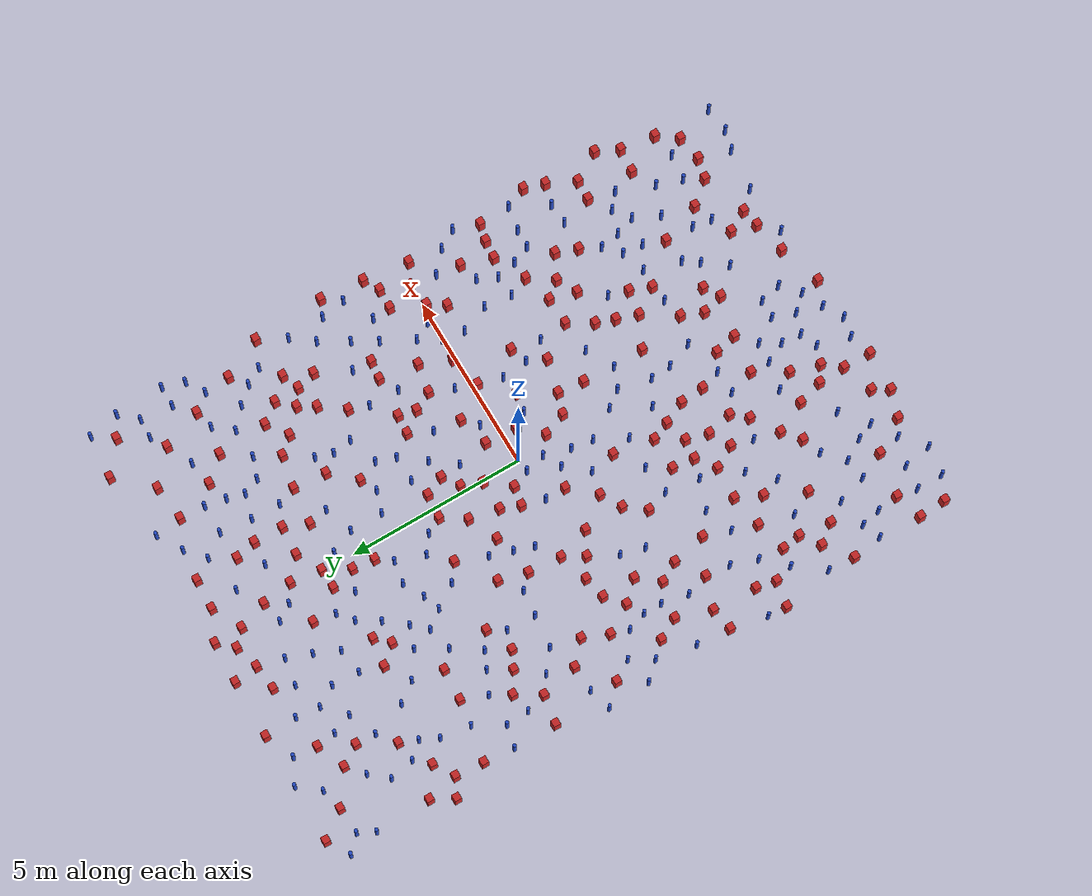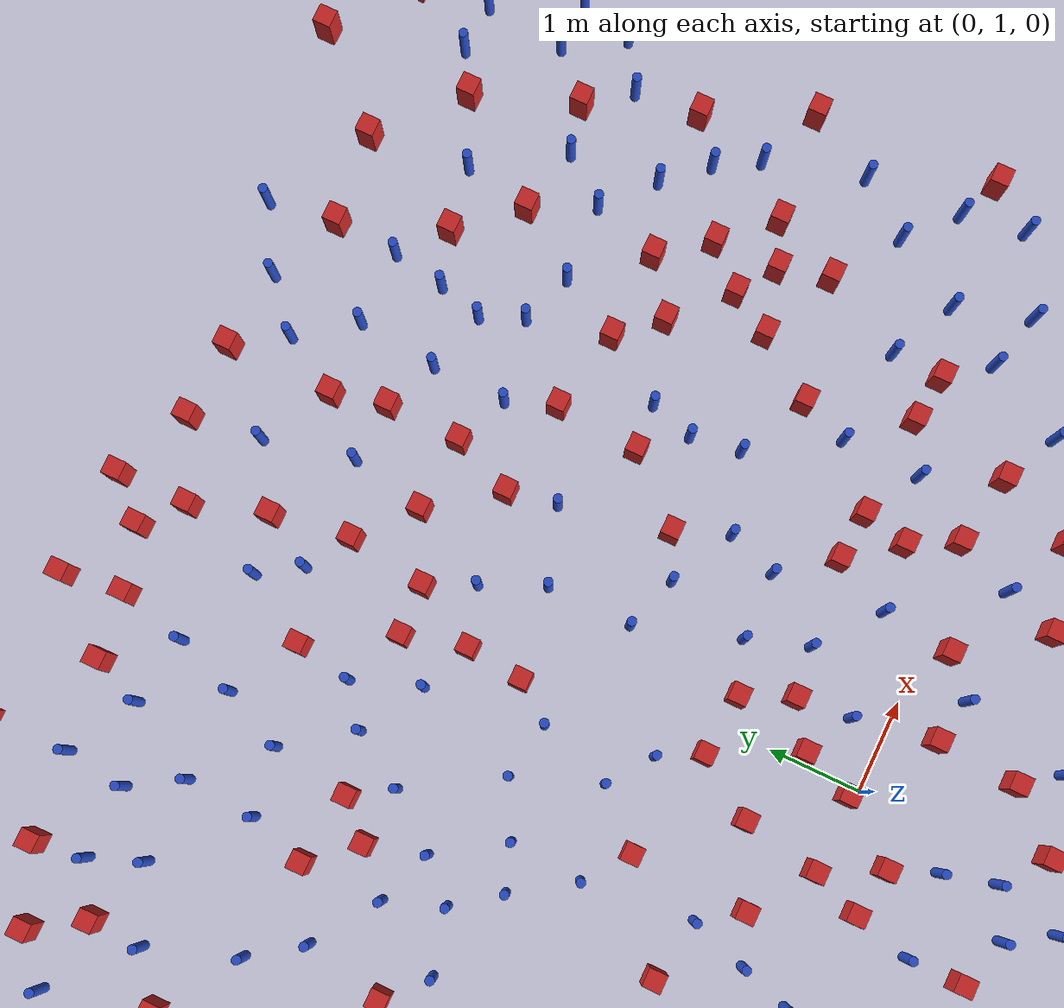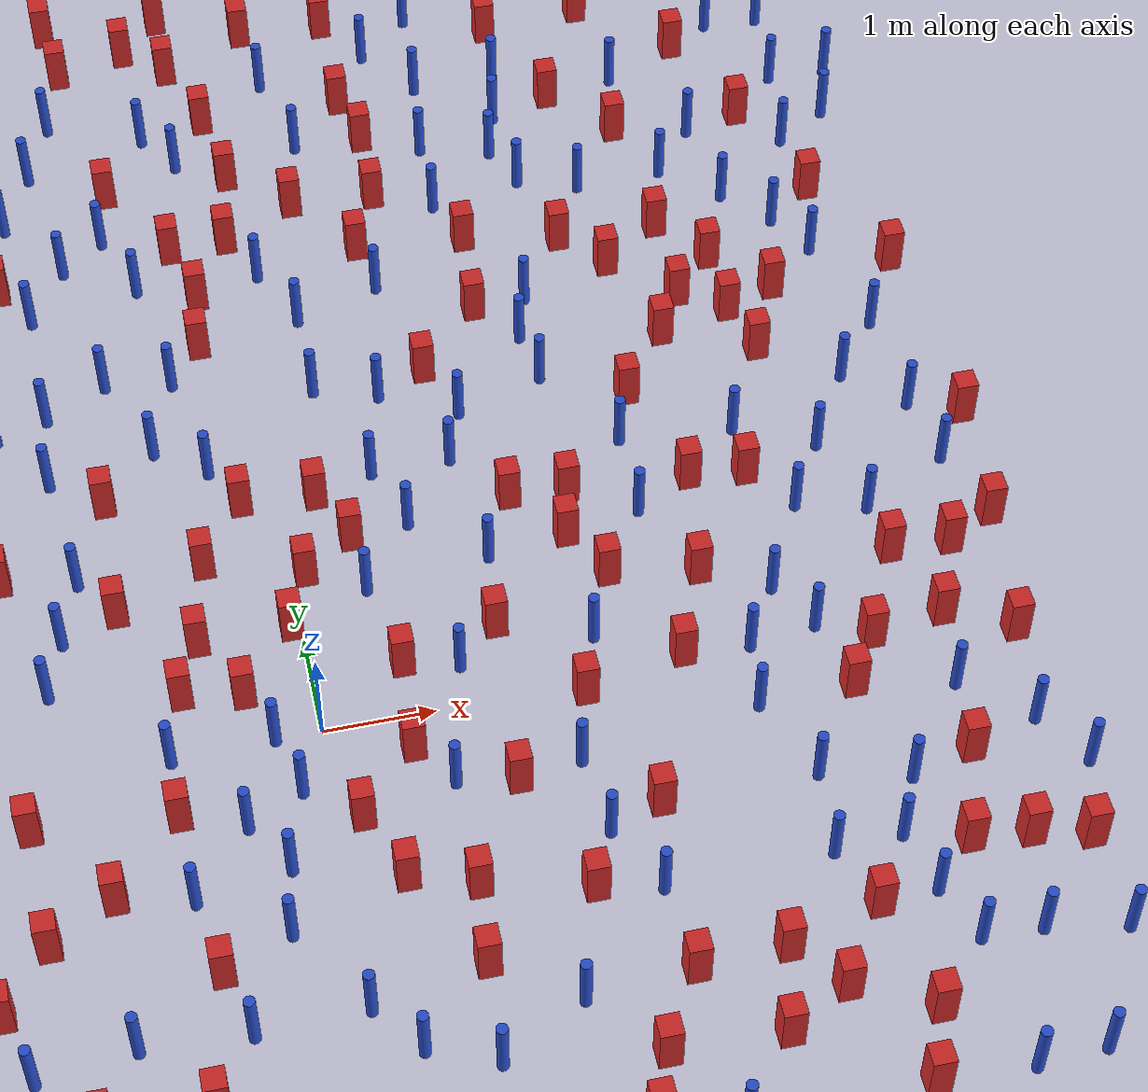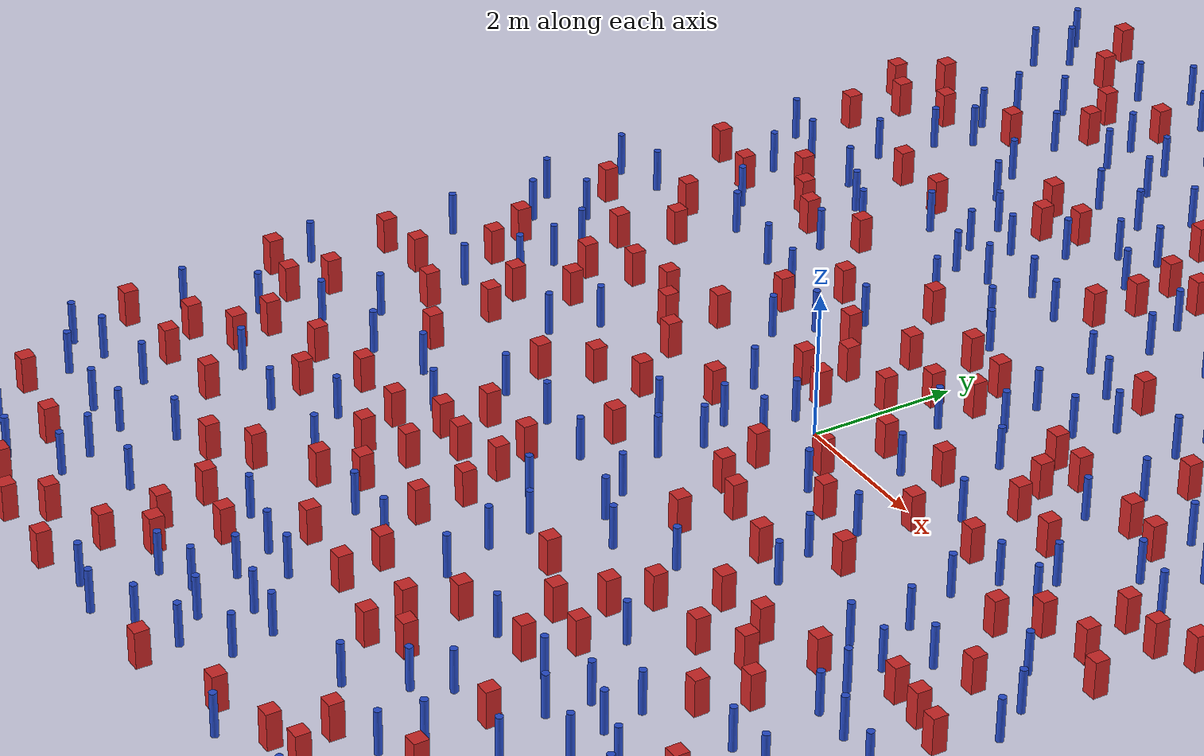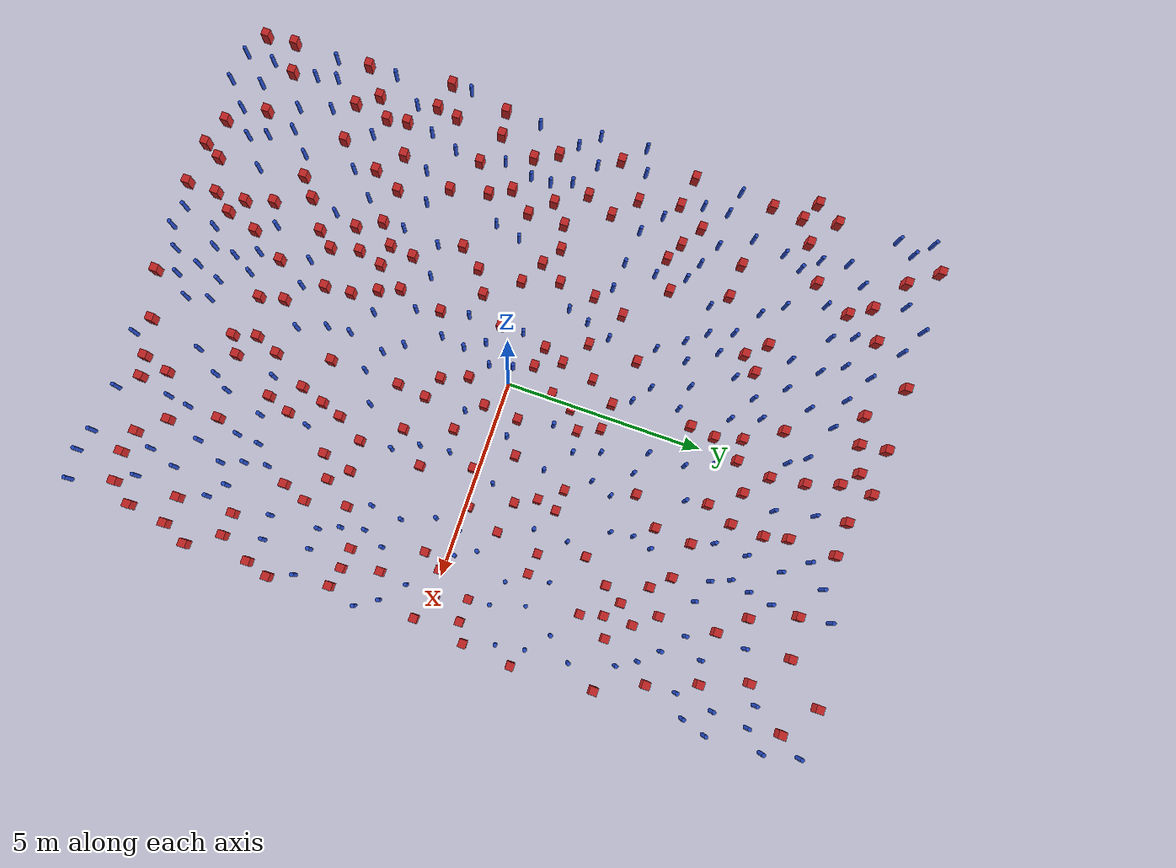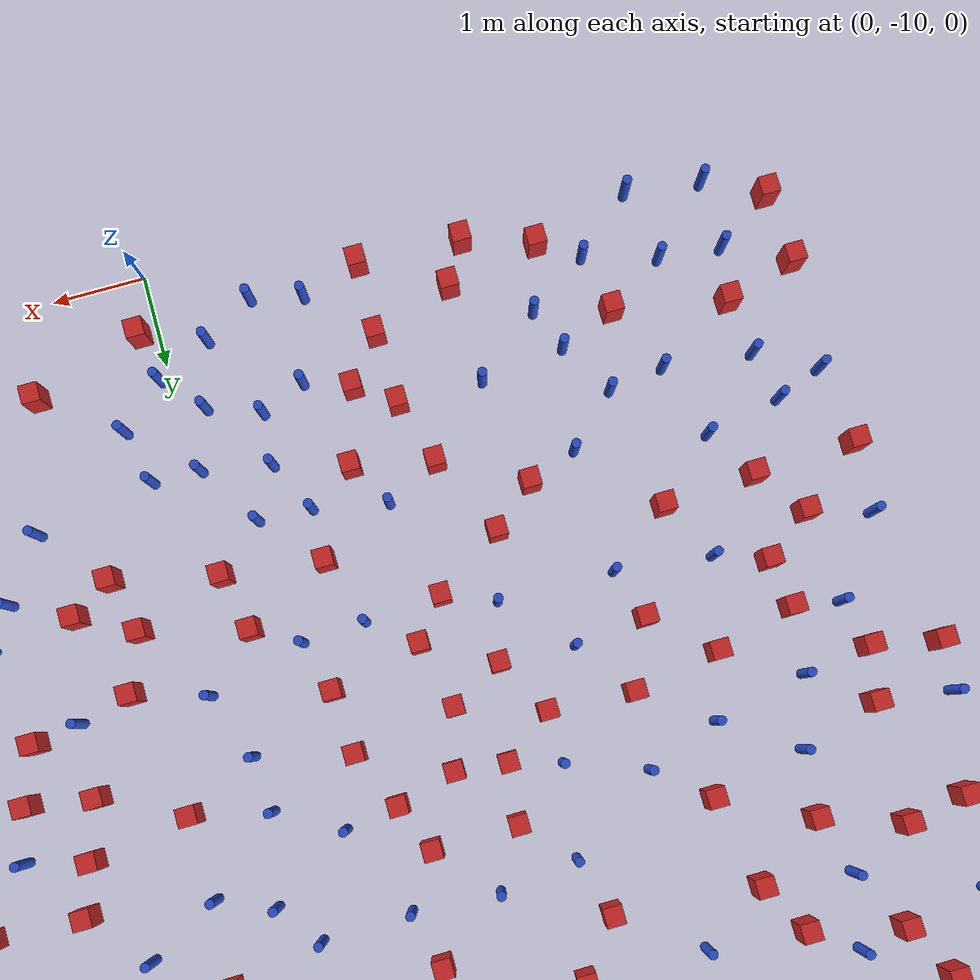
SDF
<sdf version="1.6">
  <model name="dense_18"><model name="square_post_obstacle0">
  <static>true</static>
  <pose frame="">-3.55596763186 3.06718040949 1.91545236811e-07 -7.35059704564e-06 1.12565212e-07 2.39332434364e-05</pose>
  <link name="link">
    <pose frame="">0 0 0.25 0 -0 0</pose>
    <inertial>
      <mass>100</mass>
      <inertia>
        <ixx>0.166667</ixx>
        <ixy>0</ixy>
        <ixz>0</ixz>
        <iyy>0.166667</iyy>
        <iyz>0</iyz>
        <izz>0.166667</izz>
      </inertia>
    </inertial>
    <collision name="collision">
      <geometry>
        <box>
          <size>.2 .2 .5</size>
        </box>
      </geometry>
      <max_contacts>10</max_contacts>
      <surface>
        <contact>
          <ode/>
        </contact>
        <bounce/>
        <friction>
          <torsional>
            <ode/>
          </torsional>
          <ode/>
        </friction>
      </surface>
    </collision>
    <visual name="visual">
      <geometry>
        <box>
          <size>.2 .2 .5</size>
        </box>
      </geometry>
      <material>
        <script>
          <name>Gazebo/Red</name>
          <uri>file://media/materials/scripts/gazebo.material</uri>
        </script>
      </material>
    </visual>
    <self_collide>0</self_collide>
    <kinematic>0</kinematic>
  </link>
</model>
<model name="square_post_obstacle1">
  <static>true</static>
  <pose frame="">2.30079140672 -0.113341108883 1.91545236811e-07 -7.35059704564e-06 1.12565212e-07 2.39332434364e-05</pose>
  <link name="link">
    <pose frame="">0 0 0.25 0 -0 0</pose>
    <inertial>
      <mass>100</mass>
      <inertia>
        <ixx>0.166667</ixx>
        <ixy>0</ixy>
        <ixz>0</ixz>
        <iyy>0.166667</iyy>
        <iyz>0</iyz>
        <izz>0.166667</izz>
      </inertia>
    </inertial>
    <collision name="collision">
      <geometry>
        <box>
          <size>.2 .2 .5</size>
        </box>
      </geometry>
      <max_contacts>10</max_contacts>
      <surface>
        <contact>
          <ode/>
        </contact>
        <bounce/>
        <friction>
          <torsional>
            <ode/>
          </torsional>
          <ode/>
        </friction>
      </surface>
    </collision>
    <visual name="visual">
      <geometry>
        <box>
          <size>.2 .2 .5</size>
        </box>
      </geometry>
      <material>
        <script>
          <name>Gazebo/Red</name>
          <uri>file://media/materials/scripts/gazebo.material</uri>
        </script>
      </material>
    </visual>
    <self_collide>0</self_collide>
    <kinematic>0</kinematic>
  </link>
</model>
<model name="pole_obstacle0">
  <static>true</static>
  <pose frame="">-0.643365630243 -5.73914750013 7.38925637345e-09 -8.471706928e-08 1.24976765086e-08 -1.74513093015e-07</pose>
  <link name="link">
  <pose frame="">0 0 0.3 0 -0 0</pose>
    <inertial>
      <mass>1</mass>
      <inertia>
        <ixx>0.145833</ixx>
        <ixy>0</ixy>
        <ixz>0</ixz>
        <iyy>0.145833</iyy>
        <iyz>0</iyz>
        <izz>0.125</izz>
      </inertia>
    </inertial>
    <collision name="collision">
      <geometry>
        <cylinder>
          <radius>0.05</radius>
          <length>.6</length>
        </cylinder>
      </geometry>
      <max_contacts>10</max_contacts>
      <surface>
        <contact>
          <ode/>
        </contact>
        <bounce/>
        <friction>
          <torsional>
            <ode/>
          </torsional>
          <ode/>
        </friction>
      </surface>
    </collision>
    <visual name="visual">
      <geometry>
        <cylinder>
          <radius>0.05</radius>
          <length>.6</length>
        </cylinder>
      </geometry>
      <material>
        <script>
          <name>Gazebo/Blue</name>
          <uri>file://media/materials/scripts/gazebo.material</uri>
        </script>
      </material>
    </visual>
    <self_collide>0</self_collide>
    <kinematic>0</kinematic>
  </link>
</model>
<model name="square_post_obstacle2">
  <static>true</static>
  <pose frame="">-1.97392428665 -4.67778224136 1.91545236811e-07 -7.35059704564e-06 1.12565212e-07 2.39332434364e-05</pose>
  <link name="link">
    <pose frame="">0 0 0.25 0 -0 0</pose>
    <inertial>
      <mass>100</mass>
      <inertia>
        <ixx>0.166667</ixx>
        <ixy>0</ixy>
        <ixz>0</ixz>
        <iyy>0.166667</iyy>
        <iyz>0</iyz>
        <izz>0.166667</izz>
      </inertia>
    </inertial>
    <collision name="collision">
      <geometry>
        <box>
          <size>.2 .2 .5</size>
        </box>
      </geometry>
      <max_contacts>10</max_contacts>
      <surface>
        <contact>
          <ode/>
        </contact>
        <bounce/>
        <friction>
          <torsional>
            <ode/>
          </torsional>
          <ode/>
        </friction>
      </surface>
    </collision>
    <visual name="visual">
      <geometry>
        <box>
          <size>.2 .2 .5</size>
        </box>
      </geometry>
      <material>
        <script>
          <name>Gazebo/Red</name>
          <uri>file://media/materials/scripts/gazebo.material</uri>
        </script>
      </material>
    </visual>
    <self_collide>0</self_collide>
    <kinematic>0</kinematic>
  </link>
</model>
<model name="pole_obstacle1">
  <static>true</static>
  <pose frame="">2.11567827239 -0.791708799903 7.38925637345e-09 -8.471706928e-08 1.24976765177e-08 -1.74513093012e-07</pose>
  <link name="link">
  <pose frame="">0 0 0.3 0 -0 0</pose>
    <inertial>
      <mass>1</mass>
      <inertia>
        <ixx>0.145833</ixx>
        <ixy>0</ixy>
        <ixz>0</ixz>
        <iyy>0.145833</iyy>
        <iyz>0</iyz>
        <izz>0.125</izz>
      </inertia>
    </inertial>
    <collision name="collision">
      <geometry>
        <cylinder>
          <radius>0.05</radius>
          <length>.6</length>
        </cylinder>
      </geometry>
      <max_contacts>10</max_contacts>
      <surface>
        <contact>
          <ode/>
        </contact>
        <bounce/>
        <friction>
          <torsional>
            <ode/>
          </torsional>
          <ode/>
        </friction>
      </surface>
    </collision>
    <visual name="visual">
      <geometry>
        <cylinder>
          <radius>0.05</radius>
          <length>.6</length>
        </cylinder>
      </geometry>
      <material>
        <script>
          <name>Gazebo/Blue</name>
          <uri>file://media/materials/scripts/gazebo.material</uri>
        </script>
      </material>
    </visual>
    <self_collide>0</self_collide>
    <kinematic>0</kinematic>
  </link>
</model>
<model name="square_post_obstacle3">
  <static>true</static>
  <pose frame="">5.82159080179 5.45630986029 1.91545236811e-07 -7.35059704564e-06 1.12565212e-07 2.39332434364e-05</pose>
  <link name="link">
    <pose frame="">0 0 0.25 0 -0 0</pose>
    <inertial>
      <mass>100</mass>
      <inertia>
        <ixx>0.166667</ixx>
        <ixy>0</ixy>
        <ixz>0</ixz>
        <iyy>0.166667</iyy>
        <iyz>0</iyz>
        <izz>0.166667</izz>
      </inertia>
    </inertial>
    <collision name="collision">
      <geometry>
        <box>
          <size>.2 .2 .5</size>
        </box>
      </geometry>
      <max_contacts>10</max_contacts>
      <surface>
        <contact>
          <ode/>
        </contact>
        <bounce/>
        <friction>
          <torsional>
            <ode/>
          </torsional>
          <ode/>
        </friction>
      </surface>
    </collision>
    <visual name="visual">
      <geometry>
        <box>
          <size>.2 .2 .5</size>
        </box>
      </geometry>
      <material>
        <script>
          <name>Gazebo/Red</name>
          <uri>file://media/materials/scripts/gazebo.material</uri>
        </script>
      </material>
    </visual>
    <self_collide>0</self_collide>
    <kinematic>0</kinematic>
  </link>
</model>
<model name="pole_obstacle2">
  <static>true</static>
  <pose frame="">6.14572191631 -3.33567524918 7.38925637345e-09 -8.47170692798e-08 1.24976764937e-08 -1.74513093023e-07</pose>
  <link name="link">
  <pose frame="">0 0 0.3 0 -0 0</pose>
    <inertial>
      <mass>1</mass>
      <inertia>
        <ixx>0.145833</ixx>
        <ixy>0</ixy>
        <ixz>0</ixz>
        <iyy>0.145833</iyy>
        <iyz>0</iyz>
        <izz>0.125</izz>
      </inertia>
    </inertial>
    <collision name="collision">
      <geometry>
        <cylinder>
          <radius>0.05</radius>
          <length>.6</length>
        </cylinder>
      </geometry>
      <max_contacts>10</max_contacts>
      <surface>
        <contact>
          <ode/>
        </contact>
        <bounce/>
        <friction>
          <torsional>
            <ode/>
          </torsional>
          <ode/>
        </friction>
      </surface>
    </collision>
    <visual name="visual">
      <geometry>
        <cylinder>
          <radius>0.05</radius>
          <length>.6</length>
        </cylinder>
      </geometry>
      <material>
        <script>
          <name>Gazebo/Blue</name>
          <uri>file://media/materials/scripts/gazebo.material</uri>
        </script>
      </material>
    </visual>
    <self_collide>0</self_collide>
    <kinematic>0</kinematic>
  </link>
</model>
<model name="pole_obstacle3">
  <static>true</static>
  <pose frame="">-2.89417251278 -3.81996052843 7.38925637345e-09 -8.47170692798e-08 1.24976764939e-08 -1.74513093025e-07</pose>
  <link name="link">
  <pose frame="">0 0 0.3 0 -0 0</pose>
    <inertial>
      <mass>1</mass>
      <inertia>
        <ixx>0.145833</ixx>
        <ixy>0</ixy>
        <ixz>0</ixz>
        <iyy>0.145833</iyy>
        <iyz>0</iyz>
        <izz>0.125</izz>
      </inertia>
    </inertial>
    <collision name="collision">
      <geometry>
        <cylinder>
          <radius>0.05</radius>
          <length>.6</length>
        </cylinder>
      </geometry>
      <max_contacts>10</max_contacts>
      <surface>
        <contact>
          <ode/>
        </contact>
        <bounce/>
        <friction>
          <torsional>
            <ode/>
          </torsional>
          <ode/>
        </friction>
      </surface>
    </collision>
    <visual name="visual">
      <geometry>
        <cylinder>
          <radius>0.05</radius>
          <length>.6</length>
        </cylinder>
      </geometry>
      <material>
        <script>
          <name>Gazebo/Blue</name>
          <uri>file://media/materials/scripts/gazebo.material</uri>
        </script>
      </material>
    </visual>
    <self_collide>0</self_collide>
    <kinematic>0</kinematic>
  </link>
</model>
<model name="square_post_obstacle4">
  <static>true</static>
  <pose frame="">-2.54340053731 -4.98946207609 1.91545236811e-07 -7.35059704564e-06 1.12565212e-07 2.39332434364e-05</pose>
  <link name="link">
    <pose frame="">0 0 0.25 0 -0 0</pose>
    <inertial>
      <mass>100</mass>
      <inertia>
        <ixx>0.166667</ixx>
        <ixy>0</ixy>
        <ixz>0</ixz>
        <iyy>0.166667</iyy>
        <iyz>0</iyz>
        <izz>0.166667</izz>
      </inertia>
    </inertial>
    <collision name="collision">
      <geometry>
        <box>
          <size>.2 .2 .5</size>
        </box>
      </geometry>
      <max_contacts>10</max_contacts>
      <surface>
        <contact>
          <ode/>
        </contact>
        <bounce/>
        <friction>
          <torsional>
            <ode/>
          </torsional>
          <ode/>
        </friction>
      </surface>
    </collision>
    <visual name="visual">
      <geometry>
        <box>
          <size>.2 .2 .5</size>
        </box>
      </geometry>
      <material>
        <script>
          <name>Gazebo/Red</name>
          <uri>file://media/materials/scripts/gazebo.material</uri>
        </script>
      </material>
    </visual>
    <self_collide>0</self_collide>
    <kinematic>0</kinematic>
  </link>
</model>
<model name="square_post_obstacle5">
  <static>true</static>
  <pose frame="">4.39867281722 -3.73941172745 1.91545236811e-07 -7.35059704564e-06 1.12565212e-07 2.39332434364e-05</pose>
  <link name="link">
    <pose frame="">0 0 0.25 0 -0 0</pose>
    <inertial>
      <mass>100</mass>
      <inertia>
        <ixx>0.166667</ixx>
        <ixy>0</ixy>
        <ixz>0</ixz>
        <iyy>0.166667</iyy>
        <iyz>0</iyz>
        <izz>0.166667</izz>
      </inertia>
    </inertial>
    <collision name="collision">
      <geometry>
        <box>
          <size>.2 .2 .5</size>
        </box>
      </geometry>
      <max_contacts>10</max_contacts>
      <surface>
        <contact>
          <ode/>
        </contact>
        <bounce/>
        <friction>
          <torsional>
            <ode/>
          </torsional>
          <ode/>
        </friction>
      </surface>
    </collision>
    <visual name="visual">
      <geometry>
        <box>
          <size>.2 .2 .5</size>
        </box>
      </geometry>
      <material>
        <script>
          <name>Gazebo/Red</name>
          <uri>file://media/materials/scripts/gazebo.material</uri>
        </script>
      </material>
    </visual>
    <self_collide>0</self_collide>
    <kinematic>0</kinematic>
  </link>
</model>
<model name="square_post_obstacle6">
  <static>true</static>
  <pose frame="">-4.81822613164 -0.429306550397 1.91545236811e-07 -7.35059704564e-06 1.12565212e-07 2.39332434364e-05</pose>
  <link name="link">
    <pose frame="">0 0 0.25 0 -0 0</pose>
    <inertial>
      <mass>100</mass>
      <inertia>
        <ixx>0.166667</ixx>
        <ixy>0</ixy>
        <ixz>0</ixz>
        <iyy>0.166667</iyy>
        <iyz>0</iyz>
        <izz>0.166667</izz>
      </inertia>
    </inertial>
    <collision name="collision">
      <geometry>
        <box>
          <size>.2 .2 .5</size>
        </box>
      </geometry>
      <max_contacts>10</max_contacts>
      <surface>
        <contact>
          <ode/>
        </contact>
        <bounce/>
        <friction>
          <torsional>
            <ode/>
          </torsional>
          <ode/>
        </friction>
      </surface>
    </collision>
    <visual name="visual">
      <geometry>
        <box>
          <size>.2 .2 .5</size>
        </box>
      </geometry>
      <material>
        <script>
          <name>Gazebo/Red</name>
          <uri>file://media/materials/scripts/gazebo.material</uri>
        </script>
      </material>
    </visual>
    <self_collide>0</self_collide>
    <kinematic>0</kinematic>
  </link>
</model>
<model name="pole_obstacle4">
  <static>true</static>
  <pose frame="">-6.87340431811 9.03791344532 7.38925637345e-09 -8.471706928e-08 1.24976765081e-08 -1.74513093015e-07</pose>
  <link name="link">
  <pose frame="">0 0 0.3 0 -0 0</pose>
    <inertial>
      <mass>1</mass>
      <inertia>
        <ixx>0.145833</ixx>
        <ixy>0</ixy>
        <ixz>0</ixz>
        <iyy>0.145833</iyy>
        <iyz>0</iyz>
        <izz>0.125</izz>
      </inertia>
    </inertial>
    <collision name="collision">
      <geometry>
        <cylinder>
          <radius>0.05</radius>
          <length>.6</length>
        </cylinder>
      </geometry>
      <max_contacts>10</max_contacts>
      <surface>
        <contact>
          <ode/>
        </contact>
        <bounce/>
        <friction>
          <torsional>
            <ode/>
          </torsional>
          <ode/>
        </friction>
      </surface>
    </collision>
    <visual name="visual">
      <geometry>
        <cylinder>
          <radius>0.05</radius>
          <length>.6</length>
        </cylinder>
      </geometry>
      <material>
        <script>
          <name>Gazebo/Blue</name>
          <uri>file://media/materials/scripts/gazebo.material</uri>
        </script>
      </material>
    </visual>
    <self_collide>0</self_collide>
    <kinematic>0</kinematic>
  </link>
</model>
<model name="pole_obstacle5">
  <static>true</static>
  <pose frame="">-2.81162982472 4.31498104708 7.38925637345e-09 -8.47170692798e-08 1.24976765033e-08 -1.74513093019e-07</pose>
  <link name="link">
  <pose frame="">0 0 0.3 0 -0 0</pose>
    <inertial>
      <mass>1</mass>
      <inertia>
        <ixx>0.145833</ixx>
        <ixy>0</ixy>
        <ixz>0</ixz>
        <iyy>0.145833</iyy>
        <iyz>0</iyz>
        <izz>0.125</izz>
      </inertia>
    </inertial>
    <collision name="collision">
      <geometry>
        <cylinder>
          <radius>0.05</radius>
          <length>.6</length>
        </cylinder>
      </geometry>
      <max_contacts>10</max_contacts>
      <surface>
        <contact>
          <ode/>
        </contact>
        <bounce/>
        <friction>
          <torsional>
            <ode/>
          </torsional>
          <ode/>
        </friction>
      </surface>
    </collision>
    <visual name="visual">
      <geometry>
        <cylinder>
          <radius>0.05</radius>
          <length>.6</length>
        </cylinder>
      </geometry>
      <material>
        <script>
          <name>Gazebo/Blue</name>
          <uri>file://media/materials/scripts/gazebo.material</uri>
        </script>
      </material>
    </visual>
    <self_collide>0</self_collide>
    <kinematic>0</kinematic>
  </link>
</model>
<model name="square_post_obstacle7">
  <static>true</static>
  <pose frame="">0.733176663758 -0.373524283608 1.91545236811e-07 -7.35059704564e-06 1.12565212e-07 2.39332434364e-05</pose>
  <link name="link">
    <pose frame="">0 0 0.25 0 -0 0</pose>
    <inertial>
      <mass>100</mass>
      <inertia>
        <ixx>0.166667</ixx>
        <ixy>0</ixy>
        <ixz>0</ixz>
        <iyy>0.166667</iyy>
        <iyz>0</iyz>
        <izz>0.166667</izz>
      </inertia>
    </inertial>
    <collision name="collision">
      <geometry>
        <box>
          <size>.2 .2 .5</size>
        </box>
      </geometry>
      <max_contacts>10</max_contacts>
      <surface>
        <contact>
          <ode/>
        </contact>
        <bounce/>
        <friction>
          <torsional>
            <ode/>
          </torsional>
          <ode/>
        </friction>
      </surface>
    </collision>
    <visual name="visual">
      <geometry>
        <box>
          <size>.2 .2 .5</size>
        </box>
      </geometry>
      <material>
        <script>
          <name>Gazebo/Red</name>
          <uri>file://media/materials/scripts/gazebo.material</uri>
        </script>
      </material>
    </visual>
    <self_collide>0</self_collide>
    <kinematic>0</kinematic>
  </link>
</model>
<model name="square_post_obstacle8">
  <static>true</static>
  <pose frame="">-0.546934222434 5.92013509741 1.91545236811e-07 -7.35059704564e-06 1.12565212e-07 2.39332434364e-05</pose>
  <link name="link">
    <pose frame="">0 0 0.25 0 -0 0</pose>
    <inertial>
      <mass>100</mass>
      <inertia>
        <ixx>0.166667</ixx>
        <ixy>0</ixy>
        <ixz>0</ixz>
        <iyy>0.166667</iyy>
        <iyz>0</iyz>
        <izz>0.166667</izz>
      </inertia>
    </inertial>
    <collision name="collision">
      <geometry>
        <box>
          <size>.2 .2 .5</size>
        </box>
      </geometry>
      <max_contacts>10</max_contacts>
      <surface>
        <contact>
          <ode/>
        </contact>
        <bounce/>
        <friction>
          <torsional>
            <ode/>
          </torsional>
          <ode/>
        </friction>
      </surface>
    </collision>
    <visual name="visual">
      <geometry>
        <box>
          <size>.2 .2 .5</size>
        </box>
      </geometry>
      <material>
        <script>
          <name>Gazebo/Red</name>
          <uri>file://media/materials/scripts/gazebo.material</uri>
        </script>
      </material>
    </visual>
    <self_collide>0</self_collide>
    <kinematic>0</kinematic>
  </link>
</model>
<model name="pole_obstacle6">
  <static>true</static>
  <pose frame="">3.22004854573 1.77578867734 7.38925637345e-09 -8.471706928e-08 1.24976765152e-08 -1.74513093012e-07</pose>
  <link name="link">
  <pose frame="">0 0 0.3 0 -0 0</pose>
    <inertial>
      <mass>1</mass>
      <inertia>
        <ixx>0.145833</ixx>
        <ixy>0</ixy>
        <ixz>0</ixz>
        <iyy>0.145833</iyy>
        <iyz>0</iyz>
        <izz>0.125</izz>
      </inertia>
    </inertial>
    <collision name="collision">
      <geometry>
        <cylinder>
          <radius>0.05</radius>
          <length>.6</length>
        </cylinder>
      </geometry>
      <max_contacts>10</max_contacts>
      <surface>
        <contact>
          <ode/>
        </contact>
        <bounce/>
        <friction>
          <torsional>
            <ode/>
          </torsional>
          <ode/>
        </friction>
      </surface>
    </collision>
    <visual name="visual">
      <geometry>
        <cylinder>
          <radius>0.05</radius>
          <length>.6</length>
        </cylinder>
      </geometry>
      <material>
        <script>
          <name>Gazebo/Blue</name>
          <uri>file://media/materials/scripts/gazebo.material</uri>
        </script>
      </material>
    </visual>
    <self_collide>0</self_collide>
    <kinematic>0</kinematic>
  </link>
</model>
<model name="pole_obstacle7">
  <static>true</static>
  <pose frame="">3.00797977638 6.1850498163 7.38925637345e-09 -8.47170692798e-08 1.24976765033e-08 -1.74513093019e-07</pose>
  <link name="link">
  <pose frame="">0 0 0.3 0 -0 0</pose>
    <inertial>
      <mass>1</mass>
      <inertia>
        <ixx>0.145833</ixx>
        <ixy>0</ixy>
        <ixz>0</ixz>
        <iyy>0.145833</iyy>
        <iyz>0</iyz>
        <izz>0.125</izz>
      </inertia>
    </inertial>
    <collision name="collision">
      <geometry>
        <cylinder>
          <radius>0.05</radius>
          <length>.6</length>
        </cylinder>
      </geometry>
      <max_contacts>10</max_contacts>
      <surface>
        <contact>
          <ode/>
        </contact>
        <bounce/>
        <friction>
          <torsional>
            <ode/>
          </torsional>
          <ode/>
        </friction>
      </surface>
    </collision>
    <visual name="visual">
      <geometry>
        <cylinder>
          <radius>0.05</radius>
          <length>.6</length>
        </cylinder>
      </geometry>
      <material>
        <script>
          <name>Gazebo/Blue</name>
          <uri>file://media/materials/scripts/gazebo.material</uri>
        </script>
      </material>
    </visual>
    <self_collide>0</self_collide>
    <kinematic>0</kinematic>
  </link>
</model>
<model name="square_post_obstacle9">
  <static>true</static>
  <pose frame="">5.31786729422 0.826178670648 1.91545236811e-07 -7.35059704564e-06 1.12565212e-07 2.39332434364e-05</pose>
  <link name="link">
    <pose frame="">0 0 0.25 0 -0 0</pose>
    <inertial>
      <mass>100</mass>
      <inertia>
        <ixx>0.166667</ixx>
        <ixy>0</ixy>
        <ixz>0</ixz>
        <iyy>0.166667</iyy>
        <iyz>0</iyz>
        <izz>0.166667</izz>
      </inertia>
    </inertial>
    <collision name="collision">
      <geometry>
        <box>
          <size>.2 .2 .5</size>
        </box>
      </geometry>
      <max_contacts>10</max_contacts>
      <surface>
        <contact>
          <ode/>
        </contact>
        <bounce/>
        <friction>
          <torsional>
            <ode/>
          </torsional>
          <ode/>
        </friction>
      </surface>
    </collision>
    <visual name="visual">
      <geometry>
        <box>
          <size>.2 .2 .5</size>
        </box>
      </geometry>
      <material>
        <script>
          <name>Gazebo/Red</name>
          <uri>file://media/materials/scripts/gazebo.material</uri>
        </script>
      </material>
    </visual>
    <self_collide>0</self_collide>
    <kinematic>0</kinematic>
  </link>
</model>
<model name="square_post_obstacle10">
  <static>true</static>
  <pose frame="">0.908520756154 -4.35322302698 1.91545236811e-07 -7.35059704564e-06 1.12565212e-07 2.39332434364e-05</pose>
  <link name="link">
    <pose frame="">0 0 0.25 0 -0 0</pose>
    <inertial>
      <mass>100</mass>
      <inertia>
        <ixx>0.166667</ixx>
        <ixy>0</ixy>
        <ixz>0</ixz>
        <iyy>0.166667</iyy>
        <iyz>0</iyz>
        <izz>0.166667</izz>
      </inertia>
    </inertial>
    <collision name="collision">
      <geometry>
        <box>
          <size>.2 .2 .5</size>
        </box>
      </geometry>
      <max_contacts>10</max_contacts>
      <surface>
        <contact>
          <ode/>
        </contact>
        <bounce/>
        <friction>
          <torsional>
            <ode/>
          </torsional>
          <ode/>
        </friction>
      </surface>
    </collision>
    <visual name="visual">
      <geometry>
        <box>
          <size>.2 .2 .5</size>
        </box>
      </geometry>
      <material>
        <script>
          <name>Gazebo/Red</name>
          <uri>file://media/materials/scripts/gazebo.material</uri>
        </script>
      </material>
    </visual>
    <self_collide>0</self_collide>
    <kinematic>0</kinematic>
  </link>
</model>
<model name="square_post_obstacle11">
  <static>true</static>
  <pose frame="">-4.27293090781 -3.06913041119 1.91545236811e-07 -7.35059704564e-06 1.12565212e-07 2.39332434364e-05</pose>
  <link name="link">
    <pose frame="">0 0 0.25 0 -0 0</pose>
    <inertial>
      <mass>100</mass>
      <inertia>
        <ixx>0.166667</ixx>
        <ixy>0</ixy>
        <ixz>0</ixz>
        <iyy>0.166667</iyy>
        <iyz>0</iyz>
        <izz>0.166667</izz>
      </inertia>
    </inertial>
    <collision name="collision">
      <geometry>
        <box>
          <size>.2 .2 .5</size>
        </box>
      </geometry>
      <max_contacts>10</max_contacts>
      <surface>
        <contact>
          <ode/>
        </contact>
        <bounce/>
        <friction>
          <torsional>
            <ode/>
          </torsional>
          <ode/>
        </friction>
      </surface>
    </collision>
    <visual name="visual">
      <geometry>
        <box>
          <size>.2 .2 .5</size>
        </box>
      </geometry>
      <material>
        <script>
          <name>Gazebo/Red</name>
          <uri>file://media/materials/scripts/gazebo.material</uri>
        </script>
      </material>
    </visual>
    <self_collide>0</self_collide>
    <kinematic>0</kinematic>
  </link>
</model>
<model name="square_post_obstacle12">
  <static>true</static>
  <pose frame="">-3.90689282888 4.53653102175 1.91545236811e-07 -7.35059704564e-06 1.12565212e-07 2.39332434364e-05</pose>
  <link name="link">
    <pose frame="">0 0 0.25 0 -0 0</pose>
    <inertial>
      <mass>100</mass>
      <inertia>
        <ixx>0.166667</ixx>
        <ixy>0</ixy>
        <ixz>0</ixz>
        <iyy>0.166667</iyy>
        <iyz>0</iyz>
        <izz>0.166667</izz>
      </inertia>
    </inertial>
    <collision name="collision">
      <geometry>
        <box>
          <size>.2 .2 .5</size>
        </box>
      </geometry>
      <max_contacts>10</max_contacts>
      <surface>
        <contact>
          <ode/>
        </contact>
        <bounce/>
        <friction>
          <torsional>
            <ode/>
          </torsional>
          <ode/>
        </friction>
      </surface>
    </collision>
    <visual name="visual">
      <geometry>
        <box>
          <size>.2 .2 .5</size>
        </box>
      </geometry>
      <material>
        <script>
          <name>Gazebo/Red</name>
          <uri>file://media/materials/scripts/gazebo.material</uri>
        </script>
      </material>
    </visual>
    <self_collide>0</self_collide>
    <kinematic>0</kinematic>
  </link>
</model>
<model name="square_post_obstacle13">
  <static>true</static>
  <pose frame="">5.39153406921 -1.39861252525 1.91545236811e-07 -7.35059704564e-06 1.12565212e-07 2.39332434364e-05</pose>
  <link name="link">
    <pose frame="">0 0 0.25 0 -0 0</pose>
    <inertial>
      <mass>100</mass>
      <inertia>
        <ixx>0.166667</ixx>
        <ixy>0</ixy>
        <ixz>0</ixz>
        <iyy>0.166667</iyy>
        <iyz>0</iyz>
        <izz>0.166667</izz>
      </inertia>
    </inertial>
    <collision name="collision">
      <geometry>
        <box>
          <size>.2 .2 .5</size>
        </box>
      </geometry>
      <max_contacts>10</max_contacts>
      <surface>
        <contact>
          <ode/>
        </contact>
        <bounce/>
        <friction>
          <torsional>
            <ode/>
          </torsional>
          <ode/>
        </friction>
      </surface>
    </collision>
    <visual name="visual">
      <geometry>
        <box>
          <size>.2 .2 .5</size>
        </box>
      </geometry>
      <material>
        <script>
          <name>Gazebo/Red</name>
          <uri>file://media/materials/scripts/gazebo.material</uri>
        </script>
      </material>
    </visual>
    <self_collide>0</self_collide>
    <kinematic>0</kinematic>
  </link>
</model>
<model name="pole_obstacle8">
  <static>true</static>
  <pose frame="">5.99474519024 2.49112717704 7.38925637345e-09 -8.47170692798e-08 1.24976764937e-08 -1.74513093023e-07</pose>
  <link name="link">
  <pose frame="">0 0 0.3 0 -0 0</pose>
    <inertial>
      <mass>1</mass>
      <inertia>
        <ixx>0.145833</ixx>
        <ixy>0</ixy>
        <ixz>0</ixz>
        <iyy>0.145833</iyy>
        <iyz>0</iyz>
        <izz>0.125</izz>
      </inertia>
    </inertial>
    <collision name="collision">
      <geometry>
        <cylinder>
          <radius>0.05</radius>
          <length>.6</length>
        </cylinder>
      </geometry>
      <max_contacts>10</max_contacts>
      <surface>
        <contact>
          <ode/>
        </contact>
        <bounce/>
        <friction>
          <torsional>
            <ode/>
          </torsional>
          <ode/>
        </friction>
      </surface>
    </collision>
    <visual name="visual">
      <geometry>
        <cylinder>
          <radius>0.05</radius>
          <length>.6</length>
        </cylinder>
      </geometry>
      <material>
        <script>
          <name>Gazebo/Blue</name>
          <uri>file://media/materials/scripts/gazebo.material</uri>
        </script>
      </material>
    </visual>
    <self_collide>0</self_collide>
    <kinematic>0</kinematic>
  </link>
</model>
<model name="square_post_obstacle14">
  <static>true</static>
  <pose frame="">2.77395277355 1.11454945893 1.91545236811e-07 -7.35059704564e-06 1.12565212e-07 2.39332434364e-05</pose>
  <link name="link">
    <pose frame="">0 0 0.25 0 -0 0</pose>
    <inertial>
      <mass>100</mass>
      <inertia>
        <ixx>0.166667</ixx>
        <ixy>0</ixy>
        <ixz>0</ixz>
        <iyy>0.166667</iyy>
        <iyz>0</iyz>
        <izz>0.166667</izz>
      </inertia>
    </inertial>
    <collision name="collision">
      <geometry>
        <box>
          <size>.2 .2 .5</size>
        </box>
      </geometry>
      <max_contacts>10</max_contacts>
      <surface>
        <contact>
          <ode/>
        </contact>
        <bounce/>
        <friction>
          <torsional>
            <ode/>
          </torsional>
          <ode/>
        </friction>
      </surface>
    </collision>
    <visual name="visual">
      <geometry>
        <box>
          <size>.2 .2 .5</size>
        </box>
      </geometry>
      <material>
        <script>
          <name>Gazebo/Red</name>
          <uri>file://media/materials/scripts/gazebo.material</uri>
        </script>
      </material>
    </visual>
    <self_collide>0</self_collide>
    <kinematic>0</kinematic>
  </link>
</model>
<model name="square_post_obstacle15">
  <static>true</static>
  <pose frame="">1.01795629702 -1.82561163222 1.91545236811e-07 -7.35059704564e-06 1.12565212e-07 2.39332434364e-05</pose>
  <link name="link">
    <pose frame="">0 0 0.25 0 -0 0</pose>
    <inertial>
      <mass>100</mass>
      <inertia>
        <ixx>0.166667</ixx>
        <ixy>0</ixy>
        <ixz>0</ixz>
        <iyy>0.166667</iyy>
        <iyz>0</iyz>
        <izz>0.166667</izz>
      </inertia>
    </inertial>
    <collision name="collision">
      <geometry>
        <box>
          <size>.2 .2 .5</size>
        </box>
      </geometry>
      <max_contacts>10</max_contacts>
      <surface>
        <contact>
          <ode/>
        </contact>
        <bounce/>
        <friction>
          <torsional>
            <ode/>
          </torsional>
          <ode/>
        </friction>
      </surface>
    </collision>
    <visual name="visual">
      <geometry>
        <box>
          <size>.2 .2 .5</size>
        </box>
      </geometry>
      <material>
        <script>
          <name>Gazebo/Red</name>
          <uri>file://media/materials/scripts/gazebo.material</uri>
        </script>
      </material>
    </visual>
    <self_collide>0</self_collide>
    <kinematic>0</kinematic>
  </link>
</model>
<model name="square_post_obstacle16">
  <static>true</static>
  <pose frame="">4.59854409013 -0.532294423076 1.91545236811e-07 -7.35059704564e-06 1.12565212e-07 2.39332434364e-05</pose>
  <link name="link">
    <pose frame="">0 0 0.25 0 -0 0</pose>
    <inertial>
      <mass>100</mass>
      <inertia>
        <ixx>0.166667</ixx>
        <ixy>0</ixy>
        <ixz>0</ixz>
        <iyy>0.166667</iyy>
        <iyz>0</iyz>
        <izz>0.166667</izz>
      </inertia>
    </inertial>
    <collision name="collision">
      <geometry>
        <box>
          <size>.2 .2 .5</size>
        </box>
      </geometry>
      <max_contacts>10</max_contacts>
      <surface>
        <contact>
          <ode/>
        </contact>
        <bounce/>
        <friction>
          <torsional>
            <ode/>
          </torsional>
          <ode/>
        </friction>
      </surface>
    </collision>
    <visual name="visual">
      <geometry>
        <box>
          <size>.2 .2 .5</size>
        </box>
      </geometry>
      <material>
        <script>
          <name>Gazebo/Red</name>
          <uri>file://media/materials/scripts/gazebo.material</uri>
        </script>
      </material>
    </visual>
    <self_collide>0</self_collide>
    <kinematic>0</kinematic>
  </link>
</model>
<model name="pole_obstacle9">
  <static>true</static>
  <pose frame="">-3.9550344952 -5.57008247758 7.38925637345e-09 -8.47170692799e-08 1.24976764985e-08 -1.74513093022e-07</pose>
  <link name="link">
  <pose frame="">0 0 0.3 0 -0 0</pose>
    <inertial>
      <mass>1</mass>
      <inertia>
        <ixx>0.145833</ixx>
        <ixy>0</ixy>
        <ixz>0</ixz>
        <iyy>0.145833</iyy>
        <iyz>0</iyz>
        <izz>0.125</izz>
      </inertia>
    </inertial>
    <collision name="collision">
      <geometry>
        <cylinder>
          <radius>0.05</radius>
          <length>.6</length>
        </cylinder>
      </geometry>
      <max_contacts>10</max_contacts>
      <surface>
        <contact>
          <ode/>
        </contact>
        <bounce/>
        <friction>
          <torsional>
            <ode/>
          </torsional>
          <ode/>
        </friction>
      </surface>
    </collision>
    <visual name="visual">
      <geometry>
        <cylinder>
          <radius>0.05</radius>
          <length>.6</length>
        </cylinder>
      </geometry>
      <material>
        <script>
          <name>Gazebo/Blue</name>
          <uri>file://media/materials/scripts/gazebo.material</uri>
        </script>
      </material>
    </visual>
    <self_collide>0</self_collide>
    <kinematic>0</kinematic>
  </link>
</model>
<model name="square_post_obstacle17">
  <static>true</static>
  <pose frame="">4.15785183296 -8.27256191377 1.91545236811e-07 -7.35059704564e-06 1.12565212e-07 2.39332434364e-05</pose>
  <link name="link">
    <pose frame="">0 0 0.25 0 -0 0</pose>
    <inertial>
      <mass>100</mass>
      <inertia>
        <ixx>0.166667</ixx>
        <ixy>0</ixy>
        <ixz>0</ixz>
        <iyy>0.166667</iyy>
        <iyz>0</iyz>
        <izz>0.166667</izz>
      </inertia>
    </inertial>
    <collision name="collision">
      <geometry>
        <box>
          <size>.2 .2 .5</size>
        </box>
      </geometry>
      <max_contacts>10</max_contacts>
      <surface>
        <contact>
          <ode/>
        </contact>
        <bounce/>
        <friction>
          <torsional>
            <ode/>
          </torsional>
          <ode/>
        </friction>
      </surface>
    </collision>
    <visual name="visual">
      <geometry>
        <box>
          <size>.2 .2 .5</size>
        </box>
      </geometry>
      <material>
        <script>
          <name>Gazebo/Red</name>
          <uri>file://media/materials/scripts/gazebo.material</uri>
        </script>
      </material>
    </visual>
    <self_collide>0</self_collide>
    <kinematic>0</kinematic>
  </link>
</model>
<model name="square_post_obstacle18">
  <static>true</static>
  <pose frame="">-0.758517951045 1.95636640092 1.91545236811e-07 -7.35059704564e-06 1.12565212e-07 2.39332434364e-05</pose>
  <link name="link">
    <pose frame="">0 0 0.25 0 -0 0</pose>
    <inertial>
      <mass>100</mass>
      <inertia>
        <ixx>0.166667</ixx>
        <ixy>0</ixy>
        <ixz>0</ixz>
        <iyy>0.166667</iyy>
        <iyz>0</iyz>
        <izz>0.166667</izz>
      </inertia>
    </inertial>
    <collision name="collision">
      <geometry>
        <box>
          <size>.2 .2 .5</size>
        </box>
      </geometry>
      <max_contacts>10</max_contacts>
      <surface>
        <contact>
          <ode/>
        </contact>
        <bounce/>
        <friction>
          <torsional>
            <ode/>
          </torsional>
          <ode/>
        </friction>
      </surface>
    </collision>
    <visual name="visual">
      <geometry>
        <box>
          <size>.2 .2 .5</size>
        </box>
      </geometry>
      <material>
        <script>
          <name>Gazebo/Red</name>
          <uri>file://media/materials/scripts/gazebo.material</uri>
        </script>
      </material>
    </visual>
    <self_collide>0</self_collide>
    <kinematic>0</kinematic>
  </link>
</model>
<model name="pole_obstacle10">
  <static>true</static>
  <pose frame="">6.03867695936 -1.1972389349 7.38925637345e-09 -8.471706928e-08 1.24976765134e-08 -1.74513093015e-07</pose>
  <link name="link">
  <pose frame="">0 0 0.3 0 -0 0</pose>
    <inertial>
      <mass>1</mass>
      <inertia>
        <ixx>0.145833</ixx>
        <ixy>0</ixy>
        <ixz>0</ixz>
        <iyy>0.145833</iyy>
        <iyz>0</iyz>
        <izz>0.125</izz>
      </inertia>
    </inertial>
    <collision name="collision">
      <geometry>
        <cylinder>
          <radius>0.05</radius>
          <length>.6</length>
        </cylinder>
      </geometry>
      <max_contacts>10</max_contacts>
      <surface>
        <contact>
          <ode/>
        </contact>
        <bounce/>
        <friction>
          <torsional>
            <ode/>
          </torsional>
          <ode/>
        </friction>
      </surface>
    </collision>
    <visual name="visual">
      <geometry>
        <cylinder>
          <radius>0.05</radius>
          <length>.6</length>
        </cylinder>
      </geometry>
      <material>
        <script>
          <name>Gazebo/Blue</name>
          <uri>file://media/materials/scripts/gazebo.material</uri>
        </script>
      </material>
    </visual>
    <self_collide>0</self_collide>
    <kinematic>0</kinematic>
  </link>
</model>
<model name="square_post_obstacle19">
  <static>true</static>
  <pose frame="">-1.80339025722 -5.40434559586 1.91545236811e-07 -7.35059704564e-06 1.12565212e-07 2.39332434364e-05</pose>
  <link name="link">
    <pose frame="">0 0 0.25 0 -0 0</pose>
    <inertial>
      <mass>100</mass>
      <inertia>
        <ixx>0.166667</ixx>
        <ixy>0</ixy>
        <ixz>0</ixz>
        <iyy>0.166667</iyy>
        <iyz>0</iyz>
        <izz>0.166667</izz>
      </inertia>
    </inertial>
    <collision name="collision">
      <geometry>
        <box>
          <size>.2 .2 .5</size>
        </box>
      </geometry>
      <max_contacts>10</max_contacts>
      <surface>
        <contact>
          <ode/>
        </contact>
        <bounce/>
        <friction>
          <torsional>
            <ode/>
          </torsional>
          <ode/>
        </friction>
      </surface>
    </collision>
    <visual name="visual">
      <geometry>
        <box>
          <size>.2 .2 .5</size>
        </box>
      </geometry>
      <material>
        <script>
          <name>Gazebo/Red</name>
          <uri>file://media/materials/scripts/gazebo.material</uri>
        </script>
      </material>
    </visual>
    <self_collide>0</self_collide>
    <kinematic>0</kinematic>
  </link>
</model>
<model name="pole_obstacle11">
  <static>true</static>
  <pose frame="">-5.07678339914 3.88739832947 7.38925637345e-09 -8.47170692798e-08 1.24976764937e-08 -1.74513093023e-07</pose>
  <link name="link">
  <pose frame="">0 0 0.3 0 -0 0</pose>
    <inertial>
      <mass>1</mass>
      <inertia>
        <ixx>0.145833</ixx>
        <ixy>0</ixy>
        <ixz>0</ixz>
        <iyy>0.145833</iyy>
        <iyz>0</iyz>
        <izz>0.125</izz>
      </inertia>
    </inertial>
    <collision name="collision">
      <geometry>
        <cylinder>
          <radius>0.05</radius>
          <length>.6</length>
        </cylinder>
      </geometry>
      <max_contacts>10</max_contacts>
      <surface>
        <contact>
          <ode/>
        </contact>
        <bounce/>
        <friction>
          <torsional>
            <ode/>
          </torsional>
          <ode/>
        </friction>
      </surface>
    </collision>
    <visual name="visual">
      <geometry>
        <cylinder>
          <radius>0.05</radius>
          <length>.6</length>
        </cylinder>
      </geometry>
      <material>
        <script>
          <name>Gazebo/Blue</name>
          <uri>file://media/materials/scripts/gazebo.material</uri>
        </script>
      </material>
    </visual>
    <self_collide>0</self_collide>
    <kinematic>0</kinematic>
  </link>
</model>
<model name="square_post_obstacle20">
  <static>true</static>
  <pose frame="">-4.96539036442 6.52452022297 1.91545236811e-07 -7.35059704564e-06 1.12565212e-07 2.39332434364e-05</pose>
  <link name="link">
    <pose frame="">0 0 0.25 0 -0 0</pose>
    <inertial>
      <mass>100</mass>
      <inertia>
        <ixx>0.166667</ixx>
        <ixy>0</ixy>
        <ixz>0</ixz>
        <iyy>0.166667</iyy>
        <iyz>0</iyz>
        <izz>0.166667</izz>
      </inertia>
    </inertial>
    <collision name="collision">
      <geometry>
        <box>
          <size>.2 .2 .5</size>
        </box>
      </geometry>
      <max_contacts>10</max_contacts>
      <surface>
        <contact>
          <ode/>
        </contact>
        <bounce/>
        <friction>
          <torsional>
            <ode/>
          </torsional>
          <ode/>
        </friction>
      </surface>
    </collision>
    <visual name="visual">
      <geometry>
        <box>
          <size>.2 .2 .5</size>
        </box>
      </geometry>
      <material>
        <script>
          <name>Gazebo/Red</name>
          <uri>file://media/materials/scripts/gazebo.material</uri>
        </script>
      </material>
    </visual>
    <self_collide>0</self_collide>
    <kinematic>0</kinematic>
  </link>
</model>
<model name="pole_obstacle12">
  <static>true</static>
  <pose frame="">4.17921115617 0.650031408864 7.38925637345e-09 -8.47170692799e-08 1.24976765038e-08 -1.74513093018e-07</pose>
  <link name="link">
  <pose frame="">0 0 0.3 0 -0 0</pose>
    <inertial>
      <mass>1</mass>
      <inertia>
        <ixx>0.145833</ixx>
        <ixy>0</ixy>
        <ixz>0</ixz>
        <iyy>0.145833</iyy>
        <iyz>0</iyz>
        <izz>0.125</izz>
      </inertia>
    </inertial>
    <collision name="collision">
      <geometry>
        <cylinder>
          <radius>0.05</radius>
          <length>.6</length>
        </cylinder>
      </geometry>
      <max_contacts>10</max_contacts>
      <surface>
        <contact>
          <ode/>
        </contact>
        <bounce/>
        <friction>
          <torsional>
            <ode/>
          </torsional>
          <ode/>
        </friction>
      </surface>
    </collision>
    <visual name="visual">
      <geometry>
        <cylinder>
          <radius>0.05</radius>
          <length>.6</length>
        </cylinder>
      </geometry>
      <material>
        <script>
          <name>Gazebo/Blue</name>
          <uri>file://media/materials/scripts/gazebo.material</uri>
        </script>
      </material>
    </visual>
    <self_collide>0</self_collide>
    <kinematic>0</kinematic>
  </link>
</model>
<model name="square_post_obstacle21">
  <static>true</static>
  <pose frame="">-5.22307568444 -2.58926652539 1.91545236811e-07 -7.35059704564e-06 1.12565212e-07 2.39332434364e-05</pose>
  <link name="link">
    <pose frame="">0 0 0.25 0 -0 0</pose>
    <inertial>
      <mass>100</mass>
      <inertia>
        <ixx>0.166667</ixx>
        <ixy>0</ixy>
        <ixz>0</ixz>
        <iyy>0.166667</iyy>
        <iyz>0</iyz>
        <izz>0.166667</izz>
      </inertia>
    </inertial>
    <collision name="collision">
      <geometry>
        <box>
          <size>.2 .2 .5</size>
        </box>
      </geometry>
      <max_contacts>10</max_contacts>
      <surface>
        <contact>
          <ode/>
        </contact>
        <bounce/>
        <friction>
          <torsional>
            <ode/>
          </torsional>
          <ode/>
        </friction>
      </surface>
    </collision>
    <visual name="visual">
      <geometry>
        <box>
          <size>.2 .2 .5</size>
        </box>
      </geometry>
      <material>
        <script>
          <name>Gazebo/Red</name>
          <uri>file://media/materials/scripts/gazebo.material</uri>
        </script>
      </material>
    </visual>
    <self_collide>0</self_collide>
    <kinematic>0</kinematic>
  </link>
</model>
<model name="pole_obstacle13">
  <static>true</static>
  <pose frame="">-5.31498778144 -6.6896748255 7.38925637345e-09 -8.47170692796e-08 1.24976764786e-08 -1.74513093032e-07</pose>
  <link name="link">
  <pose frame="">0 0 0.3 0 -0 0</pose>
    <inertial>
      <mass>1</mass>
      <inertia>
        <ixx>0.145833</ixx>
        <ixy>0</ixy>
        <ixz>0</ixz>
        <iyy>0.145833</iyy>
        <iyz>0</iyz>
        <izz>0.125</izz>
      </inertia>
    </inertial>
    <collision name="collision">
      <geometry>
        <cylinder>
          <radius>0.05</radius>
          <length>.6</length>
        </cylinder>
      </geometry>
      <max_contacts>10</max_contacts>
      <surface>
        <contact>
          <ode/>
        </contact>
        <bounce/>
        <friction>
          <torsional>
            <ode/>
          </torsional>
          <ode/>
        </friction>
      </surface>
    </collision>
    <visual name="visual">
      <geometry>
        <cylinder>
          <radius>0.05</radius>
          <length>.6</length>
        </cylinder>
      </geometry>
      <material>
        <script>
          <name>Gazebo/Blue</name>
          <uri>file://media/materials/scripts/gazebo.material</uri>
        </script>
      </material>
    </visual>
    <self_collide>0</self_collide>
    <kinematic>0</kinematic>
  </link>
</model>
<model name="square_post_obstacle22">
  <static>true</static>
  <pose frame="">-6.60821989965 2.79242806834 1.91545236811e-07 -7.35059704564e-06 1.12565212e-07 2.39332434364e-05</pose>
  <link name="link">
    <pose frame="">0 0 0.25 0 -0 0</pose>
    <inertial>
      <mass>100</mass>
      <inertia>
        <ixx>0.166667</ixx>
        <ixy>0</ixy>
        <ixz>0</ixz>
        <iyy>0.166667</iyy>
        <iyz>0</iyz>
        <izz>0.166667</izz>
      </inertia>
    </inertial>
    <collision name="collision">
      <geometry>
        <box>
          <size>.2 .2 .5</size>
        </box>
      </geometry>
      <max_contacts>10</max_contacts>
      <surface>
        <contact>
          <ode/>
        </contact>
        <bounce/>
        <friction>
          <torsional>
            <ode/>
          </torsional>
          <ode/>
        </friction>
      </surface>
    </collision>
    <visual name="visual">
      <geometry>
        <box>
          <size>.2 .2 .5</size>
        </box>
      </geometry>
      <material>
        <script>
          <name>Gazebo/Red</name>
          <uri>file://media/materials/scripts/gazebo.material</uri>
        </script>
      </material>
    </visual>
    <self_collide>0</self_collide>
    <kinematic>0</kinematic>
  </link>
</model>
<model name="pole_obstacle14">
  <static>true</static>
  <pose frame="">-4.10841384839 -8.00199502311 7.38925637345e-09 -8.47170692796e-08 1.24976764734e-08 -1.74513093037e-07</pose>
  <link name="link">
  <pose frame="">0 0 0.3 0 -0 0</pose>
    <inertial>
      <mass>1</mass>
      <inertia>
        <ixx>0.145833</ixx>
        <ixy>0</ixy>
        <ixz>0</ixz>
        <iyy>0.145833</iyy>
        <iyz>0</iyz>
        <izz>0.125</izz>
      </inertia>
    </inertial>
    <collision name="collision">
      <geometry>
        <cylinder>
          <radius>0.05</radius>
          <length>.6</length>
        </cylinder>
      </geometry>
      <max_contacts>10</max_contacts>
      <surface>
        <contact>
          <ode/>
        </contact>
        <bounce/>
        <friction>
          <torsional>
            <ode/>
          </torsional>
          <ode/>
        </friction>
      </surface>
    </collision>
    <visual name="visual">
      <geometry>
        <cylinder>
          <radius>0.05</radius>
          <length>.6</length>
        </cylinder>
      </geometry>
      <material>
        <script>
          <name>Gazebo/Blue</name>
          <uri>file://media/materials/scripts/gazebo.material</uri>
        </script>
      </material>
    </visual>
    <self_collide>0</self_collide>
    <kinematic>0</kinematic>
  </link>
</model>
<model name="pole_obstacle15">
  <static>true</static>
  <pose frame="">-3.12654194234 7.79678296058 7.38925637345e-09 -8.47170692798e-08 1.24976765033e-08 -1.74513093019e-07</pose>
  <link name="link">
  <pose frame="">0 0 0.3 0 -0 0</pose>
    <inertial>
      <mass>1</mass>
      <inertia>
        <ixx>0.145833</ixx>
        <ixy>0</ixy>
        <ixz>0</ixz>
        <iyy>0.145833</iyy>
        <iyz>0</iyz>
        <izz>0.125</izz>
      </inertia>
    </inertial>
    <collision name="collision">
      <geometry>
        <cylinder>
          <radius>0.05</radius>
          <length>.6</length>
        </cylinder>
      </geometry>
      <max_contacts>10</max_contacts>
      <surface>
        <contact>
          <ode/>
        </contact>
        <bounce/>
        <friction>
          <torsional>
            <ode/>
          </torsional>
          <ode/>
        </friction>
      </surface>
    </collision>
    <visual name="visual">
      <geometry>
        <cylinder>
          <radius>0.05</radius>
          <length>.6</length>
        </cylinder>
      </geometry>
      <material>
        <script>
          <name>Gazebo/Blue</name>
          <uri>file://media/materials/scripts/gazebo.material</uri>
        </script>
      </material>
    </visual>
    <self_collide>0</self_collide>
    <kinematic>0</kinematic>
  </link>
</model>
<model name="pole_obstacle16">
  <static>true</static>
  <pose frame="">4.96593915491 5.55111846914 7.38925637345e-09 -8.47170692796e-08 1.24976764786e-08 -1.74513093032e-07</pose>
  <link name="link">
  <pose frame="">0 0 0.3 0 -0 0</pose>
    <inertial>
      <mass>1</mass>
      <inertia>
        <ixx>0.145833</ixx>
        <ixy>0</ixy>
        <ixz>0</ixz>
        <iyy>0.145833</iyy>
        <iyz>0</iyz>
        <izz>0.125</izz>
      </inertia>
    </inertial>
    <collision name="collision">
      <geometry>
        <cylinder>
          <radius>0.05</radius>
          <length>.6</length>
        </cylinder>
      </geometry>
      <max_contacts>10</max_contacts>
      <surface>
        <contact>
          <ode/>
        </contact>
        <bounce/>
        <friction>
          <torsional>
            <ode/>
          </torsional>
          <ode/>
        </friction>
      </surface>
    </collision>
    <visual name="visual">
      <geometry>
        <cylinder>
          <radius>0.05</radius>
          <length>.6</length>
        </cylinder>
      </geometry>
      <material>
        <script>
          <name>Gazebo/Blue</name>
          <uri>file://media/materials/scripts/gazebo.material</uri>
        </script>
      </material>
    </visual>
    <self_collide>0</self_collide>
    <kinematic>0</kinematic>
  </link>
</model>
<model name="square_post_obstacle23">
  <static>true</static>
  <pose frame="">-4.34009760006 2.75587607448 1.91545236811e-07 -7.35059704564e-06 1.12565212e-07 2.39332434364e-05</pose>
  <link name="link">
    <pose frame="">0 0 0.25 0 -0 0</pose>
    <inertial>
      <mass>100</mass>
      <inertia>
        <ixx>0.166667</ixx>
        <ixy>0</ixy>
        <ixz>0</ixz>
        <iyy>0.166667</iyy>
        <iyz>0</iyz>
        <izz>0.166667</izz>
      </inertia>
    </inertial>
    <collision name="collision">
      <geometry>
        <box>
          <size>.2 .2 .5</size>
        </box>
      </geometry>
      <max_contacts>10</max_contacts>
      <surface>
        <contact>
          <ode/>
        </contact>
        <bounce/>
        <friction>
          <torsional>
            <ode/>
          </torsional>
          <ode/>
        </friction>
      </surface>
    </collision>
    <visual name="visual">
      <geometry>
        <box>
          <size>.2 .2 .5</size>
        </box>
      </geometry>
      <material>
        <script>
          <name>Gazebo/Red</name>
          <uri>file://media/materials/scripts/gazebo.material</uri>
        </script>
      </material>
    </visual>
    <self_collide>0</self_collide>
    <kinematic>0</kinematic>
  </link>
</model>
<model name="pole_obstacle17">
  <static>true</static>
  <pose frame="">3.00876087252 9.20994033357 7.38925637345e-09 -8.47170692793e-08 1.24976764408e-08 -1.74513093041e-07</pose>
  <link name="link">
  <pose frame="">0 0 0.3 0 -0 0</pose>
    <inertial>
      <mass>1</mass>
      <inertia>
        <ixx>0.145833</ixx>
        <ixy>0</ixy>
        <ixz>0</ixz>
        <iyy>0.145833</iyy>
        <iyz>0</iyz>
        <izz>0.125</izz>
      </inertia>
    </inertial>
    <collision name="collision">
      <geometry>
        <cylinder>
          <radius>0.05</radius>
          <length>.6</length>
        </cylinder>
      </geometry>
      <max_contacts>10</max_contacts>
      <surface>
        <contact>
          <ode/>
        </contact>
        <bounce/>
        <friction>
          <torsional>
            <ode/>
          </torsional>
          <ode/>
        </friction>
      </surface>
    </collision>
    <visual name="visual">
      <geometry>
        <cylinder>
          <radius>0.05</radius>
          <length>.6</length>
        </cylinder>
      </geometry>
      <material>
        <script>
          <name>Gazebo/Blue</name>
          <uri>file://media/materials/scripts/gazebo.material</uri>
        </script>
      </material>
    </visual>
    <self_collide>0</self_collide>
    <kinematic>0</kinematic>
  </link>
</model>
<model name="square_post_obstacle24">
  <static>true</static>
  <pose frame="">2.48874892233 -4.89453940041 1.91545236811e-07 -7.35059704564e-06 1.12565212e-07 2.39332434364e-05</pose>
  <link name="link">
    <pose frame="">0 0 0.25 0 -0 0</pose>
    <inertial>
      <mass>100</mass>
      <inertia>
        <ixx>0.166667</ixx>
        <ixy>0</ixy>
        <ixz>0</ixz>
        <iyy>0.166667</iyy>
        <iyz>0</iyz>
        <izz>0.166667</izz>
      </inertia>
    </inertial>
    <collision name="collision">
      <geometry>
        <box>
          <size>.2 .2 .5</size>
        </box>
      </geometry>
      <max_contacts>10</max_contacts>
      <surface>
        <contact>
          <ode/>
        </contact>
        <bounce/>
        <friction>
          <torsional>
            <ode/>
          </torsional>
          <ode/>
        </friction>
      </surface>
    </collision>
    <visual name="visual">
      <geometry>
        <box>
          <size>.2 .2 .5</size>
        </box>
      </geometry>
      <material>
        <script>
          <name>Gazebo/Red</name>
          <uri>file://media/materials/scripts/gazebo.material</uri>
        </script>
      </material>
    </visual>
    <self_collide>0</self_collide>
    <kinematic>0</kinematic>
  </link>
</model>
<model name="square_post_obstacle25">
  <static>true</static>
  <pose frame="">2.6235593955 2.12843442732 1.91545236811e-07 -7.35059704564e-06 1.12565212e-07 2.39332434364e-05</pose>
  <link name="link">
    <pose frame="">0 0 0.25 0 -0 0</pose>
    <inertial>
      <mass>100</mass>
      <inertia>
        <ixx>0.166667</ixx>
        <ixy>0</ixy>
        <ixz>0</ixz>
        <iyy>0.166667</iyy>
        <iyz>0</iyz>
        <izz>0.166667</izz>
      </inertia>
    </inertial>
    <collision name="collision">
      <geometry>
        <box>
          <size>.2 .2 .5</size>
        </box>
      </geometry>
      <max_contacts>10</max_contacts>
      <surface>
        <contact>
          <ode/>
        </contact>
        <bounce/>
        <friction>
          <torsional>
            <ode/>
          </torsional>
          <ode/>
        </friction>
      </surface>
    </collision>
    <visual name="visual">
      <geometry>
        <box>
          <size>.2 .2 .5</size>
        </box>
      </geometry>
      <material>
        <script>
          <name>Gazebo/Red</name>
          <uri>file://media/materials/scripts/gazebo.material</uri>
        </script>
      </material>
    </visual>
    <self_collide>0</self_collide>
    <kinematic>0</kinematic>
  </link>
</model>
<model name="square_post_obstacle26">
  <static>true</static>
  <pose frame="">-1.44554623606 9.35417254649 1.91545236811e-07 -7.35059704564e-06 1.12565212e-07 2.39332434364e-05</pose>
  <link name="link">
    <pose frame="">0 0 0.25 0 -0 0</pose>
    <inertial>
      <mass>100</mass>
      <inertia>
        <ixx>0.166667</ixx>
        <ixy>0</ixy>
        <ixz>0</ixz>
        <iyy>0.166667</iyy>
        <iyz>0</iyz>
        <izz>0.166667</izz>
      </inertia>
    </inertial>
    <collision name="collision">
      <geometry>
        <box>
          <size>.2 .2 .5</size>
        </box>
      </geometry>
      <max_contacts>10</max_contacts>
      <surface>
        <contact>
          <ode/>
        </contact>
        <bounce/>
        <friction>
          <torsional>
            <ode/>
          </torsional>
          <ode/>
        </friction>
      </surface>
    </collision>
    <visual name="visual">
      <geometry>
        <box>
          <size>.2 .2 .5</size>
        </box>
      </geometry>
      <material>
        <script>
          <name>Gazebo/Red</name>
          <uri>file://media/materials/scripts/gazebo.material</uri>
        </script>
      </material>
    </visual>
    <self_collide>0</self_collide>
    <kinematic>0</kinematic>
  </link>
</model>
<model name="square_post_obstacle27">
  <static>true</static>
  <pose frame="">-2.89596495996 -6.31601227216 1.91545236811e-07 -7.35059704564e-06 1.12565212e-07 2.39332434364e-05</pose>
  <link name="link">
    <pose frame="">0 0 0.25 0 -0 0</pose>
    <inertial>
      <mass>100</mass>
      <inertia>
        <ixx>0.166667</ixx>
        <ixy>0</ixy>
        <ixz>0</ixz>
        <iyy>0.166667</iyy>
        <iyz>0</iyz>
        <izz>0.166667</izz>
      </inertia>
    </inertial>
    <collision name="collision">
      <geometry>
        <box>
          <size>.2 .2 .5</size>
        </box>
      </geometry>
      <max_contacts>10</max_contacts>
      <surface>
        <contact>
          <ode/>
        </contact>
        <bounce/>
        <friction>
          <torsional>
            <ode/>
          </torsional>
          <ode/>
        </friction>
      </surface>
    </collision>
    <visual name="visual">
      <geometry>
        <box>
          <size>.2 .2 .5</size>
        </box>
      </geometry>
      <material>
        <script>
          <name>Gazebo/Red</name>
          <uri>file://media/materials/scripts/gazebo.material</uri>
        </script>
      </material>
    </visual>
    <self_collide>0</self_collide>
    <kinematic>0</kinematic>
  </link>
</model>
<model name="pole_obstacle18">
  <static>true</static>
  <pose frame="">-4.47492820045 3.59620624699 7.38925637345e-09 -8.47170692798e-08 1.24976764937e-08 -1.74513093023e-07</pose>
  <link name="link">
  <pose frame="">0 0 0.3 0 -0 0</pose>
    <inertial>
      <mass>1</mass>
      <inertia>
        <ixx>0.145833</ixx>
        <ixy>0</ixy>
        <ixz>0</ixz>
        <iyy>0.145833</iyy>
        <iyz>0</iyz>
        <izz>0.125</izz>
      </inertia>
    </inertial>
    <collision name="collision">
      <geometry>
        <cylinder>
          <radius>0.05</radius>
          <length>.6</length>
        </cylinder>
      </geometry>
      <max_contacts>10</max_contacts>
      <surface>
        <contact>
          <ode/>
        </contact>
        <bounce/>
        <friction>
          <torsional>
            <ode/>
          </torsional>
          <ode/>
        </friction>
      </surface>
    </collision>
    <visual name="visual">
      <geometry>
        <cylinder>
          <radius>0.05</radius>
          <length>.6</length>
        </cylinder>
      </geometry>
      <material>
        <script>
          <name>Gazebo/Blue</name>
          <uri>file://media/materials/scripts/gazebo.material</uri>
        </script>
      </material>
    </visual>
    <self_collide>0</self_collide>
    <kinematic>0</kinematic>
  </link>
</model>
<model name="square_post_obstacle28">
  <static>true</static>
  <pose frame="">-2.51509299981 -1.67289607475 1.91545236811e-07 -7.35059704564e-06 1.12565212e-07 2.39332434364e-05</pose>
  <link name="link">
    <pose frame="">0 0 0.25 0 -0 0</pose>
    <inertial>
      <mass>100</mass>
      <inertia>
        <ixx>0.166667</ixx>
        <ixy>0</ixy>
        <ixz>0</ixz>
        <iyy>0.166667</iyy>
        <iyz>0</iyz>
        <izz>0.166667</izz>
      </inertia>
    </inertial>
    <collision name="collision">
      <geometry>
        <box>
          <size>.2 .2 .5</size>
        </box>
      </geometry>
      <max_contacts>10</max_contacts>
      <surface>
        <contact>
          <ode/>
        </contact>
        <bounce/>
        <friction>
          <torsional>
            <ode/>
          </torsional>
          <ode/>
        </friction>
      </surface>
    </collision>
    <visual name="visual">
      <geometry>
        <box>
          <size>.2 .2 .5</size>
        </box>
      </geometry>
      <material>
        <script>
          <name>Gazebo/Red</name>
          <uri>file://media/materials/scripts/gazebo.material</uri>
        </script>
      </material>
    </visual>
    <self_collide>0</self_collide>
    <kinematic>0</kinematic>
  </link>
</model>
<model name="pole_obstacle19">
  <static>true</static>
  <pose frame="">0.542092980474 3.83562764258 7.38925637345e-09 -8.471706928e-08 1.2497676512e-08 -1.74513093015e-07</pose>
  <link name="link">
  <pose frame="">0 0 0.3 0 -0 0</pose>
    <inertial>
      <mass>1</mass>
      <inertia>
        <ixx>0.145833</ixx>
        <ixy>0</ixy>
        <ixz>0</ixz>
        <iyy>0.145833</iyy>
        <iyz>0</iyz>
        <izz>0.125</izz>
      </inertia>
    </inertial>
    <collision name="collision">
      <geometry>
        <cylinder>
          <radius>0.05</radius>
          <length>.6</length>
        </cylinder>
      </geometry>
      <max_contacts>10</max_contacts>
      <surface>
        <contact>
          <ode/>
        </contact>
        <bounce/>
        <friction>
          <torsional>
            <ode/>
          </torsional>
          <ode/>
        </friction>
      </surface>
    </collision>
    <visual name="visual">
      <geometry>
        <cylinder>
          <radius>0.05</radius>
          <length>.6</length>
        </cylinder>
      </geometry>
      <material>
        <script>
          <name>Gazebo/Blue</name>
          <uri>file://media/materials/scripts/gazebo.material</uri>
        </script>
      </material>
    </visual>
    <self_collide>0</self_collide>
    <kinematic>0</kinematic>
  </link>
</model>
<model name="square_post_obstacle29">
  <static>true</static>
  <pose frame="">-6.44427850172 0.853628667313 1.91545236811e-07 -7.35059704564e-06 1.12565212e-07 2.39332434364e-05</pose>
  <link name="link">
    <pose frame="">0 0 0.25 0 -0 0</pose>
    <inertial>
      <mass>100</mass>
      <inertia>
        <ixx>0.166667</ixx>
        <ixy>0</ixy>
        <ixz>0</ixz>
        <iyy>0.166667</iyy>
        <iyz>0</iyz>
        <izz>0.166667</izz>
      </inertia>
    </inertial>
    <collision name="collision">
      <geometry>
        <box>
          <size>.2 .2 .5</size>
        </box>
      </geometry>
      <max_contacts>10</max_contacts>
      <surface>
        <contact>
          <ode/>
        </contact>
        <bounce/>
        <friction>
          <torsional>
            <ode/>
          </torsional>
          <ode/>
        </friction>
      </surface>
    </collision>
    <visual name="visual">
      <geometry>
        <box>
          <size>.2 .2 .5</size>
        </box>
      </geometry>
      <material>
        <script>
          <name>Gazebo/Red</name>
          <uri>file://media/materials/scripts/gazebo.material</uri>
        </script>
      </material>
    </visual>
    <self_collide>0</self_collide>
    <kinematic>0</kinematic>
  </link>
</model>
<model name="square_post_obstacle30">
  <static>true</static>
  <pose frame="">-2.26640321309 -7.91037060047 1.91545236811e-07 -7.35059704564e-06 1.12565212e-07 2.39332434364e-05</pose>
  <link name="link">
    <pose frame="">0 0 0.25 0 -0 0</pose>
    <inertial>
      <mass>100</mass>
      <inertia>
        <ixx>0.166667</ixx>
        <ixy>0</ixy>
        <ixz>0</ixz>
        <iyy>0.166667</iyy>
        <iyz>0</iyz>
        <izz>0.166667</izz>
      </inertia>
    </inertial>
    <collision name="collision">
      <geometry>
        <box>
          <size>.2 .2 .5</size>
        </box>
      </geometry>
      <max_contacts>10</max_contacts>
      <surface>
        <contact>
          <ode/>
        </contact>
        <bounce/>
        <friction>
          <torsional>
            <ode/>
          </torsional>
          <ode/>
        </friction>
      </surface>
    </collision>
    <visual name="visual">
      <geometry>
        <box>
          <size>.2 .2 .5</size>
        </box>
      </geometry>
      <material>
        <script>
          <name>Gazebo/Red</name>
          <uri>file://media/materials/scripts/gazebo.material</uri>
        </script>
      </material>
    </visual>
    <self_collide>0</self_collide>
    <kinematic>0</kinematic>
  </link>
</model>
<model name="pole_obstacle20">
  <static>true</static>
  <pose frame="">-4.60492671632 9.39282029916 7.38925637345e-09 -8.471706928e-08 1.24976765081e-08 -1.74513093015e-07</pose>
  <link name="link">
  <pose frame="">0 0 0.3 0 -0 0</pose>
    <inertial>
      <mass>1</mass>
      <inertia>
        <ixx>0.145833</ixx>
        <ixy>0</ixy>
        <ixz>0</ixz>
        <iyy>0.145833</iyy>
        <iyz>0</iyz>
        <izz>0.125</izz>
      </inertia>
    </inertial>
    <collision name="collision">
      <geometry>
        <cylinder>
          <radius>0.05</radius>
          <length>.6</length>
        </cylinder>
      </geometry>
      <max_contacts>10</max_contacts>
      <surface>
        <contact>
          <ode/>
        </contact>
        <bounce/>
        <friction>
          <torsional>
            <ode/>
          </torsional>
          <ode/>
        </friction>
      </surface>
    </collision>
    <visual name="visual">
      <geometry>
        <cylinder>
          <radius>0.05</radius>
          <length>.6</length>
        </cylinder>
      </geometry>
      <material>
        <script>
          <name>Gazebo/Blue</name>
          <uri>file://media/materials/scripts/gazebo.material</uri>
        </script>
      </material>
    </visual>
    <self_collide>0</self_collide>
    <kinematic>0</kinematic>
  </link>
</model>
<model name="pole_obstacle21">
  <static>true</static>
  <pose frame="">3.2821513019 -9.15559063954 7.38925637345e-09 -8.47170692793e-08 1.24976764408e-08 -1.74513093041e-07</pose>
  <link name="link">
  <pose frame="">0 0 0.3 0 -0 0</pose>
    <inertial>
      <mass>1</mass>
      <inertia>
        <ixx>0.145833</ixx>
        <ixy>0</ixy>
        <ixz>0</ixz>
        <iyy>0.145833</iyy>
        <iyz>0</iyz>
        <izz>0.125</izz>
      </inertia>
    </inertial>
    <collision name="collision">
      <geometry>
        <cylinder>
          <radius>0.05</radius>
          <length>.6</length>
        </cylinder>
      </geometry>
      <max_contacts>10</max_contacts>
      <surface>
        <contact>
          <ode/>
        </contact>
        <bounce/>
        <friction>
          <torsional>
            <ode/>
          </torsional>
          <ode/>
        </friction>
      </surface>
    </collision>
    <visual name="visual">
      <geometry>
        <cylinder>
          <radius>0.05</radius>
          <length>.6</length>
        </cylinder>
      </geometry>
      <material>
        <script>
          <name>Gazebo/Blue</name>
          <uri>file://media/materials/scripts/gazebo.material</uri>
        </script>
      </material>
    </visual>
    <self_collide>0</self_collide>
    <kinematic>0</kinematic>
  </link>
</model>
<model name="square_post_obstacle31">
  <static>true</static>
  <pose frame="">6.16114094177 -0.252760421384 1.91545236811e-07 -7.35059704564e-06 1.12565212e-07 2.39332434364e-05</pose>
  <link name="link">
    <pose frame="">0 0 0.25 0 -0 0</pose>
    <inertial>
      <mass>100</mass>
      <inertia>
        <ixx>0.166667</ixx>
        <ixy>0</ixy>
        <ixz>0</ixz>
        <iyy>0.166667</iyy>
        <iyz>0</iyz>
        <izz>0.166667</izz>
      </inertia>
    </inertial>
    <collision name="collision">
      <geometry>
        <box>
          <size>.2 .2 .5</size>
        </box>
      </geometry>
      <max_contacts>10</max_contacts>
      <surface>
        <contact>
          <ode/>
        </contact>
        <bounce/>
        <friction>
          <torsional>
            <ode/>
          </torsional>
          <ode/>
        </friction>
      </surface>
    </collision>
    <visual name="visual">
      <geometry>
        <box>
          <size>.2 .2 .5</size>
        </box>
      </geometry>
      <material>
        <script>
          <name>Gazebo/Red</name>
          <uri>file://media/materials/scripts/gazebo.material</uri>
        </script>
      </material>
    </visual>
    <self_collide>0</self_collide>
    <kinematic>0</kinematic>
  </link>
</model>
<model name="pole_obstacle22">
  <static>true</static>
  <pose frame="">3.85461852948 -6.72539275594 7.38925637345e-09 -8.47170692798e-08 1.24976765033e-08 -1.74513093019e-07</pose>
  <link name="link">
  <pose frame="">0 0 0.3 0 -0 0</pose>
    <inertial>
      <mass>1</mass>
      <inertia>
        <ixx>0.145833</ixx>
        <ixy>0</ixy>
        <ixz>0</ixz>
        <iyy>0.145833</iyy>
        <iyz>0</iyz>
        <izz>0.125</izz>
      </inertia>
    </inertial>
    <collision name="collision">
      <geometry>
        <cylinder>
          <radius>0.05</radius>
          <length>.6</length>
        </cylinder>
      </geometry>
      <max_contacts>10</max_contacts>
      <surface>
        <contact>
          <ode/>
        </contact>
        <bounce/>
        <friction>
          <torsional>
            <ode/>
          </torsional>
          <ode/>
        </friction>
      </surface>
    </collision>
    <visual name="visual">
      <geometry>
        <cylinder>
          <radius>0.05</radius>
          <length>.6</length>
        </cylinder>
      </geometry>
      <material>
        <script>
          <name>Gazebo/Blue</name>
          <uri>file://media/materials/scripts/gazebo.material</uri>
        </script>
      </material>
    </visual>
    <self_collide>0</self_collide>
    <kinematic>0</kinematic>
  </link>
</model>
<model name="pole_obstacle23">
  <static>true</static>
  <pose frame="">1.71958289822 -7.57706437293 7.38925637345e-09 -8.47170692799e-08 1.24976765033e-08 -1.74513093018e-07</pose>
  <link name="link">
  <pose frame="">0 0 0.3 0 -0 0</pose>
    <inertial>
      <mass>1</mass>
      <inertia>
        <ixx>0.145833</ixx>
        <ixy>0</ixy>
        <ixz>0</ixz>
        <iyy>0.145833</iyy>
        <iyz>0</iyz>
        <izz>0.125</izz>
      </inertia>
    </inertial>
    <collision name="collision">
      <geometry>
        <cylinder>
          <radius>0.05</radius>
          <length>.6</length>
        </cylinder>
      </geometry>
      <max_contacts>10</max_contacts>
      <surface>
        <contact>
          <ode/>
        </contact>
        <bounce/>
        <friction>
          <torsional>
            <ode/>
          </torsional>
          <ode/>
        </friction>
      </surface>
    </collision>
    <visual name="visual">
      <geometry>
        <cylinder>
          <radius>0.05</radius>
          <length>.6</length>
        </cylinder>
      </geometry>
      <material>
        <script>
          <name>Gazebo/Blue</name>
          <uri>file://media/materials/scripts/gazebo.material</uri>
        </script>
      </material>
    </visual>
    <self_collide>0</self_collide>
    <kinematic>0</kinematic>
  </link>
</model>
<model name="pole_obstacle24">
  <static>true</static>
  <pose frame="">0.891140745379 7.14674532964 7.38925637345e-09 -8.471706928e-08 1.24976765086e-08 -1.74513093015e-07</pose>
  <link name="link">
  <pose frame="">0 0 0.3 0 -0 0</pose>
    <inertial>
      <mass>1</mass>
      <inertia>
        <ixx>0.145833</ixx>
        <ixy>0</ixy>
        <ixz>0</ixz>
        <iyy>0.145833</iyy>
        <iyz>0</iyz>
        <izz>0.125</izz>
      </inertia>
    </inertial>
    <collision name="collision">
      <geometry>
        <cylinder>
          <radius>0.05</radius>
          <length>.6</length>
        </cylinder>
      </geometry>
      <max_contacts>10</max_contacts>
      <surface>
        <contact>
          <ode/>
        </contact>
        <bounce/>
        <friction>
          <torsional>
            <ode/>
          </torsional>
          <ode/>
        </friction>
      </surface>
    </collision>
    <visual name="visual">
      <geometry>
        <cylinder>
          <radius>0.05</radius>
          <length>.6</length>
        </cylinder>
      </geometry>
      <material>
        <script>
          <name>Gazebo/Blue</name>
          <uri>file://media/materials/scripts/gazebo.material</uri>
        </script>
      </material>
    </visual>
    <self_collide>0</self_collide>
    <kinematic>0</kinematic>
  </link>
</model>
<model name="pole_obstacle25">
  <static>true</static>
  <pose frame="">-3.72911715127 5.40606945851 7.38925637345e-09 -8.47170692798e-08 1.24976765033e-08 -1.74513093019e-07</pose>
  <link name="link">
  <pose frame="">0 0 0.3 0 -0 0</pose>
    <inertial>
      <mass>1</mass>
      <inertia>
        <ixx>0.145833</ixx>
        <ixy>0</ixy>
        <ixz>0</ixz>
        <iyy>0.145833</iyy>
        <iyz>0</iyz>
        <izz>0.125</izz>
      </inertia>
    </inertial>
    <collision name="collision">
      <geometry>
        <cylinder>
          <radius>0.05</radius>
          <length>.6</length>
        </cylinder>
      </geometry>
      <max_contacts>10</max_contacts>
      <surface>
        <contact>
          <ode/>
        </contact>
        <bounce/>
        <friction>
          <torsional>
            <ode/>
          </torsional>
          <ode/>
        </friction>
      </surface>
    </collision>
    <visual name="visual">
      <geometry>
        <cylinder>
          <radius>0.05</radius>
          <length>.6</length>
        </cylinder>
      </geometry>
      <material>
        <script>
          <name>Gazebo/Blue</name>
          <uri>file://media/materials/scripts/gazebo.material</uri>
        </script>
      </material>
    </visual>
    <self_collide>0</self_collide>
    <kinematic>0</kinematic>
  </link>
</model>
<model name="pole_obstacle26">
  <static>true</static>
  <pose frame="">-1.35890309733 -8.38777749532 7.38925637345e-09 -8.47170692798e-08 1.24976764881e-08 -1.74513093027e-07</pose>
  <link name="link">
  <pose frame="">0 0 0.3 0 -0 0</pose>
    <inertial>
      <mass>1</mass>
      <inertia>
        <ixx>0.145833</ixx>
        <ixy>0</ixy>
        <ixz>0</ixz>
        <iyy>0.145833</iyy>
        <iyz>0</iyz>
        <izz>0.125</izz>
      </inertia>
    </inertial>
    <collision name="collision">
      <geometry>
        <cylinder>
          <radius>0.05</radius>
          <length>.6</length>
        </cylinder>
      </geometry>
      <max_contacts>10</max_contacts>
      <surface>
        <contact>
          <ode/>
        </contact>
        <bounce/>
        <friction>
          <torsional>
            <ode/>
          </torsional>
          <ode/>
        </friction>
      </surface>
    </collision>
    <visual name="visual">
      <geometry>
        <cylinder>
          <radius>0.05</radius>
          <length>.6</length>
        </cylinder>
      </geometry>
      <material>
        <script>
          <name>Gazebo/Blue</name>
          <uri>file://media/materials/scripts/gazebo.material</uri>
        </script>
      </material>
    </visual>
    <self_collide>0</self_collide>
    <kinematic>0</kinematic>
  </link>
</model>
<model name="pole_obstacle27">
  <static>true</static>
  <pose frame="">-5.54840767096 6.44960449385 7.38925637345e-09 -8.47170692796e-08 1.24976764786e-08 -1.74513093032e-07</pose>
  <link name="link">
  <pose frame="">0 0 0.3 0 -0 0</pose>
    <inertial>
      <mass>1</mass>
      <inertia>
        <ixx>0.145833</ixx>
        <ixy>0</ixy>
        <ixz>0</ixz>
        <iyy>0.145833</iyy>
        <iyz>0</iyz>
        <izz>0.125</izz>
      </inertia>
    </inertial>
    <collision name="collision">
      <geometry>
        <cylinder>
          <radius>0.05</radius>
          <length>.6</length>
        </cylinder>
      </geometry>
      <max_contacts>10</max_contacts>
      <surface>
        <contact>
          <ode/>
        </contact>
        <bounce/>
        <friction>
          <torsional>
            <ode/>
          </torsional>
          <ode/>
        </friction>
      </surface>
    </collision>
    <visual name="visual">
      <geometry>
        <cylinder>
          <radius>0.05</radius>
          <length>.6</length>
        </cylinder>
      </geometry>
      <material>
        <script>
          <name>Gazebo/Blue</name>
          <uri>file://media/materials/scripts/gazebo.material</uri>
        </script>
      </material>
    </visual>
    <self_collide>0</self_collide>
    <kinematic>0</kinematic>
  </link>
</model>
<model name="square_post_obstacle32">
  <static>true</static>
  <pose frame="">-0.869865250518 -4.49653832143 1.91545236811e-07 -7.35059704564e-06 1.12565212e-07 2.39332434364e-05</pose>
  <link name="link">
    <pose frame="">0 0 0.25 0 -0 0</pose>
    <inertial>
      <mass>100</mass>
      <inertia>
        <ixx>0.166667</ixx>
        <ixy>0</ixy>
        <ixz>0</ixz>
        <iyy>0.166667</iyy>
        <iyz>0</iyz>
        <izz>0.166667</izz>
      </inertia>
    </inertial>
    <collision name="collision">
      <geometry>
        <box>
          <size>.2 .2 .5</size>
        </box>
      </geometry>
      <max_contacts>10</max_contacts>
      <surface>
        <contact>
          <ode/>
        </contact>
        <bounce/>
        <friction>
          <torsional>
            <ode/>
          </torsional>
          <ode/>
        </friction>
      </surface>
    </collision>
    <visual name="visual">
      <geometry>
        <box>
          <size>.2 .2 .5</size>
        </box>
      </geometry>
      <material>
        <script>
          <name>Gazebo/Red</name>
          <uri>file://media/materials/scripts/gazebo.material</uri>
        </script>
      </material>
    </visual>
    <self_collide>0</self_collide>
    <kinematic>0</kinematic>
  </link>
</model>
<model name="square_post_obstacle33">
  <static>true</static>
  <pose frame="">5.46833458909 -8.29814705142 1.91545236811e-07 -7.35059704564e-06 1.12565212e-07 2.39332434364e-05</pose>
  <link name="link">
    <pose frame="">0 0 0.25 0 -0 0</pose>
    <inertial>
      <mass>100</mass>
      <inertia>
        <ixx>0.166667</ixx>
        <ixy>0</ixy>
        <ixz>0</ixz>
        <iyy>0.166667</iyy>
        <iyz>0</iyz>
        <izz>0.166667</izz>
      </inertia>
    </inertial>
    <collision name="collision">
      <geometry>
        <box>
          <size>.2 .2 .5</size>
        </box>
      </geometry>
      <max_contacts>10</max_contacts>
      <surface>
        <contact>
          <ode/>
        </contact>
        <bounce/>
        <friction>
          <torsional>
            <ode/>
          </torsional>
          <ode/>
        </friction>
      </surface>
    </collision>
    <visual name="visual">
      <geometry>
        <box>
          <size>.2 .2 .5</size>
        </box>
      </geometry>
      <material>
        <script>
          <name>Gazebo/Red</name>
          <uri>file://media/materials/scripts/gazebo.material</uri>
        </script>
      </material>
    </visual>
    <self_collide>0</self_collide>
    <kinematic>0</kinematic>
  </link>
</model>
<model name="pole_obstacle28">
  <static>true</static>
  <pose frame="">-4.52370034235 -3.79873503142 7.38925637345e-09 -8.47170692798e-08 1.24976764937e-08 -1.74513093023e-07</pose>
  <link name="link">
  <pose frame="">0 0 0.3 0 -0 0</pose>
    <inertial>
      <mass>1</mass>
      <inertia>
        <ixx>0.145833</ixx>
        <ixy>0</ixy>
        <ixz>0</ixz>
        <iyy>0.145833</iyy>
        <iyz>0</iyz>
        <izz>0.125</izz>
      </inertia>
    </inertial>
    <collision name="collision">
      <geometry>
        <cylinder>
          <radius>0.05</radius>
          <length>.6</length>
        </cylinder>
      </geometry>
      <max_contacts>10</max_contacts>
      <surface>
        <contact>
          <ode/>
        </contact>
        <bounce/>
        <friction>
          <torsional>
            <ode/>
          </torsional>
          <ode/>
        </friction>
      </surface>
    </collision>
    <visual name="visual">
      <geometry>
        <cylinder>
          <radius>0.05</radius>
          <length>.6</length>
        </cylinder>
      </geometry>
      <material>
        <script>
          <name>Gazebo/Blue</name>
          <uri>file://media/materials/scripts/gazebo.material</uri>
        </script>
      </material>
    </visual>
    <self_collide>0</self_collide>
    <kinematic>0</kinematic>
  </link>
</model>
<model name="pole_obstacle29">
  <static>true</static>
  <pose frame="">2.74446945684 4.58754578758 7.38925637345e-09 -8.47170692798e-08 1.24976765033e-08 -1.74513093019e-07</pose>
  <link name="link">
  <pose frame="">0 0 0.3 0 -0 0</pose>
    <inertial>
      <mass>1</mass>
      <inertia>
        <ixx>0.145833</ixx>
        <ixy>0</ixy>
        <ixz>0</ixz>
        <iyy>0.145833</iyy>
        <iyz>0</iyz>
        <izz>0.125</izz>
      </inertia>
    </inertial>
    <collision name="collision">
      <geometry>
        <cylinder>
          <radius>0.05</radius>
          <length>.6</length>
        </cylinder>
      </geometry>
      <max_contacts>10</max_contacts>
      <surface>
        <contact>
          <ode/>
        </contact>
        <bounce/>
        <friction>
          <torsional>
            <ode/>
          </torsional>
          <ode/>
        </friction>
      </surface>
    </collision>
    <visual name="visual">
      <geometry>
        <cylinder>
          <radius>0.05</radius>
          <length>.6</length>
        </cylinder>
      </geometry>
      <material>
        <script>
          <name>Gazebo/Blue</name>
          <uri>file://media/materials/scripts/gazebo.material</uri>
        </script>
      </material>
    </visual>
    <self_collide>0</self_collide>
    <kinematic>0</kinematic>
  </link>
</model>
<model name="square_post_obstacle34">
  <static>true</static>
  <pose frame="">1.18981005946 -5.70784908459 1.91545236811e-07 -7.35059704564e-06 1.12565212e-07 2.39332434364e-05</pose>
  <link name="link">
    <pose frame="">0 0 0.25 0 -0 0</pose>
    <inertial>
      <mass>100</mass>
      <inertia>
        <ixx>0.166667</ixx>
        <ixy>0</ixy>
        <ixz>0</ixz>
        <iyy>0.166667</iyy>
        <iyz>0</iyz>
        <izz>0.166667</izz>
      </inertia>
    </inertial>
    <collision name="collision">
      <geometry>
        <box>
          <size>.2 .2 .5</size>
        </box>
      </geometry>
      <max_contacts>10</max_contacts>
      <surface>
        <contact>
          <ode/>
        </contact>
        <bounce/>
        <friction>
          <torsional>
            <ode/>
          </torsional>
          <ode/>
        </friction>
      </surface>
    </collision>
    <visual name="visual">
      <geometry>
        <box>
          <size>.2 .2 .5</size>
        </box>
      </geometry>
      <material>
        <script>
          <name>Gazebo/Red</name>
          <uri>file://media/materials/scripts/gazebo.material</uri>
        </script>
      </material>
    </visual>
    <self_collide>0</self_collide>
    <kinematic>0</kinematic>
  </link>
</model>
<model name="pole_obstacle30">
  <static>true</static>
  <pose frame="">-6.13165732457 -4.62961486405 7.38925637345e-09 -8.47170692796e-08 1.24976764786e-08 -1.74513093032e-07</pose>
  <link name="link">
  <pose frame="">0 0 0.3 0 -0 0</pose>
    <inertial>
      <mass>1</mass>
      <inertia>
        <ixx>0.145833</ixx>
        <ixy>0</ixy>
        <ixz>0</ixz>
        <iyy>0.145833</iyy>
        <iyz>0</iyz>
        <izz>0.125</izz>
      </inertia>
    </inertial>
    <collision name="collision">
      <geometry>
        <cylinder>
          <radius>0.05</radius>
          <length>.6</length>
        </cylinder>
      </geometry>
      <max_contacts>10</max_contacts>
      <surface>
        <contact>
          <ode/>
        </contact>
        <bounce/>
        <friction>
          <torsional>
            <ode/>
          </torsional>
          <ode/>
        </friction>
      </surface>
    </collision>
    <visual name="visual">
      <geometry>
        <cylinder>
          <radius>0.05</radius>
          <length>.6</length>
        </cylinder>
      </geometry>
      <material>
        <script>
          <name>Gazebo/Blue</name>
          <uri>file://media/materials/scripts/gazebo.material</uri>
        </script>
      </material>
    </visual>
    <self_collide>0</self_collide>
    <kinematic>0</kinematic>
  </link>
</model>
<model name="pole_obstacle31">
  <static>true</static>
  <pose frame="">-3.9161545903 -6.90918612494 7.38925637345e-09 -8.47170692794e-08 1.24976764468e-08 -1.7451309304e-07</pose>
  <link name="link">
  <pose frame="">0 0 0.3 0 -0 0</pose>
    <inertial>
      <mass>1</mass>
      <inertia>
        <ixx>0.145833</ixx>
        <ixy>0</ixy>
        <ixz>0</ixz>
        <iyy>0.145833</iyy>
        <iyz>0</iyz>
        <izz>0.125</izz>
      </inertia>
    </inertial>
    <collision name="collision">
      <geometry>
        <cylinder>
          <radius>0.05</radius>
          <length>.6</length>
        </cylinder>
      </geometry>
      <max_contacts>10</max_contacts>
      <surface>
        <contact>
          <ode/>
        </contact>
        <bounce/>
        <friction>
          <torsional>
            <ode/>
          </torsional>
          <ode/>
        </friction>
      </surface>
    </collision>
    <visual name="visual">
      <geometry>
        <cylinder>
          <radius>0.05</radius>
          <length>.6</length>
        </cylinder>
      </geometry>
      <material>
        <script>
          <name>Gazebo/Blue</name>
          <uri>file://media/materials/scripts/gazebo.material</uri>
        </script>
      </material>
    </visual>
    <self_collide>0</self_collide>
    <kinematic>0</kinematic>
  </link>
</model>
<model name="pole_obstacle32">
  <static>true</static>
  <pose frame="">3.07451718425 -7.82963880934 7.38925637345e-09 -8.47170692798e-08 1.24976765033e-08 -1.74513093019e-07</pose>
  <link name="link">
  <pose frame="">0 0 0.3 0 -0 0</pose>
    <inertial>
      <mass>1</mass>
      <inertia>
        <ixx>0.145833</ixx>
        <ixy>0</ixy>
        <ixz>0</ixz>
        <iyy>0.145833</iyy>
        <iyz>0</iyz>
        <izz>0.125</izz>
      </inertia>
    </inertial>
    <collision name="collision">
      <geometry>
        <cylinder>
          <radius>0.05</radius>
          <length>.6</length>
        </cylinder>
      </geometry>
      <max_contacts>10</max_contacts>
      <surface>
        <contact>
          <ode/>
        </contact>
        <bounce/>
        <friction>
          <torsional>
            <ode/>
          </torsional>
          <ode/>
        </friction>
      </surface>
    </collision>
    <visual name="visual">
      <geometry>
        <cylinder>
          <radius>0.05</radius>
          <length>.6</length>
        </cylinder>
      </geometry>
      <material>
        <script>
          <name>Gazebo/Blue</name>
          <uri>file://media/materials/scripts/gazebo.material</uri>
        </script>
      </material>
    </visual>
    <self_collide>0</self_collide>
    <kinematic>0</kinematic>
  </link>
</model>
<model name="pole_obstacle33">
  <static>true</static>
  <pose frame="">6.47072890941 7.11765859032 7.38925637345e-09 -8.47170692796e-08 1.24976764786e-08 -1.74513093032e-07</pose>
  <link name="link">
  <pose frame="">0 0 0.3 0 -0 0</pose>
    <inertial>
      <mass>1</mass>
      <inertia>
        <ixx>0.145833</ixx>
        <ixy>0</ixy>
        <ixz>0</ixz>
        <iyy>0.145833</iyy>
        <iyz>0</iyz>
        <izz>0.125</izz>
      </inertia>
    </inertial>
    <collision name="collision">
      <geometry>
        <cylinder>
          <radius>0.05</radius>
          <length>.6</length>
        </cylinder>
      </geometry>
      <max_contacts>10</max_contacts>
      <surface>
        <contact>
          <ode/>
        </contact>
        <bounce/>
        <friction>
          <torsional>
            <ode/>
          </torsional>
          <ode/>
        </friction>
      </surface>
    </collision>
    <visual name="visual">
      <geometry>
        <cylinder>
          <radius>0.05</radius>
          <length>.6</length>
        </cylinder>
      </geometry>
      <material>
        <script>
          <name>Gazebo/Blue</name>
          <uri>file://media/materials/scripts/gazebo.material</uri>
        </script>
      </material>
    </visual>
    <self_collide>0</self_collide>
    <kinematic>0</kinematic>
  </link>
</model>
<model name="square_post_obstacle35">
  <static>true</static>
  <pose frame="">4.10618006728 6.69106213201 1.91545236811e-07 -7.35059704564e-06 1.12565212e-07 2.39332434364e-05</pose>
  <link name="link">
    <pose frame="">0 0 0.25 0 -0 0</pose>
    <inertial>
      <mass>100</mass>
      <inertia>
        <ixx>0.166667</ixx>
        <ixy>0</ixy>
        <ixz>0</ixz>
        <iyy>0.166667</iyy>
        <iyz>0</iyz>
        <izz>0.166667</izz>
      </inertia>
    </inertial>
    <collision name="collision">
      <geometry>
        <box>
          <size>.2 .2 .5</size>
        </box>
      </geometry>
      <max_contacts>10</max_contacts>
      <surface>
        <contact>
          <ode/>
        </contact>
        <bounce/>
        <friction>
          <torsional>
            <ode/>
          </torsional>
          <ode/>
        </friction>
      </surface>
    </collision>
    <visual name="visual">
      <geometry>
        <box>
          <size>.2 .2 .5</size>
        </box>
      </geometry>
      <material>
        <script>
          <name>Gazebo/Red</name>
          <uri>file://media/materials/scripts/gazebo.material</uri>
        </script>
      </material>
    </visual>
    <self_collide>0</self_collide>
    <kinematic>0</kinematic>
  </link>
</model>
<model name="pole_obstacle34">
  <static>true</static>
  <pose frame="">-3.91538359439 9.04294103025 7.38925637345e-09 -8.47170692793e-08 1.24976764408e-08 -1.74513093041e-07</pose>
  <link name="link">
  <pose frame="">0 0 0.3 0 -0 0</pose>
    <inertial>
      <mass>1</mass>
      <inertia>
        <ixx>0.145833</ixx>
        <ixy>0</ixy>
        <ixz>0</ixz>
        <iyy>0.145833</iyy>
        <iyz>0</iyz>
        <izz>0.125</izz>
      </inertia>
    </inertial>
    <collision name="collision">
      <geometry>
        <cylinder>
          <radius>0.05</radius>
          <length>.6</length>
        </cylinder>
      </geometry>
      <max_contacts>10</max_contacts>
      <surface>
        <contact>
          <ode/>
        </contact>
        <bounce/>
        <friction>
          <torsional>
            <ode/>
          </torsional>
          <ode/>
        </friction>
      </surface>
    </collision>
    <visual name="visual">
      <geometry>
        <cylinder>
          <radius>0.05</radius>
          <length>.6</length>
        </cylinder>
      </geometry>
      <material>
        <script>
          <name>Gazebo/Blue</name>
          <uri>file://media/materials/scripts/gazebo.material</uri>
        </script>
      </material>
    </visual>
    <self_collide>0</self_collide>
    <kinematic>0</kinematic>
  </link>
</model>
<model name="pole_obstacle35">
  <static>true</static>
  <pose frame="">3.24041982638 2.63927868098 7.38925637345e-09 -8.47170692798e-08 1.24976764939e-08 -1.74513093025e-07</pose>
  <link name="link">
  <pose frame="">0 0 0.3 0 -0 0</pose>
    <inertial>
      <mass>1</mass>
      <inertia>
        <ixx>0.145833</ixx>
        <ixy>0</ixy>
        <ixz>0</ixz>
        <iyy>0.145833</iyy>
        <iyz>0</iyz>
        <izz>0.125</izz>
      </inertia>
    </inertial>
    <collision name="collision">
      <geometry>
        <cylinder>
          <radius>0.05</radius>
          <length>.6</length>
        </cylinder>
      </geometry>
      <max_contacts>10</max_contacts>
      <surface>
        <contact>
          <ode/>
        </contact>
        <bounce/>
        <friction>
          <torsional>
            <ode/>
          </torsional>
          <ode/>
        </friction>
      </surface>
    </collision>
    <visual name="visual">
      <geometry>
        <cylinder>
          <radius>0.05</radius>
          <length>.6</length>
        </cylinder>
      </geometry>
      <material>
        <script>
          <name>Gazebo/Blue</name>
          <uri>file://media/materials/scripts/gazebo.material</uri>
        </script>
      </material>
    </visual>
    <self_collide>0</self_collide>
    <kinematic>0</kinematic>
  </link>
</model>
<model name="pole_obstacle36">
  <static>true</static>
  <pose frame="">3.06345903076 7.73433652834 7.38925637345e-09 -8.47170692798e-08 1.24976765033e-08 -1.74513093019e-07</pose>
  <link name="link">
  <pose frame="">0 0 0.3 0 -0 0</pose>
    <inertial>
      <mass>1</mass>
      <inertia>
        <ixx>0.145833</ixx>
        <ixy>0</ixy>
        <ixz>0</ixz>
        <iyy>0.145833</iyy>
        <iyz>0</iyz>
        <izz>0.125</izz>
      </inertia>
    </inertial>
    <collision name="collision">
      <geometry>
        <cylinder>
          <radius>0.05</radius>
          <length>.6</length>
        </cylinder>
      </geometry>
      <max_contacts>10</max_contacts>
      <surface>
        <contact>
          <ode/>
        </contact>
        <bounce/>
        <friction>
          <torsional>
            <ode/>
          </torsional>
          <ode/>
        </friction>
      </surface>
    </collision>
    <visual name="visual">
      <geometry>
        <cylinder>
          <radius>0.05</radius>
          <length>.6</length>
        </cylinder>
      </geometry>
      <material>
        <script>
          <name>Gazebo/Blue</name>
          <uri>file://media/materials/scripts/gazebo.material</uri>
        </script>
      </material>
    </visual>
    <self_collide>0</self_collide>
    <kinematic>0</kinematic>
  </link>
</model>
<model name="square_post_obstacle36">
  <static>true</static>
  <pose frame="">-2.07984321058 8.59805072223 1.91545236811e-07 -7.35059704564e-06 1.12565212e-07 2.39332434364e-05</pose>
  <link name="link">
    <pose frame="">0 0 0.25 0 -0 0</pose>
    <inertial>
      <mass>100</mass>
      <inertia>
        <ixx>0.166667</ixx>
        <ixy>0</ixy>
        <ixz>0</ixz>
        <iyy>0.166667</iyy>
        <iyz>0</iyz>
        <izz>0.166667</izz>
      </inertia>
    </inertial>
    <collision name="collision">
      <geometry>
        <box>
          <size>.2 .2 .5</size>
        </box>
      </geometry>
      <max_contacts>10</max_contacts>
      <surface>
        <contact>
          <ode/>
        </contact>
        <bounce/>
        <friction>
          <torsional>
            <ode/>
          </torsional>
          <ode/>
        </friction>
      </surface>
    </collision>
    <visual name="visual">
      <geometry>
        <box>
          <size>.2 .2 .5</size>
        </box>
      </geometry>
      <material>
        <script>
          <name>Gazebo/Red</name>
          <uri>file://media/materials/scripts/gazebo.material</uri>
        </script>
      </material>
    </visual>
    <self_collide>0</self_collide>
    <kinematic>0</kinematic>
  </link>
</model>
<model name="square_post_obstacle37">
  <static>true</static>
  <pose frame="">-2.56019366507 -0.532557655933 1.91545236811e-07 -7.35059704564e-06 1.12565212e-07 2.39332434364e-05</pose>
  <link name="link">
    <pose frame="">0 0 0.25 0 -0 0</pose>
    <inertial>
      <mass>100</mass>
      <inertia>
        <ixx>0.166667</ixx>
        <ixy>0</ixy>
        <ixz>0</ixz>
        <iyy>0.166667</iyy>
        <iyz>0</iyz>
        <izz>0.166667</izz>
      </inertia>
    </inertial>
    <collision name="collision">
      <geometry>
        <box>
          <size>.2 .2 .5</size>
        </box>
      </geometry>
      <max_contacts>10</max_contacts>
      <surface>
        <contact>
          <ode/>
        </contact>
        <bounce/>
        <friction>
          <torsional>
            <ode/>
          </torsional>
          <ode/>
        </friction>
      </surface>
    </collision>
    <visual name="visual">
      <geometry>
        <box>
          <size>.2 .2 .5</size>
        </box>
      </geometry>
      <material>
        <script>
          <name>Gazebo/Red</name>
          <uri>file://media/materials/scripts/gazebo.material</uri>
        </script>
      </material>
    </visual>
    <self_collide>0</self_collide>
    <kinematic>0</kinematic>
  </link>
</model>
<model name="pole_obstacle37">
  <static>true</static>
  <pose frame="">0.545006445419 4.76677208191 7.38925637345e-09 -8.47170692799e-08 1.24976765073e-08 -1.74513093015e-07</pose>
  <link name="link">
  <pose frame="">0 0 0.3 0 -0 0</pose>
    <inertial>
      <mass>1</mass>
      <inertia>
        <ixx>0.145833</ixx>
        <ixy>0</ixy>
        <ixz>0</ixz>
        <iyy>0.145833</iyy>
        <iyz>0</iyz>
        <izz>0.125</izz>
      </inertia>
    </inertial>
    <collision name="collision">
      <geometry>
        <cylinder>
          <radius>0.05</radius>
          <length>.6</length>
        </cylinder>
      </geometry>
      <max_contacts>10</max_contacts>
      <surface>
        <contact>
          <ode/>
        </contact>
        <bounce/>
        <friction>
          <torsional>
            <ode/>
          </torsional>
          <ode/>
        </friction>
      </surface>
    </collision>
    <visual name="visual">
      <geometry>
        <cylinder>
          <radius>0.05</radius>
          <length>.6</length>
        </cylinder>
      </geometry>
      <material>
        <script>
          <name>Gazebo/Blue</name>
          <uri>file://media/materials/scripts/gazebo.material</uri>
        </script>
      </material>
    </visual>
    <self_collide>0</self_collide>
    <kinematic>0</kinematic>
  </link>
</model>
<model name="pole_obstacle38">
  <static>true</static>
  <pose frame="">-6.65198013011 -7.04461324097 7.38925637345e-09 -8.47170692796e-08 1.24976764786e-08 -1.74513093032e-07</pose>
  <link name="link">
  <pose frame="">0 0 0.3 0 -0 0</pose>
    <inertial>
      <mass>1</mass>
      <inertia>
        <ixx>0.145833</ixx>
        <ixy>0</ixy>
        <ixz>0</ixz>
        <iyy>0.145833</iyy>
        <iyz>0</iyz>
        <izz>0.125</izz>
      </inertia>
    </inertial>
    <collision name="collision">
      <geometry>
        <cylinder>
          <radius>0.05</radius>
          <length>.6</length>
        </cylinder>
      </geometry>
      <max_contacts>10</max_contacts>
      <surface>
        <contact>
          <ode/>
        </contact>
        <bounce/>
        <friction>
          <torsional>
            <ode/>
          </torsional>
          <ode/>
        </friction>
      </surface>
    </collision>
    <visual name="visual">
      <geometry>
        <cylinder>
          <radius>0.05</radius>
          <length>.6</length>
        </cylinder>
      </geometry>
      <material>
        <script>
          <name>Gazebo/Blue</name>
          <uri>file://media/materials/scripts/gazebo.material</uri>
        </script>
      </material>
    </visual>
    <self_collide>0</self_collide>
    <kinematic>0</kinematic>
  </link>
</model>
<model name="square_post_obstacle38">
  <static>true</static>
  <pose frame="">0.939679087753 -2.56736024644 1.91545236811e-07 -7.35059704564e-06 1.12565212e-07 2.39332434364e-05</pose>
  <link name="link">
    <pose frame="">0 0 0.25 0 -0 0</pose>
    <inertial>
      <mass>100</mass>
      <inertia>
        <ixx>0.166667</ixx>
        <ixy>0</ixy>
        <ixz>0</ixz>
        <iyy>0.166667</iyy>
        <iyz>0</iyz>
        <izz>0.166667</izz>
      </inertia>
    </inertial>
    <collision name="collision">
      <geometry>
        <box>
          <size>.2 .2 .5</size>
        </box>
      </geometry>
      <max_contacts>10</max_contacts>
      <surface>
        <contact>
          <ode/>
        </contact>
        <bounce/>
        <friction>
          <torsional>
            <ode/>
          </torsional>
          <ode/>
        </friction>
      </surface>
    </collision>
    <visual name="visual">
      <geometry>
        <box>
          <size>.2 .2 .5</size>
        </box>
      </geometry>
      <material>
        <script>
          <name>Gazebo/Red</name>
          <uri>file://media/materials/scripts/gazebo.material</uri>
        </script>
      </material>
    </visual>
    <self_collide>0</self_collide>
    <kinematic>0</kinematic>
  </link>
</model>
<model name="square_post_obstacle39">
  <static>true</static>
  <pose frame="">-3.37200378368 -6.71381019566 1.91545236811e-07 -7.35059704564e-06 1.12565212e-07 2.39332434364e-05</pose>
  <link name="link">
    <pose frame="">0 0 0.25 0 -0 0</pose>
    <inertial>
      <mass>100</mass>
      <inertia>
        <ixx>0.166667</ixx>
        <ixy>0</ixy>
        <ixz>0</ixz>
        <iyy>0.166667</iyy>
        <iyz>0</iyz>
        <izz>0.166667</izz>
      </inertia>
    </inertial>
    <collision name="collision">
      <geometry>
        <box>
          <size>.2 .2 .5</size>
        </box>
      </geometry>
      <max_contacts>10</max_contacts>
      <surface>
        <contact>
          <ode/>
        </contact>
        <bounce/>
        <friction>
          <torsional>
            <ode/>
          </torsional>
          <ode/>
        </friction>
      </surface>
    </collision>
    <visual name="visual">
      <geometry>
        <box>
          <size>.2 .2 .5</size>
        </box>
      </geometry>
      <material>
        <script>
          <name>Gazebo/Red</name>
          <uri>file://media/materials/scripts/gazebo.material</uri>
        </script>
      </material>
    </visual>
    <self_collide>0</self_collide>
    <kinematic>0</kinematic>
  </link>
</model>
<model name="pole_obstacle39">
  <static>true</static>
  <pose frame="">-6.67404969562 -1.43670576364 7.38925637345e-09 -8.471706928e-08 1.24976765134e-08 -1.74513093015e-07</pose>
  <link name="link">
  <pose frame="">0 0 0.3 0 -0 0</pose>
    <inertial>
      <mass>1</mass>
      <inertia>
        <ixx>0.145833</ixx>
        <ixy>0</ixy>
        <ixz>0</ixz>
        <iyy>0.145833</iyy>
        <iyz>0</iyz>
        <izz>0.125</izz>
      </inertia>
    </inertial>
    <collision name="collision">
      <geometry>
        <cylinder>
          <radius>0.05</radius>
          <length>.6</length>
        </cylinder>
      </geometry>
      <max_contacts>10</max_contacts>
      <surface>
        <contact>
          <ode/>
        </contact>
        <bounce/>
        <friction>
          <torsional>
            <ode/>
          </torsional>
          <ode/>
        </friction>
      </surface>
    </collision>
    <visual name="visual">
      <geometry>
        <cylinder>
          <radius>0.05</radius>
          <length>.6</length>
        </cylinder>
      </geometry>
      <material>
        <script>
          <name>Gazebo/Blue</name>
          <uri>file://media/materials/scripts/gazebo.material</uri>
        </script>
      </material>
    </visual>
    <self_collide>0</self_collide>
    <kinematic>0</kinematic>
  </link>
</model>
<model name="pole_obstacle40">
  <static>true</static>
  <pose frame="">-1.89822982874 -6.90016342159 7.38925637345e-09 -8.47170692799e-08 1.24976765033e-08 -1.74513093018e-07</pose>
  <link name="link">
  <pose frame="">0 0 0.3 0 -0 0</pose>
    <inertial>
      <mass>1</mass>
      <inertia>
        <ixx>0.145833</ixx>
        <ixy>0</ixy>
        <ixz>0</ixz>
        <iyy>0.145833</iyy>
        <iyz>0</iyz>
        <izz>0.125</izz>
      </inertia>
    </inertial>
    <collision name="collision">
      <geometry>
        <cylinder>
          <radius>0.05</radius>
          <length>.6</length>
        </cylinder>
      </geometry>
      <max_contacts>10</max_contacts>
      <surface>
        <contact>
          <ode/>
        </contact>
        <bounce/>
        <friction>
          <torsional>
            <ode/>
          </torsional>
          <ode/>
        </friction>
      </surface>
    </collision>
    <visual name="visual">
      <geometry>
        <cylinder>
          <radius>0.05</radius>
          <length>.6</length>
        </cylinder>
      </geometry>
      <material>
        <script>
          <name>Gazebo/Blue</name>
          <uri>file://media/materials/scripts/gazebo.material</uri>
        </script>
      </material>
    </visual>
    <self_collide>0</self_collide>
    <kinematic>0</kinematic>
  </link>
</model>
<model name="pole_obstacle41">
  <static>true</static>
  <pose frame="">-1.54980392199 7.93806452705 7.38925637345e-09 -8.47170692799e-08 1.24976765033e-08 -1.74513093018e-07</pose>
  <link name="link">
  <pose frame="">0 0 0.3 0 -0 0</pose>
    <inertial>
      <mass>1</mass>
      <inertia>
        <ixx>0.145833</ixx>
        <ixy>0</ixy>
        <ixz>0</ixz>
        <iyy>0.145833</iyy>
        <iyz>0</iyz>
        <izz>0.125</izz>
      </inertia>
    </inertial>
    <collision name="collision">
      <geometry>
        <cylinder>
          <radius>0.05</radius>
          <length>.6</length>
        </cylinder>
      </geometry>
      <max_contacts>10</max_contacts>
      <surface>
        <contact>
          <ode/>
        </contact>
        <bounce/>
        <friction>
          <torsional>
            <ode/>
          </torsional>
          <ode/>
        </friction>
      </surface>
    </collision>
    <visual name="visual">
      <geometry>
        <cylinder>
          <radius>0.05</radius>
          <length>.6</length>
        </cylinder>
      </geometry>
      <material>
        <script>
          <name>Gazebo/Blue</name>
          <uri>file://media/materials/scripts/gazebo.material</uri>
        </script>
      </material>
    </visual>
    <self_collide>0</self_collide>
    <kinematic>0</kinematic>
  </link>
</model>
<model name="pole_obstacle42">
  <static>true</static>
  <pose frame="">-3.03782914675 4.93671285536 7.38925637345e-09 -8.47170692798e-08 1.24976765033e-08 -1.74513093019e-07</pose>
  <link name="link">
  <pose frame="">0 0 0.3 0 -0 0</pose>
    <inertial>
      <mass>1</mass>
      <inertia>
        <ixx>0.145833</ixx>
        <ixy>0</ixy>
        <ixz>0</ixz>
        <iyy>0.145833</iyy>
        <iyz>0</iyz>
        <izz>0.125</izz>
      </inertia>
    </inertial>
    <collision name="collision">
      <geometry>
        <cylinder>
          <radius>0.05</radius>
          <length>.6</length>
        </cylinder>
      </geometry>
      <max_contacts>10</max_contacts>
      <surface>
        <contact>
          <ode/>
        </contact>
        <bounce/>
        <friction>
          <torsional>
            <ode/>
          </torsional>
          <ode/>
        </friction>
      </surface>
    </collision>
    <visual name="visual">
      <geometry>
        <cylinder>
          <radius>0.05</radius>
          <length>.6</length>
        </cylinder>
      </geometry>
      <material>
        <script>
          <name>Gazebo/Blue</name>
          <uri>file://media/materials/scripts/gazebo.material</uri>
        </script>
      </material>
    </visual>
    <self_collide>0</self_collide>
    <kinematic>0</kinematic>
  </link>
</model>
<model name="pole_obstacle43">
  <static>true</static>
  <pose frame="">-1.32339440428 -5.77225743253 7.38925637345e-09 -8.47170692799e-08 1.24976765033e-08 -1.74513093018e-07</pose>
  <link name="link">
  <pose frame="">0 0 0.3 0 -0 0</pose>
    <inertial>
      <mass>1</mass>
      <inertia>
        <ixx>0.145833</ixx>
        <ixy>0</ixy>
        <ixz>0</ixz>
        <iyy>0.145833</iyy>
        <iyz>0</iyz>
        <izz>0.125</izz>
      </inertia>
    </inertial>
    <collision name="collision">
      <geometry>
        <cylinder>
          <radius>0.05</radius>
          <length>.6</length>
        </cylinder>
      </geometry>
      <max_contacts>10</max_contacts>
      <surface>
        <contact>
          <ode/>
        </contact>
        <bounce/>
        <friction>
          <torsional>
            <ode/>
          </torsional>
          <ode/>
        </friction>
      </surface>
    </collision>
    <visual name="visual">
      <geometry>
        <cylinder>
          <radius>0.05</radius>
          <length>.6</length>
        </cylinder>
      </geometry>
      <material>
        <script>
          <name>Gazebo/Blue</name>
          <uri>file://media/materials/scripts/gazebo.material</uri>
        </script>
      </material>
    </visual>
    <self_collide>0</self_collide>
    <kinematic>0</kinematic>
  </link>
</model>
<model name="square_post_obstacle40">
  <static>true</static>
  <pose frame="">-1.16608917577 -2.20801848528 1.91545236811e-07 -7.35059704564e-06 1.12565212e-07 2.39332434364e-05</pose>
  <link name="link">
    <pose frame="">0 0 0.25 0 -0 0</pose>
    <inertial>
      <mass>100</mass>
      <inertia>
        <ixx>0.166667</ixx>
        <ixy>0</ixy>
        <ixz>0</ixz>
        <iyy>0.166667</iyy>
        <iyz>0</iyz>
        <izz>0.166667</izz>
      </inertia>
    </inertial>
    <collision name="collision">
      <geometry>
        <box>
          <size>.2 .2 .5</size>
        </box>
      </geometry>
      <max_contacts>10</max_contacts>
      <surface>
        <contact>
          <ode/>
        </contact>
        <bounce/>
        <friction>
          <torsional>
            <ode/>
          </torsional>
          <ode/>
        </friction>
      </surface>
    </collision>
    <visual name="visual">
      <geometry>
        <box>
          <size>.2 .2 .5</size>
        </box>
      </geometry>
      <material>
        <script>
          <name>Gazebo/Red</name>
          <uri>file://media/materials/scripts/gazebo.material</uri>
        </script>
      </material>
    </visual>
    <self_collide>0</self_collide>
    <kinematic>0</kinematic>
  </link>
</model>
<model name="square_post_obstacle41">
  <static>true</static>
  <pose frame="">5.88054170623 0.806153663585 1.91545236811e-07 -7.35059704564e-06 1.12565212e-07 2.39332434364e-05</pose>
  <link name="link">
    <pose frame="">0 0 0.25 0 -0 0</pose>
    <inertial>
      <mass>100</mass>
      <inertia>
        <ixx>0.166667</ixx>
        <ixy>0</ixy>
        <ixz>0</ixz>
        <iyy>0.166667</iyy>
        <iyz>0</iyz>
        <izz>0.166667</izz>
      </inertia>
    </inertial>
    <collision name="collision">
      <geometry>
        <box>
          <size>.2 .2 .5</size>
        </box>
      </geometry>
      <max_contacts>10</max_contacts>
      <surface>
        <contact>
          <ode/>
        </contact>
        <bounce/>
        <friction>
          <torsional>
            <ode/>
          </torsional>
          <ode/>
        </friction>
      </surface>
    </collision>
    <visual name="visual">
      <geometry>
        <box>
          <size>.2 .2 .5</size>
        </box>
      </geometry>
      <material>
        <script>
          <name>Gazebo/Red</name>
          <uri>file://media/materials/scripts/gazebo.material</uri>
        </script>
      </material>
    </visual>
    <self_collide>0</self_collide>
    <kinematic>0</kinematic>
  </link>
</model>
<model name="pole_obstacle44">
  <static>true</static>
  <pose frame="">0.0861160558332 -8.82764302675 7.38925637345e-09 -8.47170692797e-08 1.24976764742e-08 -1.74513093035e-07</pose>
  <link name="link">
  <pose frame="">0 0 0.3 0 -0 0</pose>
    <inertial>
      <mass>1</mass>
      <inertia>
        <ixx>0.145833</ixx>
        <ixy>0</ixy>
        <ixz>0</ixz>
        <iyy>0.145833</iyy>
        <iyz>0</iyz>
        <izz>0.125</izz>
      </inertia>
    </inertial>
    <collision name="collision">
      <geometry>
        <cylinder>
          <radius>0.05</radius>
          <length>.6</length>
        </cylinder>
      </geometry>
      <max_contacts>10</max_contacts>
      <surface>
        <contact>
          <ode/>
        </contact>
        <bounce/>
        <friction>
          <torsional>
            <ode/>
          </torsional>
          <ode/>
        </friction>
      </surface>
    </collision>
    <visual name="visual">
      <geometry>
        <cylinder>
          <radius>0.05</radius>
          <length>.6</length>
        </cylinder>
      </geometry>
      <material>
        <script>
          <name>Gazebo/Blue</name>
          <uri>file://media/materials/scripts/gazebo.material</uri>
        </script>
      </material>
    </visual>
    <self_collide>0</self_collide>
    <kinematic>0</kinematic>
  </link>
</model>
<model name="pole_obstacle45">
  <static>true</static>
  <pose frame="">0.434307333481 -7.79270988588 7.38925637345e-09 -8.471706928e-08 1.24976765079e-08 -1.74513093015e-07</pose>
  <link name="link">
  <pose frame="">0 0 0.3 0 -0 0</pose>
    <inertial>
      <mass>1</mass>
      <inertia>
        <ixx>0.145833</ixx>
        <ixy>0</ixy>
        <ixz>0</ixz>
        <iyy>0.145833</iyy>
        <iyz>0</iyz>
        <izz>0.125</izz>
      </inertia>
    </inertial>
    <collision name="collision">
      <geometry>
        <cylinder>
          <radius>0.05</radius>
          <length>.6</length>
        </cylinder>
      </geometry>
      <max_contacts>10</max_contacts>
      <surface>
        <contact>
          <ode/>
        </contact>
        <bounce/>
        <friction>
          <torsional>
            <ode/>
          </torsional>
          <ode/>
        </friction>
      </surface>
    </collision>
    <visual name="visual">
      <geometry>
        <cylinder>
          <radius>0.05</radius>
          <length>.6</length>
        </cylinder>
      </geometry>
      <material>
        <script>
          <name>Gazebo/Blue</name>
          <uri>file://media/materials/scripts/gazebo.material</uri>
        </script>
      </material>
    </visual>
    <self_collide>0</self_collide>
    <kinematic>0</kinematic>
  </link>
</model>
<model name="square_post_obstacle42">
  <static>true</static>
  <pose frame="">-1.35537491322 8.67859058484 1.91545236811e-07 -7.35059704564e-06 1.12565212e-07 2.39332434364e-05</pose>
  <link name="link">
    <pose frame="">0 0 0.25 0 -0 0</pose>
    <inertial>
      <mass>100</mass>
      <inertia>
        <ixx>0.166667</ixx>
        <ixy>0</ixy>
        <ixz>0</ixz>
        <iyy>0.166667</iyy>
        <iyz>0</iyz>
        <izz>0.166667</izz>
      </inertia>
    </inertial>
    <collision name="collision">
      <geometry>
        <box>
          <size>.2 .2 .5</size>
        </box>
      </geometry>
      <max_contacts>10</max_contacts>
      <surface>
        <contact>
          <ode/>
        </contact>
        <bounce/>
        <friction>
          <torsional>
            <ode/>
          </torsional>
          <ode/>
        </friction>
      </surface>
    </collision>
    <visual name="visual">
      <geometry>
        <box>
          <size>.2 .2 .5</size>
        </box>
      </geometry>
      <material>
        <script>
          <name>Gazebo/Red</name>
          <uri>file://media/materials/scripts/gazebo.material</uri>
        </script>
      </material>
    </visual>
    <self_collide>0</self_collide>
    <kinematic>0</kinematic>
  </link>
</model>
<model name="square_post_obstacle43">
  <static>true</static>
  <pose frame="">-4.48571997923 -2.0919490353 1.91545236811e-07 -7.35059704564e-06 1.12565212e-07 2.39332434364e-05</pose>
  <link name="link">
    <pose frame="">0 0 0.25 0 -0 0</pose>
    <inertial>
      <mass>100</mass>
      <inertia>
        <ixx>0.166667</ixx>
        <ixy>0</ixy>
        <ixz>0</ixz>
        <iyy>0.166667</iyy>
        <iyz>0</iyz>
        <izz>0.166667</izz>
      </inertia>
    </inertial>
    <collision name="collision">
      <geometry>
        <box>
          <size>.2 .2 .5</size>
        </box>
      </geometry>
      <max_contacts>10</max_contacts>
      <surface>
        <contact>
          <ode/>
        </contact>
        <bounce/>
        <friction>
          <torsional>
            <ode/>
          </torsional>
          <ode/>
        </friction>
      </surface>
    </collision>
    <visual name="visual">
      <geometry>
        <box>
          <size>.2 .2 .5</size>
        </box>
      </geometry>
      <material>
        <script>
          <name>Gazebo/Red</name>
          <uri>file://media/materials/scripts/gazebo.material</uri>
        </script>
      </material>
    </visual>
    <self_collide>0</self_collide>
    <kinematic>0</kinematic>
  </link>
</model>
<model name="square_post_obstacle44">
  <static>true</static>
  <pose frame="">-6.09604330642 -2.29145000126 1.91545236811e-07 -7.35059704564e-06 1.12565212e-07 2.39332434364e-05</pose>
  <link name="link">
    <pose frame="">0 0 0.25 0 -0 0</pose>
    <inertial>
      <mass>100</mass>
      <inertia>
        <ixx>0.166667</ixx>
        <ixy>0</ixy>
        <ixz>0</ixz>
        <iyy>0.166667</iyy>
        <iyz>0</iyz>
        <izz>0.166667</izz>
      </inertia>
    </inertial>
    <collision name="collision">
      <geometry>
        <box>
          <size>.2 .2 .5</size>
        </box>
      </geometry>
      <max_contacts>10</max_contacts>
      <surface>
        <contact>
          <ode/>
        </contact>
        <bounce/>
        <friction>
          <torsional>
            <ode/>
          </torsional>
          <ode/>
        </friction>
      </surface>
    </collision>
    <visual name="visual">
      <geometry>
        <box>
          <size>.2 .2 .5</size>
        </box>
      </geometry>
      <material>
        <script>
          <name>Gazebo/Red</name>
          <uri>file://media/materials/scripts/gazebo.material</uri>
        </script>
      </material>
    </visual>
    <self_collide>0</self_collide>
    <kinematic>0</kinematic>
  </link>
</model>
<model name="square_post_obstacle45">
  <static>true</static>
  <pose frame="">4.73870761755 -8.41685095977 1.91545236811e-07 -7.35059704564e-06 1.12565212e-07 2.39332434364e-05</pose>
  <link name="link">
    <pose frame="">0 0 0.25 0 -0 0</pose>
    <inertial>
      <mass>100</mass>
      <inertia>
        <ixx>0.166667</ixx>
        <ixy>0</ixy>
        <ixz>0</ixz>
        <iyy>0.166667</iyy>
        <iyz>0</iyz>
        <izz>0.166667</izz>
      </inertia>
    </inertial>
    <collision name="collision">
      <geometry>
        <box>
          <size>.2 .2 .5</size>
        </box>
      </geometry>
      <max_contacts>10</max_contacts>
      <surface>
        <contact>
          <ode/>
        </contact>
        <bounce/>
        <friction>
          <torsional>
            <ode/>
          </torsional>
          <ode/>
        </friction>
      </surface>
    </collision>
    <visual name="visual">
      <geometry>
        <box>
          <size>.2 .2 .5</size>
        </box>
      </geometry>
      <material>
        <script>
          <name>Gazebo/Red</name>
          <uri>file://media/materials/scripts/gazebo.material</uri>
        </script>
      </material>
    </visual>
    <self_collide>0</self_collide>
    <kinematic>0</kinematic>
  </link>
</model>
<model name="square_post_obstacle46">
  <static>true</static>
  <pose frame="">-5.28800763134 0.344674711629 1.91545236811e-07 -7.35059704564e-06 1.12565212e-07 2.39332434364e-05</pose>
  <link name="link">
    <pose frame="">0 0 0.25 0 -0 0</pose>
    <inertial>
      <mass>100</mass>
      <inertia>
        <ixx>0.166667</ixx>
        <ixy>0</ixy>
        <ixz>0</ixz>
        <iyy>0.166667</iyy>
        <iyz>0</iyz>
        <izz>0.166667</izz>
      </inertia>
    </inertial>
    <collision name="collision">
      <geometry>
        <box>
          <size>.2 .2 .5</size>
        </box>
      </geometry>
      <max_contacts>10</max_contacts>
      <surface>
        <contact>
          <ode/>
        </contact>
        <bounce/>
        <friction>
          <torsional>
            <ode/>
          </torsional>
          <ode/>
        </friction>
      </surface>
    </collision>
    <visual name="visual">
      <geometry>
        <box>
          <size>.2 .2 .5</size>
        </box>
      </geometry>
      <material>
        <script>
          <name>Gazebo/Red</name>
          <uri>file://media/materials/scripts/gazebo.material</uri>
        </script>
      </material>
    </visual>
    <self_collide>0</self_collide>
    <kinematic>0</kinematic>
  </link>
</model>
<model name="square_post_obstacle47">
  <static>true</static>
  <pose frame="">-0.669384163781 8.87588688768 1.91545236811e-07 -7.35059704564e-06 1.12565212e-07 2.39332434364e-05</pose>
  <link name="link">
    <pose frame="">0 0 0.25 0 -0 0</pose>
    <inertial>
      <mass>100</mass>
      <inertia>
        <ixx>0.166667</ixx>
        <ixy>0</ixy>
        <ixz>0</ixz>
        <iyy>0.166667</iyy>
        <iyz>0</iyz>
        <izz>0.166667</izz>
      </inertia>
    </inertial>
    <collision name="collision">
      <geometry>
        <box>
          <size>.2 .2 .5</size>
        </box>
      </geometry>
      <max_contacts>10</max_contacts>
      <surface>
        <contact>
          <ode/>
        </contact>
        <bounce/>
        <friction>
          <torsional>
            <ode/>
          </torsional>
          <ode/>
        </friction>
      </surface>
    </collision>
    <visual name="visual">
      <geometry>
        <box>
          <size>.2 .2 .5</size>
        </box>
      </geometry>
      <material>
        <script>
          <name>Gazebo/Red</name>
          <uri>file://media/materials/scripts/gazebo.material</uri>
        </script>
      </material>
    </visual>
    <self_collide>0</self_collide>
    <kinematic>0</kinematic>
  </link>
</model>
<model name="square_post_obstacle48">
  <static>true</static>
  <pose frame="">1.67553478204 0.7622134401 1.91545236811e-07 -7.35059704564e-06 1.12565212e-07 2.39332434364e-05</pose>
  <link name="link">
    <pose frame="">0 0 0.25 0 -0 0</pose>
    <inertial>
      <mass>100</mass>
      <inertia>
        <ixx>0.166667</ixx>
        <ixy>0</ixy>
        <ixz>0</ixz>
        <iyy>0.166667</iyy>
        <iyz>0</iyz>
        <izz>0.166667</izz>
      </inertia>
    </inertial>
    <collision name="collision">
      <geometry>
        <box>
          <size>.2 .2 .5</size>
        </box>
      </geometry>
      <max_contacts>10</max_contacts>
      <surface>
        <contact>
          <ode/>
        </contact>
        <bounce/>
        <friction>
          <torsional>
            <ode/>
          </torsional>
          <ode/>
        </friction>
      </surface>
    </collision>
    <visual name="visual">
      <geometry>
        <box>
          <size>.2 .2 .5</size>
        </box>
      </geometry>
      <material>
        <script>
          <name>Gazebo/Red</name>
          <uri>file://media/materials/scripts/gazebo.material</uri>
        </script>
      </material>
    </visual>
    <self_collide>0</self_collide>
    <kinematic>0</kinematic>
  </link>
</model>
<model name="pole_obstacle46">
  <static>true</static>
  <pose frame="">-4.12482489764 5.9475550486 7.38925637345e-09 -8.47170692796e-08 1.24976764786e-08 -1.74513093032e-07</pose>
  <link name="link">
  <pose frame="">0 0 0.3 0 -0 0</pose>
    <inertial>
      <mass>1</mass>
      <inertia>
        <ixx>0.145833</ixx>
        <ixy>0</ixy>
        <ixz>0</ixz>
        <iyy>0.145833</iyy>
        <iyz>0</iyz>
        <izz>0.125</izz>
      </inertia>
    </inertial>
    <collision name="collision">
      <geometry>
        <cylinder>
          <radius>0.05</radius>
          <length>.6</length>
        </cylinder>
      </geometry>
      <max_contacts>10</max_contacts>
      <surface>
        <contact>
          <ode/>
        </contact>
        <bounce/>
        <friction>
          <torsional>
            <ode/>
          </torsional>
          <ode/>
        </friction>
      </surface>
    </collision>
    <visual name="visual">
      <geometry>
        <cylinder>
          <radius>0.05</radius>
          <length>.6</length>
        </cylinder>
      </geometry>
      <material>
        <script>
          <name>Gazebo/Blue</name>
          <uri>file://media/materials/scripts/gazebo.material</uri>
        </script>
      </material>
    </visual>
    <self_collide>0</self_collide>
    <kinematic>0</kinematic>
  </link>
</model>
<model name="pole_obstacle47">
  <static>true</static>
  <pose frame="">-3.15005082877 1.69708760425 7.38925637345e-09 -8.471706928e-08 1.24976765152e-08 -1.74513093012e-07</pose>
  <link name="link">
  <pose frame="">0 0 0.3 0 -0 0</pose>
    <inertial>
      <mass>1</mass>
      <inertia>
        <ixx>0.145833</ixx>
        <ixy>0</ixy>
        <ixz>0</ixz>
        <iyy>0.145833</iyy>
        <iyz>0</iyz>
        <izz>0.125</izz>
      </inertia>
    </inertial>
    <collision name="collision">
      <geometry>
        <cylinder>
          <radius>0.05</radius>
          <length>.6</length>
        </cylinder>
      </geometry>
      <max_contacts>10</max_contacts>
      <surface>
        <contact>
          <ode/>
        </contact>
        <bounce/>
        <friction>
          <torsional>
            <ode/>
          </torsional>
          <ode/>
        </friction>
      </surface>
    </collision>
    <visual name="visual">
      <geometry>
        <cylinder>
          <radius>0.05</radius>
          <length>.6</length>
        </cylinder>
      </geometry>
      <material>
        <script>
          <name>Gazebo/Blue</name>
          <uri>file://media/materials/scripts/gazebo.material</uri>
        </script>
      </material>
    </visual>
    <self_collide>0</self_collide>
    <kinematic>0</kinematic>
  </link>
</model>
<model name="pole_obstacle48">
  <static>true</static>
  <pose frame="">-5.95341999926 3.22461504362 7.38925637345e-09 -8.47170692798e-08 1.24976764937e-08 -1.74513093023e-07</pose>
  <link name="link">
  <pose frame="">0 0 0.3 0 -0 0</pose>
    <inertial>
      <mass>1</mass>
      <inertia>
        <ixx>0.145833</ixx>
        <ixy>0</ixy>
        <ixz>0</ixz>
        <iyy>0.145833</iyy>
        <iyz>0</iyz>
        <izz>0.125</izz>
      </inertia>
    </inertial>
    <collision name="collision">
      <geometry>
        <cylinder>
          <radius>0.05</radius>
          <length>.6</length>
        </cylinder>
      </geometry>
      <max_contacts>10</max_contacts>
      <surface>
        <contact>
          <ode/>
        </contact>
        <bounce/>
        <friction>
          <torsional>
            <ode/>
          </torsional>
          <ode/>
        </friction>
      </surface>
    </collision>
    <visual name="visual">
      <geometry>
        <cylinder>
          <radius>0.05</radius>
          <length>.6</length>
        </cylinder>
      </geometry>
      <material>
        <script>
          <name>Gazebo/Blue</name>
          <uri>file://media/materials/scripts/gazebo.material</uri>
        </script>
      </material>
    </visual>
    <self_collide>0</self_collide>
    <kinematic>0</kinematic>
  </link>
</model>
<model name="pole_obstacle49">
  <static>true</static>
  <pose frame="">3.15505255902 -7.28465261312 7.38925637345e-09 -8.47170692798e-08 1.24976765033e-08 -1.74513093019e-07</pose>
  <link name="link">
  <pose frame="">0 0 0.3 0 -0 0</pose>
    <inertial>
      <mass>1</mass>
      <inertia>
        <ixx>0.145833</ixx>
        <ixy>0</ixy>
        <ixz>0</ixz>
        <iyy>0.145833</iyy>
        <iyz>0</iyz>
        <izz>0.125</izz>
      </inertia>
    </inertial>
    <collision name="collision">
      <geometry>
        <cylinder>
          <radius>0.05</radius>
          <length>.6</length>
        </cylinder>
      </geometry>
      <max_contacts>10</max_contacts>
      <surface>
        <contact>
          <ode/>
        </contact>
        <bounce/>
        <friction>
          <torsional>
            <ode/>
          </torsional>
          <ode/>
        </friction>
      </surface>
    </collision>
    <visual name="visual">
      <geometry>
        <cylinder>
          <radius>0.05</radius>
          <length>.6</length>
        </cylinder>
      </geometry>
      <material>
        <script>
          <name>Gazebo/Blue</name>
          <uri>file://media/materials/scripts/gazebo.material</uri>
        </script>
      </material>
    </visual>
    <self_collide>0</self_collide>
    <kinematic>0</kinematic>
  </link>
</model>
<model name="pole_obstacle50">
  <static>true</static>
  <pose frame="">1.83860311054 3.27891546716 7.38925637345e-09 -8.47170692799e-08 1.24976765053e-08 -1.74513093017e-07</pose>
  <link name="link">
  <pose frame="">0 0 0.3 0 -0 0</pose>
    <inertial>
      <mass>1</mass>
      <inertia>
        <ixx>0.145833</ixx>
        <ixy>0</ixy>
        <ixz>0</ixz>
        <iyy>0.145833</iyy>
        <iyz>0</iyz>
        <izz>0.125</izz>
      </inertia>
    </inertial>
    <collision name="collision">
      <geometry>
        <cylinder>
          <radius>0.05</radius>
          <length>.6</length>
        </cylinder>
      </geometry>
      <max_contacts>10</max_contacts>
      <surface>
        <contact>
          <ode/>
        </contact>
        <bounce/>
        <friction>
          <torsional>
            <ode/>
          </torsional>
          <ode/>
        </friction>
      </surface>
    </collision>
    <visual name="visual">
      <geometry>
        <cylinder>
          <radius>0.05</radius>
          <length>.6</length>
        </cylinder>
      </geometry>
      <material>
        <script>
          <name>Gazebo/Blue</name>
          <uri>file://media/materials/scripts/gazebo.material</uri>
        </script>
      </material>
    </visual>
    <self_collide>0</self_collide>
    <kinematic>0</kinematic>
  </link>
</model>
<model name="square_post_obstacle49">
  <static>true</static>
  <pose frame="">-2.56799728184 2.14186176935 1.91545236811e-07 -7.35059704564e-06 1.12565212e-07 2.39332434364e-05</pose>
  <link name="link">
    <pose frame="">0 0 0.25 0 -0 0</pose>
    <inertial>
      <mass>100</mass>
      <inertia>
        <ixx>0.166667</ixx>
        <ixy>0</ixy>
        <ixz>0</ixz>
        <iyy>0.166667</iyy>
        <iyz>0</iyz>
        <izz>0.166667</izz>
      </inertia>
    </inertial>
    <collision name="collision">
      <geometry>
        <box>
          <size>.2 .2 .5</size>
        </box>
      </geometry>
      <max_contacts>10</max_contacts>
      <surface>
        <contact>
          <ode/>
        </contact>
        <bounce/>
        <friction>
          <torsional>
            <ode/>
          </torsional>
          <ode/>
        </friction>
      </surface>
    </collision>
    <visual name="visual">
      <geometry>
        <box>
          <size>.2 .2 .5</size>
        </box>
      </geometry>
      <material>
        <script>
          <name>Gazebo/Red</name>
          <uri>file://media/materials/scripts/gazebo.material</uri>
        </script>
      </material>
    </visual>
    <self_collide>0</self_collide>
    <kinematic>0</kinematic>
  </link>
</model>
<model name="square_post_obstacle50">
  <static>true</static>
  <pose frame="">-0.925901532335 1.11366459113 1.91545236811e-07 -7.35059704564e-06 1.12565212e-07 2.39332434364e-05</pose>
  <link name="link">
    <pose frame="">0 0 0.25 0 -0 0</pose>
    <inertial>
      <mass>100</mass>
      <inertia>
        <ixx>0.166667</ixx>
        <ixy>0</ixy>
        <ixz>0</ixz>
        <iyy>0.166667</iyy>
        <iyz>0</iyz>
        <izz>0.166667</izz>
      </inertia>
    </inertial>
    <collision name="collision">
      <geometry>
        <box>
          <size>.2 .2 .5</size>
        </box>
      </geometry>
      <max_contacts>10</max_contacts>
      <surface>
        <contact>
          <ode/>
        </contact>
        <bounce/>
        <friction>
          <torsional>
            <ode/>
          </torsional>
          <ode/>
        </friction>
      </surface>
    </collision>
    <visual name="visual">
      <geometry>
        <box>
          <size>.2 .2 .5</size>
        </box>
      </geometry>
      <material>
        <script>
          <name>Gazebo/Red</name>
          <uri>file://media/materials/scripts/gazebo.material</uri>
        </script>
      </material>
    </visual>
    <self_collide>0</self_collide>
    <kinematic>0</kinematic>
  </link>
</model>
<model name="square_post_obstacle51">
  <static>true</static>
  <pose frame="">5.11152029376 -2.26554256826 1.91545236811e-07 -7.35059704564e-06 1.12565212e-07 2.39332434364e-05</pose>
  <link name="link">
    <pose frame="">0 0 0.25 0 -0 0</pose>
    <inertial>
      <mass>100</mass>
      <inertia>
        <ixx>0.166667</ixx>
        <ixy>0</ixy>
        <ixz>0</ixz>
        <iyy>0.166667</iyy>
        <iyz>0</iyz>
        <izz>0.166667</izz>
      </inertia>
    </inertial>
    <collision name="collision">
      <geometry>
        <box>
          <size>.2 .2 .5</size>
        </box>
      </geometry>
      <max_contacts>10</max_contacts>
      <surface>
        <contact>
          <ode/>
        </contact>
        <bounce/>
        <friction>
          <torsional>
            <ode/>
          </torsional>
          <ode/>
        </friction>
      </surface>
    </collision>
    <visual name="visual">
      <geometry>
        <box>
          <size>.2 .2 .5</size>
        </box>
      </geometry>
      <material>
        <script>
          <name>Gazebo/Red</name>
          <uri>file://media/materials/scripts/gazebo.material</uri>
        </script>
      </material>
    </visual>
    <self_collide>0</self_collide>
    <kinematic>0</kinematic>
  </link>
</model>
<model name="square_post_obstacle52">
  <static>true</static>
  <pose frame="">6.31727761638 -6.11788817503 1.91545236811e-07 -7.35059704564e-06 1.12565212e-07 2.39332434364e-05</pose>
  <link name="link">
    <pose frame="">0 0 0.25 0 -0 0</pose>
    <inertial>
      <mass>100</mass>
      <inertia>
        <ixx>0.166667</ixx>
        <ixy>0</ixy>
        <ixz>0</ixz>
        <iyy>0.166667</iyy>
        <iyz>0</iyz>
        <izz>0.166667</izz>
      </inertia>
    </inertial>
    <collision name="collision">
      <geometry>
        <box>
          <size>.2 .2 .5</size>
        </box>
      </geometry>
      <max_contacts>10</max_contacts>
      <surface>
        <contact>
          <ode/>
        </contact>
        <bounce/>
        <friction>
          <torsional>
            <ode/>
          </torsional>
          <ode/>
        </friction>
      </surface>
    </collision>
    <visual name="visual">
      <geometry>
        <box>
          <size>.2 .2 .5</size>
        </box>
      </geometry>
      <material>
        <script>
          <name>Gazebo/Red</name>
          <uri>file://media/materials/scripts/gazebo.material</uri>
        </script>
      </material>
    </visual>
    <self_collide>0</self_collide>
    <kinematic>0</kinematic>
  </link>
</model>
<model name="square_post_obstacle53">
  <static>true</static>
  <pose frame="">0.192815053591 -0.969705318116 1.91545236811e-07 -7.35059704564e-06 1.12565212e-07 2.39332434364e-05</pose>
  <link name="link">
    <pose frame="">0 0 0.25 0 -0 0</pose>
    <inertial>
      <mass>100</mass>
      <inertia>
        <ixx>0.166667</ixx>
        <ixy>0</ixy>
        <ixz>0</ixz>
        <iyy>0.166667</iyy>
        <iyz>0</iyz>
        <izz>0.166667</izz>
      </inertia>
    </inertial>
    <collision name="collision">
      <geometry>
        <box>
          <size>.2 .2 .5</size>
        </box>
      </geometry>
      <max_contacts>10</max_contacts>
      <surface>
        <contact>
          <ode/>
        </contact>
        <bounce/>
        <friction>
          <torsional>
            <ode/>
          </torsional>
          <ode/>
        </friction>
      </surface>
    </collision>
    <visual name="visual">
      <geometry>
        <box>
          <size>.2 .2 .5</size>
        </box>
      </geometry>
      <material>
        <script>
          <name>Gazebo/Red</name>
          <uri>file://media/materials/scripts/gazebo.material</uri>
        </script>
      </material>
    </visual>
    <self_collide>0</self_collide>
    <kinematic>0</kinematic>
  </link>
</model>
<model name="pole_obstacle51">
  <static>true</static>
  <pose frame="">6.23628902199 9.38711099899 7.38925637345e-09 -8.471706928e-08 1.24976765081e-08 -1.74513093015e-07</pose>
  <link name="link">
  <pose frame="">0 0 0.3 0 -0 0</pose>
    <inertial>
      <mass>1</mass>
      <inertia>
        <ixx>0.145833</ixx>
        <ixy>0</ixy>
        <ixz>0</ixz>
        <iyy>0.145833</iyy>
        <iyz>0</iyz>
        <izz>0.125</izz>
      </inertia>
    </inertial>
    <collision name="collision">
      <geometry>
        <cylinder>
          <radius>0.05</radius>
          <length>.6</length>
        </cylinder>
      </geometry>
      <max_contacts>10</max_contacts>
      <surface>
        <contact>
          <ode/>
        </contact>
        <bounce/>
        <friction>
          <torsional>
            <ode/>
          </torsional>
          <ode/>
        </friction>
      </surface>
    </collision>
    <visual name="visual">
      <geometry>
        <cylinder>
          <radius>0.05</radius>
          <length>.6</length>
        </cylinder>
      </geometry>
      <material>
        <script>
          <name>Gazebo/Blue</name>
          <uri>file://media/materials/scripts/gazebo.material</uri>
        </script>
      </material>
    </visual>
    <self_collide>0</self_collide>
    <kinematic>0</kinematic>
  </link>
</model>
<model name="square_post_obstacle54">
  <static>true</static>
  <pose frame="">4.8971762373 -0.0615124609382 1.91545236811e-07 -7.35059704564e-06 1.12565212e-07 2.39332434364e-05</pose>
  <link name="link">
    <pose frame="">0 0 0.25 0 -0 0</pose>
    <inertial>
      <mass>100</mass>
      <inertia>
        <ixx>0.166667</ixx>
        <ixy>0</ixy>
        <ixz>0</ixz>
        <iyy>0.166667</iyy>
        <iyz>0</iyz>
        <izz>0.166667</izz>
      </inertia>
    </inertial>
    <collision name="collision">
      <geometry>
        <box>
          <size>.2 .2 .5</size>
        </box>
      </geometry>
      <max_contacts>10</max_contacts>
      <surface>
        <contact>
          <ode/>
        </contact>
        <bounce/>
        <friction>
          <torsional>
            <ode/>
          </torsional>
          <ode/>
        </friction>
      </surface>
    </collision>
    <visual name="visual">
      <geometry>
        <box>
          <size>.2 .2 .5</size>
        </box>
      </geometry>
      <material>
        <script>
          <name>Gazebo/Red</name>
          <uri>file://media/materials/scripts/gazebo.material</uri>
        </script>
      </material>
    </visual>
    <self_collide>0</self_collide>
    <kinematic>0</kinematic>
  </link>
</model>
<model name="square_post_obstacle55">
  <static>true</static>
  <pose frame="">-4.79187886209 8.04000122831 1.91545236811e-07 -7.35059704564e-06 1.12565212e-07 2.39332434364e-05</pose>
  <link name="link">
    <pose frame="">0 0 0.25 0 -0 0</pose>
    <inertial>
      <mass>100</mass>
      <inertia>
        <ixx>0.166667</ixx>
        <ixy>0</ixy>
        <ixz>0</ixz>
        <iyy>0.166667</iyy>
        <iyz>0</iyz>
        <izz>0.166667</izz>
      </inertia>
    </inertial>
    <collision name="collision">
      <geometry>
        <box>
          <size>.2 .2 .5</size>
        </box>
      </geometry>
      <max_contacts>10</max_contacts>
      <surface>
        <contact>
          <ode/>
        </contact>
        <bounce/>
        <friction>
          <torsional>
            <ode/>
          </torsional>
          <ode/>
        </friction>
      </surface>
    </collision>
    <visual name="visual">
      <geometry>
        <box>
          <size>.2 .2 .5</size>
        </box>
      </geometry>
      <material>
        <script>
          <name>Gazebo/Red</name>
          <uri>file://media/materials/scripts/gazebo.material</uri>
        </script>
      </material>
    </visual>
    <self_collide>0</self_collide>
    <kinematic>0</kinematic>
  </link>
</model>
<model name="pole_obstacle52">
  <static>true</static>
  <pose frame="">-5.68542781328 7.14700831854 7.38925637345e-09 -8.47170692796e-08 1.24976764786e-08 -1.74513093032e-07</pose>
  <link name="link">
  <pose frame="">0 0 0.3 0 -0 0</pose>
    <inertial>
      <mass>1</mass>
      <inertia>
        <ixx>0.145833</ixx>
        <ixy>0</ixy>
        <ixz>0</ixz>
        <iyy>0.145833</iyy>
        <iyz>0</iyz>
        <izz>0.125</izz>
      </inertia>
    </inertial>
    <collision name="collision">
      <geometry>
        <cylinder>
          <radius>0.05</radius>
          <length>.6</length>
        </cylinder>
      </geometry>
      <max_contacts>10</max_contacts>
      <surface>
        <contact>
          <ode/>
        </contact>
        <bounce/>
        <friction>
          <torsional>
            <ode/>
          </torsional>
          <ode/>
        </friction>
      </surface>
    </collision>
    <visual name="visual">
      <geometry>
        <cylinder>
          <radius>0.05</radius>
          <length>.6</length>
        </cylinder>
      </geometry>
      <material>
        <script>
          <name>Gazebo/Blue</name>
          <uri>file://media/materials/scripts/gazebo.material</uri>
        </script>
      </material>
    </visual>
    <self_collide>0</self_collide>
    <kinematic>0</kinematic>
  </link>
</model>
<model name="square_post_obstacle56">
  <static>true</static>
  <pose frame="">2.08354726394 2.17058025735 1.91545236811e-07 -7.35059704564e-06 1.12565212e-07 2.39332434364e-05</pose>
  <link name="link">
    <pose frame="">0 0 0.25 0 -0 0</pose>
    <inertial>
      <mass>100</mass>
      <inertia>
        <ixx>0.166667</ixx>
        <ixy>0</ixy>
        <ixz>0</ixz>
        <iyy>0.166667</iyy>
        <iyz>0</iyz>
        <izz>0.166667</izz>
      </inertia>
    </inertial>
    <collision name="collision">
      <geometry>
        <box>
          <size>.2 .2 .5</size>
        </box>
      </geometry>
      <max_contacts>10</max_contacts>
      <surface>
        <contact>
          <ode/>
        </contact>
        <bounce/>
        <friction>
          <torsional>
            <ode/>
          </torsional>
          <ode/>
        </friction>
      </surface>
    </collision>
    <visual name="visual">
      <geometry>
        <box>
          <size>.2 .2 .5</size>
        </box>
      </geometry>
      <material>
        <script>
          <name>Gazebo/Red</name>
          <uri>file://media/materials/scripts/gazebo.material</uri>
        </script>
      </material>
    </visual>
    <self_collide>0</self_collide>
    <kinematic>0</kinematic>
  </link>
</model>
<model name="pole_obstacle53">
  <static>true</static>
  <pose frame="">6.42150779864 8.50671197494 7.38925637345e-09 -8.471706928e-08 1.24976765081e-08 -1.74513093015e-07</pose>
  <link name="link">
  <pose frame="">0 0 0.3 0 -0 0</pose>
    <inertial>
      <mass>1</mass>
      <inertia>
        <ixx>0.145833</ixx>
        <ixy>0</ixy>
        <ixz>0</ixz>
        <iyy>0.145833</iyy>
        <iyz>0</iyz>
        <izz>0.125</izz>
      </inertia>
    </inertial>
    <collision name="collision">
      <geometry>
        <cylinder>
          <radius>0.05</radius>
          <length>.6</length>
        </cylinder>
      </geometry>
      <max_contacts>10</max_contacts>
      <surface>
        <contact>
          <ode/>
        </contact>
        <bounce/>
        <friction>
          <torsional>
            <ode/>
          </torsional>
          <ode/>
        </friction>
      </surface>
    </collision>
    <visual name="visual">
      <geometry>
        <cylinder>
          <radius>0.05</radius>
          <length>.6</length>
        </cylinder>
      </geometry>
      <material>
        <script>
          <name>Gazebo/Blue</name>
          <uri>file://media/materials/scripts/gazebo.material</uri>
        </script>
      </material>
    </visual>
    <self_collide>0</self_collide>
    <kinematic>0</kinematic>
  </link>
</model>
<model name="square_post_obstacle57">
  <static>true</static>
  <pose frame="">-0.0899501214273 1.11651632364 1.91545236811e-07 -7.35059704564e-06 1.12565212e-07 2.39332434364e-05</pose>
  <link name="link">
    <pose frame="">0 0 0.25 0 -0 0</pose>
    <inertial>
      <mass>100</mass>
      <inertia>
        <ixx>0.166667</ixx>
        <ixy>0</ixy>
        <ixz>0</ixz>
        <iyy>0.166667</iyy>
        <iyz>0</iyz>
        <izz>0.166667</izz>
      </inertia>
    </inertial>
    <collision name="collision">
      <geometry>
        <box>
          <size>.2 .2 .5</size>
        </box>
      </geometry>
      <max_contacts>10</max_contacts>
      <surface>
        <contact>
          <ode/>
        </contact>
        <bounce/>
        <friction>
          <torsional>
            <ode/>
          </torsional>
          <ode/>
        </friction>
      </surface>
    </collision>
    <visual name="visual">
      <geometry>
        <box>
          <size>.2 .2 .5</size>
        </box>
      </geometry>
      <material>
        <script>
          <name>Gazebo/Red</name>
          <uri>file://media/materials/scripts/gazebo.material</uri>
        </script>
      </material>
    </visual>
    <self_collide>0</self_collide>
    <kinematic>0</kinematic>
  </link>
</model>
<model name="pole_obstacle54">
  <static>true</static>
  <pose frame="">3.90100786367 -4.89600592577 7.38925637345e-09 -8.47170692798e-08 1.24976765033e-08 -1.74513093019e-07</pose>
  <link name="link">
  <pose frame="">0 0 0.3 0 -0 0</pose>
    <inertial>
      <mass>1</mass>
      <inertia>
        <ixx>0.145833</ixx>
        <ixy>0</ixy>
        <ixz>0</ixz>
        <iyy>0.145833</iyy>
        <iyz>0</iyz>
        <izz>0.125</izz>
      </inertia>
    </inertial>
    <collision name="collision">
      <geometry>
        <cylinder>
          <radius>0.05</radius>
          <length>.6</length>
        </cylinder>
      </geometry>
      <max_contacts>10</max_contacts>
      <surface>
        <contact>
          <ode/>
        </contact>
        <bounce/>
        <friction>
          <torsional>
            <ode/>
          </torsional>
          <ode/>
        </friction>
      </surface>
    </collision>
    <visual name="visual">
      <geometry>
        <cylinder>
          <radius>0.05</radius>
          <length>.6</length>
        </cylinder>
      </geometry>
      <material>
        <script>
          <name>Gazebo/Blue</name>
          <uri>file://media/materials/scripts/gazebo.material</uri>
        </script>
      </material>
    </visual>
    <self_collide>0</self_collide>
    <kinematic>0</kinematic>
  </link>
</model>
<model name="pole_obstacle55">
  <static>true</static>
  <pose frame="">4.05408893572 -1.35647142487 7.38925637345e-09 -8.471706928e-08 1.24976765134e-08 -1.74513093015e-07</pose>
  <link name="link">
  <pose frame="">0 0 0.3 0 -0 0</pose>
    <inertial>
      <mass>1</mass>
      <inertia>
        <ixx>0.145833</ixx>
        <ixy>0</ixy>
        <ixz>0</ixz>
        <iyy>0.145833</iyy>
        <iyz>0</iyz>
        <izz>0.125</izz>
      </inertia>
    </inertial>
    <collision name="collision">
      <geometry>
        <cylinder>
          <radius>0.05</radius>
          <length>.6</length>
        </cylinder>
      </geometry>
      <max_contacts>10</max_contacts>
      <surface>
        <contact>
          <ode/>
        </contact>
        <bounce/>
        <friction>
          <torsional>
            <ode/>
          </torsional>
          <ode/>
        </friction>
      </surface>
    </collision>
    <visual name="visual">
      <geometry>
        <cylinder>
          <radius>0.05</radius>
          <length>.6</length>
        </cylinder>
      </geometry>
      <material>
        <script>
          <name>Gazebo/Blue</name>
          <uri>file://media/materials/scripts/gazebo.material</uri>
        </script>
      </material>
    </visual>
    <self_collide>0</self_collide>
    <kinematic>0</kinematic>
  </link>
</model>
<model name="square_post_obstacle58">
  <static>true</static>
  <pose frame="">3.43550534589 3.17468039565 1.91545236811e-07 -7.35059704564e-06 1.12565212e-07 2.39332434364e-05</pose>
  <link name="link">
    <pose frame="">0 0 0.25 0 -0 0</pose>
    <inertial>
      <mass>100</mass>
      <inertia>
        <ixx>0.166667</ixx>
        <ixy>0</ixy>
        <ixz>0</ixz>
        <iyy>0.166667</iyy>
        <iyz>0</iyz>
        <izz>0.166667</izz>
      </inertia>
    </inertial>
    <collision name="collision">
      <geometry>
        <box>
          <size>.2 .2 .5</size>
        </box>
      </geometry>
      <max_contacts>10</max_contacts>
      <surface>
        <contact>
          <ode/>
        </contact>
        <bounce/>
        <friction>
          <torsional>
            <ode/>
          </torsional>
          <ode/>
        </friction>
      </surface>
    </collision>
    <visual name="visual">
      <geometry>
        <box>
          <size>.2 .2 .5</size>
        </box>
      </geometry>
      <material>
        <script>
          <name>Gazebo/Red</name>
          <uri>file://media/materials/scripts/gazebo.material</uri>
        </script>
      </material>
    </visual>
    <self_collide>0</self_collide>
    <kinematic>0</kinematic>
  </link>
</model>
<model name="square_post_obstacle59">
  <static>true</static>
  <pose frame="">4.2031210996 5.26656452936 1.91545236811e-07 -7.35059704564e-06 1.12565212e-07 2.39332434364e-05</pose>
  <link name="link">
    <pose frame="">0 0 0.25 0 -0 0</pose>
    <inertial>
      <mass>100</mass>
      <inertia>
        <ixx>0.166667</ixx>
        <ixy>0</ixy>
        <ixz>0</ixz>
        <iyy>0.166667</iyy>
        <iyz>0</iyz>
        <izz>0.166667</izz>
      </inertia>
    </inertial>
    <collision name="collision">
      <geometry>
        <box>
          <size>.2 .2 .5</size>
        </box>
      </geometry>
      <max_contacts>10</max_contacts>
      <surface>
        <contact>
          <ode/>
        </contact>
        <bounce/>
        <friction>
          <torsional>
            <ode/>
          </torsional>
          <ode/>
        </friction>
      </surface>
    </collision>
    <visual name="visual">
      <geometry>
        <box>
          <size>.2 .2 .5</size>
        </box>
      </geometry>
      <material>
        <script>
          <name>Gazebo/Red</name>
          <uri>file://media/materials/scripts/gazebo.material</uri>
        </script>
      </material>
    </visual>
    <self_collide>0</self_collide>
    <kinematic>0</kinematic>
  </link>
</model>
<model name="square_post_obstacle60">
  <static>true</static>
  <pose frame="">2.26597551009 -5.48836966018 1.91545236811e-07 -7.35059704564e-06 1.12565212e-07 2.39332434364e-05</pose>
  <link name="link">
    <pose frame="">0 0 0.25 0 -0 0</pose>
    <inertial>
      <mass>100</mass>
      <inertia>
        <ixx>0.166667</ixx>
        <ixy>0</ixy>
        <ixz>0</ixz>
        <iyy>0.166667</iyy>
        <iyz>0</iyz>
        <izz>0.166667</izz>
      </inertia>
    </inertial>
    <collision name="collision">
      <geometry>
        <box>
          <size>.2 .2 .5</size>
        </box>
      </geometry>
      <max_contacts>10</max_contacts>
      <surface>
        <contact>
          <ode/>
        </contact>
        <bounce/>
        <friction>
          <torsional>
            <ode/>
          </torsional>
          <ode/>
        </friction>
      </surface>
    </collision>
    <visual name="visual">
      <geometry>
        <box>
          <size>.2 .2 .5</size>
        </box>
      </geometry>
      <material>
        <script>
          <name>Gazebo/Red</name>
          <uri>file://media/materials/scripts/gazebo.material</uri>
        </script>
      </material>
    </visual>
    <self_collide>0</self_collide>
    <kinematic>0</kinematic>
  </link>
</model>
<model name="pole_obstacle56">
  <static>true</static>
  <pose frame="">-0.0512441013859 -2.76988041171 7.38925637345e-09 -8.47170692793e-08 1.24976764354e-08 -1.74513093044e-07</pose>
  <link name="link">
  <pose frame="">0 0 0.3 0 -0 0</pose>
    <inertial>
      <mass>1</mass>
      <inertia>
        <ixx>0.145833</ixx>
        <ixy>0</ixy>
        <ixz>0</ixz>
        <iyy>0.145833</iyy>
        <iyz>0</iyz>
        <izz>0.125</izz>
      </inertia>
    </inertial>
    <collision name="collision">
      <geometry>
        <cylinder>
          <radius>0.05</radius>
          <length>.6</length>
        </cylinder>
      </geometry>
      <max_contacts>10</max_contacts>
      <surface>
        <contact>
          <ode/>
        </contact>
        <bounce/>
        <friction>
          <torsional>
            <ode/>
          </torsional>
          <ode/>
        </friction>
      </surface>
    </collision>
    <visual name="visual">
      <geometry>
        <cylinder>
          <radius>0.05</radius>
          <length>.6</length>
        </cylinder>
      </geometry>
      <material>
        <script>
          <name>Gazebo/Blue</name>
          <uri>file://media/materials/scripts/gazebo.material</uri>
        </script>
      </material>
    </visual>
    <self_collide>0</self_collide>
    <kinematic>0</kinematic>
  </link>
</model>
<model name="pole_obstacle57">
  <static>true</static>
  <pose frame="">4.18999094337 -6.00876247034 7.38925637345e-09 -8.47170692796e-08 1.24976764786e-08 -1.74513093032e-07</pose>
  <link name="link">
  <pose frame="">0 0 0.3 0 -0 0</pose>
    <inertial>
      <mass>1</mass>
      <inertia>
        <ixx>0.145833</ixx>
        <ixy>0</ixy>
        <ixz>0</ixz>
        <iyy>0.145833</iyy>
        <iyz>0</iyz>
        <izz>0.125</izz>
      </inertia>
    </inertial>
    <collision name="collision">
      <geometry>
        <cylinder>
          <radius>0.05</radius>
          <length>.6</length>
        </cylinder>
      </geometry>
      <max_contacts>10</max_contacts>
      <surface>
        <contact>
          <ode/>
        </contact>
        <bounce/>
        <friction>
          <torsional>
            <ode/>
          </torsional>
          <ode/>
        </friction>
      </surface>
    </collision>
    <visual name="visual">
      <geometry>
        <cylinder>
          <radius>0.05</radius>
          <length>.6</length>
        </cylinder>
      </geometry>
      <material>
        <script>
          <name>Gazebo/Blue</name>
          <uri>file://media/materials/scripts/gazebo.material</uri>
        </script>
      </material>
    </visual>
    <self_collide>0</self_collide>
    <kinematic>0</kinematic>
  </link>
</model>
<model name="square_post_obstacle61">
  <static>true</static>
  <pose frame="">-0.01868318585 -6.64363689225 1.91545236811e-07 -7.35059704564e-06 1.12565212e-07 2.39332434364e-05</pose>
  <link name="link">
    <pose frame="">0 0 0.25 0 -0 0</pose>
    <inertial>
      <mass>100</mass>
      <inertia>
        <ixx>0.166667</ixx>
        <ixy>0</ixy>
        <ixz>0</ixz>
        <iyy>0.166667</iyy>
        <iyz>0</iyz>
        <izz>0.166667</izz>
      </inertia>
    </inertial>
    <collision name="collision">
      <geometry>
        <box>
          <size>.2 .2 .5</size>
        </box>
      </geometry>
      <max_contacts>10</max_contacts>
      <surface>
        <contact>
          <ode/>
        </contact>
        <bounce/>
        <friction>
          <torsional>
            <ode/>
          </torsional>
          <ode/>
        </friction>
      </surface>
    </collision>
    <visual name="visual">
      <geometry>
        <box>
          <size>.2 .2 .5</size>
        </box>
      </geometry>
      <material>
        <script>
          <name>Gazebo/Red</name>
          <uri>file://media/materials/scripts/gazebo.material</uri>
        </script>
      </material>
    </visual>
    <self_collide>0</self_collide>
    <kinematic>0</kinematic>
  </link>
</model>
<model name="pole_obstacle58">
  <static>true</static>
  <pose frame="">-3.72904181503 -3.50864067542 7.38925637345e-09 -8.47170692798e-08 1.24976764939e-08 -1.74513093025e-07</pose>
  <link name="link">
  <pose frame="">0 0 0.3 0 -0 0</pose>
    <inertial>
      <mass>1</mass>
      <inertia>
        <ixx>0.145833</ixx>
        <ixy>0</ixy>
        <ixz>0</ixz>
        <iyy>0.145833</iyy>
        <iyz>0</iyz>
        <izz>0.125</izz>
      </inertia>
    </inertial>
    <collision name="collision">
      <geometry>
        <cylinder>
          <radius>0.05</radius>
          <length>.6</length>
        </cylinder>
      </geometry>
      <max_contacts>10</max_contacts>
      <surface>
        <contact>
          <ode/>
        </contact>
        <bounce/>
        <friction>
          <torsional>
            <ode/>
          </torsional>
          <ode/>
        </friction>
      </surface>
    </collision>
    <visual name="visual">
      <geometry>
        <cylinder>
          <radius>0.05</radius>
          <length>.6</length>
        </cylinder>
      </geometry>
      <material>
        <script>
          <name>Gazebo/Blue</name>
          <uri>file://media/materials/scripts/gazebo.material</uri>
        </script>
      </material>
    </visual>
    <self_collide>0</self_collide>
    <kinematic>0</kinematic>
  </link>
</model>
<model name="pole_obstacle59">
  <static>true</static>
  <pose frame="">0.876313427271 -3.46293113963 7.38925637345e-09 -8.47170692799e-08 1.2497676509e-08 -1.74513093016e-07</pose>
  <link name="link">
  <pose frame="">0 0 0.3 0 -0 0</pose>
    <inertial>
      <mass>1</mass>
      <inertia>
        <ixx>0.145833</ixx>
        <ixy>0</ixy>
        <ixz>0</ixz>
        <iyy>0.145833</iyy>
        <iyz>0</iyz>
        <izz>0.125</izz>
      </inertia>
    </inertial>
    <collision name="collision">
      <geometry>
        <cylinder>
          <radius>0.05</radius>
          <length>.6</length>
        </cylinder>
      </geometry>
      <max_contacts>10</max_contacts>
      <surface>
        <contact>
          <ode/>
        </contact>
        <bounce/>
        <friction>
          <torsional>
            <ode/>
          </torsional>
          <ode/>
        </friction>
      </surface>
    </collision>
    <visual name="visual">
      <geometry>
        <cylinder>
          <radius>0.05</radius>
          <length>.6</length>
        </cylinder>
      </geometry>
      <material>
        <script>
          <name>Gazebo/Blue</name>
          <uri>file://media/materials/scripts/gazebo.material</uri>
        </script>
      </material>
    </visual>
    <self_collide>0</self_collide>
    <kinematic>0</kinematic>
  </link>
</model>
<model name="pole_obstacle60">
  <static>true</static>
  <pose frame="">-5.35524571533 2.32616071133 7.38925637345e-09 -8.47170692798e-08 1.24976764937e-08 -1.74513093023e-07</pose>
  <link name="link">
  <pose frame="">0 0 0.3 0 -0 0</pose>
    <inertial>
      <mass>1</mass>
      <inertia>
        <ixx>0.145833</ixx>
        <ixy>0</ixy>
        <ixz>0</ixz>
        <iyy>0.145833</iyy>
        <iyz>0</iyz>
        <izz>0.125</izz>
      </inertia>
    </inertial>
    <collision name="collision">
      <geometry>
        <cylinder>
          <radius>0.05</radius>
          <length>.6</length>
        </cylinder>
      </geometry>
      <max_contacts>10</max_contacts>
      <surface>
        <contact>
          <ode/>
        </contact>
        <bounce/>
        <friction>
          <torsional>
            <ode/>
          </torsional>
          <ode/>
        </friction>
      </surface>
    </collision>
    <visual name="visual">
      <geometry>
        <cylinder>
          <radius>0.05</radius>
          <length>.6</length>
        </cylinder>
      </geometry>
      <material>
        <script>
          <name>Gazebo/Blue</name>
          <uri>file://media/materials/scripts/gazebo.material</uri>
        </script>
      </material>
    </visual>
    <self_collide>0</self_collide>
    <kinematic>0</kinematic>
  </link>
</model>
<model name="square_post_obstacle62">
  <static>true</static>
  <pose frame="">-5.9386121998 -8.02040223556 1.91545236811e-07 -7.35059704564e-06 1.12565212e-07 2.39332434364e-05</pose>
  <link name="link">
    <pose frame="">0 0 0.25 0 -0 0</pose>
    <inertial>
      <mass>100</mass>
      <inertia>
        <ixx>0.166667</ixx>
        <ixy>0</ixy>
        <ixz>0</ixz>
        <iyy>0.166667</iyy>
        <iyz>0</iyz>
        <izz>0.166667</izz>
      </inertia>
    </inertial>
    <collision name="collision">
      <geometry>
        <box>
          <size>.2 .2 .5</size>
        </box>
      </geometry>
      <max_contacts>10</max_contacts>
      <surface>
        <contact>
          <ode/>
        </contact>
        <bounce/>
        <friction>
          <torsional>
            <ode/>
          </torsional>
          <ode/>
        </friction>
      </surface>
    </collision>
    <visual name="visual">
      <geometry>
        <box>
          <size>.2 .2 .5</size>
        </box>
      </geometry>
      <material>
        <script>
          <name>Gazebo/Red</name>
          <uri>file://media/materials/scripts/gazebo.material</uri>
        </script>
      </material>
    </visual>
    <self_collide>0</self_collide>
    <kinematic>0</kinematic>
  </link>
</model>
<model name="square_post_obstacle63">
  <static>true</static>
  <pose frame="">4.62480884657 4.01783704354 1.91545236811e-07 -7.35059704564e-06 1.12565212e-07 2.39332434364e-05</pose>
  <link name="link">
    <pose frame="">0 0 0.25 0 -0 0</pose>
    <inertial>
      <mass>100</mass>
      <inertia>
        <ixx>0.166667</ixx>
        <ixy>0</ixy>
        <ixz>0</ixz>
        <iyy>0.166667</iyy>
        <iyz>0</iyz>
        <izz>0.166667</izz>
      </inertia>
    </inertial>
    <collision name="collision">
      <geometry>
        <box>
          <size>.2 .2 .5</size>
        </box>
      </geometry>
      <max_contacts>10</max_contacts>
      <surface>
        <contact>
          <ode/>
        </contact>
        <bounce/>
        <friction>
          <torsional>
            <ode/>
          </torsional>
          <ode/>
        </friction>
      </surface>
    </collision>
    <visual name="visual">
      <geometry>
        <box>
          <size>.2 .2 .5</size>
        </box>
      </geometry>
      <material>
        <script>
          <name>Gazebo/Red</name>
          <uri>file://media/materials/scripts/gazebo.material</uri>
        </script>
      </material>
    </visual>
    <self_collide>0</self_collide>
    <kinematic>0</kinematic>
  </link>
</model>
<model name="pole_obstacle61">
  <static>true</static>
  <pose frame="">-3.91855577824 7.81544058601 7.38925637345e-09 -8.47170692798e-08 1.24976765033e-08 -1.74513093019e-07</pose>
  <link name="link">
  <pose frame="">0 0 0.3 0 -0 0</pose>
    <inertial>
      <mass>1</mass>
      <inertia>
        <ixx>0.145833</ixx>
        <ixy>0</ixy>
        <ixz>0</ixz>
        <iyy>0.145833</iyy>
        <iyz>0</iyz>
        <izz>0.125</izz>
      </inertia>
    </inertial>
    <collision name="collision">
      <geometry>
        <cylinder>
          <radius>0.05</radius>
          <length>.6</length>
        </cylinder>
      </geometry>
      <max_contacts>10</max_contacts>
      <surface>
        <contact>
          <ode/>
        </contact>
        <bounce/>
        <friction>
          <torsional>
            <ode/>
          </torsional>
          <ode/>
        </friction>
      </surface>
    </collision>
    <visual name="visual">
      <geometry>
        <cylinder>
          <radius>0.05</radius>
          <length>.6</length>
        </cylinder>
      </geometry>
      <material>
        <script>
          <name>Gazebo/Blue</name>
          <uri>file://media/materials/scripts/gazebo.material</uri>
        </script>
      </material>
    </visual>
    <self_collide>0</self_collide>
    <kinematic>0</kinematic>
  </link>
</model>
<model name="pole_obstacle62">
  <static>true</static>
  <pose frame="">5.78178929877 -9.38186354014 7.38925637345e-09 -8.471706928e-08 1.24976765081e-08 -1.74513093015e-07</pose>
  <link name="link">
  <pose frame="">0 0 0.3 0 -0 0</pose>
    <inertial>
      <mass>1</mass>
      <inertia>
        <ixx>0.145833</ixx>
        <ixy>0</ixy>
        <ixz>0</ixz>
        <iyy>0.145833</iyy>
        <iyz>0</iyz>
        <izz>0.125</izz>
      </inertia>
    </inertial>
    <collision name="collision">
      <geometry>
        <cylinder>
          <radius>0.05</radius>
          <length>.6</length>
        </cylinder>
      </geometry>
      <max_contacts>10</max_contacts>
      <surface>
        <contact>
          <ode/>
        </contact>
        <bounce/>
        <friction>
          <torsional>
            <ode/>
          </torsional>
          <ode/>
        </friction>
      </surface>
    </collision>
    <visual name="visual">
      <geometry>
        <cylinder>
          <radius>0.05</radius>
          <length>.6</length>
        </cylinder>
      </geometry>
      <material>
        <script>
          <name>Gazebo/Blue</name>
          <uri>file://media/materials/scripts/gazebo.material</uri>
        </script>
      </material>
    </visual>
    <self_collide>0</self_collide>
    <kinematic>0</kinematic>
  </link>
</model>
<model name="square_post_obstacle64">
  <static>true</static>
  <pose frame="">-1.85316763519 -8.20361211257 1.91545236811e-07 -7.35059704564e-06 1.12565212e-07 2.39332434364e-05</pose>
  <link name="link">
    <pose frame="">0 0 0.25 0 -0 0</pose>
    <inertial>
      <mass>100</mass>
      <inertia>
        <ixx>0.166667</ixx>
        <ixy>0</ixy>
        <ixz>0</ixz>
        <iyy>0.166667</iyy>
        <iyz>0</iyz>
        <izz>0.166667</izz>
      </inertia>
    </inertial>
    <collision name="collision">
      <geometry>
        <box>
          <size>.2 .2 .5</size>
        </box>
      </geometry>
      <max_contacts>10</max_contacts>
      <surface>
        <contact>
          <ode/>
        </contact>
        <bounce/>
        <friction>
          <torsional>
            <ode/>
          </torsional>
          <ode/>
        </friction>
      </surface>
    </collision>
    <visual name="visual">
      <geometry>
        <box>
          <size>.2 .2 .5</size>
        </box>
      </geometry>
      <material>
        <script>
          <name>Gazebo/Red</name>
          <uri>file://media/materials/scripts/gazebo.material</uri>
        </script>
      </material>
    </visual>
    <self_collide>0</self_collide>
    <kinematic>0</kinematic>
  </link>
</model>
<model name="square_post_obstacle65">
  <static>true</static>
  <pose frame="">-6.76895078318 -6.19407513879 1.91545236811e-07 -7.35059704564e-06 1.12565212e-07 2.39332434364e-05</pose>
  <link name="link">
    <pose frame="">0 0 0.25 0 -0 0</pose>
    <inertial>
      <mass>100</mass>
      <inertia>
        <ixx>0.166667</ixx>
        <ixy>0</ixy>
        <ixz>0</ixz>
        <iyy>0.166667</iyy>
        <iyz>0</iyz>
        <izz>0.166667</izz>
      </inertia>
    </inertial>
    <collision name="collision">
      <geometry>
        <box>
          <size>.2 .2 .5</size>
        </box>
      </geometry>
      <max_contacts>10</max_contacts>
      <surface>
        <contact>
          <ode/>
        </contact>
        <bounce/>
        <friction>
          <torsional>
            <ode/>
          </torsional>
          <ode/>
        </friction>
      </surface>
    </collision>
    <visual name="visual">
      <geometry>
        <box>
          <size>.2 .2 .5</size>
        </box>
      </geometry>
      <material>
        <script>
          <name>Gazebo/Red</name>
          <uri>file://media/materials/scripts/gazebo.material</uri>
        </script>
      </material>
    </visual>
    <self_collide>0</self_collide>
    <kinematic>0</kinematic>
  </link>
</model>
<model name="pole_obstacle63">
  <static>true</static>
  <pose frame="">-0.564774074201 3.04862464126 7.38925637345e-09 -8.47170692799e-08 1.2497676509e-08 -1.74513093016e-07</pose>
  <link name="link">
  <pose frame="">0 0 0.3 0 -0 0</pose>
    <inertial>
      <mass>1</mass>
      <inertia>
        <ixx>0.145833</ixx>
        <ixy>0</ixy>
        <ixz>0</ixz>
        <iyy>0.145833</iyy>
        <iyz>0</iyz>
        <izz>0.125</izz>
      </inertia>
    </inertial>
    <collision name="collision">
      <geometry>
        <cylinder>
          <radius>0.05</radius>
          <length>.6</length>
        </cylinder>
      </geometry>
      <max_contacts>10</max_contacts>
      <surface>
        <contact>
          <ode/>
        </contact>
        <bounce/>
        <friction>
          <torsional>
            <ode/>
          </torsional>
          <ode/>
        </friction>
      </surface>
    </collision>
    <visual name="visual">
      <geometry>
        <cylinder>
          <radius>0.05</radius>
          <length>.6</length>
        </cylinder>
      </geometry>
      <material>
        <script>
          <name>Gazebo/Blue</name>
          <uri>file://media/materials/scripts/gazebo.material</uri>
        </script>
      </material>
    </visual>
    <self_collide>0</self_collide>
    <kinematic>0</kinematic>
  </link>
</model>
<model name="square_post_obstacle66">
  <static>true</static>
  <pose frame="">-1.61212370151 -7.38804345173 1.91545236811e-07 -7.35059704564e-06 1.12565212e-07 2.39332434364e-05</pose>
  <link name="link">
    <pose frame="">0 0 0.25 0 -0 0</pose>
    <inertial>
      <mass>100</mass>
      <inertia>
        <ixx>0.166667</ixx>
        <ixy>0</ixy>
        <ixz>0</ixz>
        <iyy>0.166667</iyy>
        <iyz>0</iyz>
        <izz>0.166667</izz>
      </inertia>
    </inertial>
    <collision name="collision">
      <geometry>
        <box>
          <size>.2 .2 .5</size>
        </box>
      </geometry>
      <max_contacts>10</max_contacts>
      <surface>
        <contact>
          <ode/>
        </contact>
        <bounce/>
        <friction>
          <torsional>
            <ode/>
          </torsional>
          <ode/>
        </friction>
      </surface>
    </collision>
    <visual name="visual">
      <geometry>
        <box>
          <size>.2 .2 .5</size>
        </box>
      </geometry>
      <material>
        <script>
          <name>Gazebo/Red</name>
          <uri>file://media/materials/scripts/gazebo.material</uri>
        </script>
      </material>
    </visual>
    <self_collide>0</self_collide>
    <kinematic>0</kinematic>
  </link>
</model>
<model name="pole_obstacle64">
  <static>true</static>
  <pose frame="">-0.766285810556 -0.860315391156 7.38925637345e-09 -8.47170692799e-08 1.24976765008e-08 -1.7451309302e-07</pose>
  <link name="link">
  <pose frame="">0 0 0.3 0 -0 0</pose>
    <inertial>
      <mass>1</mass>
      <inertia>
        <ixx>0.145833</ixx>
        <ixy>0</ixy>
        <ixz>0</ixz>
        <iyy>0.145833</iyy>
        <iyz>0</iyz>
        <izz>0.125</izz>
      </inertia>
    </inertial>
    <collision name="collision">
      <geometry>
        <cylinder>
          <radius>0.05</radius>
          <length>.6</length>
        </cylinder>
      </geometry>
      <max_contacts>10</max_contacts>
      <surface>
        <contact>
          <ode/>
        </contact>
        <bounce/>
        <friction>
          <torsional>
            <ode/>
          </torsional>
          <ode/>
        </friction>
      </surface>
    </collision>
    <visual name="visual">
      <geometry>
        <cylinder>
          <radius>0.05</radius>
          <length>.6</length>
        </cylinder>
      </geometry>
      <material>
        <script>
          <name>Gazebo/Blue</name>
          <uri>file://media/materials/scripts/gazebo.material</uri>
        </script>
      </material>
    </visual>
    <self_collide>0</self_collide>
    <kinematic>0</kinematic>
  </link>
</model>
<model name="square_post_obstacle67">
  <static>true</static>
  <pose frame="">-1.93774062264 -1.34343785562 1.91545236811e-07 -7.35059704564e-06 1.12565212e-07 2.39332434364e-05</pose>
  <link name="link">
    <pose frame="">0 0 0.25 0 -0 0</pose>
    <inertial>
      <mass>100</mass>
      <inertia>
        <ixx>0.166667</ixx>
        <ixy>0</ixy>
        <ixz>0</ixz>
        <iyy>0.166667</iyy>
        <iyz>0</iyz>
        <izz>0.166667</izz>
      </inertia>
    </inertial>
    <collision name="collision">
      <geometry>
        <box>
          <size>.2 .2 .5</size>
        </box>
      </geometry>
      <max_contacts>10</max_contacts>
      <surface>
        <contact>
          <ode/>
        </contact>
        <bounce/>
        <friction>
          <torsional>
            <ode/>
          </torsional>
          <ode/>
        </friction>
      </surface>
    </collision>
    <visual name="visual">
      <geometry>
        <box>
          <size>.2 .2 .5</size>
        </box>
      </geometry>
      <material>
        <script>
          <name>Gazebo/Red</name>
          <uri>file://media/materials/scripts/gazebo.material</uri>
        </script>
      </material>
    </visual>
    <self_collide>0</self_collide>
    <kinematic>0</kinematic>
  </link>
</model>
<model name="pole_obstacle65">
  <static>true</static>
  <pose frame="">4.66340418919 -7.04947778425 7.38925637345e-09 -8.47170692796e-08 1.24976764786e-08 -1.74513093032e-07</pose>
  <link name="link">
  <pose frame="">0 0 0.3 0 -0 0</pose>
    <inertial>
      <mass>1</mass>
      <inertia>
        <ixx>0.145833</ixx>
        <ixy>0</ixy>
        <ixz>0</ixz>
        <iyy>0.145833</iyy>
        <iyz>0</iyz>
        <izz>0.125</izz>
      </inertia>
    </inertial>
    <collision name="collision">
      <geometry>
        <cylinder>
          <radius>0.05</radius>
          <length>.6</length>
        </cylinder>
      </geometry>
      <max_contacts>10</max_contacts>
      <surface>
        <contact>
          <ode/>
        </contact>
        <bounce/>
        <friction>
          <torsional>
            <ode/>
          </torsional>
          <ode/>
        </friction>
      </surface>
    </collision>
    <visual name="visual">
      <geometry>
        <cylinder>
          <radius>0.05</radius>
          <length>.6</length>
        </cylinder>
      </geometry>
      <material>
        <script>
          <name>Gazebo/Blue</name>
          <uri>file://media/materials/scripts/gazebo.material</uri>
        </script>
      </material>
    </visual>
    <self_collide>0</self_collide>
    <kinematic>0</kinematic>
  </link>
</model>
<model name="square_post_obstacle68">
  <static>true</static>
  <pose frame="">5.62580793836 -2.31774451256 1.91545236811e-07 -7.35059704564e-06 1.12565212e-07 2.39332434364e-05</pose>
  <link name="link">
    <pose frame="">0 0 0.25 0 -0 0</pose>
    <inertial>
      <mass>100</mass>
      <inertia>
        <ixx>0.166667</ixx>
        <ixy>0</ixy>
        <ixz>0</ixz>
        <iyy>0.166667</iyy>
        <iyz>0</iyz>
        <izz>0.166667</izz>
      </inertia>
    </inertial>
    <collision name="collision">
      <geometry>
        <box>
          <size>.2 .2 .5</size>
        </box>
      </geometry>
      <max_contacts>10</max_contacts>
      <surface>
        <contact>
          <ode/>
        </contact>
        <bounce/>
        <friction>
          <torsional>
            <ode/>
          </torsional>
          <ode/>
        </friction>
      </surface>
    </collision>
    <visual name="visual">
      <geometry>
        <box>
          <size>.2 .2 .5</size>
        </box>
      </geometry>
      <material>
        <script>
          <name>Gazebo/Red</name>
          <uri>file://media/materials/scripts/gazebo.material</uri>
        </script>
      </material>
    </visual>
    <self_collide>0</self_collide>
    <kinematic>0</kinematic>
  </link>
</model>
<model name="pole_obstacle66">
  <static>true</static>
  <pose frame="">-6.02354327717 -7.39674445591 7.38925637345e-09 -8.47170692796e-08 1.24976764786e-08 -1.74513093032e-07</pose>
  <link name="link">
  <pose frame="">0 0 0.3 0 -0 0</pose>
    <inertial>
      <mass>1</mass>
      <inertia>
        <ixx>0.145833</ixx>
        <ixy>0</ixy>
        <ixz>0</ixz>
        <iyy>0.145833</iyy>
        <iyz>0</iyz>
        <izz>0.125</izz>
      </inertia>
    </inertial>
    <collision name="collision">
      <geometry>
        <cylinder>
          <radius>0.05</radius>
          <length>.6</length>
        </cylinder>
      </geometry>
      <max_contacts>10</max_contacts>
      <surface>
        <contact>
          <ode/>
        </contact>
        <bounce/>
        <friction>
          <torsional>
            <ode/>
          </torsional>
          <ode/>
        </friction>
      </surface>
    </collision>
    <visual name="visual">
      <geometry>
        <cylinder>
          <radius>0.05</radius>
          <length>.6</length>
        </cylinder>
      </geometry>
      <material>
        <script>
          <name>Gazebo/Blue</name>
          <uri>file://media/materials/scripts/gazebo.material</uri>
        </script>
      </material>
    </visual>
    <self_collide>0</self_collide>
    <kinematic>0</kinematic>
  </link>
</model>
<model name="square_post_obstacle69">
  <static>true</static>
  <pose frame="">5.01271067699 9.48730758839 1.91545236811e-07 -7.35059704564e-06 1.12565212e-07 2.39332434364e-05</pose>
  <link name="link">
    <pose frame="">0 0 0.25 0 -0 0</pose>
    <inertial>
      <mass>100</mass>
      <inertia>
        <ixx>0.166667</ixx>
        <ixy>0</ixy>
        <ixz>0</ixz>
        <iyy>0.166667</iyy>
        <iyz>0</iyz>
        <izz>0.166667</izz>
      </inertia>
    </inertial>
    <collision name="collision">
      <geometry>
        <box>
          <size>.2 .2 .5</size>
        </box>
      </geometry>
      <max_contacts>10</max_contacts>
      <surface>
        <contact>
          <ode/>
        </contact>
        <bounce/>
        <friction>
          <torsional>
            <ode/>
          </torsional>
          <ode/>
        </friction>
      </surface>
    </collision>
    <visual name="visual">
      <geometry>
        <box>
          <size>.2 .2 .5</size>
        </box>
      </geometry>
      <material>
        <script>
          <name>Gazebo/Red</name>
          <uri>file://media/materials/scripts/gazebo.material</uri>
        </script>
      </material>
    </visual>
    <self_collide>0</self_collide>
    <kinematic>0</kinematic>
  </link>
</model>
<model name="square_post_obstacle70">
  <static>true</static>
  <pose frame="">-6.64899273155 6.5832605495 1.91545236811e-07 -7.35059704564e-06 1.12565212e-07 2.39332434364e-05</pose>
  <link name="link">
    <pose frame="">0 0 0.25 0 -0 0</pose>
    <inertial>
      <mass>100</mass>
      <inertia>
        <ixx>0.166667</ixx>
        <ixy>0</ixy>
        <ixz>0</ixz>
        <iyy>0.166667</iyy>
        <iyz>0</iyz>
        <izz>0.166667</izz>
      </inertia>
    </inertial>
    <collision name="collision">
      <geometry>
        <box>
          <size>.2 .2 .5</size>
        </box>
      </geometry>
      <max_contacts>10</max_contacts>
      <surface>
        <contact>
          <ode/>
        </contact>
        <bounce/>
        <friction>
          <torsional>
            <ode/>
          </torsional>
          <ode/>
        </friction>
      </surface>
    </collision>
    <visual name="visual">
      <geometry>
        <box>
          <size>.2 .2 .5</size>
        </box>
      </geometry>
      <material>
        <script>
          <name>Gazebo/Red</name>
          <uri>file://media/materials/scripts/gazebo.material</uri>
        </script>
      </material>
    </visual>
    <self_collide>0</self_collide>
    <kinematic>0</kinematic>
  </link>
</model>
<model name="pole_obstacle67">
  <static>true</static>
  <pose frame="">-2.01659629184 3.20612175568 7.38925637345e-09 -8.47170692793e-08 1.24976764444e-08 -1.74513093039e-07</pose>
  <link name="link">
  <pose frame="">0 0 0.3 0 -0 0</pose>
    <inertial>
      <mass>1</mass>
      <inertia>
        <ixx>0.145833</ixx>
        <ixy>0</ixy>
        <ixz>0</ixz>
        <iyy>0.145833</iyy>
        <iyz>0</iyz>
        <izz>0.125</izz>
      </inertia>
    </inertial>
    <collision name="collision">
      <geometry>
        <cylinder>
          <radius>0.05</radius>
          <length>.6</length>
        </cylinder>
      </geometry>
      <max_contacts>10</max_contacts>
      <surface>
        <contact>
          <ode/>
        </contact>
        <bounce/>
        <friction>
          <torsional>
            <ode/>
          </torsional>
          <ode/>
        </friction>
      </surface>
    </collision>
    <visual name="visual">
      <geometry>
        <cylinder>
          <radius>0.05</radius>
          <length>.6</length>
        </cylinder>
      </geometry>
      <material>
        <script>
          <name>Gazebo/Blue</name>
          <uri>file://media/materials/scripts/gazebo.material</uri>
        </script>
      </material>
    </visual>
    <self_collide>0</self_collide>
    <kinematic>0</kinematic>
  </link>
</model>
<model name="square_post_obstacle71">
  <static>true</static>
  <pose frame="">-4.64732401192 -6.09323604327 1.91545236811e-07 -7.35059704564e-06 1.12565212e-07 2.39332434364e-05</pose>
  <link name="link">
    <pose frame="">0 0 0.25 0 -0 0</pose>
    <inertial>
      <mass>100</mass>
      <inertia>
        <ixx>0.166667</ixx>
        <ixy>0</ixy>
        <ixz>0</ixz>
        <iyy>0.166667</iyy>
        <iyz>0</iyz>
        <izz>0.166667</izz>
      </inertia>
    </inertial>
    <collision name="collision">
      <geometry>
        <box>
          <size>.2 .2 .5</size>
        </box>
      </geometry>
      <max_contacts>10</max_contacts>
      <surface>
        <contact>
          <ode/>
        </contact>
        <bounce/>
        <friction>
          <torsional>
            <ode/>
          </torsional>
          <ode/>
        </friction>
      </surface>
    </collision>
    <visual name="visual">
      <geometry>
        <box>
          <size>.2 .2 .5</size>
        </box>
      </geometry>
      <material>
        <script>
          <name>Gazebo/Red</name>
          <uri>file://media/materials/scripts/gazebo.material</uri>
        </script>
      </material>
    </visual>
    <self_collide>0</self_collide>
    <kinematic>0</kinematic>
  </link>
</model>
<model name="pole_obstacle68">
  <static>true</static>
  <pose frame="">-6.69207678744 8.1644583047 7.38925637345e-09 -8.471706928e-08 1.24976765081e-08 -1.74513093015e-07</pose>
  <link name="link">
  <pose frame="">0 0 0.3 0 -0 0</pose>
    <inertial>
      <mass>1</mass>
      <inertia>
        <ixx>0.145833</ixx>
        <ixy>0</ixy>
        <ixz>0</ixz>
        <iyy>0.145833</iyy>
        <iyz>0</iyz>
        <izz>0.125</izz>
      </inertia>
    </inertial>
    <collision name="collision">
      <geometry>
        <cylinder>
          <radius>0.05</radius>
          <length>.6</length>
        </cylinder>
      </geometry>
      <max_contacts>10</max_contacts>
      <surface>
        <contact>
          <ode/>
        </contact>
        <bounce/>
        <friction>
          <torsional>
            <ode/>
          </torsional>
          <ode/>
        </friction>
      </surface>
    </collision>
    <visual name="visual">
      <geometry>
        <cylinder>
          <radius>0.05</radius>
          <length>.6</length>
        </cylinder>
      </geometry>
      <material>
        <script>
          <name>Gazebo/Blue</name>
          <uri>file://media/materials/scripts/gazebo.material</uri>
        </script>
      </material>
    </visual>
    <self_collide>0</self_collide>
    <kinematic>0</kinematic>
  </link>
</model>
<model name="square_post_obstacle72">
  <static>true</static>
  <pose frame="">0.137853001737 6.82053739626 1.91545236811e-07 -7.35059704564e-06 1.12565212e-07 2.39332434364e-05</pose>
  <link name="link">
    <pose frame="">0 0 0.25 0 -0 0</pose>
    <inertial>
      <mass>100</mass>
      <inertia>
        <ixx>0.166667</ixx>
        <ixy>0</ixy>
        <ixz>0</ixz>
        <iyy>0.166667</iyy>
        <iyz>0</iyz>
        <izz>0.166667</izz>
      </inertia>
    </inertial>
    <collision name="collision">
      <geometry>
        <box>
          <size>.2 .2 .5</size>
        </box>
      </geometry>
      <max_contacts>10</max_contacts>
      <surface>
        <contact>
          <ode/>
        </contact>
        <bounce/>
        <friction>
          <torsional>
            <ode/>
          </torsional>
          <ode/>
        </friction>
      </surface>
    </collision>
    <visual name="visual">
      <geometry>
        <box>
          <size>.2 .2 .5</size>
        </box>
      </geometry>
      <material>
        <script>
          <name>Gazebo/Red</name>
          <uri>file://media/materials/scripts/gazebo.material</uri>
        </script>
      </material>
    </visual>
    <self_collide>0</self_collide>
    <kinematic>0</kinematic>
  </link>
</model>
<model name="square_post_obstacle73">
  <static>true</static>
  <pose frame="">3.22530703558 0.104143417249 1.91545236811e-07 -7.35059704564e-06 1.12565212e-07 2.39332434364e-05</pose>
  <link name="link">
    <pose frame="">0 0 0.25 0 -0 0</pose>
    <inertial>
      <mass>100</mass>
      <inertia>
        <ixx>0.166667</ixx>
        <ixy>0</ixy>
        <ixz>0</ixz>
        <iyy>0.166667</iyy>
        <iyz>0</iyz>
        <izz>0.166667</izz>
      </inertia>
    </inertial>
    <collision name="collision">
      <geometry>
        <box>
          <size>.2 .2 .5</size>
        </box>
      </geometry>
      <max_contacts>10</max_contacts>
      <surface>
        <contact>
          <ode/>
        </contact>
        <bounce/>
        <friction>
          <torsional>
            <ode/>
          </torsional>
          <ode/>
        </friction>
      </surface>
    </collision>
    <visual name="visual">
      <geometry>
        <box>
          <size>.2 .2 .5</size>
        </box>
      </geometry>
      <material>
        <script>
          <name>Gazebo/Red</name>
          <uri>file://media/materials/scripts/gazebo.material</uri>
        </script>
      </material>
    </visual>
    <self_collide>0</self_collide>
    <kinematic>0</kinematic>
  </link>
</model>
<model name="square_post_obstacle74">
  <static>true</static>
  <pose frame="">0.716877768039 6.31205144906 1.91545236811e-07 -7.35059704564e-06 1.12565212e-07 2.39332434364e-05</pose>
  <link name="link">
    <pose frame="">0 0 0.25 0 -0 0</pose>
    <inertial>
      <mass>100</mass>
      <inertia>
        <ixx>0.166667</ixx>
        <ixy>0</ixy>
        <ixz>0</ixz>
        <iyy>0.166667</iyy>
        <iyz>0</iyz>
        <izz>0.166667</izz>
      </inertia>
    </inertial>
    <collision name="collision">
      <geometry>
        <box>
          <size>.2 .2 .5</size>
        </box>
      </geometry>
      <max_contacts>10</max_contacts>
      <surface>
        <contact>
          <ode/>
        </contact>
        <bounce/>
        <friction>
          <torsional>
            <ode/>
          </torsional>
          <ode/>
        </friction>
      </surface>
    </collision>
    <visual name="visual">
      <geometry>
        <box>
          <size>.2 .2 .5</size>
        </box>
      </geometry>
      <material>
        <script>
          <name>Gazebo/Red</name>
          <uri>file://media/materials/scripts/gazebo.material</uri>
        </script>
      </material>
    </visual>
    <self_collide>0</self_collide>
    <kinematic>0</kinematic>
  </link>
</model>
<model name="square_post_obstacle75">
  <static>true</static>
  <pose frame="">-3.6953844232 0.13644076517 1.91545236811e-07 -7.35059704564e-06 1.12565212e-07 2.39332434364e-05</pose>
  <link name="link">
    <pose frame="">0 0 0.25 0 -0 0</pose>
    <inertial>
      <mass>100</mass>
      <inertia>
        <ixx>0.166667</ixx>
        <ixy>0</ixy>
        <ixz>0</ixz>
        <iyy>0.166667</iyy>
        <iyz>0</iyz>
        <izz>0.166667</izz>
      </inertia>
    </inertial>
    <collision name="collision">
      <geometry>
        <box>
          <size>.2 .2 .5</size>
        </box>
      </geometry>
      <max_contacts>10</max_contacts>
      <surface>
        <contact>
          <ode/>
        </contact>
        <bounce/>
        <friction>
          <torsional>
            <ode/>
          </torsional>
          <ode/>
        </friction>
      </surface>
    </collision>
    <visual name="visual">
      <geometry>
        <box>
          <size>.2 .2 .5</size>
        </box>
      </geometry>
      <material>
        <script>
          <name>Gazebo/Red</name>
          <uri>file://media/materials/scripts/gazebo.material</uri>
        </script>
      </material>
    </visual>
    <self_collide>0</self_collide>
    <kinematic>0</kinematic>
  </link>
</model>
<model name="pole_obstacle69">
  <static>true</static>
  <pose frame="">5.60208381373 -4.34940651973 7.38925637345e-09 -8.47170692796e-08 1.24976764786e-08 -1.74513093032e-07</pose>
  <link name="link">
  <pose frame="">0 0 0.3 0 -0 0</pose>
    <inertial>
      <mass>1</mass>
      <inertia>
        <ixx>0.145833</ixx>
        <ixy>0</ixy>
        <ixz>0</ixz>
        <iyy>0.145833</iyy>
        <iyz>0</iyz>
        <izz>0.125</izz>
      </inertia>
    </inertial>
    <collision name="collision">
      <geometry>
        <cylinder>
          <radius>0.05</radius>
          <length>.6</length>
        </cylinder>
      </geometry>
      <max_contacts>10</max_contacts>
      <surface>
        <contact>
          <ode/>
        </contact>
        <bounce/>
        <friction>
          <torsional>
            <ode/>
          </torsional>
          <ode/>
        </friction>
      </surface>
    </collision>
    <visual name="visual">
      <geometry>
        <cylinder>
          <radius>0.05</radius>
          <length>.6</length>
        </cylinder>
      </geometry>
      <material>
        <script>
          <name>Gazebo/Blue</name>
          <uri>file://media/materials/scripts/gazebo.material</uri>
        </script>
      </material>
    </visual>
    <self_collide>0</self_collide>
    <kinematic>0</kinematic>
  </link>
</model>
<model name="pole_obstacle70">
  <static>true</static>
  <pose frame="">-3.49727941909 4.14613733237 7.38925637345e-09 -8.47170692798e-08 1.24976765033e-08 -1.74513093019e-07</pose>
  <link name="link">
  <pose frame="">0 0 0.3 0 -0 0</pose>
    <inertial>
      <mass>1</mass>
      <inertia>
        <ixx>0.145833</ixx>
        <ixy>0</ixy>
        <ixz>0</ixz>
        <iyy>0.145833</iyy>
        <iyz>0</iyz>
        <izz>0.125</izz>
      </inertia>
    </inertial>
    <collision name="collision">
      <geometry>
        <cylinder>
          <radius>0.05</radius>
          <length>.6</length>
        </cylinder>
      </geometry>
      <max_contacts>10</max_contacts>
      <surface>
        <contact>
          <ode/>
        </contact>
        <bounce/>
        <friction>
          <torsional>
            <ode/>
          </torsional>
          <ode/>
        </friction>
      </surface>
    </collision>
    <visual name="visual">
      <geometry>
        <cylinder>
          <radius>0.05</radius>
          <length>.6</length>
        </cylinder>
      </geometry>
      <material>
        <script>
          <name>Gazebo/Blue</name>
          <uri>file://media/materials/scripts/gazebo.material</uri>
        </script>
      </material>
    </visual>
    <self_collide>0</self_collide>
    <kinematic>0</kinematic>
  </link>
</model>
<model name="pole_obstacle71">
  <static>true</static>
  <pose frame="">-1.29423140517 -1.49068631142 7.38925637345e-09 -8.471706928e-08 1.24976765079e-08 -1.74513093017e-07</pose>
  <link name="link">
  <pose frame="">0 0 0.3 0 -0 0</pose>
    <inertial>
      <mass>1</mass>
      <inertia>
        <ixx>0.145833</ixx>
        <ixy>0</ixy>
        <ixz>0</ixz>
        <iyy>0.145833</iyy>
        <iyz>0</iyz>
        <izz>0.125</izz>
      </inertia>
    </inertial>
    <collision name="collision">
      <geometry>
        <cylinder>
          <radius>0.05</radius>
          <length>.6</length>
        </cylinder>
      </geometry>
      <max_contacts>10</max_contacts>
      <surface>
        <contact>
          <ode/>
        </contact>
        <bounce/>
        <friction>
          <torsional>
            <ode/>
          </torsional>
          <ode/>
        </friction>
      </surface>
    </collision>
    <visual name="visual">
      <geometry>
        <cylinder>
          <radius>0.05</radius>
          <length>.6</length>
        </cylinder>
      </geometry>
      <material>
        <script>
          <name>Gazebo/Blue</name>
          <uri>file://media/materials/scripts/gazebo.material</uri>
        </script>
      </material>
    </visual>
    <self_collide>0</self_collide>
    <kinematic>0</kinematic>
  </link>
</model>
<model name="square_post_obstacle76">
  <static>true</static>
  <pose frame="">-6.27226061292 -4.11420562945 1.91545236811e-07 -7.35059704564e-06 1.12565212e-07 2.39332434364e-05</pose>
  <link name="link">
    <pose frame="">0 0 0.25 0 -0 0</pose>
    <inertial>
      <mass>100</mass>
      <inertia>
        <ixx>0.166667</ixx>
        <ixy>0</ixy>
        <ixz>0</ixz>
        <iyy>0.166667</iyy>
        <iyz>0</iyz>
        <izz>0.166667</izz>
      </inertia>
    </inertial>
    <collision name="collision">
      <geometry>
        <box>
          <size>.2 .2 .5</size>
        </box>
      </geometry>
      <max_contacts>10</max_contacts>
      <surface>
        <contact>
          <ode/>
        </contact>
        <bounce/>
        <friction>
          <torsional>
            <ode/>
          </torsional>
          <ode/>
        </friction>
      </surface>
    </collision>
    <visual name="visual">
      <geometry>
        <box>
          <size>.2 .2 .5</size>
        </box>
      </geometry>
      <material>
        <script>
          <name>Gazebo/Red</name>
          <uri>file://media/materials/scripts/gazebo.material</uri>
        </script>
      </material>
    </visual>
    <self_collide>0</self_collide>
    <kinematic>0</kinematic>
  </link>
</model>
<model name="pole_obstacle72">
  <static>true</static>
  <pose frame="">2.59559224451 4.10149492091 7.38925637345e-09 -8.47170692798e-08 1.24976765033e-08 -1.74513093019e-07</pose>
  <link name="link">
  <pose frame="">0 0 0.3 0 -0 0</pose>
    <inertial>
      <mass>1</mass>
      <inertia>
        <ixx>0.145833</ixx>
        <ixy>0</ixy>
        <ixz>0</ixz>
        <iyy>0.145833</iyy>
        <iyz>0</iyz>
        <izz>0.125</izz>
      </inertia>
    </inertial>
    <collision name="collision">
      <geometry>
        <cylinder>
          <radius>0.05</radius>
          <length>.6</length>
        </cylinder>
      </geometry>
      <max_contacts>10</max_contacts>
      <surface>
        <contact>
          <ode/>
        </contact>
        <bounce/>
        <friction>
          <torsional>
            <ode/>
          </torsional>
          <ode/>
        </friction>
      </surface>
    </collision>
    <visual name="visual">
      <geometry>
        <cylinder>
          <radius>0.05</radius>
          <length>.6</length>
        </cylinder>
      </geometry>
      <material>
        <script>
          <name>Gazebo/Blue</name>
          <uri>file://media/materials/scripts/gazebo.material</uri>
        </script>
      </material>
    </visual>
    <self_collide>0</self_collide>
    <kinematic>0</kinematic>
  </link>
</model>
<model name="pole_obstacle73">
  <static>true</static>
  <pose frame="">-6.10061672989 0.311041506609 7.38925637345e-09 -8.47170692798e-08 1.24976765003e-08 -1.7451309302e-07</pose>
  <link name="link">
  <pose frame="">0 0 0.3 0 -0 0</pose>
    <inertial>
      <mass>1</mass>
      <inertia>
        <ixx>0.145833</ixx>
        <ixy>0</ixy>
        <ixz>0</ixz>
        <iyy>0.145833</iyy>
        <iyz>0</iyz>
        <izz>0.125</izz>
      </inertia>
    </inertial>
    <collision name="collision">
      <geometry>
        <cylinder>
          <radius>0.05</radius>
          <length>.6</length>
        </cylinder>
      </geometry>
      <max_contacts>10</max_contacts>
      <surface>
        <contact>
          <ode/>
        </contact>
        <bounce/>
        <friction>
          <torsional>
            <ode/>
          </torsional>
          <ode/>
        </friction>
      </surface>
    </collision>
    <visual name="visual">
      <geometry>
        <cylinder>
          <radius>0.05</radius>
          <length>.6</length>
        </cylinder>
      </geometry>
      <material>
        <script>
          <name>Gazebo/Blue</name>
          <uri>file://media/materials/scripts/gazebo.material</uri>
        </script>
      </material>
    </visual>
    <self_collide>0</self_collide>
    <kinematic>0</kinematic>
  </link>
</model>
<model name="pole_obstacle74">
  <static>true</static>
  <pose frame="">-2.27200530907 0.830253684475 7.38925637345e-09 -8.471706928e-08 1.24976765177e-08 -1.74513093012e-07</pose>
  <link name="link">
  <pose frame="">0 0 0.3 0 -0 0</pose>
    <inertial>
      <mass>1</mass>
      <inertia>
        <ixx>0.145833</ixx>
        <ixy>0</ixy>
        <ixz>0</ixz>
        <iyy>0.145833</iyy>
        <iyz>0</iyz>
        <izz>0.125</izz>
      </inertia>
    </inertial>
    <collision name="collision">
      <geometry>
        <cylinder>
          <radius>0.05</radius>
          <length>.6</length>
        </cylinder>
      </geometry>
      <max_contacts>10</max_contacts>
      <surface>
        <contact>
          <ode/>
        </contact>
        <bounce/>
        <friction>
          <torsional>
            <ode/>
          </torsional>
          <ode/>
        </friction>
      </surface>
    </collision>
    <visual name="visual">
      <geometry>
        <cylinder>
          <radius>0.05</radius>
          <length>.6</length>
        </cylinder>
      </geometry>
      <material>
        <script>
          <name>Gazebo/Blue</name>
          <uri>file://media/materials/scripts/gazebo.material</uri>
        </script>
      </material>
    </visual>
    <self_collide>0</self_collide>
    <kinematic>0</kinematic>
  </link>
</model>
<model name="pole_obstacle75">
  <static>true</static>
  <pose frame="">-3.69682517091 7.24900182779 7.38925637345e-09 -8.47170692798e-08 1.24976765033e-08 -1.74513093019e-07</pose>
  <link name="link">
  <pose frame="">0 0 0.3 0 -0 0</pose>
    <inertial>
      <mass>1</mass>
      <inertia>
        <ixx>0.145833</ixx>
        <ixy>0</ixy>
        <ixz>0</ixz>
        <iyy>0.145833</iyy>
        <iyz>0</iyz>
        <izz>0.125</izz>
      </inertia>
    </inertial>
    <collision name="collision">
      <geometry>
        <cylinder>
          <radius>0.05</radius>
          <length>.6</length>
        </cylinder>
      </geometry>
      <max_contacts>10</max_contacts>
      <surface>
        <contact>
          <ode/>
        </contact>
        <bounce/>
        <friction>
          <torsional>
            <ode/>
          </torsional>
          <ode/>
        </friction>
      </surface>
    </collision>
    <visual name="visual">
      <geometry>
        <cylinder>
          <radius>0.05</radius>
          <length>.6</length>
        </cylinder>
      </geometry>
      <material>
        <script>
          <name>Gazebo/Blue</name>
          <uri>file://media/materials/scripts/gazebo.material</uri>
        </script>
      </material>
    </visual>
    <self_collide>0</self_collide>
    <kinematic>0</kinematic>
  </link>
</model>
<model name="pole_obstacle76">
  <static>true</static>
  <pose frame="">-5.41321913789 5.53730258825 7.38925637345e-09 -8.47170692796e-08 1.24976764786e-08 -1.74513093032e-07</pose>
  <link name="link">
  <pose frame="">0 0 0.3 0 -0 0</pose>
    <inertial>
      <mass>1</mass>
      <inertia>
        <ixx>0.145833</ixx>
        <ixy>0</ixy>
        <ixz>0</ixz>
        <iyy>0.145833</iyy>
        <iyz>0</iyz>
        <izz>0.125</izz>
      </inertia>
    </inertial>
    <collision name="collision">
      <geometry>
        <cylinder>
          <radius>0.05</radius>
          <length>.6</length>
        </cylinder>
      </geometry>
      <max_contacts>10</max_contacts>
      <surface>
        <contact>
          <ode/>
        </contact>
        <bounce/>
        <friction>
          <torsional>
            <ode/>
          </torsional>
          <ode/>
        </friction>
      </surface>
    </collision>
    <visual name="visual">
      <geometry>
        <cylinder>
          <radius>0.05</radius>
          <length>.6</length>
        </cylinder>
      </geometry>
      <material>
        <script>
          <name>Gazebo/Blue</name>
          <uri>file://media/materials/scripts/gazebo.material</uri>
        </script>
      </material>
    </visual>
    <self_collide>0</self_collide>
    <kinematic>0</kinematic>
  </link>
</model>
<model name="pole_obstacle77">
  <static>true</static>
  <pose frame="">4.3042402831 2.54303743391 7.38925637345e-09 -8.47170692798e-08 1.24976764937e-08 -1.74513093023e-07</pose>
  <link name="link">
  <pose frame="">0 0 0.3 0 -0 0</pose>
    <inertial>
      <mass>1</mass>
      <inertia>
        <ixx>0.145833</ixx>
        <ixy>0</ixy>
        <ixz>0</ixz>
        <iyy>0.145833</iyy>
        <iyz>0</iyz>
        <izz>0.125</izz>
      </inertia>
    </inertial>
    <collision name="collision">
      <geometry>
        <cylinder>
          <radius>0.05</radius>
          <length>.6</length>
        </cylinder>
      </geometry>
      <max_contacts>10</max_contacts>
      <surface>
        <contact>
          <ode/>
        </contact>
        <bounce/>
        <friction>
          <torsional>
            <ode/>
          </torsional>
          <ode/>
        </friction>
      </surface>
    </collision>
    <visual name="visual">
      <geometry>
        <cylinder>
          <radius>0.05</radius>
          <length>.6</length>
        </cylinder>
      </geometry>
      <material>
        <script>
          <name>Gazebo/Blue</name>
          <uri>file://media/materials/scripts/gazebo.material</uri>
        </script>
      </material>
    </visual>
    <self_collide>0</self_collide>
    <kinematic>0</kinematic>
  </link>
</model>
<model name="pole_obstacle78">
  <static>true</static>
  <pose frame="">-1.60586687533 5.87612988426 7.38925637345e-09 -8.47170692799e-08 1.24976765033e-08 -1.74513093018e-07</pose>
  <link name="link">
  <pose frame="">0 0 0.3 0 -0 0</pose>
    <inertial>
      <mass>1</mass>
      <inertia>
        <ixx>0.145833</ixx>
        <ixy>0</ixy>
        <ixz>0</ixz>
        <iyy>0.145833</iyy>
        <iyz>0</iyz>
        <izz>0.125</izz>
      </inertia>
    </inertial>
    <collision name="collision">
      <geometry>
        <cylinder>
          <radius>0.05</radius>
          <length>.6</length>
        </cylinder>
      </geometry>
      <max_contacts>10</max_contacts>
      <surface>
        <contact>
          <ode/>
        </contact>
        <bounce/>
        <friction>
          <torsional>
            <ode/>
          </torsional>
          <ode/>
        </friction>
      </surface>
    </collision>
    <visual name="visual">
      <geometry>
        <cylinder>
          <radius>0.05</radius>
          <length>.6</length>
        </cylinder>
      </geometry>
      <material>
        <script>
          <name>Gazebo/Blue</name>
          <uri>file://media/materials/scripts/gazebo.material</uri>
        </script>
      </material>
    </visual>
    <self_collide>0</self_collide>
    <kinematic>0</kinematic>
  </link>
</model>
<model name="square_post_obstacle77">
  <static>true</static>
  <pose frame="">-6.23135589665 9.40023006701 1.91545236811e-07 -7.35059704564e-06 1.12565212e-07 2.39332434364e-05</pose>
  <link name="link">
    <pose frame="">0 0 0.25 0 -0 0</pose>
    <inertial>
      <mass>100</mass>
      <inertia>
        <ixx>0.166667</ixx>
        <ixy>0</ixy>
        <ixz>0</ixz>
        <iyy>0.166667</iyy>
        <iyz>0</iyz>
        <izz>0.166667</izz>
      </inertia>
    </inertial>
    <collision name="collision">
      <geometry>
        <box>
          <size>.2 .2 .5</size>
        </box>
      </geometry>
      <max_contacts>10</max_contacts>
      <surface>
        <contact>
          <ode/>
        </contact>
        <bounce/>
        <friction>
          <torsional>
            <ode/>
          </torsional>
          <ode/>
        </friction>
      </surface>
    </collision>
    <visual name="visual">
      <geometry>
        <box>
          <size>.2 .2 .5</size>
        </box>
      </geometry>
      <material>
        <script>
          <name>Gazebo/Red</name>
          <uri>file://media/materials/scripts/gazebo.material</uri>
        </script>
      </material>
    </visual>
    <self_collide>0</self_collide>
    <kinematic>0</kinematic>
  </link>
</model>
<model name="pole_obstacle79">
  <static>true</static>
  <pose frame="">1.77513440076 1.53834636162 7.38925637345e-09 -8.471706928e-08 1.24976765079e-08 -1.74513093017e-07</pose>
  <link name="link">
  <pose frame="">0 0 0.3 0 -0 0</pose>
    <inertial>
      <mass>1</mass>
      <inertia>
        <ixx>0.145833</ixx>
        <ixy>0</ixy>
        <ixz>0</ixz>
        <iyy>0.145833</iyy>
        <iyz>0</iyz>
        <izz>0.125</izz>
      </inertia>
    </inertial>
    <collision name="collision">
      <geometry>
        <cylinder>
          <radius>0.05</radius>
          <length>.6</length>
        </cylinder>
      </geometry>
      <max_contacts>10</max_contacts>
      <surface>
        <contact>
          <ode/>
        </contact>
        <bounce/>
        <friction>
          <torsional>
            <ode/>
          </torsional>
          <ode/>
        </friction>
      </surface>
    </collision>
    <visual name="visual">
      <geometry>
        <cylinder>
          <radius>0.05</radius>
          <length>.6</length>
        </cylinder>
      </geometry>
      <material>
        <script>
          <name>Gazebo/Blue</name>
          <uri>file://media/materials/scripts/gazebo.material</uri>
        </script>
      </material>
    </visual>
    <self_collide>0</self_collide>
    <kinematic>0</kinematic>
  </link>
</model>
<model name="square_post_obstacle78">
  <static>true</static>
  <pose frame="">2.17065450185 -3.65672462471 1.91545236811e-07 -7.35059704564e-06 1.12565212e-07 2.39332434364e-05</pose>
  <link name="link">
    <pose frame="">0 0 0.25 0 -0 0</pose>
    <inertial>
      <mass>100</mass>
      <inertia>
        <ixx>0.166667</ixx>
        <ixy>0</ixy>
        <ixz>0</ixz>
        <iyy>0.166667</iyy>
        <iyz>0</iyz>
        <izz>0.166667</izz>
      </inertia>
    </inertial>
    <collision name="collision">
      <geometry>
        <box>
          <size>.2 .2 .5</size>
        </box>
      </geometry>
      <max_contacts>10</max_contacts>
      <surface>
        <contact>
          <ode/>
        </contact>
        <bounce/>
        <friction>
          <torsional>
            <ode/>
          </torsional>
          <ode/>
        </friction>
      </surface>
    </collision>
    <visual name="visual">
      <geometry>
        <box>
          <size>.2 .2 .5</size>
        </box>
      </geometry>
      <material>
        <script>
          <name>Gazebo/Red</name>
          <uri>file://media/materials/scripts/gazebo.material</uri>
        </script>
      </material>
    </visual>
    <self_collide>0</self_collide>
    <kinematic>0</kinematic>
  </link>
</model>
<model name="square_post_obstacle79">
  <static>true</static>
  <pose frame="">-1.8007418346 -4.04795259998 1.91545236811e-07 -7.35059704564e-06 1.12565212e-07 2.39332434364e-05</pose>
  <link name="link">
    <pose frame="">0 0 0.25 0 -0 0</pose>
    <inertial>
      <mass>100</mass>
      <inertia>
        <ixx>0.166667</ixx>
        <ixy>0</ixy>
        <ixz>0</ixz>
        <iyy>0.166667</iyy>
        <iyz>0</iyz>
        <izz>0.166667</izz>
      </inertia>
    </inertial>
    <collision name="collision">
      <geometry>
        <box>
          <size>.2 .2 .5</size>
        </box>
      </geometry>
      <max_contacts>10</max_contacts>
      <surface>
        <contact>
          <ode/>
        </contact>
        <bounce/>
        <friction>
          <torsional>
            <ode/>
          </torsional>
          <ode/>
        </friction>
      </surface>
    </collision>
    <visual name="visual">
      <geometry>
        <box>
          <size>.2 .2 .5</size>
        </box>
      </geometry>
      <material>
        <script>
          <name>Gazebo/Red</name>
          <uri>file://media/materials/scripts/gazebo.material</uri>
        </script>
      </material>
    </visual>
    <self_collide>0</self_collide>
    <kinematic>0</kinematic>
  </link>
</model>
<model name="pole_obstacle80">
  <static>true</static>
  <pose frame="">5.63670275837 4.64141263718 7.38925637345e-09 -8.47170692796e-08 1.24976764786e-08 -1.74513093032e-07</pose>
  <link name="link">
  <pose frame="">0 0 0.3 0 -0 0</pose>
    <inertial>
      <mass>1</mass>
      <inertia>
        <ixx>0.145833</ixx>
        <ixy>0</ixy>
        <ixz>0</ixz>
        <iyy>0.145833</iyy>
        <iyz>0</iyz>
        <izz>0.125</izz>
      </inertia>
    </inertial>
    <collision name="collision">
      <geometry>
        <cylinder>
          <radius>0.05</radius>
          <length>.6</length>
        </cylinder>
      </geometry>
      <max_contacts>10</max_contacts>
      <surface>
        <contact>
          <ode/>
        </contact>
        <bounce/>
        <friction>
          <torsional>
            <ode/>
          </torsional>
          <ode/>
        </friction>
      </surface>
    </collision>
    <visual name="visual">
      <geometry>
        <cylinder>
          <radius>0.05</radius>
          <length>.6</length>
        </cylinder>
      </geometry>
      <material>
        <script>
          <name>Gazebo/Blue</name>
          <uri>file://media/materials/scripts/gazebo.material</uri>
        </script>
      </material>
    </visual>
    <self_collide>0</self_collide>
    <kinematic>0</kinematic>
  </link>
</model>
<model name="pole_obstacle81">
  <static>true</static>
  <pose frame="">2.67766484859 3.55280561187 7.38925637345e-09 -8.47170692798e-08 1.24976764939e-08 -1.74513093025e-07</pose>
  <link name="link">
  <pose frame="">0 0 0.3 0 -0 0</pose>
    <inertial>
      <mass>1</mass>
      <inertia>
        <ixx>0.145833</ixx>
        <ixy>0</ixy>
        <ixz>0</ixz>
        <iyy>0.145833</iyy>
        <iyz>0</iyz>
        <izz>0.125</izz>
      </inertia>
    </inertial>
    <collision name="collision">
      <geometry>
        <cylinder>
          <radius>0.05</radius>
          <length>.6</length>
        </cylinder>
      </geometry>
      <max_contacts>10</max_contacts>
      <surface>
        <contact>
          <ode/>
        </contact>
        <bounce/>
        <friction>
          <torsional>
            <ode/>
          </torsional>
          <ode/>
        </friction>
      </surface>
    </collision>
    <visual name="visual">
      <geometry>
        <cylinder>
          <radius>0.05</radius>
          <length>.6</length>
        </cylinder>
      </geometry>
      <material>
        <script>
          <name>Gazebo/Blue</name>
          <uri>file://media/materials/scripts/gazebo.material</uri>
        </script>
      </material>
    </visual>
    <self_collide>0</self_collide>
    <kinematic>0</kinematic>
  </link>
</model>
<model name="pole_obstacle82">
  <static>true</static>
  <pose frame="">-3.35331693669 -4.94060559662 7.38925637345e-09 -8.47170692798e-08 1.24976765033e-08 -1.74513093019e-07</pose>
  <link name="link">
  <pose frame="">0 0 0.3 0 -0 0</pose>
    <inertial>
      <mass>1</mass>
      <inertia>
        <ixx>0.145833</ixx>
        <ixy>0</ixy>
        <ixz>0</ixz>
        <iyy>0.145833</iyy>
        <iyz>0</iyz>
        <izz>0.125</izz>
      </inertia>
    </inertial>
    <collision name="collision">
      <geometry>
        <cylinder>
          <radius>0.05</radius>
          <length>.6</length>
        </cylinder>
      </geometry>
      <max_contacts>10</max_contacts>
      <surface>
        <contact>
          <ode/>
        </contact>
        <bounce/>
        <friction>
          <torsional>
            <ode/>
          </torsional>
          <ode/>
        </friction>
      </surface>
    </collision>
    <visual name="visual">
      <geometry>
        <cylinder>
          <radius>0.05</radius>
          <length>.6</length>
        </cylinder>
      </geometry>
      <material>
        <script>
          <name>Gazebo/Blue</name>
          <uri>file://media/materials/scripts/gazebo.material</uri>
        </script>
      </material>
    </visual>
    <self_collide>0</self_collide>
    <kinematic>0</kinematic>
  </link>
</model>
<model name="pole_obstacle83">
  <static>true</static>
  <pose frame="">4.4836316088 -9.30578332304 7.38925637345e-09 -8.471706928e-08 1.24976765081e-08 -1.74513093015e-07</pose>
  <link name="link">
  <pose frame="">0 0 0.3 0 -0 0</pose>
    <inertial>
      <mass>1</mass>
      <inertia>
        <ixx>0.145833</ixx>
        <ixy>0</ixy>
        <ixz>0</ixz>
        <iyy>0.145833</iyy>
        <iyz>0</iyz>
        <izz>0.125</izz>
      </inertia>
    </inertial>
    <collision name="collision">
      <geometry>
        <cylinder>
          <radius>0.05</radius>
          <length>.6</length>
        </cylinder>
      </geometry>
      <max_contacts>10</max_contacts>
      <surface>
        <contact>
          <ode/>
        </contact>
        <bounce/>
        <friction>
          <torsional>
            <ode/>
          </torsional>
          <ode/>
        </friction>
      </surface>
    </collision>
    <visual name="visual">
      <geometry>
        <cylinder>
          <radius>0.05</radius>
          <length>.6</length>
        </cylinder>
      </geometry>
      <material>
        <script>
          <name>Gazebo/Blue</name>
          <uri>file://media/materials/scripts/gazebo.material</uri>
        </script>
      </material>
    </visual>
    <self_collide>0</self_collide>
    <kinematic>0</kinematic>
  </link>
</model>
<model name="pole_obstacle84">
  <static>true</static>
  <pose frame="">-1.05237606972 -9.42380578069 7.38925637345e-09 -8.47170692798e-08 1.24976764881e-08 -1.74513093027e-07</pose>
  <link name="link">
  <pose frame="">0 0 0.3 0 -0 0</pose>
    <inertial>
      <mass>1</mass>
      <inertia>
        <ixx>0.145833</ixx>
        <ixy>0</ixy>
        <ixz>0</ixz>
        <iyy>0.145833</iyy>
        <iyz>0</iyz>
        <izz>0.125</izz>
      </inertia>
    </inertial>
    <collision name="collision">
      <geometry>
        <cylinder>
          <radius>0.05</radius>
          <length>.6</length>
        </cylinder>
      </geometry>
      <max_contacts>10</max_contacts>
      <surface>
        <contact>
          <ode/>
        </contact>
        <bounce/>
        <friction>
          <torsional>
            <ode/>
          </torsional>
          <ode/>
        </friction>
      </surface>
    </collision>
    <visual name="visual">
      <geometry>
        <cylinder>
          <radius>0.05</radius>
          <length>.6</length>
        </cylinder>
      </geometry>
      <material>
        <script>
          <name>Gazebo/Blue</name>
          <uri>file://media/materials/scripts/gazebo.material</uri>
        </script>
      </material>
    </visual>
    <self_collide>0</self_collide>
    <kinematic>0</kinematic>
  </link>
</model>
<model name="pole_obstacle85">
  <static>true</static>
  <pose frame="">-2.44279763016 3.83839844608 7.38925637345e-09 -8.47170692798e-08 1.24976764939e-08 -1.74513093025e-07</pose>
  <link name="link">
  <pose frame="">0 0 0.3 0 -0 0</pose>
    <inertial>
      <mass>1</mass>
      <inertia>
        <ixx>0.145833</ixx>
        <ixy>0</ixy>
        <ixz>0</ixz>
        <iyy>0.145833</iyy>
        <iyz>0</iyz>
        <izz>0.125</izz>
      </inertia>
    </inertial>
    <collision name="collision">
      <geometry>
        <cylinder>
          <radius>0.05</radius>
          <length>.6</length>
        </cylinder>
      </geometry>
      <max_contacts>10</max_contacts>
      <surface>
        <contact>
          <ode/>
        </contact>
        <bounce/>
        <friction>
          <torsional>
            <ode/>
          </torsional>
          <ode/>
        </friction>
      </surface>
    </collision>
    <visual name="visual">
      <geometry>
        <cylinder>
          <radius>0.05</radius>
          <length>.6</length>
        </cylinder>
      </geometry>
      <material>
        <script>
          <name>Gazebo/Blue</name>
          <uri>file://media/materials/scripts/gazebo.material</uri>
        </script>
      </material>
    </visual>
    <self_collide>0</self_collide>
    <kinematic>0</kinematic>
  </link>
</model>
<model name="square_post_obstacle80">
  <static>true</static>
  <pose frame="">3.16087847858 -3.69235327206 1.91545236811e-07 -7.35059704564e-06 1.12565212e-07 2.39332434364e-05</pose>
  <link name="link">
    <pose frame="">0 0 0.25 0 -0 0</pose>
    <inertial>
      <mass>100</mass>
      <inertia>
        <ixx>0.166667</ixx>
        <ixy>0</ixy>
        <ixz>0</ixz>
        <iyy>0.166667</iyy>
        <iyz>0</iyz>
        <izz>0.166667</izz>
      </inertia>
    </inertial>
    <collision name="collision">
      <geometry>
        <box>
          <size>.2 .2 .5</size>
        </box>
      </geometry>
      <max_contacts>10</max_contacts>
      <surface>
        <contact>
          <ode/>
        </contact>
        <bounce/>
        <friction>
          <torsional>
            <ode/>
          </torsional>
          <ode/>
        </friction>
      </surface>
    </collision>
    <visual name="visual">
      <geometry>
        <box>
          <size>.2 .2 .5</size>
        </box>
      </geometry>
      <material>
        <script>
          <name>Gazebo/Red</name>
          <uri>file://media/materials/scripts/gazebo.material</uri>
        </script>
      </material>
    </visual>
    <self_collide>0</self_collide>
    <kinematic>0</kinematic>
  </link>
</model>
<model name="pole_obstacle86">
  <static>true</static>
  <pose frame="">-0.526660578268 -7.09758818626 7.38925637345e-09 -8.471706928e-08 1.24976765117e-08 -1.74513093013e-07</pose>
  <link name="link">
  <pose frame="">0 0 0.3 0 -0 0</pose>
    <inertial>
      <mass>1</mass>
      <inertia>
        <ixx>0.145833</ixx>
        <ixy>0</ixy>
        <ixz>0</ixz>
        <iyy>0.145833</iyy>
        <iyz>0</iyz>
        <izz>0.125</izz>
      </inertia>
    </inertial>
    <collision name="collision">
      <geometry>
        <cylinder>
          <radius>0.05</radius>
          <length>.6</length>
        </cylinder>
      </geometry>
      <max_contacts>10</max_contacts>
      <surface>
        <contact>
          <ode/>
        </contact>
        <bounce/>
        <friction>
          <torsional>
            <ode/>
          </torsional>
          <ode/>
        </friction>
      </surface>
    </collision>
    <visual name="visual">
      <geometry>
        <cylinder>
          <radius>0.05</radius>
          <length>.6</length>
        </cylinder>
      </geometry>
      <material>
        <script>
          <name>Gazebo/Blue</name>
          <uri>file://media/materials/scripts/gazebo.material</uri>
        </script>
      </material>
    </visual>
    <self_collide>0</self_collide>
    <kinematic>0</kinematic>
  </link>
</model>
<model name="pole_obstacle87">
  <static>true</static>
  <pose frame="">1.13121682238 2.06816425038 7.38925637345e-09 -8.47170692799e-08 1.24976765053e-08 -1.74513093017e-07</pose>
  <link name="link">
  <pose frame="">0 0 0.3 0 -0 0</pose>
    <inertial>
      <mass>1</mass>
      <inertia>
        <ixx>0.145833</ixx>
        <ixy>0</ixy>
        <ixz>0</ixz>
        <iyy>0.145833</iyy>
        <iyz>0</iyz>
        <izz>0.125</izz>
      </inertia>
    </inertial>
    <collision name="collision">
      <geometry>
        <cylinder>
          <radius>0.05</radius>
          <length>.6</length>
        </cylinder>
      </geometry>
      <max_contacts>10</max_contacts>
      <surface>
        <contact>
          <ode/>
        </contact>
        <bounce/>
        <friction>
          <torsional>
            <ode/>
          </torsional>
          <ode/>
        </friction>
      </surface>
    </collision>
    <visual name="visual">
      <geometry>
        <cylinder>
          <radius>0.05</radius>
          <length>.6</length>
        </cylinder>
      </geometry>
      <material>
        <script>
          <name>Gazebo/Blue</name>
          <uri>file://media/materials/scripts/gazebo.material</uri>
        </script>
      </material>
    </visual>
    <self_collide>0</self_collide>
    <kinematic>0</kinematic>
  </link>
</model>
<model name="square_post_obstacle81">
  <static>true</static>
  <pose frame="">-5.79362475213 2.65253738785 1.91545236811e-07 -7.35059704564e-06 1.12565212e-07 2.39332434364e-05</pose>
  <link name="link">
    <pose frame="">0 0 0.25 0 -0 0</pose>
    <inertial>
      <mass>100</mass>
      <inertia>
        <ixx>0.166667</ixx>
        <ixy>0</ixy>
        <ixz>0</ixz>
        <iyy>0.166667</iyy>
        <iyz>0</iyz>
        <izz>0.166667</izz>
      </inertia>
    </inertial>
    <collision name="collision">
      <geometry>
        <box>
          <size>.2 .2 .5</size>
        </box>
      </geometry>
      <max_contacts>10</max_contacts>
      <surface>
        <contact>
          <ode/>
        </contact>
        <bounce/>
        <friction>
          <torsional>
            <ode/>
          </torsional>
          <ode/>
        </friction>
      </surface>
    </collision>
    <visual name="visual">
      <geometry>
        <box>
          <size>.2 .2 .5</size>
        </box>
      </geometry>
      <material>
        <script>
          <name>Gazebo/Red</name>
          <uri>file://media/materials/scripts/gazebo.material</uri>
        </script>
      </material>
    </visual>
    <self_collide>0</self_collide>
    <kinematic>0</kinematic>
  </link>
</model>
<model name="pole_obstacle88">
  <static>true</static>
  <pose frame="">-1.31623722805 -0.0630296943746 7.38925637345e-09 -8.47170692799e-08 1.24976765014e-08 -1.74513093019e-07</pose>
  <link name="link">
  <pose frame="">0 0 0.3 0 -0 0</pose>
    <inertial>
      <mass>1</mass>
      <inertia>
        <ixx>0.145833</ixx>
        <ixy>0</ixy>
        <ixz>0</ixz>
        <iyy>0.145833</iyy>
        <iyz>0</iyz>
        <izz>0.125</izz>
      </inertia>
    </inertial>
    <collision name="collision">
      <geometry>
        <cylinder>
          <radius>0.05</radius>
          <length>.6</length>
        </cylinder>
      </geometry>
      <max_contacts>10</max_contacts>
      <surface>
        <contact>
          <ode/>
        </contact>
        <bounce/>
        <friction>
          <torsional>
            <ode/>
          </torsional>
          <ode/>
        </friction>
      </surface>
    </collision>
    <visual name="visual">
      <geometry>
        <cylinder>
          <radius>0.05</radius>
          <length>.6</length>
        </cylinder>
      </geometry>
      <material>
        <script>
          <name>Gazebo/Blue</name>
          <uri>file://media/materials/scripts/gazebo.material</uri>
        </script>
      </material>
    </visual>
    <self_collide>0</self_collide>
    <kinematic>0</kinematic>
  </link>
</model>
<model name="pole_obstacle89">
  <static>true</static>
  <pose frame="">2.31267627914 8.80272903111 7.38925637345e-09 -8.47170692793e-08 1.24976764408e-08 -1.74513093041e-07</pose>
  <link name="link">
  <pose frame="">0 0 0.3 0 -0 0</pose>
    <inertial>
      <mass>1</mass>
      <inertia>
        <ixx>0.145833</ixx>
        <ixy>0</ixy>
        <ixz>0</ixz>
        <iyy>0.145833</iyy>
        <iyz>0</iyz>
        <izz>0.125</izz>
      </inertia>
    </inertial>
    <collision name="collision">
      <geometry>
        <cylinder>
          <radius>0.05</radius>
          <length>.6</length>
        </cylinder>
      </geometry>
      <max_contacts>10</max_contacts>
      <surface>
        <contact>
          <ode/>
        </contact>
        <bounce/>
        <friction>
          <torsional>
            <ode/>
          </torsional>
          <ode/>
        </friction>
      </surface>
    </collision>
    <visual name="visual">
      <geometry>
        <cylinder>
          <radius>0.05</radius>
          <length>.6</length>
        </cylinder>
      </geometry>
      <material>
        <script>
          <name>Gazebo/Blue</name>
          <uri>file://media/materials/scripts/gazebo.material</uri>
        </script>
      </material>
    </visual>
    <self_collide>0</self_collide>
    <kinematic>0</kinematic>
  </link>
</model>
<model name="square_post_obstacle82">
  <static>true</static>
  <pose frame="">-5.77132326332 -1.3087706814 1.91545236811e-07 -7.35059704564e-06 1.12565212e-07 2.39332434364e-05</pose>
  <link name="link">
    <pose frame="">0 0 0.25 0 -0 0</pose>
    <inertial>
      <mass>100</mass>
      <inertia>
        <ixx>0.166667</ixx>
        <ixy>0</ixy>
        <ixz>0</ixz>
        <iyy>0.166667</iyy>
        <iyz>0</iyz>
        <izz>0.166667</izz>
      </inertia>
    </inertial>
    <collision name="collision">
      <geometry>
        <box>
          <size>.2 .2 .5</size>
        </box>
      </geometry>
      <max_contacts>10</max_contacts>
      <surface>
        <contact>
          <ode/>
        </contact>
        <bounce/>
        <friction>
          <torsional>
            <ode/>
          </torsional>
          <ode/>
        </friction>
      </surface>
    </collision>
    <visual name="visual">
      <geometry>
        <box>
          <size>.2 .2 .5</size>
        </box>
      </geometry>
      <material>
        <script>
          <name>Gazebo/Red</name>
          <uri>file://media/materials/scripts/gazebo.material</uri>
        </script>
      </material>
    </visual>
    <self_collide>0</self_collide>
    <kinematic>0</kinematic>
  </link>
</model>
<model name="pole_obstacle90">
  <static>true</static>
  <pose frame="">4.92131051116 -3.18254481066 7.38925637345e-09 -8.47170692798e-08 1.24976764937e-08 -1.74513093023e-07</pose>
  <link name="link">
  <pose frame="">0 0 0.3 0 -0 0</pose>
    <inertial>
      <mass>1</mass>
      <inertia>
        <ixx>0.145833</ixx>
        <ixy>0</ixy>
        <ixz>0</ixz>
        <iyy>0.145833</iyy>
        <iyz>0</iyz>
        <izz>0.125</izz>
      </inertia>
    </inertial>
    <collision name="collision">
      <geometry>
        <cylinder>
          <radius>0.05</radius>
          <length>.6</length>
        </cylinder>
      </geometry>
      <max_contacts>10</max_contacts>
      <surface>
        <contact>
          <ode/>
        </contact>
        <bounce/>
        <friction>
          <torsional>
            <ode/>
          </torsional>
          <ode/>
        </friction>
      </surface>
    </collision>
    <visual name="visual">
      <geometry>
        <cylinder>
          <radius>0.05</radius>
          <length>.6</length>
        </cylinder>
      </geometry>
      <material>
        <script>
          <name>Gazebo/Blue</name>
          <uri>file://media/materials/scripts/gazebo.material</uri>
        </script>
      </material>
    </visual>
    <self_collide>0</self_collide>
    <kinematic>0</kinematic>
  </link>
</model>
<model name="pole_obstacle91">
  <static>true</static>
  <pose frame="">1.29070093933 0.403606654676 7.38925637345e-09 -8.47170692799e-08 1.24976765065e-08 -1.74513093017e-07</pose>
  <link name="link">
  <pose frame="">0 0 0.3 0 -0 0</pose>
    <inertial>
      <mass>1</mass>
      <inertia>
        <ixx>0.145833</ixx>
        <ixy>0</ixy>
        <ixz>0</ixz>
        <iyy>0.145833</iyy>
        <iyz>0</iyz>
        <izz>0.125</izz>
      </inertia>
    </inertial>
    <collision name="collision">
      <geometry>
        <cylinder>
          <radius>0.05</radius>
          <length>.6</length>
        </cylinder>
      </geometry>
      <max_contacts>10</max_contacts>
      <surface>
        <contact>
          <ode/>
        </contact>
        <bounce/>
        <friction>
          <torsional>
            <ode/>
          </torsional>
          <ode/>
        </friction>
      </surface>
    </collision>
    <visual name="visual">
      <geometry>
        <cylinder>
          <radius>0.05</radius>
          <length>.6</length>
        </cylinder>
      </geometry>
      <material>
        <script>
          <name>Gazebo/Blue</name>
          <uri>file://media/materials/scripts/gazebo.material</uri>
        </script>
      </material>
    </visual>
    <self_collide>0</self_collide>
    <kinematic>0</kinematic>
  </link>
</model>
<model name="pole_obstacle92">
  <static>true</static>
  <pose frame="">-5.26747947596 -0.685431130049 7.38925637345e-09 -8.47170692799e-08 1.24976765038e-08 -1.74513093018e-07</pose>
  <link name="link">
  <pose frame="">0 0 0.3 0 -0 0</pose>
    <inertial>
      <mass>1</mass>
      <inertia>
        <ixx>0.145833</ixx>
        <ixy>0</ixy>
        <ixz>0</ixz>
        <iyy>0.145833</iyy>
        <iyz>0</iyz>
        <izz>0.125</izz>
      </inertia>
    </inertial>
    <collision name="collision">
      <geometry>
        <cylinder>
          <radius>0.05</radius>
          <length>.6</length>
        </cylinder>
      </geometry>
      <max_contacts>10</max_contacts>
      <surface>
        <contact>
          <ode/>
        </contact>
        <bounce/>
        <friction>
          <torsional>
            <ode/>
          </torsional>
          <ode/>
        </friction>
      </surface>
    </collision>
    <visual name="visual">
      <geometry>
        <cylinder>
          <radius>0.05</radius>
          <length>.6</length>
        </cylinder>
      </geometry>
      <material>
        <script>
          <name>Gazebo/Blue</name>
          <uri>file://media/materials/scripts/gazebo.material</uri>
        </script>
      </material>
    </visual>
    <self_collide>0</self_collide>
    <kinematic>0</kinematic>
  </link>
</model>
<model name="pole_obstacle93">
  <static>true</static>
  <pose frame="">5.48030016622 2.96484628463 7.38925637345e-09 -8.47170692798e-08 1.24976764937e-08 -1.74513093023e-07</pose>
  <link name="link">
  <pose frame="">0 0 0.3 0 -0 0</pose>
    <inertial>
      <mass>1</mass>
      <inertia>
        <ixx>0.145833</ixx>
        <ixy>0</ixy>
        <ixz>0</ixz>
        <iyy>0.145833</iyy>
        <iyz>0</iyz>
        <izz>0.125</izz>
      </inertia>
    </inertial>
    <collision name="collision">
      <geometry>
        <cylinder>
          <radius>0.05</radius>
          <length>.6</length>
        </cylinder>
      </geometry>
      <max_contacts>10</max_contacts>
      <surface>
        <contact>
          <ode/>
        </contact>
        <bounce/>
        <friction>
          <torsional>
            <ode/>
          </torsional>
          <ode/>
        </friction>
      </surface>
    </collision>
    <visual name="visual">
      <geometry>
        <cylinder>
          <radius>0.05</radius>
          <length>.6</length>
        </cylinder>
      </geometry>
      <material>
        <script>
          <name>Gazebo/Blue</name>
          <uri>file://media/materials/scripts/gazebo.material</uri>
        </script>
      </material>
    </visual>
    <self_collide>0</self_collide>
    <kinematic>0</kinematic>
  </link>
</model>
<model name="pole_obstacle94">
  <static>true</static>
  <pose frame="">-4.58090362273 -8.90332504319 7.38925637345e-09 -8.471706928e-08 1.24976765081e-08 -1.74513093015e-07</pose>
  <link name="link">
  <pose frame="">0 0 0.3 0 -0 0</pose>
    <inertial>
      <mass>1</mass>
      <inertia>
        <ixx>0.145833</ixx>
        <ixy>0</ixy>
        <ixz>0</ixz>
        <iyy>0.145833</iyy>
        <iyz>0</iyz>
        <izz>0.125</izz>
      </inertia>
    </inertial>
    <collision name="collision">
      <geometry>
        <cylinder>
          <radius>0.05</radius>
          <length>.6</length>
        </cylinder>
      </geometry>
      <max_contacts>10</max_contacts>
      <surface>
        <contact>
          <ode/>
        </contact>
        <bounce/>
        <friction>
          <torsional>
            <ode/>
          </torsional>
          <ode/>
        </friction>
      </surface>
    </collision>
    <visual name="visual">
      <geometry>
        <cylinder>
          <radius>0.05</radius>
          <length>.6</length>
        </cylinder>
      </geometry>
      <material>
        <script>
          <name>Gazebo/Blue</name>
          <uri>file://media/materials/scripts/gazebo.material</uri>
        </script>
      </material>
    </visual>
    <self_collide>0</self_collide>
    <kinematic>0</kinematic>
  </link>
</model>
<model name="square_post_obstacle83">
  <static>true</static>
  <pose frame="">-2.35544456244 -3.98343034399 1.91545236811e-07 -7.35059704564e-06 1.12565212e-07 2.39332434364e-05</pose>
  <link name="link">
    <pose frame="">0 0 0.25 0 -0 0</pose>
    <inertial>
      <mass>100</mass>
      <inertia>
        <ixx>0.166667</ixx>
        <ixy>0</ixy>
        <ixz>0</ixz>
        <iyy>0.166667</iyy>
        <iyz>0</iyz>
        <izz>0.166667</izz>
      </inertia>
    </inertial>
    <collision name="collision">
      <geometry>
        <box>
          <size>.2 .2 .5</size>
        </box>
      </geometry>
      <max_contacts>10</max_contacts>
      <surface>
        <contact>
          <ode/>
        </contact>
        <bounce/>
        <friction>
          <torsional>
            <ode/>
          </torsional>
          <ode/>
        </friction>
      </surface>
    </collision>
    <visual name="visual">
      <geometry>
        <box>
          <size>.2 .2 .5</size>
        </box>
      </geometry>
      <material>
        <script>
          <name>Gazebo/Red</name>
          <uri>file://media/materials/scripts/gazebo.material</uri>
        </script>
      </material>
    </visual>
    <self_collide>0</self_collide>
    <kinematic>0</kinematic>
  </link>
</model>
<model name="pole_obstacle95">
  <static>true</static>
  <pose frame="">0.251070783263 5.43464747808 7.38925637345e-09 -8.47170692799e-08 1.24976765101e-08 -1.74513093014e-07</pose>
  <link name="link">
  <pose frame="">0 0 0.3 0 -0 0</pose>
    <inertial>
      <mass>1</mass>
      <inertia>
        <ixx>0.145833</ixx>
        <ixy>0</ixy>
        <ixz>0</ixz>
        <iyy>0.145833</iyy>
        <iyz>0</iyz>
        <izz>0.125</izz>
      </inertia>
    </inertial>
    <collision name="collision">
      <geometry>
        <cylinder>
          <radius>0.05</radius>
          <length>.6</length>
        </cylinder>
      </geometry>
      <max_contacts>10</max_contacts>
      <surface>
        <contact>
          <ode/>
        </contact>
        <bounce/>
        <friction>
          <torsional>
            <ode/>
          </torsional>
          <ode/>
        </friction>
      </surface>
    </collision>
    <visual name="visual">
      <geometry>
        <cylinder>
          <radius>0.05</radius>
          <length>.6</length>
        </cylinder>
      </geometry>
      <material>
        <script>
          <name>Gazebo/Blue</name>
          <uri>file://media/materials/scripts/gazebo.material</uri>
        </script>
      </material>
    </visual>
    <self_collide>0</self_collide>
    <kinematic>0</kinematic>
  </link>
</model>
<model name="pole_obstacle96">
  <static>true</static>
  <pose frame="">1.76932864099 -5.56148229161 7.38925637345e-09 -8.47170692799e-08 1.24976765033e-08 -1.74513093018e-07</pose>
  <link name="link">
  <pose frame="">0 0 0.3 0 -0 0</pose>
    <inertial>
      <mass>1</mass>
      <inertia>
        <ixx>0.145833</ixx>
        <ixy>0</ixy>
        <ixz>0</ixz>
        <iyy>0.145833</iyy>
        <iyz>0</iyz>
        <izz>0.125</izz>
      </inertia>
    </inertial>
    <collision name="collision">
      <geometry>
        <cylinder>
          <radius>0.05</radius>
          <length>.6</length>
        </cylinder>
      </geometry>
      <max_contacts>10</max_contacts>
      <surface>
        <contact>
          <ode/>
        </contact>
        <bounce/>
        <friction>
          <torsional>
            <ode/>
          </torsional>
          <ode/>
        </friction>
      </surface>
    </collision>
    <visual name="visual">
      <geometry>
        <cylinder>
          <radius>0.05</radius>
          <length>.6</length>
        </cylinder>
      </geometry>
      <material>
        <script>
          <name>Gazebo/Blue</name>
          <uri>file://media/materials/scripts/gazebo.material</uri>
        </script>
      </material>
    </visual>
    <self_collide>0</self_collide>
    <kinematic>0</kinematic>
  </link>
</model>
<model name="square_post_obstacle84">
  <static>true</static>
  <pose frame="">0.799262532163 0.520414767857 1.91545236811e-07 -7.35059704564e-06 1.12565212e-07 2.39332434364e-05</pose>
  <link name="link">
    <pose frame="">0 0 0.25 0 -0 0</pose>
    <inertial>
      <mass>100</mass>
      <inertia>
        <ixx>0.166667</ixx>
        <ixy>0</ixy>
        <ixz>0</ixz>
        <iyy>0.166667</iyy>
        <iyz>0</iyz>
        <izz>0.166667</izz>
      </inertia>
    </inertial>
    <collision name="collision">
      <geometry>
        <box>
          <size>.2 .2 .5</size>
        </box>
      </geometry>
      <max_contacts>10</max_contacts>
      <surface>
        <contact>
          <ode/>
        </contact>
        <bounce/>
        <friction>
          <torsional>
            <ode/>
          </torsional>
          <ode/>
        </friction>
      </surface>
    </collision>
    <visual name="visual">
      <geometry>
        <box>
          <size>.2 .2 .5</size>
        </box>
      </geometry>
      <material>
        <script>
          <name>Gazebo/Red</name>
          <uri>file://media/materials/scripts/gazebo.material</uri>
        </script>
      </material>
    </visual>
    <self_collide>0</self_collide>
    <kinematic>0</kinematic>
  </link>
</model>
<model name="square_post_obstacle85">
  <static>true</static>
  <pose frame="">-1.37164865592 -3.35105875206 1.91545236811e-07 -7.35059704564e-06 1.12565212e-07 2.39332434364e-05</pose>
  <link name="link">
    <pose frame="">0 0 0.25 0 -0 0</pose>
    <inertial>
      <mass>100</mass>
      <inertia>
        <ixx>0.166667</ixx>
        <ixy>0</ixy>
        <ixz>0</ixz>
        <iyy>0.166667</iyy>
        <iyz>0</iyz>
        <izz>0.166667</izz>
      </inertia>
    </inertial>
    <collision name="collision">
      <geometry>
        <box>
          <size>.2 .2 .5</size>
        </box>
      </geometry>
      <max_contacts>10</max_contacts>
      <surface>
        <contact>
          <ode/>
        </contact>
        <bounce/>
        <friction>
          <torsional>
            <ode/>
          </torsional>
          <ode/>
        </friction>
      </surface>
    </collision>
    <visual name="visual">
      <geometry>
        <box>
          <size>.2 .2 .5</size>
        </box>
      </geometry>
      <material>
        <script>
          <name>Gazebo/Red</name>
          <uri>file://media/materials/scripts/gazebo.material</uri>
        </script>
      </material>
    </visual>
    <self_collide>0</self_collide>
    <kinematic>0</kinematic>
  </link>
</model>
<model name="square_post_obstacle86">
  <static>true</static>
  <pose frame="">-5.377571663 3.34564859481 1.91545236811e-07 -7.35059704564e-06 1.12565212e-07 2.39332434364e-05</pose>
  <link name="link">
    <pose frame="">0 0 0.25 0 -0 0</pose>
    <inertial>
      <mass>100</mass>
      <inertia>
        <ixx>0.166667</ixx>
        <ixy>0</ixy>
        <ixz>0</ixz>
        <iyy>0.166667</iyy>
        <iyz>0</iyz>
        <izz>0.166667</izz>
      </inertia>
    </inertial>
    <collision name="collision">
      <geometry>
        <box>
          <size>.2 .2 .5</size>
        </box>
      </geometry>
      <max_contacts>10</max_contacts>
      <surface>
        <contact>
          <ode/>
        </contact>
        <bounce/>
        <friction>
          <torsional>
            <ode/>
          </torsional>
          <ode/>
        </friction>
      </surface>
    </collision>
    <visual name="visual">
      <geometry>
        <box>
          <size>.2 .2 .5</size>
        </box>
      </geometry>
      <material>
        <script>
          <name>Gazebo/Red</name>
          <uri>file://media/materials/scripts/gazebo.material</uri>
        </script>
      </material>
    </visual>
    <self_collide>0</self_collide>
    <kinematic>0</kinematic>
  </link>
</model>
<model name="square_post_obstacle87">
  <static>true</static>
  <pose frame="">2.6758172485 -1.36338023564 1.91545236811e-07 -7.35059704564e-06 1.12565212e-07 2.39332434364e-05</pose>
  <link name="link">
    <pose frame="">0 0 0.25 0 -0 0</pose>
    <inertial>
      <mass>100</mass>
      <inertia>
        <ixx>0.166667</ixx>
        <ixy>0</ixy>
        <ixz>0</ixz>
        <iyy>0.166667</iyy>
        <iyz>0</iyz>
        <izz>0.166667</izz>
      </inertia>
    </inertial>
    <collision name="collision">
      <geometry>
        <box>
          <size>.2 .2 .5</size>
        </box>
      </geometry>
      <max_contacts>10</max_contacts>
      <surface>
        <contact>
          <ode/>
        </contact>
        <bounce/>
        <friction>
          <torsional>
            <ode/>
          </torsional>
          <ode/>
        </friction>
      </surface>
    </collision>
    <visual name="visual">
      <geometry>
        <box>
          <size>.2 .2 .5</size>
        </box>
      </geometry>
      <material>
        <script>
          <name>Gazebo/Red</name>
          <uri>file://media/materials/scripts/gazebo.material</uri>
        </script>
      </material>
    </visual>
    <self_collide>0</self_collide>
    <kinematic>0</kinematic>
  </link>
</model>
<model name="pole_obstacle97">
  <static>true</static>
  <pose frame="">5.88731161994 7.12585078882 7.38925637345e-09 -8.47170692796e-08 1.24976764786e-08 -1.74513093032e-07</pose>
  <link name="link">
  <pose frame="">0 0 0.3 0 -0 0</pose>
    <inertial>
      <mass>1</mass>
      <inertia>
        <ixx>0.145833</ixx>
        <ixy>0</ixy>
        <ixz>0</ixz>
        <iyy>0.145833</iyy>
        <iyz>0</iyz>
        <izz>0.125</izz>
      </inertia>
    </inertial>
    <collision name="collision">
      <geometry>
        <cylinder>
          <radius>0.05</radius>
          <length>.6</length>
        </cylinder>
      </geometry>
      <max_contacts>10</max_contacts>
      <surface>
        <contact>
          <ode/>
        </contact>
        <bounce/>
        <friction>
          <torsional>
            <ode/>
          </torsional>
          <ode/>
        </friction>
      </surface>
    </collision>
    <visual name="visual">
      <geometry>
        <cylinder>
          <radius>0.05</radius>
          <length>.6</length>
        </cylinder>
      </geometry>
      <material>
        <script>
          <name>Gazebo/Blue</name>
          <uri>file://media/materials/scripts/gazebo.material</uri>
        </script>
      </material>
    </visual>
    <self_collide>0</self_collide>
    <kinematic>0</kinematic>
  </link>
</model>
<model name="pole_obstacle98">
  <static>true</static>
  <pose frame="">4.44561478383 0.167517646623 7.38925637345e-09 -8.47170692801e-08 1.24976765186e-08 -1.74513093012e-07</pose>
  <link name="link">
  <pose frame="">0 0 0.3 0 -0 0</pose>
    <inertial>
      <mass>1</mass>
      <inertia>
        <ixx>0.145833</ixx>
        <ixy>0</ixy>
        <ixz>0</ixz>
        <iyy>0.145833</iyy>
        <iyz>0</iyz>
        <izz>0.125</izz>
      </inertia>
    </inertial>
    <collision name="collision">
      <geometry>
        <cylinder>
          <radius>0.05</radius>
          <length>.6</length>
        </cylinder>
      </geometry>
      <max_contacts>10</max_contacts>
      <surface>
        <contact>
          <ode/>
        </contact>
        <bounce/>
        <friction>
          <torsional>
            <ode/>
          </torsional>
          <ode/>
        </friction>
      </surface>
    </collision>
    <visual name="visual">
      <geometry>
        <cylinder>
          <radius>0.05</radius>
          <length>.6</length>
        </cylinder>
      </geometry>
      <material>
        <script>
          <name>Gazebo/Blue</name>
          <uri>file://media/materials/scripts/gazebo.material</uri>
        </script>
      </material>
    </visual>
    <self_collide>0</self_collide>
    <kinematic>0</kinematic>
  </link>
</model>
<model name="pole_obstacle99">
  <static>true</static>
  <pose frame="">-2.11418891162 6.58127672364 7.38925637345e-09 -8.47170692798e-08 1.24976765033e-08 -1.74513093019e-07</pose>
  <link name="link">
  <pose frame="">0 0 0.3 0 -0 0</pose>
    <inertial>
      <mass>1</mass>
      <inertia>
        <ixx>0.145833</ixx>
        <ixy>0</ixy>
        <ixz>0</ixz>
        <iyy>0.145833</iyy>
        <iyz>0</iyz>
        <izz>0.125</izz>
      </inertia>
    </inertial>
    <collision name="collision">
      <geometry>
        <cylinder>
          <radius>0.05</radius>
          <length>.6</length>
        </cylinder>
      </geometry>
      <max_contacts>10</max_contacts>
      <surface>
        <contact>
          <ode/>
        </contact>
        <bounce/>
        <friction>
          <torsional>
            <ode/>
          </torsional>
          <ode/>
        </friction>
      </surface>
    </collision>
    <visual name="visual">
      <geometry>
        <cylinder>
          <radius>0.05</radius>
          <length>.6</length>
        </cylinder>
      </geometry>
      <material>
        <script>
          <name>Gazebo/Blue</name>
          <uri>file://media/materials/scripts/gazebo.material</uri>
        </script>
      </material>
    </visual>
    <self_collide>0</self_collide>
    <kinematic>0</kinematic>
  </link>
</model>
<model name="pole_obstacle100">
  <static>true</static>
  <pose frame="">4.66208026343 -5.67378600935 7.38925637345e-09 -8.47170692796e-08 1.24976764786e-08 -1.74513093032e-07</pose>
  <link name="link">
  <pose frame="">0 0 0.3 0 -0 0</pose>
    <inertial>
      <mass>1</mass>
      <inertia>
        <ixx>0.145833</ixx>
        <ixy>0</ixy>
        <ixz>0</ixz>
        <iyy>0.145833</iyy>
        <iyz>0</iyz>
        <izz>0.125</izz>
      </inertia>
    </inertial>
    <collision name="collision">
      <geometry>
        <cylinder>
          <radius>0.05</radius>
          <length>.6</length>
        </cylinder>
      </geometry>
      <max_contacts>10</max_contacts>
      <surface>
        <contact>
          <ode/>
        </contact>
        <bounce/>
        <friction>
          <torsional>
            <ode/>
          </torsional>
          <ode/>
        </friction>
      </surface>
    </collision>
    <visual name="visual">
      <geometry>
        <cylinder>
          <radius>0.05</radius>
          <length>.6</length>
        </cylinder>
      </geometry>
      <material>
        <script>
          <name>Gazebo/Blue</name>
          <uri>file://media/materials/scripts/gazebo.material</uri>
        </script>
      </material>
    </visual>
    <self_collide>0</self_collide>
    <kinematic>0</kinematic>
  </link>
</model>
<model name="square_post_obstacle88">
  <static>true</static>
  <pose frame="">5.88040139301 -7.74595541153 1.91545236811e-07 -7.35059704564e-06 1.12565212e-07 2.39332434364e-05</pose>
  <link name="link">
    <pose frame="">0 0 0.25 0 -0 0</pose>
    <inertial>
      <mass>100</mass>
      <inertia>
        <ixx>0.166667</ixx>
        <ixy>0</ixy>
        <ixz>0</ixz>
        <iyy>0.166667</iyy>
        <iyz>0</iyz>
        <izz>0.166667</izz>
      </inertia>
    </inertial>
    <collision name="collision">
      <geometry>
        <box>
          <size>.2 .2 .5</size>
        </box>
      </geometry>
      <max_contacts>10</max_contacts>
      <surface>
        <contact>
          <ode/>
        </contact>
        <bounce/>
        <friction>
          <torsional>
            <ode/>
          </torsional>
          <ode/>
        </friction>
      </surface>
    </collision>
    <visual name="visual">
      <geometry>
        <box>
          <size>.2 .2 .5</size>
        </box>
      </geometry>
      <material>
        <script>
          <name>Gazebo/Red</name>
          <uri>file://media/materials/scripts/gazebo.material</uri>
        </script>
      </material>
    </visual>
    <self_collide>0</self_collide>
    <kinematic>0</kinematic>
  </link>
</model>
<model name="pole_obstacle101">
  <static>true</static>
  <pose frame="">1.13627000548 3.64099175233 7.38925637345e-09 -8.47170692799e-08 1.24976765053e-08 -1.74513093017e-07</pose>
  <link name="link">
  <pose frame="">0 0 0.3 0 -0 0</pose>
    <inertial>
      <mass>1</mass>
      <inertia>
        <ixx>0.145833</ixx>
        <ixy>0</ixy>
        <ixz>0</ixz>
        <iyy>0.145833</iyy>
        <iyz>0</iyz>
        <izz>0.125</izz>
      </inertia>
    </inertial>
    <collision name="collision">
      <geometry>
        <cylinder>
          <radius>0.05</radius>
          <length>.6</length>
        </cylinder>
      </geometry>
      <max_contacts>10</max_contacts>
      <surface>
        <contact>
          <ode/>
        </contact>
        <bounce/>
        <friction>
          <torsional>
            <ode/>
          </torsional>
          <ode/>
        </friction>
      </surface>
    </collision>
    <visual name="visual">
      <geometry>
        <cylinder>
          <radius>0.05</radius>
          <length>.6</length>
        </cylinder>
      </geometry>
      <material>
        <script>
          <name>Gazebo/Blue</name>
          <uri>file://media/materials/scripts/gazebo.material</uri>
        </script>
      </material>
    </visual>
    <self_collide>0</self_collide>
    <kinematic>0</kinematic>
  </link>
</model>
<model name="square_post_obstacle89">
  <static>true</static>
  <pose frame="">-3.80377759794 -4.32359901004 1.91545236811e-07 -7.35059704564e-06 1.12565212e-07 2.39332434364e-05</pose>
  <link name="link">
    <pose frame="">0 0 0.25 0 -0 0</pose>
    <inertial>
      <mass>100</mass>
      <inertia>
        <ixx>0.166667</ixx>
        <ixy>0</ixy>
        <ixz>0</ixz>
        <iyy>0.166667</iyy>
        <iyz>0</iyz>
        <izz>0.166667</izz>
      </inertia>
    </inertial>
    <collision name="collision">
      <geometry>
        <box>
          <size>.2 .2 .5</size>
        </box>
      </geometry>
      <max_contacts>10</max_contacts>
      <surface>
        <contact>
          <ode/>
        </contact>
        <bounce/>
        <friction>
          <torsional>
            <ode/>
          </torsional>
          <ode/>
        </friction>
      </surface>
    </collision>
    <visual name="visual">
      <geometry>
        <box>
          <size>.2 .2 .5</size>
        </box>
      </geometry>
      <material>
        <script>
          <name>Gazebo/Red</name>
          <uri>file://media/materials/scripts/gazebo.material</uri>
        </script>
      </material>
    </visual>
    <self_collide>0</self_collide>
    <kinematic>0</kinematic>
  </link>
</model>
<model name="square_post_obstacle90">
  <static>true</static>
  <pose frame="">-4.43739869561 7.48423768868 1.91545236811e-07 -7.35059704564e-06 1.12565212e-07 2.39332434364e-05</pose>
  <link name="link">
    <pose frame="">0 0 0.25 0 -0 0</pose>
    <inertial>
      <mass>100</mass>
      <inertia>
        <ixx>0.166667</ixx>
        <ixy>0</ixy>
        <ixz>0</ixz>
        <iyy>0.166667</iyy>
        <iyz>0</iyz>
        <izz>0.166667</izz>
      </inertia>
    </inertial>
    <collision name="collision">
      <geometry>
        <box>
          <size>.2 .2 .5</size>
        </box>
      </geometry>
      <max_contacts>10</max_contacts>
      <surface>
        <contact>
          <ode/>
        </contact>
        <bounce/>
        <friction>
          <torsional>
            <ode/>
          </torsional>
          <ode/>
        </friction>
      </surface>
    </collision>
    <visual name="visual">
      <geometry>
        <box>
          <size>.2 .2 .5</size>
        </box>
      </geometry>
      <material>
        <script>
          <name>Gazebo/Red</name>
          <uri>file://media/materials/scripts/gazebo.material</uri>
        </script>
      </material>
    </visual>
    <self_collide>0</self_collide>
    <kinematic>0</kinematic>
  </link>
</model>
<model name="pole_obstacle102">
  <static>true</static>
  <pose frame="">2.81491789884 6.65008645232 7.38925637345e-09 -8.47170692798e-08 1.24976765033e-08 -1.74513093019e-07</pose>
  <link name="link">
  <pose frame="">0 0 0.3 0 -0 0</pose>
    <inertial>
      <mass>1</mass>
      <inertia>
        <ixx>0.145833</ixx>
        <ixy>0</ixy>
        <ixz>0</ixz>
        <iyy>0.145833</iyy>
        <iyz>0</iyz>
        <izz>0.125</izz>
      </inertia>
    </inertial>
    <collision name="collision">
      <geometry>
        <cylinder>
          <radius>0.05</radius>
          <length>.6</length>
        </cylinder>
      </geometry>
      <max_contacts>10</max_contacts>
      <surface>
        <contact>
          <ode/>
        </contact>
        <bounce/>
        <friction>
          <torsional>
            <ode/>
          </torsional>
          <ode/>
        </friction>
      </surface>
    </collision>
    <visual name="visual">
      <geometry>
        <cylinder>
          <radius>0.05</radius>
          <length>.6</length>
        </cylinder>
      </geometry>
      <material>
        <script>
          <name>Gazebo/Blue</name>
          <uri>file://media/materials/scripts/gazebo.material</uri>
        </script>
      </material>
    </visual>
    <self_collide>0</self_collide>
    <kinematic>0</kinematic>
  </link>
</model>
<model name="square_post_obstacle91">
  <static>true</static>
  <pose frame="">3.189183629 -6.47401037486 1.91545236811e-07 -7.35059704564e-06 1.12565212e-07 2.39332434364e-05</pose>
  <link name="link">
    <pose frame="">0 0 0.25 0 -0 0</pose>
    <inertial>
      <mass>100</mass>
      <inertia>
        <ixx>0.166667</ixx>
        <ixy>0</ixy>
        <ixz>0</ixz>
        <iyy>0.166667</iyy>
        <iyz>0</iyz>
        <izz>0.166667</izz>
      </inertia>
    </inertial>
    <collision name="collision">
      <geometry>
        <box>
          <size>.2 .2 .5</size>
        </box>
      </geometry>
      <max_contacts>10</max_contacts>
      <surface>
        <contact>
          <ode/>
        </contact>
        <bounce/>
        <friction>
          <torsional>
            <ode/>
          </torsional>
          <ode/>
        </friction>
      </surface>
    </collision>
    <visual name="visual">
      <geometry>
        <box>
          <size>.2 .2 .5</size>
        </box>
      </geometry>
      <material>
        <script>
          <name>Gazebo/Red</name>
          <uri>file://media/materials/scripts/gazebo.material</uri>
        </script>
      </material>
    </visual>
    <self_collide>0</self_collide>
    <kinematic>0</kinematic>
  </link>
</model>
<model name="pole_obstacle103">
  <static>true</static>
  <pose frame="">-6.95344362558 1.37453726566 7.38925637345e-09 -8.471706928e-08 1.24976765134e-08 -1.74513093015e-07</pose>
  <link name="link">
  <pose frame="">0 0 0.3 0 -0 0</pose>
    <inertial>
      <mass>1</mass>
      <inertia>
        <ixx>0.145833</ixx>
        <ixy>0</ixy>
        <ixz>0</ixz>
        <iyy>0.145833</iyy>
        <iyz>0</iyz>
        <izz>0.125</izz>
      </inertia>
    </inertial>
    <collision name="collision">
      <geometry>
        <cylinder>
          <radius>0.05</radius>
          <length>.6</length>
        </cylinder>
      </geometry>
      <max_contacts>10</max_contacts>
      <surface>
        <contact>
          <ode/>
        </contact>
        <bounce/>
        <friction>
          <torsional>
            <ode/>
          </torsional>
          <ode/>
        </friction>
      </surface>
    </collision>
    <visual name="visual">
      <geometry>
        <cylinder>
          <radius>0.05</radius>
          <length>.6</length>
        </cylinder>
      </geometry>
      <material>
        <script>
          <name>Gazebo/Blue</name>
          <uri>file://media/materials/scripts/gazebo.material</uri>
        </script>
      </material>
    </visual>
    <self_collide>0</self_collide>
    <kinematic>0</kinematic>
  </link>
</model>
<model name="pole_obstacle104">
  <static>true</static>
  <pose frame="">-4.46035571811 -7.42555879902 7.38925637345e-09 -8.47170692796e-08 1.24976764786e-08 -1.74513093032e-07</pose>
  <link name="link">
  <pose frame="">0 0 0.3 0 -0 0</pose>
    <inertial>
      <mass>1</mass>
      <inertia>
        <ixx>0.145833</ixx>
        <ixy>0</ixy>
        <ixz>0</ixz>
        <iyy>0.145833</iyy>
        <iyz>0</iyz>
        <izz>0.125</izz>
      </inertia>
    </inertial>
    <collision name="collision">
      <geometry>
        <cylinder>
          <radius>0.05</radius>
          <length>.6</length>
        </cylinder>
      </geometry>
      <max_contacts>10</max_contacts>
      <surface>
        <contact>
          <ode/>
        </contact>
        <bounce/>
        <friction>
          <torsional>
            <ode/>
          </torsional>
          <ode/>
        </friction>
      </surface>
    </collision>
    <visual name="visual">
      <geometry>
        <cylinder>
          <radius>0.05</radius>
          <length>.6</length>
        </cylinder>
      </geometry>
      <material>
        <script>
          <name>Gazebo/Blue</name>
          <uri>file://media/materials/scripts/gazebo.material</uri>
        </script>
      </material>
    </visual>
    <self_collide>0</self_collide>
    <kinematic>0</kinematic>
  </link>
</model>
<model name="square_post_obstacle92">
  <static>true</static>
  <pose frame="">-4.13011925522 -5.02850115565 1.91545236811e-07 -7.35059704564e-06 1.12565212e-07 2.39332434364e-05</pose>
  <link name="link">
    <pose frame="">0 0 0.25 0 -0 0</pose>
    <inertial>
      <mass>100</mass>
      <inertia>
        <ixx>0.166667</ixx>
        <ixy>0</ixy>
        <ixz>0</ixz>
        <iyy>0.166667</iyy>
        <iyz>0</iyz>
        <izz>0.166667</izz>
      </inertia>
    </inertial>
    <collision name="collision">
      <geometry>
        <box>
          <size>.2 .2 .5</size>
        </box>
      </geometry>
      <max_contacts>10</max_contacts>
      <surface>
        <contact>
          <ode/>
        </contact>
        <bounce/>
        <friction>
          <torsional>
            <ode/>
          </torsional>
          <ode/>
        </friction>
      </surface>
    </collision>
    <visual name="visual">
      <geometry>
        <box>
          <size>.2 .2 .5</size>
        </box>
      </geometry>
      <material>
        <script>
          <name>Gazebo/Red</name>
          <uri>file://media/materials/scripts/gazebo.material</uri>
        </script>
      </material>
    </visual>
    <self_collide>0</self_collide>
    <kinematic>0</kinematic>
  </link>
</model>
<model name="square_post_obstacle93">
  <static>true</static>
  <pose frame="">-6.52714349729 4.89178833424 1.91545236811e-07 -7.35059704564e-06 1.12565212e-07 2.39332434364e-05</pose>
  <link name="link">
    <pose frame="">0 0 0.25 0 -0 0</pose>
    <inertial>
      <mass>100</mass>
      <inertia>
        <ixx>0.166667</ixx>
        <ixy>0</ixy>
        <ixz>0</ixz>
        <iyy>0.166667</iyy>
        <iyz>0</iyz>
        <izz>0.166667</izz>
      </inertia>
    </inertial>
    <collision name="collision">
      <geometry>
        <box>
          <size>.2 .2 .5</size>
        </box>
      </geometry>
      <max_contacts>10</max_contacts>
      <surface>
        <contact>
          <ode/>
        </contact>
        <bounce/>
        <friction>
          <torsional>
            <ode/>
          </torsional>
          <ode/>
        </friction>
      </surface>
    </collision>
    <visual name="visual">
      <geometry>
        <box>
          <size>.2 .2 .5</size>
        </box>
      </geometry>
      <material>
        <script>
          <name>Gazebo/Red</name>
          <uri>file://media/materials/scripts/gazebo.material</uri>
        </script>
      </material>
    </visual>
    <self_collide>0</self_collide>
    <kinematic>0</kinematic>
  </link>
</model>
<model name="pole_obstacle105">
  <static>true</static>
  <pose frame="">0.637186168356 1.4061226813 7.38925637345e-09 -8.47170692799e-08 1.24976765033e-08 -1.7451309302e-07</pose>
  <link name="link">
  <pose frame="">0 0 0.3 0 -0 0</pose>
    <inertial>
      <mass>1</mass>
      <inertia>
        <ixx>0.145833</ixx>
        <ixy>0</ixy>
        <ixz>0</ixz>
        <iyy>0.145833</iyy>
        <iyz>0</iyz>
        <izz>0.125</izz>
      </inertia>
    </inertial>
    <collision name="collision">
      <geometry>
        <cylinder>
          <radius>0.05</radius>
          <length>.6</length>
        </cylinder>
      </geometry>
      <max_contacts>10</max_contacts>
      <surface>
        <contact>
          <ode/>
        </contact>
        <bounce/>
        <friction>
          <torsional>
            <ode/>
          </torsional>
          <ode/>
        </friction>
      </surface>
    </collision>
    <visual name="visual">
      <geometry>
        <cylinder>
          <radius>0.05</radius>
          <length>.6</length>
        </cylinder>
      </geometry>
      <material>
        <script>
          <name>Gazebo/Blue</name>
          <uri>file://media/materials/scripts/gazebo.material</uri>
        </script>
      </material>
    </visual>
    <self_collide>0</self_collide>
    <kinematic>0</kinematic>
  </link>
</model>
<model name="pole_obstacle106">
  <static>true</static>
  <pose frame="">-0.930278733526 5.48179833311 7.38925637345e-09 -8.471706928e-08 1.24976765086e-08 -1.74513093015e-07</pose>
  <link name="link">
  <pose frame="">0 0 0.3 0 -0 0</pose>
    <inertial>
      <mass>1</mass>
      <inertia>
        <ixx>0.145833</ixx>
        <ixy>0</ixy>
        <ixz>0</ixz>
        <iyy>0.145833</iyy>
        <iyz>0</iyz>
        <izz>0.125</izz>
      </inertia>
    </inertial>
    <collision name="collision">
      <geometry>
        <cylinder>
          <radius>0.05</radius>
          <length>.6</length>
        </cylinder>
      </geometry>
      <max_contacts>10</max_contacts>
      <surface>
        <contact>
          <ode/>
        </contact>
        <bounce/>
        <friction>
          <torsional>
            <ode/>
          </torsional>
          <ode/>
        </friction>
      </surface>
    </collision>
    <visual name="visual">
      <geometry>
        <cylinder>
          <radius>0.05</radius>
          <length>.6</length>
        </cylinder>
      </geometry>
      <material>
        <script>
          <name>Gazebo/Blue</name>
          <uri>file://media/materials/scripts/gazebo.material</uri>
        </script>
      </material>
    </visual>
    <self_collide>0</self_collide>
    <kinematic>0</kinematic>
  </link>
</model>
<model name="square_post_obstacle94">
  <static>true</static>
  <pose frame="">-3.0318908532 5.82920074484 1.91545236811e-07 -7.35059704564e-06 1.12565212e-07 2.39332434364e-05</pose>
  <link name="link">
    <pose frame="">0 0 0.25 0 -0 0</pose>
    <inertial>
      <mass>100</mass>
      <inertia>
        <ixx>0.166667</ixx>
        <ixy>0</ixy>
        <ixz>0</ixz>
        <iyy>0.166667</iyy>
        <iyz>0</iyz>
        <izz>0.166667</izz>
      </inertia>
    </inertial>
    <collision name="collision">
      <geometry>
        <box>
          <size>.2 .2 .5</size>
        </box>
      </geometry>
      <max_contacts>10</max_contacts>
      <surface>
        <contact>
          <ode/>
        </contact>
        <bounce/>
        <friction>
          <torsional>
            <ode/>
          </torsional>
          <ode/>
        </friction>
      </surface>
    </collision>
    <visual name="visual">
      <geometry>
        <box>
          <size>.2 .2 .5</size>
        </box>
      </geometry>
      <material>
        <script>
          <name>Gazebo/Red</name>
          <uri>file://media/materials/scripts/gazebo.material</uri>
        </script>
      </material>
    </visual>
    <self_collide>0</self_collide>
    <kinematic>0</kinematic>
  </link>
</model>
<model name="pole_obstacle107">
  <static>true</static>
  <pose frame="">-6.3106206043 1.55833704296 7.38925637345e-09 -8.471706928e-08 1.24976765134e-08 -1.74513093015e-07</pose>
  <link name="link">
  <pose frame="">0 0 0.3 0 -0 0</pose>
    <inertial>
      <mass>1</mass>
      <inertia>
        <ixx>0.145833</ixx>
        <ixy>0</ixy>
        <ixz>0</ixz>
        <iyy>0.145833</iyy>
        <iyz>0</iyz>
        <izz>0.125</izz>
      </inertia>
    </inertial>
    <collision name="collision">
      <geometry>
        <cylinder>
          <radius>0.05</radius>
          <length>.6</length>
        </cylinder>
      </geometry>
      <max_contacts>10</max_contacts>
      <surface>
        <contact>
          <ode/>
        </contact>
        <bounce/>
        <friction>
          <torsional>
            <ode/>
          </torsional>
          <ode/>
        </friction>
      </surface>
    </collision>
    <visual name="visual">
      <geometry>
        <cylinder>
          <radius>0.05</radius>
          <length>.6</length>
        </cylinder>
      </geometry>
      <material>
        <script>
          <name>Gazebo/Blue</name>
          <uri>file://media/materials/scripts/gazebo.material</uri>
        </script>
      </material>
    </visual>
    <self_collide>0</self_collide>
    <kinematic>0</kinematic>
  </link>
</model>
<model name="square_post_obstacle95">
  <static>true</static>
  <pose frame="">1.38777817298 -8.98900119935 1.91545236811e-07 -7.35059704564e-06 1.12565212e-07 2.39332434364e-05</pose>
  <link name="link">
    <pose frame="">0 0 0.25 0 -0 0</pose>
    <inertial>
      <mass>100</mass>
      <inertia>
        <ixx>0.166667</ixx>
        <ixy>0</ixy>
        <ixz>0</ixz>
        <iyy>0.166667</iyy>
        <iyz>0</iyz>
        <izz>0.166667</izz>
      </inertia>
    </inertial>
    <collision name="collision">
      <geometry>
        <box>
          <size>.2 .2 .5</size>
        </box>
      </geometry>
      <max_contacts>10</max_contacts>
      <surface>
        <contact>
          <ode/>
        </contact>
        <bounce/>
        <friction>
          <torsional>
            <ode/>
          </torsional>
          <ode/>
        </friction>
      </surface>
    </collision>
    <visual name="visual">
      <geometry>
        <box>
          <size>.2 .2 .5</size>
        </box>
      </geometry>
      <material>
        <script>
          <name>Gazebo/Red</name>
          <uri>file://media/materials/scripts/gazebo.material</uri>
        </script>
      </material>
    </visual>
    <self_collide>0</self_collide>
    <kinematic>0</kinematic>
  </link>
</model>
<model name="pole_obstacle108">
  <static>true</static>
  <pose frame="">4.57885635576 -2.09597610602 7.38925637345e-09 -8.47170692798e-08 1.24976764937e-08 -1.74513093023e-07</pose>
  <link name="link">
  <pose frame="">0 0 0.3 0 -0 0</pose>
    <inertial>
      <mass>1</mass>
      <inertia>
        <ixx>0.145833</ixx>
        <ixy>0</ixy>
        <ixz>0</ixz>
        <iyy>0.145833</iyy>
        <iyz>0</iyz>
        <izz>0.125</izz>
      </inertia>
    </inertial>
    <collision name="collision">
      <geometry>
        <cylinder>
          <radius>0.05</radius>
          <length>.6</length>
        </cylinder>
      </geometry>
      <max_contacts>10</max_contacts>
      <surface>
        <contact>
          <ode/>
        </contact>
        <bounce/>
        <friction>
          <torsional>
            <ode/>
          </torsional>
          <ode/>
        </friction>
      </surface>
    </collision>
    <visual name="visual">
      <geometry>
        <cylinder>
          <radius>0.05</radius>
          <length>.6</length>
        </cylinder>
      </geometry>
      <material>
        <script>
          <name>Gazebo/Blue</name>
          <uri>file://media/materials/scripts/gazebo.material</uri>
        </script>
      </material>
    </visual>
    <self_collide>0</self_collide>
    <kinematic>0</kinematic>
  </link>
</model>
<model name="square_post_obstacle96">
  <static>true</static>
  <pose frame="">2.84689971885 -8.68989378921 1.91545236811e-07 -7.35059704564e-06 1.12565212e-07 2.39332434364e-05</pose>
  <link name="link">
    <pose frame="">0 0 0.25 0 -0 0</pose>
    <inertial>
      <mass>100</mass>
      <inertia>
        <ixx>0.166667</ixx>
        <ixy>0</ixy>
        <ixz>0</ixz>
        <iyy>0.166667</iyy>
        <iyz>0</iyz>
        <izz>0.166667</izz>
      </inertia>
    </inertial>
    <collision name="collision">
      <geometry>
        <box>
          <size>.2 .2 .5</size>
        </box>
      </geometry>
      <max_contacts>10</max_contacts>
      <surface>
        <contact>
          <ode/>
        </contact>
        <bounce/>
        <friction>
          <torsional>
            <ode/>
          </torsional>
          <ode/>
        </friction>
      </surface>
    </collision>
    <visual name="visual">
      <geometry>
        <box>
          <size>.2 .2 .5</size>
        </box>
      </geometry>
      <material>
        <script>
          <name>Gazebo/Red</name>
          <uri>file://media/materials/scripts/gazebo.material</uri>
        </script>
      </material>
    </visual>
    <self_collide>0</self_collide>
    <kinematic>0</kinematic>
  </link>
</model>
<model name="pole_obstacle109">
  <static>true</static>
  <pose frame="">0.0940463464536 -4.15824679124 7.38925637345e-09 -8.47170692799e-08 1.24976765062e-08 -1.74513093018e-07</pose>
  <link name="link">
  <pose frame="">0 0 0.3 0 -0 0</pose>
    <inertial>
      <mass>1</mass>
      <inertia>
        <ixx>0.145833</ixx>
        <ixy>0</ixy>
        <ixz>0</ixz>
        <iyy>0.145833</iyy>
        <iyz>0</iyz>
        <izz>0.125</izz>
      </inertia>
    </inertial>
    <collision name="collision">
      <geometry>
        <cylinder>
          <radius>0.05</radius>
          <length>.6</length>
        </cylinder>
      </geometry>
      <max_contacts>10</max_contacts>
      <surface>
        <contact>
          <ode/>
        </contact>
        <bounce/>
        <friction>
          <torsional>
            <ode/>
          </torsional>
          <ode/>
        </friction>
      </surface>
    </collision>
    <visual name="visual">
      <geometry>
        <cylinder>
          <radius>0.05</radius>
          <length>.6</length>
        </cylinder>
      </geometry>
      <material>
        <script>
          <name>Gazebo/Blue</name>
          <uri>file://media/materials/scripts/gazebo.material</uri>
        </script>
      </material>
    </visual>
    <self_collide>0</self_collide>
    <kinematic>0</kinematic>
  </link>
</model>
<model name="square_post_obstacle97">
  <static>true</static>
  <pose frame="">-5.89845350745 6.05170849347 1.91545236811e-07 -7.35059704564e-06 1.12565212e-07 2.39332434364e-05</pose>
  <link name="link">
    <pose frame="">0 0 0.25 0 -0 0</pose>
    <inertial>
      <mass>100</mass>
      <inertia>
        <ixx>0.166667</ixx>
        <ixy>0</ixy>
        <ixz>0</ixz>
        <iyy>0.166667</iyy>
        <iyz>0</iyz>
        <izz>0.166667</izz>
      </inertia>
    </inertial>
    <collision name="collision">
      <geometry>
        <box>
          <size>.2 .2 .5</size>
        </box>
      </geometry>
      <max_contacts>10</max_contacts>
      <surface>
        <contact>
          <ode/>
        </contact>
        <bounce/>
        <friction>
          <torsional>
            <ode/>
          </torsional>
          <ode/>
        </friction>
      </surface>
    </collision>
    <visual name="visual">
      <geometry>
        <box>
          <size>.2 .2 .5</size>
        </box>
      </geometry>
      <material>
        <script>
          <name>Gazebo/Red</name>
          <uri>file://media/materials/scripts/gazebo.material</uri>
        </script>
      </material>
    </visual>
    <self_collide>0</self_collide>
    <kinematic>0</kinematic>
  </link>
</model>
<model name="square_post_obstacle98">
  <static>true</static>
  <pose frame="">-4.79340291969 4.59178891312 1.91545236811e-07 -7.35059704564e-06 1.12565212e-07 2.39332434364e-05</pose>
  <link name="link">
    <pose frame="">0 0 0.25 0 -0 0</pose>
    <inertial>
      <mass>100</mass>
      <inertia>
        <ixx>0.166667</ixx>
        <ixy>0</ixy>
        <ixz>0</ixz>
        <iyy>0.166667</iyy>
        <iyz>0</iyz>
        <izz>0.166667</izz>
      </inertia>
    </inertial>
    <collision name="collision">
      <geometry>
        <box>
          <size>.2 .2 .5</size>
        </box>
      </geometry>
      <max_contacts>10</max_contacts>
      <surface>
        <contact>
          <ode/>
        </contact>
        <bounce/>
        <friction>
          <torsional>
            <ode/>
          </torsional>
          <ode/>
        </friction>
      </surface>
    </collision>
    <visual name="visual">
      <geometry>
        <box>
          <size>.2 .2 .5</size>
        </box>
      </geometry>
      <material>
        <script>
          <name>Gazebo/Red</name>
          <uri>file://media/materials/scripts/gazebo.material</uri>
        </script>
      </material>
    </visual>
    <self_collide>0</self_collide>
    <kinematic>0</kinematic>
  </link>
</model>
<model name="pole_obstacle110">
  <static>true</static>
  <pose frame="">0.410652799768 -5.47015777811 7.38925637345e-09 -8.471706928e-08 1.24976765079e-08 -1.74513093015e-07</pose>
  <link name="link">
  <pose frame="">0 0 0.3 0 -0 0</pose>
    <inertial>
      <mass>1</mass>
      <inertia>
        <ixx>0.145833</ixx>
        <ixy>0</ixy>
        <ixz>0</ixz>
        <iyy>0.145833</iyy>
        <iyz>0</iyz>
        <izz>0.125</izz>
      </inertia>
    </inertial>
    <collision name="collision">
      <geometry>
        <cylinder>
          <radius>0.05</radius>
          <length>.6</length>
        </cylinder>
      </geometry>
      <max_contacts>10</max_contacts>
      <surface>
        <contact>
          <ode/>
        </contact>
        <bounce/>
        <friction>
          <torsional>
            <ode/>
          </torsional>
          <ode/>
        </friction>
      </surface>
    </collision>
    <visual name="visual">
      <geometry>
        <cylinder>
          <radius>0.05</radius>
          <length>.6</length>
        </cylinder>
      </geometry>
      <material>
        <script>
          <name>Gazebo/Blue</name>
          <uri>file://media/materials/scripts/gazebo.material</uri>
        </script>
      </material>
    </visual>
    <self_collide>0</self_collide>
    <kinematic>0</kinematic>
  </link>
</model>
<model name="pole_obstacle111">
  <static>true</static>
  <pose frame="">-1.10215887442 -7.06389045202 7.38925637345e-09 -8.47170692799e-08 1.24976765033e-08 -1.74513093018e-07</pose>
  <link name="link">
  <pose frame="">0 0 0.3 0 -0 0</pose>
    <inertial>
      <mass>1</mass>
      <inertia>
        <ixx>0.145833</ixx>
        <ixy>0</ixy>
        <ixz>0</ixz>
        <iyy>0.145833</iyy>
        <iyz>0</iyz>
        <izz>0.125</izz>
      </inertia>
    </inertial>
    <collision name="collision">
      <geometry>
        <cylinder>
          <radius>0.05</radius>
          <length>.6</length>
        </cylinder>
      </geometry>
      <max_contacts>10</max_contacts>
      <surface>
        <contact>
          <ode/>
        </contact>
        <bounce/>
        <friction>
          <torsional>
            <ode/>
          </torsional>
          <ode/>
        </friction>
      </surface>
    </collision>
    <visual name="visual">
      <geometry>
        <cylinder>
          <radius>0.05</radius>
          <length>.6</length>
        </cylinder>
      </geometry>
      <material>
        <script>
          <name>Gazebo/Blue</name>
          <uri>file://media/materials/scripts/gazebo.material</uri>
        </script>
      </material>
    </visual>
    <self_collide>0</self_collide>
    <kinematic>0</kinematic>
  </link>
</model>
<model name="pole_obstacle112">
  <static>true</static>
  <pose frame="">-3.91797729296 -8.46917214775 7.38925637345e-09 -8.47170692793e-08 1.24976764408e-08 -1.74513093041e-07</pose>
  <link name="link">
  <pose frame="">0 0 0.3 0 -0 0</pose>
    <inertial>
      <mass>1</mass>
      <inertia>
        <ixx>0.145833</ixx>
        <ixy>0</ixy>
        <ixz>0</ixz>
        <iyy>0.145833</iyy>
        <iyz>0</iyz>
        <izz>0.125</izz>
      </inertia>
    </inertial>
    <collision name="collision">
      <geometry>
        <cylinder>
          <radius>0.05</radius>
          <length>.6</length>
        </cylinder>
      </geometry>
      <max_contacts>10</max_contacts>
      <surface>
        <contact>
          <ode/>
        </contact>
        <bounce/>
        <friction>
          <torsional>
            <ode/>
          </torsional>
          <ode/>
        </friction>
      </surface>
    </collision>
    <visual name="visual">
      <geometry>
        <cylinder>
          <radius>0.05</radius>
          <length>.6</length>
        </cylinder>
      </geometry>
      <material>
        <script>
          <name>Gazebo/Blue</name>
          <uri>file://media/materials/scripts/gazebo.material</uri>
        </script>
      </material>
    </visual>
    <self_collide>0</self_collide>
    <kinematic>0</kinematic>
  </link>
</model>
<model name="square_post_obstacle99">
  <static>true</static>
  <pose frame="">6.11551478328 -2.44123113113 1.91545236811e-07 -7.35059704564e-06 1.12565212e-07 2.39332434364e-05</pose>
  <link name="link">
    <pose frame="">0 0 0.25 0 -0 0</pose>
    <inertial>
      <mass>100</mass>
      <inertia>
        <ixx>0.166667</ixx>
        <ixy>0</ixy>
        <ixz>0</ixz>
        <iyy>0.166667</iyy>
        <iyz>0</iyz>
        <izz>0.166667</izz>
      </inertia>
    </inertial>
    <collision name="collision">
      <geometry>
        <box>
          <size>.2 .2 .5</size>
        </box>
      </geometry>
      <max_contacts>10</max_contacts>
      <surface>
        <contact>
          <ode/>
        </contact>
        <bounce/>
        <friction>
          <torsional>
            <ode/>
          </torsional>
          <ode/>
        </friction>
      </surface>
    </collision>
    <visual name="visual">
      <geometry>
        <box>
          <size>.2 .2 .5</size>
        </box>
      </geometry>
      <material>
        <script>
          <name>Gazebo/Red</name>
          <uri>file://media/materials/scripts/gazebo.material</uri>
        </script>
      </material>
    </visual>
    <self_collide>0</self_collide>
    <kinematic>0</kinematic>
  </link>
</model>
<model name="pole_obstacle113">
  <static>true</static>
  <pose frame="">-5.5427301714 -4.01271161176 7.38925637345e-09 -8.47170692796e-08 1.24976764791e-08 -1.74513093031e-07</pose>
  <link name="link">
  <pose frame="">0 0 0.3 0 -0 0</pose>
    <inertial>
      <mass>1</mass>
      <inertia>
        <ixx>0.145833</ixx>
        <ixy>0</ixy>
        <ixz>0</ixz>
        <iyy>0.145833</iyy>
        <iyz>0</iyz>
        <izz>0.125</izz>
      </inertia>
    </inertial>
    <collision name="collision">
      <geometry>
        <cylinder>
          <radius>0.05</radius>
          <length>.6</length>
        </cylinder>
      </geometry>
      <max_contacts>10</max_contacts>
      <surface>
        <contact>
          <ode/>
        </contact>
        <bounce/>
        <friction>
          <torsional>
            <ode/>
          </torsional>
          <ode/>
        </friction>
      </surface>
    </collision>
    <visual name="visual">
      <geometry>
        <cylinder>
          <radius>0.05</radius>
          <length>.6</length>
        </cylinder>
      </geometry>
      <material>
        <script>
          <name>Gazebo/Blue</name>
          <uri>file://media/materials/scripts/gazebo.material</uri>
        </script>
      </material>
    </visual>
    <self_collide>0</self_collide>
    <kinematic>0</kinematic>
  </link>
</model>
<model name="square_post_obstacle100">
  <static>true</static>
  <pose frame="">-6.74523713699 -2.4018738861 1.91545236811e-07 -7.35059704564e-06 1.12565212e-07 2.39332434364e-05</pose>
  <link name="link">
    <pose frame="">0 0 0.25 0 -0 0</pose>
    <inertial>
      <mass>100</mass>
      <inertia>
        <ixx>0.166667</ixx>
        <ixy>0</ixy>
        <ixz>0</ixz>
        <iyy>0.166667</iyy>
        <iyz>0</iyz>
        <izz>0.166667</izz>
      </inertia>
    </inertial>
    <collision name="collision">
      <geometry>
        <box>
          <size>.2 .2 .5</size>
        </box>
      </geometry>
      <max_contacts>10</max_contacts>
      <surface>
        <contact>
          <ode/>
        </contact>
        <bounce/>
        <friction>
          <torsional>
            <ode/>
          </torsional>
          <ode/>
        </friction>
      </surface>
    </collision>
    <visual name="visual">
      <geometry>
        <box>
          <size>.2 .2 .5</size>
        </box>
      </geometry>
      <material>
        <script>
          <name>Gazebo/Red</name>
          <uri>file://media/materials/scripts/gazebo.material</uri>
        </script>
      </material>
    </visual>
    <self_collide>0</self_collide>
    <kinematic>0</kinematic>
  </link>
</model>
<model name="square_post_obstacle101">
  <static>true</static>
  <pose frame="">4.98082782905 7.78403314971 1.91545236811e-07 -7.35059704564e-06 1.12565212e-07 2.39332434364e-05</pose>
  <link name="link">
    <pose frame="">0 0 0.25 0 -0 0</pose>
    <inertial>
      <mass>100</mass>
      <inertia>
        <ixx>0.166667</ixx>
        <ixy>0</ixy>
        <ixz>0</ixz>
        <iyy>0.166667</iyy>
        <iyz>0</iyz>
        <izz>0.166667</izz>
      </inertia>
    </inertial>
    <collision name="collision">
      <geometry>
        <box>
          <size>.2 .2 .5</size>
        </box>
      </geometry>
      <max_contacts>10</max_contacts>
      <surface>
        <contact>
          <ode/>
        </contact>
        <bounce/>
        <friction>
          <torsional>
            <ode/>
          </torsional>
          <ode/>
        </friction>
      </surface>
    </collision>
    <visual name="visual">
      <geometry>
        <box>
          <size>.2 .2 .5</size>
        </box>
      </geometry>
      <material>
        <script>
          <name>Gazebo/Red</name>
          <uri>file://media/materials/scripts/gazebo.material</uri>
        </script>
      </material>
    </visual>
    <self_collide>0</self_collide>
    <kinematic>0</kinematic>
  </link>
</model>
<model name="pole_obstacle114">
  <static>true</static>
  <pose frame="">-0.564889809127 -1.95454432766 7.38925637345e-09 -8.47170692798e-08 1.24976765007e-08 -1.7451309302e-07</pose>
  <link name="link">
  <pose frame="">0 0 0.3 0 -0 0</pose>
    <inertial>
      <mass>1</mass>
      <inertia>
        <ixx>0.145833</ixx>
        <ixy>0</ixy>
        <ixz>0</ixz>
        <iyy>0.145833</iyy>
        <iyz>0</iyz>
        <izz>0.125</izz>
      </inertia>
    </inertial>
    <collision name="collision">
      <geometry>
        <cylinder>
          <radius>0.05</radius>
          <length>.6</length>
        </cylinder>
      </geometry>
      <max_contacts>10</max_contacts>
      <surface>
        <contact>
          <ode/>
        </contact>
        <bounce/>
        <friction>
          <torsional>
            <ode/>
          </torsional>
          <ode/>
        </friction>
      </surface>
    </collision>
    <visual name="visual">
      <geometry>
        <cylinder>
          <radius>0.05</radius>
          <length>.6</length>
        </cylinder>
      </geometry>
      <material>
        <script>
          <name>Gazebo/Blue</name>
          <uri>file://media/materials/scripts/gazebo.material</uri>
        </script>
      </material>
    </visual>
    <self_collide>0</self_collide>
    <kinematic>0</kinematic>
  </link>
</model>
<model name="pole_obstacle115">
  <static>true</static>
  <pose frame="">1.64175488709 -3.04700240772 7.38925637345e-09 -8.47170692799e-08 1.24976765053e-08 -1.74513093017e-07</pose>
  <link name="link">
  <pose frame="">0 0 0.3 0 -0 0</pose>
    <inertial>
      <mass>1</mass>
      <inertia>
        <ixx>0.145833</ixx>
        <ixy>0</ixy>
        <ixz>0</ixz>
        <iyy>0.145833</iyy>
        <iyz>0</iyz>
        <izz>0.125</izz>
      </inertia>
    </inertial>
    <collision name="collision">
      <geometry>
        <cylinder>
          <radius>0.05</radius>
          <length>.6</length>
        </cylinder>
      </geometry>
      <max_contacts>10</max_contacts>
      <surface>
        <contact>
          <ode/>
        </contact>
        <bounce/>
        <friction>
          <torsional>
            <ode/>
          </torsional>
          <ode/>
        </friction>
      </surface>
    </collision>
    <visual name="visual">
      <geometry>
        <cylinder>
          <radius>0.05</radius>
          <length>.6</length>
        </cylinder>
      </geometry>
      <material>
        <script>
          <name>Gazebo/Blue</name>
          <uri>file://media/materials/scripts/gazebo.material</uri>
        </script>
      </material>
    </visual>
    <self_collide>0</self_collide>
    <kinematic>0</kinematic>
  </link>
</model>
<model name="square_post_obstacle102">
  <static>true</static>
  <pose frame="">6.01664708034 -6.75587740089 1.91545236811e-07 -7.35059704564e-06 1.12565212e-07 2.39332434364e-05</pose>
  <link name="link">
    <pose frame="">0 0 0.25 0 -0 0</pose>
    <inertial>
      <mass>100</mass>
      <inertia>
        <ixx>0.166667</ixx>
        <ixy>0</ixy>
        <ixz>0</ixz>
        <iyy>0.166667</iyy>
        <iyz>0</iyz>
        <izz>0.166667</izz>
      </inertia>
    </inertial>
    <collision name="collision">
      <geometry>
        <box>
          <size>.2 .2 .5</size>
        </box>
      </geometry>
      <max_contacts>10</max_contacts>
      <surface>
        <contact>
          <ode/>
        </contact>
        <bounce/>
        <friction>
          <torsional>
            <ode/>
          </torsional>
          <ode/>
        </friction>
      </surface>
    </collision>
    <visual name="visual">
      <geometry>
        <box>
          <size>.2 .2 .5</size>
        </box>
      </geometry>
      <material>
        <script>
          <name>Gazebo/Red</name>
          <uri>file://media/materials/scripts/gazebo.material</uri>
        </script>
      </material>
    </visual>
    <self_collide>0</self_collide>
    <kinematic>0</kinematic>
  </link>
</model>
<model name="pole_obstacle116">
  <static>true</static>
  <pose frame="">-5.98675471906 3.87467879187 7.38925637345e-09 -8.47170692798e-08 1.24976764937e-08 -1.74513093023e-07</pose>
  <link name="link">
  <pose frame="">0 0 0.3 0 -0 0</pose>
    <inertial>
      <mass>1</mass>
      <inertia>
        <ixx>0.145833</ixx>
        <ixy>0</ixy>
        <ixz>0</ixz>
        <iyy>0.145833</iyy>
        <iyz>0</iyz>
        <izz>0.125</izz>
      </inertia>
    </inertial>
    <collision name="collision">
      <geometry>
        <cylinder>
          <radius>0.05</radius>
          <length>.6</length>
        </cylinder>
      </geometry>
      <max_contacts>10</max_contacts>
      <surface>
        <contact>
          <ode/>
        </contact>
        <bounce/>
        <friction>
          <torsional>
            <ode/>
          </torsional>
          <ode/>
        </friction>
      </surface>
    </collision>
    <visual name="visual">
      <geometry>
        <cylinder>
          <radius>0.05</radius>
          <length>.6</length>
        </cylinder>
      </geometry>
      <material>
        <script>
          <name>Gazebo/Blue</name>
          <uri>file://media/materials/scripts/gazebo.material</uri>
        </script>
      </material>
    </visual>
    <self_collide>0</self_collide>
    <kinematic>0</kinematic>
  </link>
</model>
<model name="pole_obstacle117">
  <static>true</static>
  <pose frame="">2.11146072913 6.01609163588 7.38925637345e-09 -8.47170692798e-08 1.24976765033e-08 -1.74513093019e-07</pose>
  <link name="link">
  <pose frame="">0 0 0.3 0 -0 0</pose>
    <inertial>
      <mass>1</mass>
      <inertia>
        <ixx>0.145833</ixx>
        <ixy>0</ixy>
        <ixz>0</ixz>
        <iyy>0.145833</iyy>
        <iyz>0</iyz>
        <izz>0.125</izz>
      </inertia>
    </inertial>
    <collision name="collision">
      <geometry>
        <cylinder>
          <radius>0.05</radius>
          <length>.6</length>
        </cylinder>
      </geometry>
      <max_contacts>10</max_contacts>
      <surface>
        <contact>
          <ode/>
        </contact>
        <bounce/>
        <friction>
          <torsional>
            <ode/>
          </torsional>
          <ode/>
        </friction>
      </surface>
    </collision>
    <visual name="visual">
      <geometry>
        <cylinder>
          <radius>0.05</radius>
          <length>.6</length>
        </cylinder>
      </geometry>
      <material>
        <script>
          <name>Gazebo/Blue</name>
          <uri>file://media/materials/scripts/gazebo.material</uri>
        </script>
      </material>
    </visual>
    <self_collide>0</self_collide>
    <kinematic>0</kinematic>
  </link>
</model>
<model name="pole_obstacle118">
  <static>true</static>
  <pose frame="">0.678474919848 8.13114536505 7.38925637345e-09 -8.47170692797e-08 1.249767648e-08 -1.74513093032e-07</pose>
  <link name="link">
  <pose frame="">0 0 0.3 0 -0 0</pose>
    <inertial>
      <mass>1</mass>
      <inertia>
        <ixx>0.145833</ixx>
        <ixy>0</ixy>
        <ixz>0</ixz>
        <iyy>0.145833</iyy>
        <iyz>0</iyz>
        <izz>0.125</izz>
      </inertia>
    </inertial>
    <collision name="collision">
      <geometry>
        <cylinder>
          <radius>0.05</radius>
          <length>.6</length>
        </cylinder>
      </geometry>
      <max_contacts>10</max_contacts>
      <surface>
        <contact>
          <ode/>
        </contact>
        <bounce/>
        <friction>
          <torsional>
            <ode/>
          </torsional>
          <ode/>
        </friction>
      </surface>
    </collision>
    <visual name="visual">
      <geometry>
        <cylinder>
          <radius>0.05</radius>
          <length>.6</length>
        </cylinder>
      </geometry>
      <material>
        <script>
          <name>Gazebo/Blue</name>
          <uri>file://media/materials/scripts/gazebo.material</uri>
        </script>
      </material>
    </visual>
    <self_collide>0</self_collide>
    <kinematic>0</kinematic>
  </link>
</model>
<model name="square_post_obstacle103">
  <static>true</static>
  <pose frame="">0.576059065511 8.92109403292 1.91545236811e-07 -7.35059704564e-06 1.12565212e-07 2.39332434364e-05</pose>
  <link name="link">
    <pose frame="">0 0 0.25 0 -0 0</pose>
    <inertial>
      <mass>100</mass>
      <inertia>
        <ixx>0.166667</ixx>
        <ixy>0</ixy>
        <ixz>0</ixz>
        <iyy>0.166667</iyy>
        <iyz>0</iyz>
        <izz>0.166667</izz>
      </inertia>
    </inertial>
    <collision name="collision">
      <geometry>
        <box>
          <size>.2 .2 .5</size>
        </box>
      </geometry>
      <max_contacts>10</max_contacts>
      <surface>
        <contact>
          <ode/>
        </contact>
        <bounce/>
        <friction>
          <torsional>
            <ode/>
          </torsional>
          <ode/>
        </friction>
      </surface>
    </collision>
    <visual name="visual">
      <geometry>
        <box>
          <size>.2 .2 .5</size>
        </box>
      </geometry>
      <material>
        <script>
          <name>Gazebo/Red</name>
          <uri>file://media/materials/scripts/gazebo.material</uri>
        </script>
      </material>
    </visual>
    <self_collide>0</self_collide>
    <kinematic>0</kinematic>
  </link>
</model>
<model name="square_post_obstacle104">
  <static>true</static>
  <pose frame="">1.54926097011 -0.883187561532 1.91545236811e-07 -7.35059704564e-06 1.12565212e-07 2.39332434364e-05</pose>
  <link name="link">
    <pose frame="">0 0 0.25 0 -0 0</pose>
    <inertial>
      <mass>100</mass>
      <inertia>
        <ixx>0.166667</ixx>
        <ixy>0</ixy>
        <ixz>0</ixz>
        <iyy>0.166667</iyy>
        <iyz>0</iyz>
        <izz>0.166667</izz>
      </inertia>
    </inertial>
    <collision name="collision">
      <geometry>
        <box>
          <size>.2 .2 .5</size>
        </box>
      </geometry>
      <max_contacts>10</max_contacts>
      <surface>
        <contact>
          <ode/>
        </contact>
        <bounce/>
        <friction>
          <torsional>
            <ode/>
          </torsional>
          <ode/>
        </friction>
      </surface>
    </collision>
    <visual name="visual">
      <geometry>
        <box>
          <size>.2 .2 .5</size>
        </box>
      </geometry>
      <material>
        <script>
          <name>Gazebo/Red</name>
          <uri>file://media/materials/scripts/gazebo.material</uri>
        </script>
      </material>
    </visual>
    <self_collide>0</self_collide>
    <kinematic>0</kinematic>
  </link>
</model>
<model name="square_post_obstacle105">
  <static>true</static>
  <pose frame="">2.52196008538 -8.10216828916 1.91545236811e-07 -7.35059704564e-06 1.12565212e-07 2.39332434364e-05</pose>
  <link name="link">
    <pose frame="">0 0 0.25 0 -0 0</pose>
    <inertial>
      <mass>100</mass>
      <inertia>
        <ixx>0.166667</ixx>
        <ixy>0</ixy>
        <ixz>0</ixz>
        <iyy>0.166667</iyy>
        <iyz>0</iyz>
        <izz>0.166667</izz>
      </inertia>
    </inertial>
    <collision name="collision">
      <geometry>
        <box>
          <size>.2 .2 .5</size>
        </box>
      </geometry>
      <max_contacts>10</max_contacts>
      <surface>
        <contact>
          <ode/>
        </contact>
        <bounce/>
        <friction>
          <torsional>
            <ode/>
          </torsional>
          <ode/>
        </friction>
      </surface>
    </collision>
    <visual name="visual">
      <geometry>
        <box>
          <size>.2 .2 .5</size>
        </box>
      </geometry>
      <material>
        <script>
          <name>Gazebo/Red</name>
          <uri>file://media/materials/scripts/gazebo.material</uri>
        </script>
      </material>
    </visual>
    <self_collide>0</self_collide>
    <kinematic>0</kinematic>
  </link>
</model>
<model name="square_post_obstacle106">
  <static>true</static>
  <pose frame="">-2.86037182408 0.394003439373 1.91545236811e-07 -7.35059704564e-06 1.12565212e-07 2.39332434364e-05</pose>
  <link name="link">
    <pose frame="">0 0 0.25 0 -0 0</pose>
    <inertial>
      <mass>100</mass>
      <inertia>
        <ixx>0.166667</ixx>
        <ixy>0</ixy>
        <ixz>0</ixz>
        <iyy>0.166667</iyy>
        <iyz>0</iyz>
        <izz>0.166667</izz>
      </inertia>
    </inertial>
    <collision name="collision">
      <geometry>
        <box>
          <size>.2 .2 .5</size>
        </box>
      </geometry>
      <max_contacts>10</max_contacts>
      <surface>
        <contact>
          <ode/>
        </contact>
        <bounce/>
        <friction>
          <torsional>
            <ode/>
          </torsional>
          <ode/>
        </friction>
      </surface>
    </collision>
    <visual name="visual">
      <geometry>
        <box>
          <size>.2 .2 .5</size>
        </box>
      </geometry>
      <material>
        <script>
          <name>Gazebo/Red</name>
          <uri>file://media/materials/scripts/gazebo.material</uri>
        </script>
      </material>
    </visual>
    <self_collide>0</self_collide>
    <kinematic>0</kinematic>
  </link>
</model>
<model name="square_post_obstacle107">
  <static>true</static>
  <pose frame="">-2.88508328774 -4.3794269187 1.91545236811e-07 -7.35059704564e-06 1.12565212e-07 2.39332434364e-05</pose>
  <link name="link">
    <pose frame="">0 0 0.25 0 -0 0</pose>
    <inertial>
      <mass>100</mass>
      <inertia>
        <ixx>0.166667</ixx>
        <ixy>0</ixy>
        <ixz>0</ixz>
        <iyy>0.166667</iyy>
        <iyz>0</iyz>
        <izz>0.166667</izz>
      </inertia>
    </inertial>
    <collision name="collision">
      <geometry>
        <box>
          <size>.2 .2 .5</size>
        </box>
      </geometry>
      <max_contacts>10</max_contacts>
      <surface>
        <contact>
          <ode/>
        </contact>
        <bounce/>
        <friction>
          <torsional>
            <ode/>
          </torsional>
          <ode/>
        </friction>
      </surface>
    </collision>
    <visual name="visual">
      <geometry>
        <box>
          <size>.2 .2 .5</size>
        </box>
      </geometry>
      <material>
        <script>
          <name>Gazebo/Red</name>
          <uri>file://media/materials/scripts/gazebo.material</uri>
        </script>
      </material>
    </visual>
    <self_collide>0</self_collide>
    <kinematic>0</kinematic>
  </link>
</model>
<model name="pole_obstacle119">
  <static>true</static>
  <pose frame="">4.99891261431 -4.38830612221 7.38925637345e-09 -8.47170692796e-08 1.24976764786e-08 -1.74513093032e-07</pose>
  <link name="link">
  <pose frame="">0 0 0.3 0 -0 0</pose>
    <inertial>
      <mass>1</mass>
      <inertia>
        <ixx>0.145833</ixx>
        <ixy>0</ixy>
        <ixz>0</ixz>
        <iyy>0.145833</iyy>
        <iyz>0</iyz>
        <izz>0.125</izz>
      </inertia>
    </inertial>
    <collision name="collision">
      <geometry>
        <cylinder>
          <radius>0.05</radius>
          <length>.6</length>
        </cylinder>
      </geometry>
      <max_contacts>10</max_contacts>
      <surface>
        <contact>
          <ode/>
        </contact>
        <bounce/>
        <friction>
          <torsional>
            <ode/>
          </torsional>
          <ode/>
        </friction>
      </surface>
    </collision>
    <visual name="visual">
      <geometry>
        <cylinder>
          <radius>0.05</radius>
          <length>.6</length>
        </cylinder>
      </geometry>
      <material>
        <script>
          <name>Gazebo/Blue</name>
          <uri>file://media/materials/scripts/gazebo.material</uri>
        </script>
      </material>
    </visual>
    <self_collide>0</self_collide>
    <kinematic>0</kinematic>
  </link>
</model>
<model name="square_post_obstacle108">
  <static>true</static>
  <pose frame="">-5.62178286018 -4.71851040436 1.91545236811e-07 -7.35059704564e-06 1.12565212e-07 2.39332434364e-05</pose>
  <link name="link">
    <pose frame="">0 0 0.25 0 -0 0</pose>
    <inertial>
      <mass>100</mass>
      <inertia>
        <ixx>0.166667</ixx>
        <ixy>0</ixy>
        <ixz>0</ixz>
        <iyy>0.166667</iyy>
        <iyz>0</iyz>
        <izz>0.166667</izz>
      </inertia>
    </inertial>
    <collision name="collision">
      <geometry>
        <box>
          <size>.2 .2 .5</size>
        </box>
      </geometry>
      <max_contacts>10</max_contacts>
      <surface>
        <contact>
          <ode/>
        </contact>
        <bounce/>
        <friction>
          <torsional>
            <ode/>
          </torsional>
          <ode/>
        </friction>
      </surface>
    </collision>
    <visual name="visual">
      <geometry>
        <box>
          <size>.2 .2 .5</size>
        </box>
      </geometry>
      <material>
        <script>
          <name>Gazebo/Red</name>
          <uri>file://media/materials/scripts/gazebo.material</uri>
        </script>
      </material>
    </visual>
    <self_collide>0</self_collide>
    <kinematic>0</kinematic>
  </link>
</model>
<model name="square_post_obstacle109">
  <static>true</static>
  <pose frame="">-6.05713490274 -5.63305967369 1.91545236811e-07 -7.35059704564e-06 1.12565212e-07 2.39332434364e-05</pose>
  <link name="link">
    <pose frame="">0 0 0.25 0 -0 0</pose>
    <inertial>
      <mass>100</mass>
      <inertia>
        <ixx>0.166667</ixx>
        <ixy>0</ixy>
        <ixz>0</ixz>
        <iyy>0.166667</iyy>
        <iyz>0</iyz>
        <izz>0.166667</izz>
      </inertia>
    </inertial>
    <collision name="collision">
      <geometry>
        <box>
          <size>.2 .2 .5</size>
        </box>
      </geometry>
      <max_contacts>10</max_contacts>
      <surface>
        <contact>
          <ode/>
        </contact>
        <bounce/>
        <friction>
          <torsional>
            <ode/>
          </torsional>
          <ode/>
        </friction>
      </surface>
    </collision>
    <visual name="visual">
      <geometry>
        <box>
          <size>.2 .2 .5</size>
        </box>
      </geometry>
      <material>
        <script>
          <name>Gazebo/Red</name>
          <uri>file://media/materials/scripts/gazebo.material</uri>
        </script>
      </material>
    </visual>
    <self_collide>0</self_collide>
    <kinematic>0</kinematic>
  </link>
</model>
<model name="square_post_obstacle110">
  <static>true</static>
  <pose frame="">4.19167608932 -2.70724154361 1.91545236811e-07 -7.35059704564e-06 1.12565212e-07 2.39332434364e-05</pose>
  <link name="link">
    <pose frame="">0 0 0.25 0 -0 0</pose>
    <inertial>
      <mass>100</mass>
      <inertia>
        <ixx>0.166667</ixx>
        <ixy>0</ixy>
        <ixz>0</ixz>
        <iyy>0.166667</iyy>
        <iyz>0</iyz>
        <izz>0.166667</izz>
      </inertia>
    </inertial>
    <collision name="collision">
      <geometry>
        <box>
          <size>.2 .2 .5</size>
        </box>
      </geometry>
      <max_contacts>10</max_contacts>
      <surface>
        <contact>
          <ode/>
        </contact>
        <bounce/>
        <friction>
          <torsional>
            <ode/>
          </torsional>
          <ode/>
        </friction>
      </surface>
    </collision>
    <visual name="visual">
      <geometry>
        <box>
          <size>.2 .2 .5</size>
        </box>
      </geometry>
      <material>
        <script>
          <name>Gazebo/Red</name>
          <uri>file://media/materials/scripts/gazebo.material</uri>
        </script>
      </material>
    </visual>
    <self_collide>0</self_collide>
    <kinematic>0</kinematic>
  </link>
</model>
<model name="square_post_obstacle111">
  <static>true</static>
  <pose frame="">-3.9870388735 8.36659125548 1.91545236811e-07 -7.35059704564e-06 1.12565212e-07 2.39332434364e-05</pose>
  <link name="link">
    <pose frame="">0 0 0.25 0 -0 0</pose>
    <inertial>
      <mass>100</mass>
      <inertia>
        <ixx>0.166667</ixx>
        <ixy>0</ixy>
        <ixz>0</ixz>
        <iyy>0.166667</iyy>
        <iyz>0</iyz>
        <izz>0.166667</izz>
      </inertia>
    </inertial>
    <collision name="collision">
      <geometry>
        <box>
          <size>.2 .2 .5</size>
        </box>
      </geometry>
      <max_contacts>10</max_contacts>
      <surface>
        <contact>
          <ode/>
        </contact>
        <bounce/>
        <friction>
          <torsional>
            <ode/>
          </torsional>
          <ode/>
        </friction>
      </surface>
    </collision>
    <visual name="visual">
      <geometry>
        <box>
          <size>.2 .2 .5</size>
        </box>
      </geometry>
      <material>
        <script>
          <name>Gazebo/Red</name>
          <uri>file://media/materials/scripts/gazebo.material</uri>
        </script>
      </material>
    </visual>
    <self_collide>0</self_collide>
    <kinematic>0</kinematic>
  </link>
</model>
<model name="pole_obstacle120">
  <static>true</static>
  <pose frame="">-0.577045901425 -3.77681334621 7.38925637345e-09 -8.47170692799e-08 1.2497676509e-08 -1.74513093016e-07</pose>
  <link name="link">
  <pose frame="">0 0 0.3 0 -0 0</pose>
    <inertial>
      <mass>1</mass>
      <inertia>
        <ixx>0.145833</ixx>
        <ixy>0</ixy>
        <ixz>0</ixz>
        <iyy>0.145833</iyy>
        <iyz>0</iyz>
        <izz>0.125</izz>
      </inertia>
    </inertial>
    <collision name="collision">
      <geometry>
        <cylinder>
          <radius>0.05</radius>
          <length>.6</length>
        </cylinder>
      </geometry>
      <max_contacts>10</max_contacts>
      <surface>
        <contact>
          <ode/>
        </contact>
        <bounce/>
        <friction>
          <torsional>
            <ode/>
          </torsional>
          <ode/>
        </friction>
      </surface>
    </collision>
    <visual name="visual">
      <geometry>
        <cylinder>
          <radius>0.05</radius>
          <length>.6</length>
        </cylinder>
      </geometry>
      <material>
        <script>
          <name>Gazebo/Blue</name>
          <uri>file://media/materials/scripts/gazebo.material</uri>
        </script>
      </material>
    </visual>
    <self_collide>0</self_collide>
    <kinematic>0</kinematic>
  </link>
</model>
<model name="square_post_obstacle112">
  <static>true</static>
  <pose frame="">-6.46885260474 5.70149475803 1.91545236811e-07 -7.35059704564e-06 1.12565212e-07 2.39332434364e-05</pose>
  <link name="link">
    <pose frame="">0 0 0.25 0 -0 0</pose>
    <inertial>
      <mass>100</mass>
      <inertia>
        <ixx>0.166667</ixx>
        <ixy>0</ixy>
        <ixz>0</ixz>
        <iyy>0.166667</iyy>
        <iyz>0</iyz>
        <izz>0.166667</izz>
      </inertia>
    </inertial>
    <collision name="collision">
      <geometry>
        <box>
          <size>.2 .2 .5</size>
        </box>
      </geometry>
      <max_contacts>10</max_contacts>
      <surface>
        <contact>
          <ode/>
        </contact>
        <bounce/>
        <friction>
          <torsional>
            <ode/>
          </torsional>
          <ode/>
        </friction>
      </surface>
    </collision>
    <visual name="visual">
      <geometry>
        <box>
          <size>.2 .2 .5</size>
        </box>
      </geometry>
      <material>
        <script>
          <name>Gazebo/Red</name>
          <uri>file://media/materials/scripts/gazebo.material</uri>
        </script>
      </material>
    </visual>
    <self_collide>0</self_collide>
    <kinematic>0</kinematic>
  </link>
</model>
<model name="pole_obstacle121">
  <static>true</static>
  <pose frame="">-1.92230477384 -2.74424361371 7.38925637345e-09 -8.47170692799e-08 1.24976765053e-08 -1.74513093017e-07</pose>
  <link name="link">
  <pose frame="">0 0 0.3 0 -0 0</pose>
    <inertial>
      <mass>1</mass>
      <inertia>
        <ixx>0.145833</ixx>
        <ixy>0</ixy>
        <ixz>0</ixz>
        <iyy>0.145833</iyy>
        <iyz>0</iyz>
        <izz>0.125</izz>
      </inertia>
    </inertial>
    <collision name="collision">
      <geometry>
        <cylinder>
          <radius>0.05</radius>
          <length>.6</length>
        </cylinder>
      </geometry>
      <max_contacts>10</max_contacts>
      <surface>
        <contact>
          <ode/>
        </contact>
        <bounce/>
        <friction>
          <torsional>
            <ode/>
          </torsional>
          <ode/>
        </friction>
      </surface>
    </collision>
    <visual name="visual">
      <geometry>
        <cylinder>
          <radius>0.05</radius>
          <length>.6</length>
        </cylinder>
      </geometry>
      <material>
        <script>
          <name>Gazebo/Blue</name>
          <uri>file://media/materials/scripts/gazebo.material</uri>
        </script>
      </material>
    </visual>
    <self_collide>0</self_collide>
    <kinematic>0</kinematic>
  </link>
</model>
<model name="pole_obstacle122">
  <static>true</static>
  <pose frame="">-1.80998188249 7.25471748319 7.38925637345e-09 -8.47170692799e-08 1.24976765033e-08 -1.74513093018e-07</pose>
  <link name="link">
  <pose frame="">0 0 0.3 0 -0 0</pose>
    <inertial>
      <mass>1</mass>
      <inertia>
        <ixx>0.145833</ixx>
        <ixy>0</ixy>
        <ixz>0</ixz>
        <iyy>0.145833</iyy>
        <iyz>0</iyz>
        <izz>0.125</izz>
      </inertia>
    </inertial>
    <collision name="collision">
      <geometry>
        <cylinder>
          <radius>0.05</radius>
          <length>.6</length>
        </cylinder>
      </geometry>
      <max_contacts>10</max_contacts>
      <surface>
        <contact>
          <ode/>
        </contact>
        <bounce/>
        <friction>
          <torsional>
            <ode/>
          </torsional>
          <ode/>
        </friction>
      </surface>
    </collision>
    <visual name="visual">
      <geometry>
        <cylinder>
          <radius>0.05</radius>
          <length>.6</length>
        </cylinder>
      </geometry>
      <material>
        <script>
          <name>Gazebo/Blue</name>
          <uri>file://media/materials/scripts/gazebo.material</uri>
        </script>
      </material>
    </visual>
    <self_collide>0</self_collide>
    <kinematic>0</kinematic>
  </link>
</model>
<model name="pole_obstacle123">
  <static>true</static>
  <pose frame="">0.141946386819 -4.74956099167 7.38925637345e-09 -8.471706928e-08 1.24976765036e-08 -1.74513093019e-07</pose>
  <link name="link">
  <pose frame="">0 0 0.3 0 -0 0</pose>
    <inertial>
      <mass>1</mass>
      <inertia>
        <ixx>0.145833</ixx>
        <ixy>0</ixy>
        <ixz>0</ixz>
        <iyy>0.145833</iyy>
        <iyz>0</iyz>
        <izz>0.125</izz>
      </inertia>
    </inertial>
    <collision name="collision">
      <geometry>
        <cylinder>
          <radius>0.05</radius>
          <length>.6</length>
        </cylinder>
      </geometry>
      <max_contacts>10</max_contacts>
      <surface>
        <contact>
          <ode/>
        </contact>
        <bounce/>
        <friction>
          <torsional>
            <ode/>
          </torsional>
          <ode/>
        </friction>
      </surface>
    </collision>
    <visual name="visual">
      <geometry>
        <cylinder>
          <radius>0.05</radius>
          <length>.6</length>
        </cylinder>
      </geometry>
      <material>
        <script>
          <name>Gazebo/Blue</name>
          <uri>file://media/materials/scripts/gazebo.material</uri>
        </script>
      </material>
    </visual>
    <self_collide>0</self_collide>
    <kinematic>0</kinematic>
  </link>
</model>
<model name="pole_obstacle124">
  <static>true</static>
  <pose frame="">6.35571234363 -1.71734408536 7.38925637345e-09 -8.471706928e-08 1.24976765134e-08 -1.74513093015e-07</pose>
  <link name="link">
  <pose frame="">0 0 0.3 0 -0 0</pose>
    <inertial>
      <mass>1</mass>
      <inertia>
        <ixx>0.145833</ixx>
        <ixy>0</ixy>
        <ixz>0</ixz>
        <iyy>0.145833</iyy>
        <iyz>0</iyz>
        <izz>0.125</izz>
      </inertia>
    </inertial>
    <collision name="collision">
      <geometry>
        <cylinder>
          <radius>0.05</radius>
          <length>.6</length>
        </cylinder>
      </geometry>
      <max_contacts>10</max_contacts>
      <surface>
        <contact>
          <ode/>
        </contact>
        <bounce/>
        <friction>
          <torsional>
            <ode/>
          </torsional>
          <ode/>
        </friction>
      </surface>
    </collision>
    <visual name="visual">
      <geometry>
        <cylinder>
          <radius>0.05</radius>
          <length>.6</length>
        </cylinder>
      </geometry>
      <material>
        <script>
          <name>Gazebo/Blue</name>
          <uri>file://media/materials/scripts/gazebo.material</uri>
        </script>
      </material>
    </visual>
    <self_collide>0</self_collide>
    <kinematic>0</kinematic>
  </link>
</model>
<model name="pole_obstacle125">
  <static>true</static>
  <pose frame="">-3.04711890086 8.47479604011 7.38925637345e-09 -8.47170692793e-08 1.24976764408e-08 -1.74513093041e-07</pose>
  <link name="link">
  <pose frame="">0 0 0.3 0 -0 0</pose>
    <inertial>
      <mass>1</mass>
      <inertia>
        <ixx>0.145833</ixx>
        <ixy>0</ixy>
        <ixz>0</ixz>
        <iyy>0.145833</iyy>
        <iyz>0</iyz>
        <izz>0.125</izz>
      </inertia>
    </inertial>
    <collision name="collision">
      <geometry>
        <cylinder>
          <radius>0.05</radius>
          <length>.6</length>
        </cylinder>
      </geometry>
      <max_contacts>10</max_contacts>
      <surface>
        <contact>
          <ode/>
        </contact>
        <bounce/>
        <friction>
          <torsional>
            <ode/>
          </torsional>
          <ode/>
        </friction>
      </surface>
    </collision>
    <visual name="visual">
      <geometry>
        <cylinder>
          <radius>0.05</radius>
          <length>.6</length>
        </cylinder>
      </geometry>
      <material>
        <script>
          <name>Gazebo/Blue</name>
          <uri>file://media/materials/scripts/gazebo.material</uri>
        </script>
      </material>
    </visual>
    <self_collide>0</self_collide>
    <kinematic>0</kinematic>
  </link>
</model>
<model name="pole_obstacle126">
  <static>true</static>
  <pose frame="">6.27722270443 6.50825019694 7.38925637345e-09 -8.47170692796e-08 1.24976764786e-08 -1.74513093032e-07</pose>
  <link name="link">
  <pose frame="">0 0 0.3 0 -0 0</pose>
    <inertial>
      <mass>1</mass>
      <inertia>
        <ixx>0.145833</ixx>
        <ixy>0</ixy>
        <ixz>0</ixz>
        <iyy>0.145833</iyy>
        <iyz>0</iyz>
        <izz>0.125</izz>
      </inertia>
    </inertial>
    <collision name="collision">
      <geometry>
        <cylinder>
          <radius>0.05</radius>
          <length>.6</length>
        </cylinder>
      </geometry>
      <max_contacts>10</max_contacts>
      <surface>
        <contact>
          <ode/>
        </contact>
        <bounce/>
        <friction>
          <torsional>
            <ode/>
          </torsional>
          <ode/>
        </friction>
      </surface>
    </collision>
    <visual name="visual">
      <geometry>
        <cylinder>
          <radius>0.05</radius>
          <length>.6</length>
        </cylinder>
      </geometry>
      <material>
        <script>
          <name>Gazebo/Blue</name>
          <uri>file://media/materials/scripts/gazebo.material</uri>
        </script>
      </material>
    </visual>
    <self_collide>0</self_collide>
    <kinematic>0</kinematic>
  </link>
</model>
<model name="pole_obstacle127">
  <static>true</static>
  <pose frame="">2.47527180235 -6.52860284117 7.38925637345e-09 -8.47170692798e-08 1.24976765033e-08 -1.74513093019e-07</pose>
  <link name="link">
  <pose frame="">0 0 0.3 0 -0 0</pose>
    <inertial>
      <mass>1</mass>
      <inertia>
        <ixx>0.145833</ixx>
        <ixy>0</ixy>
        <ixz>0</ixz>
        <iyy>0.145833</iyy>
        <iyz>0</iyz>
        <izz>0.125</izz>
      </inertia>
    </inertial>
    <collision name="collision">
      <geometry>
        <cylinder>
          <radius>0.05</radius>
          <length>.6</length>
        </cylinder>
      </geometry>
      <max_contacts>10</max_contacts>
      <surface>
        <contact>
          <ode/>
        </contact>
        <bounce/>
        <friction>
          <torsional>
            <ode/>
          </torsional>
          <ode/>
        </friction>
      </surface>
    </collision>
    <visual name="visual">
      <geometry>
        <cylinder>
          <radius>0.05</radius>
          <length>.6</length>
        </cylinder>
      </geometry>
      <material>
        <script>
          <name>Gazebo/Blue</name>
          <uri>file://media/materials/scripts/gazebo.material</uri>
        </script>
      </material>
    </visual>
    <self_collide>0</self_collide>
    <kinematic>0</kinematic>
  </link>
</model>
<model name="square_post_obstacle113">
  <static>true</static>
  <pose frame="">3.75170039677 2.05041710894 1.91545236811e-07 -7.35059704564e-06 1.12565212e-07 2.39332434364e-05</pose>
  <link name="link">
    <pose frame="">0 0 0.25 0 -0 0</pose>
    <inertial>
      <mass>100</mass>
      <inertia>
        <ixx>0.166667</ixx>
        <ixy>0</ixy>
        <ixz>0</ixz>
        <iyy>0.166667</iyy>
        <iyz>0</iyz>
        <izz>0.166667</izz>
      </inertia>
    </inertial>
    <collision name="collision">
      <geometry>
        <box>
          <size>.2 .2 .5</size>
        </box>
      </geometry>
      <max_contacts>10</max_contacts>
      <surface>
        <contact>
          <ode/>
        </contact>
        <bounce/>
        <friction>
          <torsional>
            <ode/>
          </torsional>
          <ode/>
        </friction>
      </surface>
    </collision>
    <visual name="visual">
      <geometry>
        <box>
          <size>.2 .2 .5</size>
        </box>
      </geometry>
      <material>
        <script>
          <name>Gazebo/Red</name>
          <uri>file://media/materials/scripts/gazebo.material</uri>
        </script>
      </material>
    </visual>
    <self_collide>0</self_collide>
    <kinematic>0</kinematic>
  </link>
</model>
<model name="pole_obstacle128">
  <static>true</static>
  <pose frame="">-6.88198985439 0.14702315174 7.38925637345e-09 -8.47170692801e-08 1.24976765186e-08 -1.74513093012e-07</pose>
  <link name="link">
  <pose frame="">0 0 0.3 0 -0 0</pose>
    <inertial>
      <mass>1</mass>
      <inertia>
        <ixx>0.145833</ixx>
        <ixy>0</ixy>
        <ixz>0</ixz>
        <iyy>0.145833</iyy>
        <iyz>0</iyz>
        <izz>0.125</izz>
      </inertia>
    </inertial>
    <collision name="collision">
      <geometry>
        <cylinder>
          <radius>0.05</radius>
          <length>.6</length>
        </cylinder>
      </geometry>
      <max_contacts>10</max_contacts>
      <surface>
        <contact>
          <ode/>
        </contact>
        <bounce/>
        <friction>
          <torsional>
            <ode/>
          </torsional>
          <ode/>
        </friction>
      </surface>
    </collision>
    <visual name="visual">
      <geometry>
        <cylinder>
          <radius>0.05</radius>
          <length>.6</length>
        </cylinder>
      </geometry>
      <material>
        <script>
          <name>Gazebo/Blue</name>
          <uri>file://media/materials/scripts/gazebo.material</uri>
        </script>
      </material>
    </visual>
    <self_collide>0</self_collide>
    <kinematic>0</kinematic>
  </link>
</model>
<model name="pole_obstacle129">
  <static>true</static>
  <pose frame="">-0.0849867156135 -7.77132868973 7.38925637345e-09 -8.47170692799e-08 1.24976765047e-08 -1.74513093018e-07</pose>
  <link name="link">
  <pose frame="">0 0 0.3 0 -0 0</pose>
    <inertial>
      <mass>1</mass>
      <inertia>
        <ixx>0.145833</ixx>
        <ixy>0</ixy>
        <ixz>0</ixz>
        <iyy>0.145833</iyy>
        <iyz>0</iyz>
        <izz>0.125</izz>
      </inertia>
    </inertial>
    <collision name="collision">
      <geometry>
        <cylinder>
          <radius>0.05</radius>
          <length>.6</length>
        </cylinder>
      </geometry>
      <max_contacts>10</max_contacts>
      <surface>
        <contact>
          <ode/>
        </contact>
        <bounce/>
        <friction>
          <torsional>
            <ode/>
          </torsional>
          <ode/>
        </friction>
      </surface>
    </collision>
    <visual name="visual">
      <geometry>
        <cylinder>
          <radius>0.05</radius>
          <length>.6</length>
        </cylinder>
      </geometry>
      <material>
        <script>
          <name>Gazebo/Blue</name>
          <uri>file://media/materials/scripts/gazebo.material</uri>
        </script>
      </material>
    </visual>
    <self_collide>0</self_collide>
    <kinematic>0</kinematic>
  </link>
</model>
<model name="square_post_obstacle114">
  <static>true</static>
  <pose frame="">2.22829622372 4.54669337716 1.91545236811e-07 -7.35059704564e-06 1.12565212e-07 2.39332434364e-05</pose>
  <link name="link">
    <pose frame="">0 0 0.25 0 -0 0</pose>
    <inertial>
      <mass>100</mass>
      <inertia>
        <ixx>0.166667</ixx>
        <ixy>0</ixy>
        <ixz>0</ixz>
        <iyy>0.166667</iyy>
        <iyz>0</iyz>
        <izz>0.166667</izz>
      </inertia>
    </inertial>
    <collision name="collision">
      <geometry>
        <box>
          <size>.2 .2 .5</size>
        </box>
      </geometry>
      <max_contacts>10</max_contacts>
      <surface>
        <contact>
          <ode/>
        </contact>
        <bounce/>
        <friction>
          <torsional>
            <ode/>
          </torsional>
          <ode/>
        </friction>
      </surface>
    </collision>
    <visual name="visual">
      <geometry>
        <box>
          <size>.2 .2 .5</size>
        </box>
      </geometry>
      <material>
        <script>
          <name>Gazebo/Red</name>
          <uri>file://media/materials/scripts/gazebo.material</uri>
        </script>
      </material>
    </visual>
    <self_collide>0</self_collide>
    <kinematic>0</kinematic>
  </link>
</model>
<model name="pole_obstacle130">
  <static>true</static>
  <pose frame="">4.85291048636 6.5289192363 7.38925637345e-09 -8.47170692796e-08 1.24976764786e-08 -1.74513093032e-07</pose>
  <link name="link">
  <pose frame="">0 0 0.3 0 -0 0</pose>
    <inertial>
      <mass>1</mass>
      <inertia>
        <ixx>0.145833</ixx>
        <ixy>0</ixy>
        <ixz>0</ixz>
        <iyy>0.145833</iyy>
        <iyz>0</iyz>
        <izz>0.125</izz>
      </inertia>
    </inertial>
    <collision name="collision">
      <geometry>
        <cylinder>
          <radius>0.05</radius>
          <length>.6</length>
        </cylinder>
      </geometry>
      <max_contacts>10</max_contacts>
      <surface>
        <contact>
          <ode/>
        </contact>
        <bounce/>
        <friction>
          <torsional>
            <ode/>
          </torsional>
          <ode/>
        </friction>
      </surface>
    </collision>
    <visual name="visual">
      <geometry>
        <cylinder>
          <radius>0.05</radius>
          <length>.6</length>
        </cylinder>
      </geometry>
      <material>
        <script>
          <name>Gazebo/Blue</name>
          <uri>file://media/materials/scripts/gazebo.material</uri>
        </script>
      </material>
    </visual>
    <self_collide>0</self_collide>
    <kinematic>0</kinematic>
  </link>
</model>
<model name="pole_obstacle131">
  <static>true</static>
  <pose frame="">2.18354928799 -6.94450361111 7.38925637345e-09 -8.47170692798e-08 1.24976765033e-08 -1.74513093019e-07</pose>
  <link name="link">
  <pose frame="">0 0 0.3 0 -0 0</pose>
    <inertial>
      <mass>1</mass>
      <inertia>
        <ixx>0.145833</ixx>
        <ixy>0</ixy>
        <ixz>0</ixz>
        <iyy>0.145833</iyy>
        <iyz>0</iyz>
        <izz>0.125</izz>
      </inertia>
    </inertial>
    <collision name="collision">
      <geometry>
        <cylinder>
          <radius>0.05</radius>
          <length>.6</length>
        </cylinder>
      </geometry>
      <max_contacts>10</max_contacts>
      <surface>
        <contact>
          <ode/>
        </contact>
        <bounce/>
        <friction>
          <torsional>
            <ode/>
          </torsional>
          <ode/>
        </friction>
      </surface>
    </collision>
    <visual name="visual">
      <geometry>
        <cylinder>
          <radius>0.05</radius>
          <length>.6</length>
        </cylinder>
      </geometry>
      <material>
        <script>
          <name>Gazebo/Blue</name>
          <uri>file://media/materials/scripts/gazebo.material</uri>
        </script>
      </material>
    </visual>
    <self_collide>0</self_collide>
    <kinematic>0</kinematic>
  </link>
</model>
<model name="pole_obstacle132">
  <static>true</static>
  <pose frame="">4.00531018259 -5.46140039815 7.38925637345e-09 -8.47170692796e-08 1.24976764793e-08 -1.74513093032e-07</pose>
  <link name="link">
  <pose frame="">0 0 0.3 0 -0 0</pose>
    <inertial>
      <mass>1</mass>
      <inertia>
        <ixx>0.145833</ixx>
        <ixy>0</ixy>
        <ixz>0</ixz>
        <iyy>0.145833</iyy>
        <iyz>0</iyz>
        <izz>0.125</izz>
      </inertia>
    </inertial>
    <collision name="collision">
      <geometry>
        <cylinder>
          <radius>0.05</radius>
          <length>.6</length>
        </cylinder>
      </geometry>
      <max_contacts>10</max_contacts>
      <surface>
        <contact>
          <ode/>
        </contact>
        <bounce/>
        <friction>
          <torsional>
            <ode/>
          </torsional>
          <ode/>
        </friction>
      </surface>
    </collision>
    <visual name="visual">
      <geometry>
        <cylinder>
          <radius>0.05</radius>
          <length>.6</length>
        </cylinder>
      </geometry>
      <material>
        <script>
          <name>Gazebo/Blue</name>
          <uri>file://media/materials/scripts/gazebo.material</uri>
        </script>
      </material>
    </visual>
    <self_collide>0</self_collide>
    <kinematic>0</kinematic>
  </link>
</model>
<model name="pole_obstacle133">
  <static>true</static>
  <pose frame="">-3.86391880614 1.78224925268 7.38925637345e-09 -8.471706928e-08 1.24976765152e-08 -1.74513093012e-07</pose>
  <link name="link">
  <pose frame="">0 0 0.3 0 -0 0</pose>
    <inertial>
      <mass>1</mass>
      <inertia>
        <ixx>0.145833</ixx>
        <ixy>0</ixy>
        <ixz>0</ixz>
        <iyy>0.145833</iyy>
        <iyz>0</iyz>
        <izz>0.125</izz>
      </inertia>
    </inertial>
    <collision name="collision">
      <geometry>
        <cylinder>
          <radius>0.05</radius>
          <length>.6</length>
        </cylinder>
      </geometry>
      <max_contacts>10</max_contacts>
      <surface>
        <contact>
          <ode/>
        </contact>
        <bounce/>
        <friction>
          <torsional>
            <ode/>
          </torsional>
          <ode/>
        </friction>
      </surface>
    </collision>
    <visual name="visual">
      <geometry>
        <cylinder>
          <radius>0.05</radius>
          <length>.6</length>
        </cylinder>
      </geometry>
      <material>
        <script>
          <name>Gazebo/Blue</name>
          <uri>file://media/materials/scripts/gazebo.material</uri>
        </script>
      </material>
    </visual>
    <self_collide>0</self_collide>
    <kinematic>0</kinematic>
  </link>
</model>
<model name="square_post_obstacle115">
  <static>true</static>
  <pose frame="">4.1239431402 8.55144336674 1.91545236811e-07 -7.35059704564e-06 1.12565212e-07 2.39332434364e-05</pose>
  <link name="link">
    <pose frame="">0 0 0.25 0 -0 0</pose>
    <inertial>
      <mass>100</mass>
      <inertia>
        <ixx>0.166667</ixx>
        <ixy>0</ixy>
        <ixz>0</ixz>
        <iyy>0.166667</iyy>
        <iyz>0</iyz>
        <izz>0.166667</izz>
      </inertia>
    </inertial>
    <collision name="collision">
      <geometry>
        <box>
          <size>.2 .2 .5</size>
        </box>
      </geometry>
      <max_contacts>10</max_contacts>
      <surface>
        <contact>
          <ode/>
        </contact>
        <bounce/>
        <friction>
          <torsional>
            <ode/>
          </torsional>
          <ode/>
        </friction>
      </surface>
    </collision>
    <visual name="visual">
      <geometry>
        <box>
          <size>.2 .2 .5</size>
        </box>
      </geometry>
      <material>
        <script>
          <name>Gazebo/Red</name>
          <uri>file://media/materials/scripts/gazebo.material</uri>
        </script>
      </material>
    </visual>
    <self_collide>0</self_collide>
    <kinematic>0</kinematic>
  </link>
</model>
<model name="pole_obstacle134">
  <static>true</static>
  <pose frame="">0.908390922016 2.72489442957 7.38925637345e-09 -8.47170692799e-08 1.2497676509e-08 -1.74513093016e-07</pose>
  <link name="link">
  <pose frame="">0 0 0.3 0 -0 0</pose>
    <inertial>
      <mass>1</mass>
      <inertia>
        <ixx>0.145833</ixx>
        <ixy>0</ixy>
        <ixz>0</ixz>
        <iyy>0.145833</iyy>
        <iyz>0</iyz>
        <izz>0.125</izz>
      </inertia>
    </inertial>
    <collision name="collision">
      <geometry>
        <cylinder>
          <radius>0.05</radius>
          <length>.6</length>
        </cylinder>
      </geometry>
      <max_contacts>10</max_contacts>
      <surface>
        <contact>
          <ode/>
        </contact>
        <bounce/>
        <friction>
          <torsional>
            <ode/>
          </torsional>
          <ode/>
        </friction>
      </surface>
    </collision>
    <visual name="visual">
      <geometry>
        <cylinder>
          <radius>0.05</radius>
          <length>.6</length>
        </cylinder>
      </geometry>
      <material>
        <script>
          <name>Gazebo/Blue</name>
          <uri>file://media/materials/scripts/gazebo.material</uri>
        </script>
      </material>
    </visual>
    <self_collide>0</self_collide>
    <kinematic>0</kinematic>
  </link>
</model>
<model name="pole_obstacle135">
  <static>true</static>
  <pose frame="">-5.53117533511 4.68436350876 7.38925637345e-09 -8.47170692796e-08 1.24976764786e-08 -1.74513093032e-07</pose>
  <link name="link">
  <pose frame="">0 0 0.3 0 -0 0</pose>
    <inertial>
      <mass>1</mass>
      <inertia>
        <ixx>0.145833</ixx>
        <ixy>0</ixy>
        <ixz>0</ixz>
        <iyy>0.145833</iyy>
        <iyz>0</iyz>
        <izz>0.125</izz>
      </inertia>
    </inertial>
    <collision name="collision">
      <geometry>
        <cylinder>
          <radius>0.05</radius>
          <length>.6</length>
        </cylinder>
      </geometry>
      <max_contacts>10</max_contacts>
      <surface>
        <contact>
          <ode/>
        </contact>
        <bounce/>
        <friction>
          <torsional>
            <ode/>
          </torsional>
          <ode/>
        </friction>
      </surface>
    </collision>
    <visual name="visual">
      <geometry>
        <cylinder>
          <radius>0.05</radius>
          <length>.6</length>
        </cylinder>
      </geometry>
      <material>
        <script>
          <name>Gazebo/Blue</name>
          <uri>file://media/materials/scripts/gazebo.material</uri>
        </script>
      </material>
    </visual>
    <self_collide>0</self_collide>
    <kinematic>0</kinematic>
  </link>
</model>
<model name="square_post_obstacle116">
  <static>true</static>
  <pose frame="">2.57589893028 -2.97308937479 1.91545236811e-07 -7.35059704564e-06 1.12565212e-07 2.39332434364e-05</pose>
  <link name="link">
    <pose frame="">0 0 0.25 0 -0 0</pose>
    <inertial>
      <mass>100</mass>
      <inertia>
        <ixx>0.166667</ixx>
        <ixy>0</ixy>
        <ixz>0</ixz>
        <iyy>0.166667</iyy>
        <iyz>0</iyz>
        <izz>0.166667</izz>
      </inertia>
    </inertial>
    <collision name="collision">
      <geometry>
        <box>
          <size>.2 .2 .5</size>
        </box>
      </geometry>
      <max_contacts>10</max_contacts>
      <surface>
        <contact>
          <ode/>
        </contact>
        <bounce/>
        <friction>
          <torsional>
            <ode/>
          </torsional>
          <ode/>
        </friction>
      </surface>
    </collision>
    <visual name="visual">
      <geometry>
        <box>
          <size>.2 .2 .5</size>
        </box>
      </geometry>
      <material>
        <script>
          <name>Gazebo/Red</name>
          <uri>file://media/materials/scripts/gazebo.material</uri>
        </script>
      </material>
    </visual>
    <self_collide>0</self_collide>
    <kinematic>0</kinematic>
  </link>
</model>
<model name="square_post_obstacle117">
  <static>true</static>
  <pose frame="">-0.261803821899 8.50336303013 1.91545236811e-07 -7.35059704564e-06 1.12565212e-07 2.39332434364e-05</pose>
  <link name="link">
    <pose frame="">0 0 0.25 0 -0 0</pose>
    <inertial>
      <mass>100</mass>
      <inertia>
        <ixx>0.166667</ixx>
        <ixy>0</ixy>
        <ixz>0</ixz>
        <iyy>0.166667</iyy>
        <iyz>0</iyz>
        <izz>0.166667</izz>
      </inertia>
    </inertial>
    <collision name="collision">
      <geometry>
        <box>
          <size>.2 .2 .5</size>
        </box>
      </geometry>
      <max_contacts>10</max_contacts>
      <surface>
        <contact>
          <ode/>
        </contact>
        <bounce/>
        <friction>
          <torsional>
            <ode/>
          </torsional>
          <ode/>
        </friction>
      </surface>
    </collision>
    <visual name="visual">
      <geometry>
        <box>
          <size>.2 .2 .5</size>
        </box>
      </geometry>
      <material>
        <script>
          <name>Gazebo/Red</name>
          <uri>file://media/materials/scripts/gazebo.material</uri>
        </script>
      </material>
    </visual>
    <self_collide>0</self_collide>
    <kinematic>0</kinematic>
  </link>
</model>
<model name="pole_obstacle136">
  <static>true</static>
  <pose frame="">4.63659994866 1.52872575339 7.38925637345e-09 -8.471706928e-08 1.24976765134e-08 -1.74513093015e-07</pose>
  <link name="link">
  <pose frame="">0 0 0.3 0 -0 0</pose>
    <inertial>
      <mass>1</mass>
      <inertia>
        <ixx>0.145833</ixx>
        <ixy>0</ixy>
        <ixz>0</ixz>
        <iyy>0.145833</iyy>
        <iyz>0</iyz>
        <izz>0.125</izz>
      </inertia>
    </inertial>
    <collision name="collision">
      <geometry>
        <cylinder>
          <radius>0.05</radius>
          <length>.6</length>
        </cylinder>
      </geometry>
      <max_contacts>10</max_contacts>
      <surface>
        <contact>
          <ode/>
        </contact>
        <bounce/>
        <friction>
          <torsional>
            <ode/>
          </torsional>
          <ode/>
        </friction>
      </surface>
    </collision>
    <visual name="visual">
      <geometry>
        <cylinder>
          <radius>0.05</radius>
          <length>.6</length>
        </cylinder>
      </geometry>
      <material>
        <script>
          <name>Gazebo/Blue</name>
          <uri>file://media/materials/scripts/gazebo.material</uri>
        </script>
      </material>
    </visual>
    <self_collide>0</self_collide>
    <kinematic>0</kinematic>
  </link>
</model>
<model name="square_post_obstacle118">
  <static>true</static>
  <pose frame="">0.126217001469 1.68402264439 1.91545236811e-07 -7.35059704564e-06 1.12565212e-07 2.39332434364e-05</pose>
  <link name="link">
    <pose frame="">0 0 0.25 0 -0 0</pose>
    <inertial>
      <mass>100</mass>
      <inertia>
        <ixx>0.166667</ixx>
        <ixy>0</ixy>
        <ixz>0</ixz>
        <iyy>0.166667</iyy>
        <iyz>0</iyz>
        <izz>0.166667</izz>
      </inertia>
    </inertial>
    <collision name="collision">
      <geometry>
        <box>
          <size>.2 .2 .5</size>
        </box>
      </geometry>
      <max_contacts>10</max_contacts>
      <surface>
        <contact>
          <ode/>
        </contact>
        <bounce/>
        <friction>
          <torsional>
            <ode/>
          </torsional>
          <ode/>
        </friction>
      </surface>
    </collision>
    <visual name="visual">
      <geometry>
        <box>
          <size>.2 .2 .5</size>
        </box>
      </geometry>
      <material>
        <script>
          <name>Gazebo/Red</name>
          <uri>file://media/materials/scripts/gazebo.material</uri>
        </script>
      </material>
    </visual>
    <self_collide>0</self_collide>
    <kinematic>0</kinematic>
  </link>
</model>
<model name="pole_obstacle137">
  <static>true</static>
  <pose frame="">-6.72687907832 -5.43037828847 7.38925637345e-09 -8.47170692796e-08 1.24976764786e-08 -1.74513093032e-07</pose>
  <link name="link">
  <pose frame="">0 0 0.3 0 -0 0</pose>
    <inertial>
      <mass>1</mass>
      <inertia>
        <ixx>0.145833</ixx>
        <ixy>0</ixy>
        <ixz>0</ixz>
        <iyy>0.145833</iyy>
        <iyz>0</iyz>
        <izz>0.125</izz>
      </inertia>
    </inertial>
    <collision name="collision">
      <geometry>
        <cylinder>
          <radius>0.05</radius>
          <length>.6</length>
        </cylinder>
      </geometry>
      <max_contacts>10</max_contacts>
      <surface>
        <contact>
          <ode/>
        </contact>
        <bounce/>
        <friction>
          <torsional>
            <ode/>
          </torsional>
          <ode/>
        </friction>
      </surface>
    </collision>
    <visual name="visual">
      <geometry>
        <cylinder>
          <radius>0.05</radius>
          <length>.6</length>
        </cylinder>
      </geometry>
      <material>
        <script>
          <name>Gazebo/Blue</name>
          <uri>file://media/materials/scripts/gazebo.material</uri>
        </script>
      </material>
    </visual>
    <self_collide>0</self_collide>
    <kinematic>0</kinematic>
  </link>
</model>
<model name="pole_obstacle138">
  <static>true</static>
  <pose frame="">-6.61017582195 4.01897107941 7.38925637345e-09 -8.47170692797e-08 1.24976764805e-08 -1.74513093031e-07</pose>
  <link name="link">
  <pose frame="">0 0 0.3 0 -0 0</pose>
    <inertial>
      <mass>1</mass>
      <inertia>
        <ixx>0.145833</ixx>
        <ixy>0</ixy>
        <ixz>0</ixz>
        <iyy>0.145833</iyy>
        <iyz>0</iyz>
        <izz>0.125</izz>
      </inertia>
    </inertial>
    <collision name="collision">
      <geometry>
        <cylinder>
          <radius>0.05</radius>
          <length>.6</length>
        </cylinder>
      </geometry>
      <max_contacts>10</max_contacts>
      <surface>
        <contact>
          <ode/>
        </contact>
        <bounce/>
        <friction>
          <torsional>
            <ode/>
          </torsional>
          <ode/>
        </friction>
      </surface>
    </collision>
    <visual name="visual">
      <geometry>
        <cylinder>
          <radius>0.05</radius>
          <length>.6</length>
        </cylinder>
      </geometry>
      <material>
        <script>
          <name>Gazebo/Blue</name>
          <uri>file://media/materials/scripts/gazebo.material</uri>
        </script>
      </material>
    </visual>
    <self_collide>0</self_collide>
    <kinematic>0</kinematic>
  </link>
</model>
<model name="square_post_obstacle119">
  <static>true</static>
  <pose frame="">-1.09210251637 -6.50160032033 1.91545236811e-07 -7.35059704564e-06 1.12565212e-07 2.39332434364e-05</pose>
  <link name="link">
    <pose frame="">0 0 0.25 0 -0 0</pose>
    <inertial>
      <mass>100</mass>
      <inertia>
        <ixx>0.166667</ixx>
        <ixy>0</ixy>
        <ixz>0</ixz>
        <iyy>0.166667</iyy>
        <iyz>0</iyz>
        <izz>0.166667</izz>
      </inertia>
    </inertial>
    <collision name="collision">
      <geometry>
        <box>
          <size>.2 .2 .5</size>
        </box>
      </geometry>
      <max_contacts>10</max_contacts>
      <surface>
        <contact>
          <ode/>
        </contact>
        <bounce/>
        <friction>
          <torsional>
            <ode/>
          </torsional>
          <ode/>
        </friction>
      </surface>
    </collision>
    <visual name="visual">
      <geometry>
        <box>
          <size>.2 .2 .5</size>
        </box>
      </geometry>
      <material>
        <script>
          <name>Gazebo/Red</name>
          <uri>file://media/materials/scripts/gazebo.material</uri>
        </script>
      </material>
    </visual>
    <self_collide>0</self_collide>
    <kinematic>0</kinematic>
  </link>
</model>
<model name="square_post_obstacle120">
  <static>true</static>
  <pose frame="">-5.56651192053 1.59388773843 1.91545236811e-07 -7.35059704564e-06 1.12565212e-07 2.39332434364e-05</pose>
  <link name="link">
    <pose frame="">0 0 0.25 0 -0 0</pose>
    <inertial>
      <mass>100</mass>
      <inertia>
        <ixx>0.166667</ixx>
        <ixy>0</ixy>
        <ixz>0</ixz>
        <iyy>0.166667</iyy>
        <iyz>0</iyz>
        <izz>0.166667</izz>
      </inertia>
    </inertial>
    <collision name="collision">
      <geometry>
        <box>
          <size>.2 .2 .5</size>
        </box>
      </geometry>
      <max_contacts>10</max_contacts>
      <surface>
        <contact>
          <ode/>
        </contact>
        <bounce/>
        <friction>
          <torsional>
            <ode/>
          </torsional>
          <ode/>
        </friction>
      </surface>
    </collision>
    <visual name="visual">
      <geometry>
        <box>
          <size>.2 .2 .5</size>
        </box>
      </geometry>
      <material>
        <script>
          <name>Gazebo/Red</name>
          <uri>file://media/materials/scripts/gazebo.material</uri>
        </script>
      </material>
    </visual>
    <self_collide>0</self_collide>
    <kinematic>0</kinematic>
  </link>
</model>
<model name="square_post_obstacle121">
  <static>true</static>
  <pose frame="">-0.270389389536 9.30108046254 1.91545236811e-07 -7.35059704564e-06 1.12565212e-07 2.39332434364e-05</pose>
  <link name="link">
    <pose frame="">0 0 0.25 0 -0 0</pose>
    <inertial>
      <mass>100</mass>
      <inertia>
        <ixx>0.166667</ixx>
        <ixy>0</ixy>
        <ixz>0</ixz>
        <iyy>0.166667</iyy>
        <iyz>0</iyz>
        <izz>0.166667</izz>
      </inertia>
    </inertial>
    <collision name="collision">
      <geometry>
        <box>
          <size>.2 .2 .5</size>
        </box>
      </geometry>
      <max_contacts>10</max_contacts>
      <surface>
        <contact>
          <ode/>
        </contact>
        <bounce/>
        <friction>
          <torsional>
            <ode/>
          </torsional>
          <ode/>
        </friction>
      </surface>
    </collision>
    <visual name="visual">
      <geometry>
        <box>
          <size>.2 .2 .5</size>
        </box>
      </geometry>
      <material>
        <script>
          <name>Gazebo/Red</name>
          <uri>file://media/materials/scripts/gazebo.material</uri>
        </script>
      </material>
    </visual>
    <self_collide>0</self_collide>
    <kinematic>0</kinematic>
  </link>
</model>
<model name="square_post_obstacle122">
  <static>true</static>
  <pose frame="">4.20020343553 4.3084659481 1.91545236811e-07 -7.35059704564e-06 1.12565212e-07 2.39332434364e-05</pose>
  <link name="link">
    <pose frame="">0 0 0.25 0 -0 0</pose>
    <inertial>
      <mass>100</mass>
      <inertia>
        <ixx>0.166667</ixx>
        <ixy>0</ixy>
        <ixz>0</ixz>
        <iyy>0.166667</iyy>
        <iyz>0</iyz>
        <izz>0.166667</izz>
      </inertia>
    </inertial>
    <collision name="collision">
      <geometry>
        <box>
          <size>.2 .2 .5</size>
        </box>
      </geometry>
      <max_contacts>10</max_contacts>
      <surface>
        <contact>
          <ode/>
        </contact>
        <bounce/>
        <friction>
          <torsional>
            <ode/>
          </torsional>
          <ode/>
        </friction>
      </surface>
    </collision>
    <visual name="visual">
      <geometry>
        <box>
          <size>.2 .2 .5</size>
        </box>
      </geometry>
      <material>
        <script>
          <name>Gazebo/Red</name>
          <uri>file://media/materials/scripts/gazebo.material</uri>
        </script>
      </material>
    </visual>
    <self_collide>0</self_collide>
    <kinematic>0</kinematic>
  </link>
</model>
<model name="pole_obstacle139">
  <static>true</static>
  <pose frame="">2.64874328146 -4.34303579645 7.38925637345e-09 -8.47170692798e-08 1.24976765033e-08 -1.74513093019e-07</pose>
  <link name="link">
  <pose frame="">0 0 0.3 0 -0 0</pose>
    <inertial>
      <mass>1</mass>
      <inertia>
        <ixx>0.145833</ixx>
        <ixy>0</ixy>
        <ixz>0</ixz>
        <iyy>0.145833</iyy>
        <iyz>0</iyz>
        <izz>0.125</izz>
      </inertia>
    </inertial>
    <collision name="collision">
      <geometry>
        <cylinder>
          <radius>0.05</radius>
          <length>.6</length>
        </cylinder>
      </geometry>
      <max_contacts>10</max_contacts>
      <surface>
        <contact>
          <ode/>
        </contact>
        <bounce/>
        <friction>
          <torsional>
            <ode/>
          </torsional>
          <ode/>
        </friction>
      </surface>
    </collision>
    <visual name="visual">
      <geometry>
        <cylinder>
          <radius>0.05</radius>
          <length>.6</length>
        </cylinder>
      </geometry>
      <material>
        <script>
          <name>Gazebo/Blue</name>
          <uri>file://media/materials/scripts/gazebo.material</uri>
        </script>
      </material>
    </visual>
    <self_collide>0</self_collide>
    <kinematic>0</kinematic>
  </link>
</model>
<model name="square_post_obstacle123">
  <static>true</static>
  <pose frame="">-1.31667569047 -0.652684834743 1.91545236811e-07 -7.35059704564e-06 1.12565212e-07 2.39332434364e-05</pose>
  <link name="link">
    <pose frame="">0 0 0.25 0 -0 0</pose>
    <inertial>
      <mass>100</mass>
      <inertia>
        <ixx>0.166667</ixx>
        <ixy>0</ixy>
        <ixz>0</ixz>
        <iyy>0.166667</iyy>
        <iyz>0</iyz>
        <izz>0.166667</izz>
      </inertia>
    </inertial>
    <collision name="collision">
      <geometry>
        <box>
          <size>.2 .2 .5</size>
        </box>
      </geometry>
      <max_contacts>10</max_contacts>
      <surface>
        <contact>
          <ode/>
        </contact>
        <bounce/>
        <friction>
          <torsional>
            <ode/>
          </torsional>
          <ode/>
        </friction>
      </surface>
    </collision>
    <visual name="visual">
      <geometry>
        <box>
          <size>.2 .2 .5</size>
        </box>
      </geometry>
      <material>
        <script>
          <name>Gazebo/Red</name>
          <uri>file://media/materials/scripts/gazebo.material</uri>
        </script>
      </material>
    </visual>
    <self_collide>0</self_collide>
    <kinematic>0</kinematic>
  </link>
</model>
<model name="square_post_obstacle124">
  <static>true</static>
  <pose frame="">5.3958200766 6.65648136986 1.91545236811e-07 -7.35059704564e-06 1.12565212e-07 2.39332434364e-05</pose>
  <link name="link">
    <pose frame="">0 0 0.25 0 -0 0</pose>
    <inertial>
      <mass>100</mass>
      <inertia>
        <ixx>0.166667</ixx>
        <ixy>0</ixy>
        <ixz>0</ixz>
        <iyy>0.166667</iyy>
        <iyz>0</iyz>
        <izz>0.166667</izz>
      </inertia>
    </inertial>
    <collision name="collision">
      <geometry>
        <box>
          <size>.2 .2 .5</size>
        </box>
      </geometry>
      <max_contacts>10</max_contacts>
      <surface>
        <contact>
          <ode/>
        </contact>
        <bounce/>
        <friction>
          <torsional>
            <ode/>
          </torsional>
          <ode/>
        </friction>
      </surface>
    </collision>
    <visual name="visual">
      <geometry>
        <box>
          <size>.2 .2 .5</size>
        </box>
      </geometry>
      <material>
        <script>
          <name>Gazebo/Red</name>
          <uri>file://media/materials/scripts/gazebo.material</uri>
        </script>
      </material>
    </visual>
    <self_collide>0</self_collide>
    <kinematic>0</kinematic>
  </link>
</model>
<model name="square_post_obstacle125">
  <static>true</static>
  <pose frame="">-4.31482046002 -0.958355201482 1.91545236811e-07 -7.35059704564e-06 1.12565212e-07 2.39332434364e-05</pose>
  <link name="link">
    <pose frame="">0 0 0.25 0 -0 0</pose>
    <inertial>
      <mass>100</mass>
      <inertia>
        <ixx>0.166667</ixx>
        <ixy>0</ixy>
        <ixz>0</ixz>
        <iyy>0.166667</iyy>
        <iyz>0</iyz>
        <izz>0.166667</izz>
      </inertia>
    </inertial>
    <collision name="collision">
      <geometry>
        <box>
          <size>.2 .2 .5</size>
        </box>
      </geometry>
      <max_contacts>10</max_contacts>
      <surface>
        <contact>
          <ode/>
        </contact>
        <bounce/>
        <friction>
          <torsional>
            <ode/>
          </torsional>
          <ode/>
        </friction>
      </surface>
    </collision>
    <visual name="visual">
      <geometry>
        <box>
          <size>.2 .2 .5</size>
        </box>
      </geometry>
      <material>
        <script>
          <name>Gazebo/Red</name>
          <uri>file://media/materials/scripts/gazebo.material</uri>
        </script>
      </material>
    </visual>
    <self_collide>0</self_collide>
    <kinematic>0</kinematic>
  </link>
</model>
<model name="pole_obstacle140">
  <static>true</static>
  <pose frame="">-2.7601130647 -2.8528175543 7.38925637345e-09 -8.47170692798e-08 1.24976764939e-08 -1.74513093025e-07</pose>
  <link name="link">
  <pose frame="">0 0 0.3 0 -0 0</pose>
    <inertial>
      <mass>1</mass>
      <inertia>
        <ixx>0.145833</ixx>
        <ixy>0</ixy>
        <ixz>0</ixz>
        <iyy>0.145833</iyy>
        <iyz>0</iyz>
        <izz>0.125</izz>
      </inertia>
    </inertial>
    <collision name="collision">
      <geometry>
        <cylinder>
          <radius>0.05</radius>
          <length>.6</length>
        </cylinder>
      </geometry>
      <max_contacts>10</max_contacts>
      <surface>
        <contact>
          <ode/>
        </contact>
        <bounce/>
        <friction>
          <torsional>
            <ode/>
          </torsional>
          <ode/>
        </friction>
      </surface>
    </collision>
    <visual name="visual">
      <geometry>
        <cylinder>
          <radius>0.05</radius>
          <length>.6</length>
        </cylinder>
      </geometry>
      <material>
        <script>
          <name>Gazebo/Blue</name>
          <uri>file://media/materials/scripts/gazebo.material</uri>
        </script>
      </material>
    </visual>
    <self_collide>0</self_collide>
    <kinematic>0</kinematic>
  </link>
</model>
<model name="pole_obstacle141">
  <static>true</static>
  <pose frame="">2.23678757613 7.73934869282 7.38925637345e-09 -8.47170692798e-08 1.24976765033e-08 -1.74513093019e-07</pose>
  <link name="link">
  <pose frame="">0 0 0.3 0 -0 0</pose>
    <inertial>
      <mass>1</mass>
      <inertia>
        <ixx>0.145833</ixx>
        <ixy>0</ixy>
        <ixz>0</ixz>
        <iyy>0.145833</iyy>
        <iyz>0</iyz>
        <izz>0.125</izz>
      </inertia>
    </inertial>
    <collision name="collision">
      <geometry>
        <cylinder>
          <radius>0.05</radius>
          <length>.6</length>
        </cylinder>
      </geometry>
      <max_contacts>10</max_contacts>
      <surface>
        <contact>
          <ode/>
        </contact>
        <bounce/>
        <friction>
          <torsional>
            <ode/>
          </torsional>
          <ode/>
        </friction>
      </surface>
    </collision>
    <visual name="visual">
      <geometry>
        <cylinder>
          <radius>0.05</radius>
          <length>.6</length>
        </cylinder>
      </geometry>
      <material>
        <script>
          <name>Gazebo/Blue</name>
          <uri>file://media/materials/scripts/gazebo.material</uri>
        </script>
      </material>
    </visual>
    <self_collide>0</self_collide>
    <kinematic>0</kinematic>
  </link>
</model>
<model name="square_post_obstacle126">
  <static>true</static>
  <pose frame="">3.72285098523 -3.39160508271 1.91545236811e-07 -7.35059704564e-06 1.12565212e-07 2.39332434364e-05</pose>
  <link name="link">
    <pose frame="">0 0 0.25 0 -0 0</pose>
    <inertial>
      <mass>100</mass>
      <inertia>
        <ixx>0.166667</ixx>
        <ixy>0</ixy>
        <ixz>0</ixz>
        <iyy>0.166667</iyy>
        <iyz>0</iyz>
        <izz>0.166667</izz>
      </inertia>
    </inertial>
    <collision name="collision">
      <geometry>
        <box>
          <size>.2 .2 .5</size>
        </box>
      </geometry>
      <max_contacts>10</max_contacts>
      <surface>
        <contact>
          <ode/>
        </contact>
        <bounce/>
        <friction>
          <torsional>
            <ode/>
          </torsional>
          <ode/>
        </friction>
      </surface>
    </collision>
    <visual name="visual">
      <geometry>
        <box>
          <size>.2 .2 .5</size>
        </box>
      </geometry>
      <material>
        <script>
          <name>Gazebo/Red</name>
          <uri>file://media/materials/scripts/gazebo.material</uri>
        </script>
      </material>
    </visual>
    <self_collide>0</self_collide>
    <kinematic>0</kinematic>
  </link>
</model>
<model name="square_post_obstacle127">
  <static>true</static>
  <pose frame="">-2.47928094593 -7.19816627359 1.91545236811e-07 -7.35059704564e-06 1.12565212e-07 2.39332434364e-05</pose>
  <link name="link">
    <pose frame="">0 0 0.25 0 -0 0</pose>
    <inertial>
      <mass>100</mass>
      <inertia>
        <ixx>0.166667</ixx>
        <ixy>0</ixy>
        <ixz>0</ixz>
        <iyy>0.166667</iyy>
        <iyz>0</iyz>
        <izz>0.166667</izz>
      </inertia>
    </inertial>
    <collision name="collision">
      <geometry>
        <box>
          <size>.2 .2 .5</size>
        </box>
      </geometry>
      <max_contacts>10</max_contacts>
      <surface>
        <contact>
          <ode/>
        </contact>
        <bounce/>
        <friction>
          <torsional>
            <ode/>
          </torsional>
          <ode/>
        </friction>
      </surface>
    </collision>
    <visual name="visual">
      <geometry>
        <box>
          <size>.2 .2 .5</size>
        </box>
      </geometry>
      <material>
        <script>
          <name>Gazebo/Red</name>
          <uri>file://media/materials/scripts/gazebo.material</uri>
        </script>
      </material>
    </visual>
    <self_collide>0</self_collide>
    <kinematic>0</kinematic>
  </link>
</model>
<model name="square_post_obstacle128">
  <static>true</static>
  <pose frame="">-3.38321354166 -9.43230963654 1.91545236811e-07 -7.35059704564e-06 1.12565212e-07 2.39332434364e-05</pose>
  <link name="link">
    <pose frame="">0 0 0.25 0 -0 0</pose>
    <inertial>
      <mass>100</mass>
      <inertia>
        <ixx>0.166667</ixx>
        <ixy>0</ixy>
        <ixz>0</ixz>
        <iyy>0.166667</iyy>
        <iyz>0</iyz>
        <izz>0.166667</izz>
      </inertia>
    </inertial>
    <collision name="collision">
      <geometry>
        <box>
          <size>.2 .2 .5</size>
        </box>
      </geometry>
      <max_contacts>10</max_contacts>
      <surface>
        <contact>
          <ode/>
        </contact>
        <bounce/>
        <friction>
          <torsional>
            <ode/>
          </torsional>
          <ode/>
        </friction>
      </surface>
    </collision>
    <visual name="visual">
      <geometry>
        <box>
          <size>.2 .2 .5</size>
        </box>
      </geometry>
      <material>
        <script>
          <name>Gazebo/Red</name>
          <uri>file://media/materials/scripts/gazebo.material</uri>
        </script>
      </material>
    </visual>
    <self_collide>0</self_collide>
    <kinematic>0</kinematic>
  </link>
</model>
<model name="square_post_obstacle129">
  <static>true</static>
  <pose frame="">-3.12379293088 -8.98513915252 1.91545236811e-07 -7.35059704564e-06 1.12565212e-07 2.39332434364e-05</pose>
  <link name="link">
    <pose frame="">0 0 0.25 0 -0 0</pose>
    <inertial>
      <mass>100</mass>
      <inertia>
        <ixx>0.166667</ixx>
        <ixy>0</ixy>
        <ixz>0</ixz>
        <iyy>0.166667</iyy>
        <iyz>0</iyz>
        <izz>0.166667</izz>
      </inertia>
    </inertial>
    <collision name="collision">
      <geometry>
        <box>
          <size>.2 .2 .5</size>
        </box>
      </geometry>
      <max_contacts>10</max_contacts>
      <surface>
        <contact>
          <ode/>
        </contact>
        <bounce/>
        <friction>
          <torsional>
            <ode/>
          </torsional>
          <ode/>
        </friction>
      </surface>
    </collision>
    <visual name="visual">
      <geometry>
        <box>
          <size>.2 .2 .5</size>
        </box>
      </geometry>
      <material>
        <script>
          <name>Gazebo/Red</name>
          <uri>file://media/materials/scripts/gazebo.material</uri>
        </script>
      </material>
    </visual>
    <self_collide>0</self_collide>
    <kinematic>0</kinematic>
  </link>
</model>
<model name="pole_obstacle142">
  <static>true</static>
  <pose frame="">5.02172992878 2.18454908833 7.38925637345e-09 -8.47170692798e-08 1.24976764937e-08 -1.74513093023e-07</pose>
  <link name="link">
  <pose frame="">0 0 0.3 0 -0 0</pose>
    <inertial>
      <mass>1</mass>
      <inertia>
        <ixx>0.145833</ixx>
        <ixy>0</ixy>
        <ixz>0</ixz>
        <iyy>0.145833</iyy>
        <iyz>0</iyz>
        <izz>0.125</izz>
      </inertia>
    </inertial>
    <collision name="collision">
      <geometry>
        <cylinder>
          <radius>0.05</radius>
          <length>.6</length>
        </cylinder>
      </geometry>
      <max_contacts>10</max_contacts>
      <surface>
        <contact>
          <ode/>
        </contact>
        <bounce/>
        <friction>
          <torsional>
            <ode/>
          </torsional>
          <ode/>
        </friction>
      </surface>
    </collision>
    <visual name="visual">
      <geometry>
        <cylinder>
          <radius>0.05</radius>
          <length>.6</length>
        </cylinder>
      </geometry>
      <material>
        <script>
          <name>Gazebo/Blue</name>
          <uri>file://media/materials/scripts/gazebo.material</uri>
        </script>
      </material>
    </visual>
    <self_collide>0</self_collide>
    <kinematic>0</kinematic>
  </link>
</model>
<model name="square_post_obstacle130">
  <static>true</static>
  <pose frame="">-4.98631432918 1.05859720573 1.91545236811e-07 -7.35059704564e-06 1.12565212e-07 2.39332434364e-05</pose>
  <link name="link">
    <pose frame="">0 0 0.25 0 -0 0</pose>
    <inertial>
      <mass>100</mass>
      <inertia>
        <ixx>0.166667</ixx>
        <ixy>0</ixy>
        <ixz>0</ixz>
        <iyy>0.166667</iyy>
        <iyz>0</iyz>
        <izz>0.166667</izz>
      </inertia>
    </inertial>
    <collision name="collision">
      <geometry>
        <box>
          <size>.2 .2 .5</size>
        </box>
      </geometry>
      <max_contacts>10</max_contacts>
      <surface>
        <contact>
          <ode/>
        </contact>
        <bounce/>
        <friction>
          <torsional>
            <ode/>
          </torsional>
          <ode/>
        </friction>
      </surface>
    </collision>
    <visual name="visual">
      <geometry>
        <box>
          <size>.2 .2 .5</size>
        </box>
      </geometry>
      <material>
        <script>
          <name>Gazebo/Red</name>
          <uri>file://media/materials/scripts/gazebo.material</uri>
        </script>
      </material>
    </visual>
    <self_collide>0</self_collide>
    <kinematic>0</kinematic>
  </link>
</model>
<model name="square_post_obstacle131">
  <static>true</static>
  <pose frame="">-2.24575443248 5.70874784312 1.91545236811e-07 -7.35059704564e-06 1.12565212e-07 2.39332434364e-05</pose>
  <link name="link">
    <pose frame="">0 0 0.25 0 -0 0</pose>
    <inertial>
      <mass>100</mass>
      <inertia>
        <ixx>0.166667</ixx>
        <ixy>0</ixy>
        <ixz>0</ixz>
        <iyy>0.166667</iyy>
        <iyz>0</iyz>
        <izz>0.166667</izz>
      </inertia>
    </inertial>
    <collision name="collision">
      <geometry>
        <box>
          <size>.2 .2 .5</size>
        </box>
      </geometry>
      <max_contacts>10</max_contacts>
      <surface>
        <contact>
          <ode/>
        </contact>
        <bounce/>
        <friction>
          <torsional>
            <ode/>
          </torsional>
          <ode/>
        </friction>
      </surface>
    </collision>
    <visual name="visual">
      <geometry>
        <box>
          <size>.2 .2 .5</size>
        </box>
      </geometry>
      <material>
        <script>
          <name>Gazebo/Red</name>
          <uri>file://media/materials/scripts/gazebo.material</uri>
        </script>
      </material>
    </visual>
    <self_collide>0</self_collide>
    <kinematic>0</kinematic>
  </link>
</model>
<model name="square_post_obstacle132">
  <static>true</static>
  <pose frame="">3.61841967943 4.85478895629 1.91545236811e-07 -7.35059704564e-06 1.12565212e-07 2.39332434364e-05</pose>
  <link name="link">
    <pose frame="">0 0 0.25 0 -0 0</pose>
    <inertial>
      <mass>100</mass>
      <inertia>
        <ixx>0.166667</ixx>
        <ixy>0</ixy>
        <ixz>0</ixz>
        <iyy>0.166667</iyy>
        <iyz>0</iyz>
        <izz>0.166667</izz>
      </inertia>
    </inertial>
    <collision name="collision">
      <geometry>
        <box>
          <size>.2 .2 .5</size>
        </box>
      </geometry>
      <max_contacts>10</max_contacts>
      <surface>
        <contact>
          <ode/>
        </contact>
        <bounce/>
        <friction>
          <torsional>
            <ode/>
          </torsional>
          <ode/>
        </friction>
      </surface>
    </collision>
    <visual name="visual">
      <geometry>
        <box>
          <size>.2 .2 .5</size>
        </box>
      </geometry>
      <material>
        <script>
          <name>Gazebo/Red</name>
          <uri>file://media/materials/scripts/gazebo.material</uri>
        </script>
      </material>
    </visual>
    <self_collide>0</self_collide>
    <kinematic>0</kinematic>
  </link>
</model>
<model name="pole_obstacle143">
  <static>true</static>
  <pose frame="">4.71281803096 -2.67101172031 7.38925637345e-09 -8.47170692798e-08 1.24976764937e-08 -1.74513093023e-07</pose>
  <link name="link">
  <pose frame="">0 0 0.3 0 -0 0</pose>
    <inertial>
      <mass>1</mass>
      <inertia>
        <ixx>0.145833</ixx>
        <ixy>0</ixy>
        <ixz>0</ixz>
        <iyy>0.145833</iyy>
        <iyz>0</iyz>
        <izz>0.125</izz>
      </inertia>
    </inertial>
    <collision name="collision">
      <geometry>
        <cylinder>
          <radius>0.05</radius>
          <length>.6</length>
        </cylinder>
      </geometry>
      <max_contacts>10</max_contacts>
      <surface>
        <contact>
          <ode/>
        </contact>
        <bounce/>
        <friction>
          <torsional>
            <ode/>
          </torsional>
          <ode/>
        </friction>
      </surface>
    </collision>
    <visual name="visual">
      <geometry>
        <cylinder>
          <radius>0.05</radius>
          <length>.6</length>
        </cylinder>
      </geometry>
      <material>
        <script>
          <name>Gazebo/Blue</name>
          <uri>file://media/materials/scripts/gazebo.material</uri>
        </script>
      </material>
    </visual>
    <self_collide>0</self_collide>
    <kinematic>0</kinematic>
  </link>
</model>
<model name="square_post_obstacle133">
  <static>true</static>
  <pose frame="">-5.65537469554 -6.15435571392 1.91545236811e-07 -7.35059704564e-06 1.12565212e-07 2.39332434364e-05</pose>
  <link name="link">
    <pose frame="">0 0 0.25 0 -0 0</pose>
    <inertial>
      <mass>100</mass>
      <inertia>
        <ixx>0.166667</ixx>
        <ixy>0</ixy>
        <ixz>0</ixz>
        <iyy>0.166667</iyy>
        <iyz>0</iyz>
        <izz>0.166667</izz>
      </inertia>
    </inertial>
    <collision name="collision">
      <geometry>
        <box>
          <size>.2 .2 .5</size>
        </box>
      </geometry>
      <max_contacts>10</max_contacts>
      <surface>
        <contact>
          <ode/>
        </contact>
        <bounce/>
        <friction>
          <torsional>
            <ode/>
          </torsional>
          <ode/>
        </friction>
      </surface>
    </collision>
    <visual name="visual">
      <geometry>
        <box>
          <size>.2 .2 .5</size>
        </box>
      </geometry>
      <material>
        <script>
          <name>Gazebo/Red</name>
          <uri>file://media/materials/scripts/gazebo.material</uri>
        </script>
      </material>
    </visual>
    <self_collide>0</self_collide>
    <kinematic>0</kinematic>
  </link>
</model>
<model name="pole_obstacle144">
  <static>true</static>
  <pose frame="">-5.07857481552 8.81636794212 7.38925637345e-09 -8.471706928e-08 1.24976765081e-08 -1.74513093015e-07</pose>
  <link name="link">
  <pose frame="">0 0 0.3 0 -0 0</pose>
    <inertial>
      <mass>1</mass>
      <inertia>
        <ixx>0.145833</ixx>
        <ixy>0</ixy>
        <ixz>0</ixz>
        <iyy>0.145833</iyy>
        <iyz>0</iyz>
        <izz>0.125</izz>
      </inertia>
    </inertial>
    <collision name="collision">
      <geometry>
        <cylinder>
          <radius>0.05</radius>
          <length>.6</length>
        </cylinder>
      </geometry>
      <max_contacts>10</max_contacts>
      <surface>
        <contact>
          <ode/>
        </contact>
        <bounce/>
        <friction>
          <torsional>
            <ode/>
          </torsional>
          <ode/>
        </friction>
      </surface>
    </collision>
    <visual name="visual">
      <geometry>
        <cylinder>
          <radius>0.05</radius>
          <length>.6</length>
        </cylinder>
      </geometry>
      <material>
        <script>
          <name>Gazebo/Blue</name>
          <uri>file://media/materials/scripts/gazebo.material</uri>
        </script>
      </material>
    </visual>
    <self_collide>0</self_collide>
    <kinematic>0</kinematic>
  </link>
</model>
<model name="square_post_obstacle134">
  <static>true</static>
  <pose frame="">5.11945308864 4.20712000321 1.91545236811e-07 -7.35059704564e-06 1.12565212e-07 2.39332434364e-05</pose>
  <link name="link">
    <pose frame="">0 0 0.25 0 -0 0</pose>
    <inertial>
      <mass>100</mass>
      <inertia>
        <ixx>0.166667</ixx>
        <ixy>0</ixy>
        <ixz>0</ixz>
        <iyy>0.166667</iyy>
        <iyz>0</iyz>
        <izz>0.166667</izz>
      </inertia>
    </inertial>
    <collision name="collision">
      <geometry>
        <box>
          <size>.2 .2 .5</size>
        </box>
      </geometry>
      <max_contacts>10</max_contacts>
      <surface>
        <contact>
          <ode/>
        </contact>
        <bounce/>
        <friction>
          <torsional>
            <ode/>
          </torsional>
          <ode/>
        </friction>
      </surface>
    </collision>
    <visual name="visual">
      <geometry>
        <box>
          <size>.2 .2 .5</size>
        </box>
      </geometry>
      <material>
        <script>
          <name>Gazebo/Red</name>
          <uri>file://media/materials/scripts/gazebo.material</uri>
        </script>
      </material>
    </visual>
    <self_collide>0</self_collide>
    <kinematic>0</kinematic>
  </link>
</model>
<model name="square_post_obstacle135">
  <static>true</static>
  <pose frame="">4.1761618442 -4.34227185254 1.91545236811e-07 -7.35059704564e-06 1.12565212e-07 2.39332434364e-05</pose>
  <link name="link">
    <pose frame="">0 0 0.25 0 -0 0</pose>
    <inertial>
      <mass>100</mass>
      <inertia>
        <ixx>0.166667</ixx>
        <ixy>0</ixy>
        <ixz>0</ixz>
        <iyy>0.166667</iyy>
        <iyz>0</iyz>
        <izz>0.166667</izz>
      </inertia>
    </inertial>
    <collision name="collision">
      <geometry>
        <box>
          <size>.2 .2 .5</size>
        </box>
      </geometry>
      <max_contacts>10</max_contacts>
      <surface>
        <contact>
          <ode/>
        </contact>
        <bounce/>
        <friction>
          <torsional>
            <ode/>
          </torsional>
          <ode/>
        </friction>
      </surface>
    </collision>
    <visual name="visual">
      <geometry>
        <box>
          <size>.2 .2 .5</size>
        </box>
      </geometry>
      <material>
        <script>
          <name>Gazebo/Red</name>
          <uri>file://media/materials/scripts/gazebo.material</uri>
        </script>
      </material>
    </visual>
    <self_collide>0</self_collide>
    <kinematic>0</kinematic>
  </link>
</model>
<model name="pole_obstacle145">
  <static>true</static>
  <pose frame="">-2.7896743979 7.24178282127 7.38925637345e-09 -8.47170692798e-08 1.24976765033e-08 -1.74513093019e-07</pose>
  <link name="link">
  <pose frame="">0 0 0.3 0 -0 0</pose>
    <inertial>
      <mass>1</mass>
      <inertia>
        <ixx>0.145833</ixx>
        <ixy>0</ixy>
        <ixz>0</ixz>
        <iyy>0.145833</iyy>
        <iyz>0</iyz>
        <izz>0.125</izz>
      </inertia>
    </inertial>
    <collision name="collision">
      <geometry>
        <cylinder>
          <radius>0.05</radius>
          <length>.6</length>
        </cylinder>
      </geometry>
      <max_contacts>10</max_contacts>
      <surface>
        <contact>
          <ode/>
        </contact>
        <bounce/>
        <friction>
          <torsional>
            <ode/>
          </torsional>
          <ode/>
        </friction>
      </surface>
    </collision>
    <visual name="visual">
      <geometry>
        <cylinder>
          <radius>0.05</radius>
          <length>.6</length>
        </cylinder>
      </geometry>
      <material>
        <script>
          <name>Gazebo/Blue</name>
          <uri>file://media/materials/scripts/gazebo.material</uri>
        </script>
      </material>
    </visual>
    <self_collide>0</self_collide>
    <kinematic>0</kinematic>
  </link>
</model>
<model name="square_post_obstacle136">
  <static>true</static>
  <pose frame="">-2.15313826457 -5.8231945815 1.91545236811e-07 -7.35059704564e-06 1.12565212e-07 2.39332434364e-05</pose>
  <link name="link">
    <pose frame="">0 0 0.25 0 -0 0</pose>
    <inertial>
      <mass>100</mass>
      <inertia>
        <ixx>0.166667</ixx>
        <ixy>0</ixy>
        <ixz>0</ixz>
        <iyy>0.166667</iyy>
        <iyz>0</iyz>
        <izz>0.166667</izz>
      </inertia>
    </inertial>
    <collision name="collision">
      <geometry>
        <box>
          <size>.2 .2 .5</size>
        </box>
      </geometry>
      <max_contacts>10</max_contacts>
      <surface>
        <contact>
          <ode/>
        </contact>
        <bounce/>
        <friction>
          <torsional>
            <ode/>
          </torsional>
          <ode/>
        </friction>
      </surface>
    </collision>
    <visual name="visual">
      <geometry>
        <box>
          <size>.2 .2 .5</size>
        </box>
      </geometry>
      <material>
        <script>
          <name>Gazebo/Red</name>
          <uri>file://media/materials/scripts/gazebo.material</uri>
        </script>
      </material>
    </visual>
    <self_collide>0</self_collide>
    <kinematic>0</kinematic>
  </link>
</model>
<model name="pole_obstacle146">
  <static>true</static>
  <pose frame="">2.50532626492 -2.1708749217 7.38925637345e-09 -8.47170692798e-08 1.24976764939e-08 -1.74513093025e-07</pose>
  <link name="link">
  <pose frame="">0 0 0.3 0 -0 0</pose>
    <inertial>
      <mass>1</mass>
      <inertia>
        <ixx>0.145833</ixx>
        <ixy>0</ixy>
        <ixz>0</ixz>
        <iyy>0.145833</iyy>
        <iyz>0</iyz>
        <izz>0.125</izz>
      </inertia>
    </inertial>
    <collision name="collision">
      <geometry>
        <cylinder>
          <radius>0.05</radius>
          <length>.6</length>
        </cylinder>
      </geometry>
      <max_contacts>10</max_contacts>
      <surface>
        <contact>
          <ode/>
        </contact>
        <bounce/>
        <friction>
          <torsional>
            <ode/>
          </torsional>
          <ode/>
        </friction>
      </surface>
    </collision>
    <visual name="visual">
      <geometry>
        <cylinder>
          <radius>0.05</radius>
          <length>.6</length>
        </cylinder>
      </geometry>
      <material>
        <script>
          <name>Gazebo/Blue</name>
          <uri>file://media/materials/scripts/gazebo.material</uri>
        </script>
      </material>
    </visual>
    <self_collide>0</self_collide>
    <kinematic>0</kinematic>
  </link>
</model>
<model name="pole_obstacle147">
  <static>true</static>
  <pose frame="">-4.99438738492 -5.44536761502 7.38925637345e-09 -8.47170692796e-08 1.24976764786e-08 -1.74513093032e-07</pose>
  <link name="link">
  <pose frame="">0 0 0.3 0 -0 0</pose>
    <inertial>
      <mass>1</mass>
      <inertia>
        <ixx>0.145833</ixx>
        <ixy>0</ixy>
        <ixz>0</ixz>
        <iyy>0.145833</iyy>
        <iyz>0</iyz>
        <izz>0.125</izz>
      </inertia>
    </inertial>
    <collision name="collision">
      <geometry>
        <cylinder>
          <radius>0.05</radius>
          <length>.6</length>
        </cylinder>
      </geometry>
      <max_contacts>10</max_contacts>
      <surface>
        <contact>
          <ode/>
        </contact>
        <bounce/>
        <friction>
          <torsional>
            <ode/>
          </torsional>
          <ode/>
        </friction>
      </surface>
    </collision>
    <visual name="visual">
      <geometry>
        <cylinder>
          <radius>0.05</radius>
          <length>.6</length>
        </cylinder>
      </geometry>
      <material>
        <script>
          <name>Gazebo/Blue</name>
          <uri>file://media/materials/scripts/gazebo.material</uri>
        </script>
      </material>
    </visual>
    <self_collide>0</self_collide>
    <kinematic>0</kinematic>
  </link>
</model>
<model name="pole_obstacle148">
  <static>true</static>
  <pose frame="">2.50231707876 0.468543024932 7.38925637345e-09 -8.47170692801e-08 1.24976765209e-08 -1.74513093011e-07</pose>
  <link name="link">
  <pose frame="">0 0 0.3 0 -0 0</pose>
    <inertial>
      <mass>1</mass>
      <inertia>
        <ixx>0.145833</ixx>
        <ixy>0</ixy>
        <ixz>0</ixz>
        <iyy>0.145833</iyy>
        <iyz>0</iyz>
        <izz>0.125</izz>
      </inertia>
    </inertial>
    <collision name="collision">
      <geometry>
        <cylinder>
          <radius>0.05</radius>
          <length>.6</length>
        </cylinder>
      </geometry>
      <max_contacts>10</max_contacts>
      <surface>
        <contact>
          <ode/>
        </contact>
        <bounce/>
        <friction>
          <torsional>
            <ode/>
          </torsional>
          <ode/>
        </friction>
      </surface>
    </collision>
    <visual name="visual">
      <geometry>
        <cylinder>
          <radius>0.05</radius>
          <length>.6</length>
        </cylinder>
      </geometry>
      <material>
        <script>
          <name>Gazebo/Blue</name>
          <uri>file://media/materials/scripts/gazebo.material</uri>
        </script>
      </material>
    </visual>
    <self_collide>0</self_collide>
    <kinematic>0</kinematic>
  </link>
</model>
<model name="square_post_obstacle137">
  <static>true</static>
  <pose frame="">1.5583474167 7.08879111883 1.91545236811e-07 -7.35059704564e-06 1.12565212e-07 2.39332434364e-05</pose>
  <link name="link">
    <pose frame="">0 0 0.25 0 -0 0</pose>
    <inertial>
      <mass>100</mass>
      <inertia>
        <ixx>0.166667</ixx>
        <ixy>0</ixy>
        <ixz>0</ixz>
        <iyy>0.166667</iyy>
        <iyz>0</iyz>
        <izz>0.166667</izz>
      </inertia>
    </inertial>
    <collision name="collision">
      <geometry>
        <box>
          <size>.2 .2 .5</size>
        </box>
      </geometry>
      <max_contacts>10</max_contacts>
      <surface>
        <contact>
          <ode/>
        </contact>
        <bounce/>
        <friction>
          <torsional>
            <ode/>
          </torsional>
          <ode/>
        </friction>
      </surface>
    </collision>
    <visual name="visual">
      <geometry>
        <box>
          <size>.2 .2 .5</size>
        </box>
      </geometry>
      <material>
        <script>
          <name>Gazebo/Red</name>
          <uri>file://media/materials/scripts/gazebo.material</uri>
        </script>
      </material>
    </visual>
    <self_collide>0</self_collide>
    <kinematic>0</kinematic>
  </link>
</model>
<model name="square_post_obstacle138">
  <static>true</static>
  <pose frame="">-1.54746886161 2.85332253684 1.91545236811e-07 -7.35059704564e-06 1.12565212e-07 2.39332434364e-05</pose>
  <link name="link">
    <pose frame="">0 0 0.25 0 -0 0</pose>
    <inertial>
      <mass>100</mass>
      <inertia>
        <ixx>0.166667</ixx>
        <ixy>0</ixy>
        <ixz>0</ixz>
        <iyy>0.166667</iyy>
        <iyz>0</iyz>
        <izz>0.166667</izz>
      </inertia>
    </inertial>
    <collision name="collision">
      <geometry>
        <box>
          <size>.2 .2 .5</size>
        </box>
      </geometry>
      <max_contacts>10</max_contacts>
      <surface>
        <contact>
          <ode/>
        </contact>
        <bounce/>
        <friction>
          <torsional>
            <ode/>
          </torsional>
          <ode/>
        </friction>
      </surface>
    </collision>
    <visual name="visual">
      <geometry>
        <box>
          <size>.2 .2 .5</size>
        </box>
      </geometry>
      <material>
        <script>
          <name>Gazebo/Red</name>
          <uri>file://media/materials/scripts/gazebo.material</uri>
        </script>
      </material>
    </visual>
    <self_collide>0</self_collide>
    <kinematic>0</kinematic>
  </link>
</model>
<model name="square_post_obstacle139">
  <static>true</static>
  <pose frame="">1.41983605383 7.68515732018 1.91545236811e-07 -7.35059704564e-06 1.12565212e-07 2.39332434364e-05</pose>
  <link name="link">
    <pose frame="">0 0 0.25 0 -0 0</pose>
    <inertial>
      <mass>100</mass>
      <inertia>
        <ixx>0.166667</ixx>
        <ixy>0</ixy>
        <ixz>0</ixz>
        <iyy>0.166667</iyy>
        <iyz>0</iyz>
        <izz>0.166667</izz>
      </inertia>
    </inertial>
    <collision name="collision">
      <geometry>
        <box>
          <size>.2 .2 .5</size>
        </box>
      </geometry>
      <max_contacts>10</max_contacts>
      <surface>
        <contact>
          <ode/>
        </contact>
        <bounce/>
        <friction>
          <torsional>
            <ode/>
          </torsional>
          <ode/>
        </friction>
      </surface>
    </collision>
    <visual name="visual">
      <geometry>
        <box>
          <size>.2 .2 .5</size>
        </box>
      </geometry>
      <material>
        <script>
          <name>Gazebo/Red</name>
          <uri>file://media/materials/scripts/gazebo.material</uri>
        </script>
      </material>
    </visual>
    <self_collide>0</self_collide>
    <kinematic>0</kinematic>
  </link>
</model>
<model name="square_post_obstacle140">
  <static>true</static>
  <pose frame="">-4.78863765123 -1.55017651801 1.91545236811e-07 -7.35059704564e-06 1.12565212e-07 2.39332434364e-05</pose>
  <link name="link">
    <pose frame="">0 0 0.25 0 -0 0</pose>
    <inertial>
      <mass>100</mass>
      <inertia>
        <ixx>0.166667</ixx>
        <ixy>0</ixy>
        <ixz>0</ixz>
        <iyy>0.166667</iyy>
        <iyz>0</iyz>
        <izz>0.166667</izz>
      </inertia>
    </inertial>
    <collision name="collision">
      <geometry>
        <box>
          <size>.2 .2 .5</size>
        </box>
      </geometry>
      <max_contacts>10</max_contacts>
      <surface>
        <contact>
          <ode/>
        </contact>
        <bounce/>
        <friction>
          <torsional>
            <ode/>
          </torsional>
          <ode/>
        </friction>
      </surface>
    </collision>
    <visual name="visual">
      <geometry>
        <box>
          <size>.2 .2 .5</size>
        </box>
      </geometry>
      <material>
        <script>
          <name>Gazebo/Red</name>
          <uri>file://media/materials/scripts/gazebo.material</uri>
        </script>
      </material>
    </visual>
    <self_collide>0</self_collide>
    <kinematic>0</kinematic>
  </link>
</model>
<model name="pole_obstacle149">
  <static>true</static>
  <pose frame="">5.94435799046 3.56068486577 7.38925637345e-09 -8.47170692798e-08 1.24976764937e-08 -1.74513093023e-07</pose>
  <link name="link">
  <pose frame="">0 0 0.3 0 -0 0</pose>
    <inertial>
      <mass>1</mass>
      <inertia>
        <ixx>0.145833</ixx>
        <ixy>0</ixy>
        <ixz>0</ixz>
        <iyy>0.145833</iyy>
        <iyz>0</iyz>
        <izz>0.125</izz>
      </inertia>
    </inertial>
    <collision name="collision">
      <geometry>
        <cylinder>
          <radius>0.05</radius>
          <length>.6</length>
        </cylinder>
      </geometry>
      <max_contacts>10</max_contacts>
      <surface>
        <contact>
          <ode/>
        </contact>
        <bounce/>
        <friction>
          <torsional>
            <ode/>
          </torsional>
          <ode/>
        </friction>
      </surface>
    </collision>
    <visual name="visual">
      <geometry>
        <cylinder>
          <radius>0.05</radius>
          <length>.6</length>
        </cylinder>
      </geometry>
      <material>
        <script>
          <name>Gazebo/Blue</name>
          <uri>file://media/materials/scripts/gazebo.material</uri>
        </script>
      </material>
    </visual>
    <self_collide>0</self_collide>
    <kinematic>0</kinematic>
  </link>
</model>
<model name="pole_obstacle150">
  <static>true</static>
  <pose frame="">-2.30919516647 8.06570930464 7.38925637345e-09 -8.47170692793e-08 1.24976764408e-08 -1.74513093041e-07</pose>
  <link name="link">
  <pose frame="">0 0 0.3 0 -0 0</pose>
    <inertial>
      <mass>1</mass>
      <inertia>
        <ixx>0.145833</ixx>
        <ixy>0</ixy>
        <ixz>0</ixz>
        <iyy>0.145833</iyy>
        <iyz>0</iyz>
        <izz>0.125</izz>
      </inertia>
    </inertial>
    <collision name="collision">
      <geometry>
        <cylinder>
          <radius>0.05</radius>
          <length>.6</length>
        </cylinder>
      </geometry>
      <max_contacts>10</max_contacts>
      <surface>
        <contact>
          <ode/>
        </contact>
        <bounce/>
        <friction>
          <torsional>
            <ode/>
          </torsional>
          <ode/>
        </friction>
      </surface>
    </collision>
    <visual name="visual">
      <geometry>
        <cylinder>
          <radius>0.05</radius>
          <length>.6</length>
        </cylinder>
      </geometry>
      <material>
        <script>
          <name>Gazebo/Blue</name>
          <uri>file://media/materials/scripts/gazebo.material</uri>
        </script>
      </material>
    </visual>
    <self_collide>0</self_collide>
    <kinematic>0</kinematic>
  </link>
</model>
<model name="pole_obstacle151">
  <static>true</static>
  <pose frame="">-5.17632835984 6.03399952208 7.38925637345e-09 -8.47170692796e-08 1.24976764786e-08 -1.74513093032e-07</pose>
  <link name="link">
  <pose frame="">0 0 0.3 0 -0 0</pose>
    <inertial>
      <mass>1</mass>
      <inertia>
        <ixx>0.145833</ixx>
        <ixy>0</ixy>
        <ixz>0</ixz>
        <iyy>0.145833</iyy>
        <iyz>0</iyz>
        <izz>0.125</izz>
      </inertia>
    </inertial>
    <collision name="collision">
      <geometry>
        <cylinder>
          <radius>0.05</radius>
          <length>.6</length>
        </cylinder>
      </geometry>
      <max_contacts>10</max_contacts>
      <surface>
        <contact>
          <ode/>
        </contact>
        <bounce/>
        <friction>
          <torsional>
            <ode/>
          </torsional>
          <ode/>
        </friction>
      </surface>
    </collision>
    <visual name="visual">
      <geometry>
        <cylinder>
          <radius>0.05</radius>
          <length>.6</length>
        </cylinder>
      </geometry>
      <material>
        <script>
          <name>Gazebo/Blue</name>
          <uri>file://media/materials/scripts/gazebo.material</uri>
        </script>
      </material>
    </visual>
    <self_collide>0</self_collide>
    <kinematic>0</kinematic>
  </link>
</model>
<model name="square_post_obstacle141">
  <static>true</static>
  <pose frame="">-0.16210854065 -6.01844192854 1.91545236811e-07 -7.35059704564e-06 1.12565212e-07 2.39332434364e-05</pose>
  <link name="link">
    <pose frame="">0 0 0.25 0 -0 0</pose>
    <inertial>
      <mass>100</mass>
      <inertia>
        <ixx>0.166667</ixx>
        <ixy>0</ixy>
        <ixz>0</ixz>
        <iyy>0.166667</iyy>
        <iyz>0</iyz>
        <izz>0.166667</izz>
      </inertia>
    </inertial>
    <collision name="collision">
      <geometry>
        <box>
          <size>.2 .2 .5</size>
        </box>
      </geometry>
      <max_contacts>10</max_contacts>
      <surface>
        <contact>
          <ode/>
        </contact>
        <bounce/>
        <friction>
          <torsional>
            <ode/>
          </torsional>
          <ode/>
        </friction>
      </surface>
    </collision>
    <visual name="visual">
      <geometry>
        <box>
          <size>.2 .2 .5</size>
        </box>
      </geometry>
      <material>
        <script>
          <name>Gazebo/Red</name>
          <uri>file://media/materials/scripts/gazebo.material</uri>
        </script>
      </material>
    </visual>
    <self_collide>0</self_collide>
    <kinematic>0</kinematic>
  </link>
</model>
<model name="pole_obstacle152">
  <static>true</static>
  <pose frame="">-1.00373444402 -2.80508732647 7.38925637345e-09 -8.47170692799e-08 1.24976765076e-08 -1.74513093016e-07</pose>
  <link name="link">
  <pose frame="">0 0 0.3 0 -0 0</pose>
    <inertial>
      <mass>1</mass>
      <inertia>
        <ixx>0.145833</ixx>
        <ixy>0</ixy>
        <ixz>0</ixz>
        <iyy>0.145833</iyy>
        <iyz>0</iyz>
        <izz>0.125</izz>
      </inertia>
    </inertial>
    <collision name="collision">
      <geometry>
        <cylinder>
          <radius>0.05</radius>
          <length>.6</length>
        </cylinder>
      </geometry>
      <max_contacts>10</max_contacts>
      <surface>
        <contact>
          <ode/>
        </contact>
        <bounce/>
        <friction>
          <torsional>
            <ode/>
          </torsional>
          <ode/>
        </friction>
      </surface>
    </collision>
    <visual name="visual">
      <geometry>
        <cylinder>
          <radius>0.05</radius>
          <length>.6</length>
        </cylinder>
      </geometry>
      <material>
        <script>
          <name>Gazebo/Blue</name>
          <uri>file://media/materials/scripts/gazebo.material</uri>
        </script>
      </material>
    </visual>
    <self_collide>0</self_collide>
    <kinematic>0</kinematic>
  </link>
</model>
<model name="pole_obstacle153">
  <static>true</static>
  <pose frame="">-1.60872593571 -9.29597470924 7.38925637345e-09 -8.47170692798e-08 1.24976764881e-08 -1.74513093027e-07</pose>
  <link name="link">
  <pose frame="">0 0 0.3 0 -0 0</pose>
    <inertial>
      <mass>1</mass>
      <inertia>
        <ixx>0.145833</ixx>
        <ixy>0</ixy>
        <ixz>0</ixz>
        <iyy>0.145833</iyy>
        <iyz>0</iyz>
        <izz>0.125</izz>
      </inertia>
    </inertial>
    <collision name="collision">
      <geometry>
        <cylinder>
          <radius>0.05</radius>
          <length>.6</length>
        </cylinder>
      </geometry>
      <max_contacts>10</max_contacts>
      <surface>
        <contact>
          <ode/>
        </contact>
        <bounce/>
        <friction>
          <torsional>
            <ode/>
          </torsional>
          <ode/>
        </friction>
      </surface>
    </collision>
    <visual name="visual">
      <geometry>
        <cylinder>
          <radius>0.05</radius>
          <length>.6</length>
        </cylinder>
      </geometry>
      <material>
        <script>
          <name>Gazebo/Blue</name>
          <uri>file://media/materials/scripts/gazebo.material</uri>
        </script>
      </material>
    </visual>
    <self_collide>0</self_collide>
    <kinematic>0</kinematic>
  </link>
</model>
<model name="square_post_obstacle142">
  <static>true</static>
  <pose frame="">-2.23506999239 -8.69098216531 1.91545236811e-07 -7.35059704564e-06 1.12565212e-07 2.39332434364e-05</pose>
  <link name="link">
    <pose frame="">0 0 0.25 0 -0 0</pose>
    <inertial>
      <mass>100</mass>
      <inertia>
        <ixx>0.166667</ixx>
        <ixy>0</ixy>
        <ixz>0</ixz>
        <iyy>0.166667</iyy>
        <iyz>0</iyz>
        <izz>0.166667</izz>
      </inertia>
    </inertial>
    <collision name="collision">
      <geometry>
        <box>
          <size>.2 .2 .5</size>
        </box>
      </geometry>
      <max_contacts>10</max_contacts>
      <surface>
        <contact>
          <ode/>
        </contact>
        <bounce/>
        <friction>
          <torsional>
            <ode/>
          </torsional>
          <ode/>
        </friction>
      </surface>
    </collision>
    <visual name="visual">
      <geometry>
        <box>
          <size>.2 .2 .5</size>
        </box>
      </geometry>
      <material>
        <script>
          <name>Gazebo/Red</name>
          <uri>file://media/materials/scripts/gazebo.material</uri>
        </script>
      </material>
    </visual>
    <self_collide>0</self_collide>
    <kinematic>0</kinematic>
  </link>
</model>
<model name="square_post_obstacle143">
  <static>true</static>
  <pose frame="">-0.60586261681 0.474877009281 1.91545236811e-07 -7.35059704564e-06 1.12565212e-07 2.39332434364e-05</pose>
  <link name="link">
    <pose frame="">0 0 0.25 0 -0 0</pose>
    <inertial>
      <mass>100</mass>
      <inertia>
        <ixx>0.166667</ixx>
        <ixy>0</ixy>
        <ixz>0</ixz>
        <iyy>0.166667</iyy>
        <iyz>0</iyz>
        <izz>0.166667</izz>
      </inertia>
    </inertial>
    <collision name="collision">
      <geometry>
        <box>
          <size>.2 .2 .5</size>
        </box>
      </geometry>
      <max_contacts>10</max_contacts>
      <surface>
        <contact>
          <ode/>
        </contact>
        <bounce/>
        <friction>
          <torsional>
            <ode/>
          </torsional>
          <ode/>
        </friction>
      </surface>
    </collision>
    <visual name="visual">
      <geometry>
        <box>
          <size>.2 .2 .5</size>
        </box>
      </geometry>
      <material>
        <script>
          <name>Gazebo/Red</name>
          <uri>file://media/materials/scripts/gazebo.material</uri>
        </script>
      </material>
    </visual>
    <self_collide>0</self_collide>
    <kinematic>0</kinematic>
  </link>
</model>
<model name="pole_obstacle154">
  <static>true</static>
  <pose frame="">-1.95924861889 4.00409734645 7.38925637345e-09 -8.47170692799e-08 1.24976765098e-08 -1.74513093014e-07</pose>
  <link name="link">
  <pose frame="">0 0 0.3 0 -0 0</pose>
    <inertial>
      <mass>1</mass>
      <inertia>
        <ixx>0.145833</ixx>
        <ixy>0</ixy>
        <ixz>0</ixz>
        <iyy>0.145833</iyy>
        <iyz>0</iyz>
        <izz>0.125</izz>
      </inertia>
    </inertial>
    <collision name="collision">
      <geometry>
        <cylinder>
          <radius>0.05</radius>
          <length>.6</length>
        </cylinder>
      </geometry>
      <max_contacts>10</max_contacts>
      <surface>
        <contact>
          <ode/>
        </contact>
        <bounce/>
        <friction>
          <torsional>
            <ode/>
          </torsional>
          <ode/>
        </friction>
      </surface>
    </collision>
    <visual name="visual">
      <geometry>
        <cylinder>
          <radius>0.05</radius>
          <length>.6</length>
        </cylinder>
      </geometry>
      <material>
        <script>
          <name>Gazebo/Blue</name>
          <uri>file://media/materials/scripts/gazebo.material</uri>
        </script>
      </material>
    </visual>
    <self_collide>0</self_collide>
    <kinematic>0</kinematic>
  </link>
</model>
<model name="square_post_obstacle144">
  <static>true</static>
  <pose frame="">1.98458801407 -4.18298993816 1.91545236811e-07 -7.35059704564e-06 1.12565212e-07 2.39332434364e-05</pose>
  <link name="link">
    <pose frame="">0 0 0.25 0 -0 0</pose>
    <inertial>
      <mass>100</mass>
      <inertia>
        <ixx>0.166667</ixx>
        <ixy>0</ixy>
        <ixz>0</ixz>
        <iyy>0.166667</iyy>
        <iyz>0</iyz>
        <izz>0.166667</izz>
      </inertia>
    </inertial>
    <collision name="collision">
      <geometry>
        <box>
          <size>.2 .2 .5</size>
        </box>
      </geometry>
      <max_contacts>10</max_contacts>
      <surface>
        <contact>
          <ode/>
        </contact>
        <bounce/>
        <friction>
          <torsional>
            <ode/>
          </torsional>
          <ode/>
        </friction>
      </surface>
    </collision>
    <visual name="visual">
      <geometry>
        <box>
          <size>.2 .2 .5</size>
        </box>
      </geometry>
      <material>
        <script>
          <name>Gazebo/Red</name>
          <uri>file://media/materials/scripts/gazebo.material</uri>
        </script>
      </material>
    </visual>
    <self_collide>0</self_collide>
    <kinematic>0</kinematic>
  </link>
</model>
<model name="pole_obstacle155">
  <static>true</static>
  <pose frame="">1.35750211766 5.04022716539 7.38925637345e-09 -8.47170692799e-08 1.24976765033e-08 -1.74513093018e-07</pose>
  <link name="link">
  <pose frame="">0 0 0.3 0 -0 0</pose>
    <inertial>
      <mass>1</mass>
      <inertia>
        <ixx>0.145833</ixx>
        <ixy>0</ixy>
        <ixz>0</ixz>
        <iyy>0.145833</iyy>
        <iyz>0</iyz>
        <izz>0.125</izz>
      </inertia>
    </inertial>
    <collision name="collision">
      <geometry>
        <cylinder>
          <radius>0.05</radius>
          <length>.6</length>
        </cylinder>
      </geometry>
      <max_contacts>10</max_contacts>
      <surface>
        <contact>
          <ode/>
        </contact>
        <bounce/>
        <friction>
          <torsional>
            <ode/>
          </torsional>
          <ode/>
        </friction>
      </surface>
    </collision>
    <visual name="visual">
      <geometry>
        <cylinder>
          <radius>0.05</radius>
          <length>.6</length>
        </cylinder>
      </geometry>
      <material>
        <script>
          <name>Gazebo/Blue</name>
          <uri>file://media/materials/scripts/gazebo.material</uri>
        </script>
      </material>
    </visual>
    <self_collide>0</self_collide>
    <kinematic>0</kinematic>
  </link>
</model>
<model name="square_post_obstacle145">
  <static>true</static>
  <pose frame="">-4.33193924105 0.00123349756782 1.91545236811e-07 -7.35059704564e-06 1.12565212e-07 2.39332434364e-05</pose>
  <link name="link">
    <pose frame="">0 0 0.25 0 -0 0</pose>
    <inertial>
      <mass>100</mass>
      <inertia>
        <ixx>0.166667</ixx>
        <ixy>0</ixy>
        <ixz>0</ixz>
        <iyy>0.166667</iyy>
        <iyz>0</iyz>
        <izz>0.166667</izz>
      </inertia>
    </inertial>
    <collision name="collision">
      <geometry>
        <box>
          <size>.2 .2 .5</size>
        </box>
      </geometry>
      <max_contacts>10</max_contacts>
      <surface>
        <contact>
          <ode/>
        </contact>
        <bounce/>
        <friction>
          <torsional>
            <ode/>
          </torsional>
          <ode/>
        </friction>
      </surface>
    </collision>
    <visual name="visual">
      <geometry>
        <box>
          <size>.2 .2 .5</size>
        </box>
      </geometry>
      <material>
        <script>
          <name>Gazebo/Red</name>
          <uri>file://media/materials/scripts/gazebo.material</uri>
        </script>
      </material>
    </visual>
    <self_collide>0</self_collide>
    <kinematic>0</kinematic>
  </link>
</model>
<model name="square_post_obstacle146">
  <static>true</static>
  <pose frame="">-4.71726601437 -8.26102654347 1.91545236811e-07 -7.35059704564e-06 1.12565212e-07 2.39332434364e-05</pose>
  <link name="link">
    <pose frame="">0 0 0.25 0 -0 0</pose>
    <inertial>
      <mass>100</mass>
      <inertia>
        <ixx>0.166667</ixx>
        <ixy>0</ixy>
        <ixz>0</ixz>
        <iyy>0.166667</iyy>
        <iyz>0</iyz>
        <izz>0.166667</izz>
      </inertia>
    </inertial>
    <collision name="collision">
      <geometry>
        <box>
          <size>.2 .2 .5</size>
        </box>
      </geometry>
      <max_contacts>10</max_contacts>
      <surface>
        <contact>
          <ode/>
        </contact>
        <bounce/>
        <friction>
          <torsional>
            <ode/>
          </torsional>
          <ode/>
        </friction>
      </surface>
    </collision>
    <visual name="visual">
      <geometry>
        <box>
          <size>.2 .2 .5</size>
        </box>
      </geometry>
      <material>
        <script>
          <name>Gazebo/Red</name>
          <uri>file://media/materials/scripts/gazebo.material</uri>
        </script>
      </material>
    </visual>
    <self_collide>0</self_collide>
    <kinematic>0</kinematic>
  </link>
</model>
<model name="pole_obstacle156">
  <static>true</static>
  <pose frame="">5.36907045508 5.1066459222 7.38925637345e-09 -8.47170692796e-08 1.24976764786e-08 -1.74513093032e-07</pose>
  <link name="link">
  <pose frame="">0 0 0.3 0 -0 0</pose>
    <inertial>
      <mass>1</mass>
      <inertia>
        <ixx>0.145833</ixx>
        <ixy>0</ixy>
        <ixz>0</ixz>
        <iyy>0.145833</iyy>
        <iyz>0</iyz>
        <izz>0.125</izz>
      </inertia>
    </inertial>
    <collision name="collision">
      <geometry>
        <cylinder>
          <radius>0.05</radius>
          <length>.6</length>
        </cylinder>
      </geometry>
      <max_contacts>10</max_contacts>
      <surface>
        <contact>
          <ode/>
        </contact>
        <bounce/>
        <friction>
          <torsional>
            <ode/>
          </torsional>
          <ode/>
        </friction>
      </surface>
    </collision>
    <visual name="visual">
      <geometry>
        <cylinder>
          <radius>0.05</radius>
          <length>.6</length>
        </cylinder>
      </geometry>
      <material>
        <script>
          <name>Gazebo/Blue</name>
          <uri>file://media/materials/scripts/gazebo.material</uri>
        </script>
      </material>
    </visual>
    <self_collide>0</self_collide>
    <kinematic>0</kinematic>
  </link>
</model>
<model name="square_post_obstacle147">
  <static>true</static>
  <pose frame="">-0.439614003252 4.61031321817 1.91545236811e-07 -7.35059704564e-06 1.12565212e-07 2.39332434364e-05</pose>
  <link name="link">
    <pose frame="">0 0 0.25 0 -0 0</pose>
    <inertial>
      <mass>100</mass>
      <inertia>
        <ixx>0.166667</ixx>
        <ixy>0</ixy>
        <ixz>0</ixz>
        <iyy>0.166667</iyy>
        <iyz>0</iyz>
        <izz>0.166667</izz>
      </inertia>
    </inertial>
    <collision name="collision">
      <geometry>
        <box>
          <size>.2 .2 .5</size>
        </box>
      </geometry>
      <max_contacts>10</max_contacts>
      <surface>
        <contact>
          <ode/>
        </contact>
        <bounce/>
        <friction>
          <torsional>
            <ode/>
          </torsional>
          <ode/>
        </friction>
      </surface>
    </collision>
    <visual name="visual">
      <geometry>
        <box>
          <size>.2 .2 .5</size>
        </box>
      </geometry>
      <material>
        <script>
          <name>Gazebo/Red</name>
          <uri>file://media/materials/scripts/gazebo.material</uri>
        </script>
      </material>
    </visual>
    <self_collide>0</self_collide>
    <kinematic>0</kinematic>
  </link>
</model>
<model name="square_post_obstacle148">
  <static>true</static>
  <pose frame="">5.25422848731 -5.27414157081 1.91545236811e-07 -7.35059704564e-06 1.12565212e-07 2.39332434364e-05</pose>
  <link name="link">
    <pose frame="">0 0 0.25 0 -0 0</pose>
    <inertial>
      <mass>100</mass>
      <inertia>
        <ixx>0.166667</ixx>
        <ixy>0</ixy>
        <ixz>0</ixz>
        <iyy>0.166667</iyy>
        <iyz>0</iyz>
        <izz>0.166667</izz>
      </inertia>
    </inertial>
    <collision name="collision">
      <geometry>
        <box>
          <size>.2 .2 .5</size>
        </box>
      </geometry>
      <max_contacts>10</max_contacts>
      <surface>
        <contact>
          <ode/>
        </contact>
        <bounce/>
        <friction>
          <torsional>
            <ode/>
          </torsional>
          <ode/>
        </friction>
      </surface>
    </collision>
    <visual name="visual">
      <geometry>
        <box>
          <size>.2 .2 .5</size>
        </box>
      </geometry>
      <material>
        <script>
          <name>Gazebo/Red</name>
          <uri>file://media/materials/scripts/gazebo.material</uri>
        </script>
      </material>
    </visual>
    <self_collide>0</self_collide>
    <kinematic>0</kinematic>
  </link>
</model>
<model name="square_post_obstacle149">
  <static>true</static>
  <pose frame="">3.57648495985 0.961425865712 1.91545236811e-07 -7.35059704564e-06 1.12565212e-07 2.39332434364e-05</pose>
  <link name="link">
    <pose frame="">0 0 0.25 0 -0 0</pose>
    <inertial>
      <mass>100</mass>
      <inertia>
        <ixx>0.166667</ixx>
        <ixy>0</ixy>
        <ixz>0</ixz>
        <iyy>0.166667</iyy>
        <iyz>0</iyz>
        <izz>0.166667</izz>
      </inertia>
    </inertial>
    <collision name="collision">
      <geometry>
        <box>
          <size>.2 .2 .5</size>
        </box>
      </geometry>
      <max_contacts>10</max_contacts>
      <surface>
        <contact>
          <ode/>
        </contact>
        <bounce/>
        <friction>
          <torsional>
            <ode/>
          </torsional>
          <ode/>
        </friction>
      </surface>
    </collision>
    <visual name="visual">
      <geometry>
        <box>
          <size>.2 .2 .5</size>
        </box>
      </geometry>
      <material>
        <script>
          <name>Gazebo/Red</name>
          <uri>file://media/materials/scripts/gazebo.material</uri>
        </script>
      </material>
    </visual>
    <self_collide>0</self_collide>
    <kinematic>0</kinematic>
  </link>
</model>
<model name="square_post_obstacle150">
  <static>true</static>
  <pose frame="">5.82593569777 -5.31016737916 1.91545236811e-07 -7.35059704564e-06 1.12565212e-07 2.39332434364e-05</pose>
  <link name="link">
    <pose frame="">0 0 0.25 0 -0 0</pose>
    <inertial>
      <mass>100</mass>
      <inertia>
        <ixx>0.166667</ixx>
        <ixy>0</ixy>
        <ixz>0</ixz>
        <iyy>0.166667</iyy>
        <iyz>0</iyz>
        <izz>0.166667</izz>
      </inertia>
    </inertial>
    <collision name="collision">
      <geometry>
        <box>
          <size>.2 .2 .5</size>
        </box>
      </geometry>
      <max_contacts>10</max_contacts>
      <surface>
        <contact>
          <ode/>
        </contact>
        <bounce/>
        <friction>
          <torsional>
            <ode/>
          </torsional>
          <ode/>
        </friction>
      </surface>
    </collision>
    <visual name="visual">
      <geometry>
        <box>
          <size>.2 .2 .5</size>
        </box>
      </geometry>
      <material>
        <script>
          <name>Gazebo/Red</name>
          <uri>file://media/materials/scripts/gazebo.material</uri>
        </script>
      </material>
    </visual>
    <self_collide>0</self_collide>
    <kinematic>0</kinematic>
  </link>
</model>
<model name="square_post_obstacle151">
  <static>true</static>
  <pose frame="">1.53592448807 6.25844243278 1.91545236811e-07 -7.35059704564e-06 1.12565212e-07 2.39332434364e-05</pose>
  <link name="link">
    <pose frame="">0 0 0.25 0 -0 0</pose>
    <inertial>
      <mass>100</mass>
      <inertia>
        <ixx>0.166667</ixx>
        <ixy>0</ixy>
        <ixz>0</ixz>
        <iyy>0.166667</iyy>
        <iyz>0</iyz>
        <izz>0.166667</izz>
      </inertia>
    </inertial>
    <collision name="collision">
      <geometry>
        <box>
          <size>.2 .2 .5</size>
        </box>
      </geometry>
      <max_contacts>10</max_contacts>
      <surface>
        <contact>
          <ode/>
        </contact>
        <bounce/>
        <friction>
          <torsional>
            <ode/>
          </torsional>
          <ode/>
        </friction>
      </surface>
    </collision>
    <visual name="visual">
      <geometry>
        <box>
          <size>.2 .2 .5</size>
        </box>
      </geometry>
      <material>
        <script>
          <name>Gazebo/Red</name>
          <uri>file://media/materials/scripts/gazebo.material</uri>
        </script>
      </material>
    </visual>
    <self_collide>0</self_collide>
    <kinematic>0</kinematic>
  </link>
</model>
<model name="pole_obstacle157">
  <static>true</static>
  <pose frame="">3.97181151498 -2.1388692852 7.38925637345e-09 -8.47170692796e-08 1.24976764765e-08 -1.74513093035e-07</pose>
  <link name="link">
  <pose frame="">0 0 0.3 0 -0 0</pose>
    <inertial>
      <mass>1</mass>
      <inertia>
        <ixx>0.145833</ixx>
        <ixy>0</ixy>
        <ixz>0</ixz>
        <iyy>0.145833</iyy>
        <iyz>0</iyz>
        <izz>0.125</izz>
      </inertia>
    </inertial>
    <collision name="collision">
      <geometry>
        <cylinder>
          <radius>0.05</radius>
          <length>.6</length>
        </cylinder>
      </geometry>
      <max_contacts>10</max_contacts>
      <surface>
        <contact>
          <ode/>
        </contact>
        <bounce/>
        <friction>
          <torsional>
            <ode/>
          </torsional>
          <ode/>
        </friction>
      </surface>
    </collision>
    <visual name="visual">
      <geometry>
        <cylinder>
          <radius>0.05</radius>
          <length>.6</length>
        </cylinder>
      </geometry>
      <material>
        <script>
          <name>Gazebo/Blue</name>
          <uri>file://media/materials/scripts/gazebo.material</uri>
        </script>
      </material>
    </visual>
    <self_collide>0</self_collide>
    <kinematic>0</kinematic>
  </link>
</model>
<model name="pole_obstacle158">
  <static>true</static>
  <pose frame="">-4.79618555621 1.88387338476 7.38925637345e-09 -8.471706928e-08 1.24976765134e-08 -1.74513093015e-07</pose>
  <link name="link">
  <pose frame="">0 0 0.3 0 -0 0</pose>
    <inertial>
      <mass>1</mass>
      <inertia>
        <ixx>0.145833</ixx>
        <ixy>0</ixy>
        <ixz>0</ixz>
        <iyy>0.145833</iyy>
        <iyz>0</iyz>
        <izz>0.125</izz>
      </inertia>
    </inertial>
    <collision name="collision">
      <geometry>
        <cylinder>
          <radius>0.05</radius>
          <length>.6</length>
        </cylinder>
      </geometry>
      <max_contacts>10</max_contacts>
      <surface>
        <contact>
          <ode/>
        </contact>
        <bounce/>
        <friction>
          <torsional>
            <ode/>
          </torsional>
          <ode/>
        </friction>
      </surface>
    </collision>
    <visual name="visual">
      <geometry>
        <cylinder>
          <radius>0.05</radius>
          <length>.6</length>
        </cylinder>
      </geometry>
      <material>
        <script>
          <name>Gazebo/Blue</name>
          <uri>file://media/materials/scripts/gazebo.material</uri>
        </script>
      </material>
    </visual>
    <self_collide>0</self_collide>
    <kinematic>0</kinematic>
  </link>
</model>
<model name="pole_obstacle159">
  <static>true</static>
  <pose frame="">-2.84183907613 6.47247225377 7.38925637345e-09 -8.47170692798e-08 1.24976765033e-08 -1.74513093019e-07</pose>
  <link name="link">
  <pose frame="">0 0 0.3 0 -0 0</pose>
    <inertial>
      <mass>1</mass>
      <inertia>
        <ixx>0.145833</ixx>
        <ixy>0</ixy>
        <ixz>0</ixz>
        <iyy>0.145833</iyy>
        <iyz>0</iyz>
        <izz>0.125</izz>
      </inertia>
    </inertial>
    <collision name="collision">
      <geometry>
        <cylinder>
          <radius>0.05</radius>
          <length>.6</length>
        </cylinder>
      </geometry>
      <max_contacts>10</max_contacts>
      <surface>
        <contact>
          <ode/>
        </contact>
        <bounce/>
        <friction>
          <torsional>
            <ode/>
          </torsional>
          <ode/>
        </friction>
      </surface>
    </collision>
    <visual name="visual">
      <geometry>
        <cylinder>
          <radius>0.05</radius>
          <length>.6</length>
        </cylinder>
      </geometry>
      <material>
        <script>
          <name>Gazebo/Blue</name>
          <uri>file://media/materials/scripts/gazebo.material</uri>
        </script>
      </material>
    </visual>
    <self_collide>0</self_collide>
    <kinematic>0</kinematic>
  </link>
</model>
<model name="square_post_obstacle152">
  <static>true</static>
  <pose frame="">-0.8131856805 -5.17886540668 1.91545236811e-07 -7.35059704564e-06 1.12565212e-07 2.39332434364e-05</pose>
  <link name="link">
    <pose frame="">0 0 0.25 0 -0 0</pose>
    <inertial>
      <mass>100</mass>
      <inertia>
        <ixx>0.166667</ixx>
        <ixy>0</ixy>
        <ixz>0</ixz>
        <iyy>0.166667</iyy>
        <iyz>0</iyz>
        <izz>0.166667</izz>
      </inertia>
    </inertial>
    <collision name="collision">
      <geometry>
        <box>
          <size>.2 .2 .5</size>
        </box>
      </geometry>
      <max_contacts>10</max_contacts>
      <surface>
        <contact>
          <ode/>
        </contact>
        <bounce/>
        <friction>
          <torsional>
            <ode/>
          </torsional>
          <ode/>
        </friction>
      </surface>
    </collision>
    <visual name="visual">
      <geometry>
        <box>
          <size>.2 .2 .5</size>
        </box>
      </geometry>
      <material>
        <script>
          <name>Gazebo/Red</name>
          <uri>file://media/materials/scripts/gazebo.material</uri>
        </script>
      </material>
    </visual>
    <self_collide>0</self_collide>
    <kinematic>0</kinematic>
  </link>
</model>
<model name="square_post_obstacle153">
  <static>true</static>
  <pose frame="">2.32500937096 -8.78696110378 1.91545236811e-07 -7.35059704564e-06 1.12565212e-07 2.39332434364e-05</pose>
  <link name="link">
    <pose frame="">0 0 0.25 0 -0 0</pose>
    <inertial>
      <mass>100</mass>
      <inertia>
        <ixx>0.166667</ixx>
        <ixy>0</ixy>
        <ixz>0</ixz>
        <iyy>0.166667</iyy>
        <iyz>0</iyz>
        <izz>0.166667</izz>
      </inertia>
    </inertial>
    <collision name="collision">
      <geometry>
        <box>
          <size>.2 .2 .5</size>
        </box>
      </geometry>
      <max_contacts>10</max_contacts>
      <surface>
        <contact>
          <ode/>
        </contact>
        <bounce/>
        <friction>
          <torsional>
            <ode/>
          </torsional>
          <ode/>
        </friction>
      </surface>
    </collision>
    <visual name="visual">
      <geometry>
        <box>
          <size>.2 .2 .5</size>
        </box>
      </geometry>
      <material>
        <script>
          <name>Gazebo/Red</name>
          <uri>file://media/materials/scripts/gazebo.material</uri>
        </script>
      </material>
    </visual>
    <self_collide>0</self_collide>
    <kinematic>0</kinematic>
  </link>
</model>
<model name="pole_obstacle160">
  <static>true</static>
  <pose frame="">5.05029170669 -9.45666490894 7.38925637345e-09 -8.471706928e-08 1.24976765081e-08 -1.74513093015e-07</pose>
  <link name="link">
  <pose frame="">0 0 0.3 0 -0 0</pose>
    <inertial>
      <mass>1</mass>
      <inertia>
        <ixx>0.145833</ixx>
        <ixy>0</ixy>
        <ixz>0</ixz>
        <iyy>0.145833</iyy>
        <iyz>0</iyz>
        <izz>0.125</izz>
      </inertia>
    </inertial>
    <collision name="collision">
      <geometry>
        <cylinder>
          <radius>0.05</radius>
          <length>.6</length>
        </cylinder>
      </geometry>
      <max_contacts>10</max_contacts>
      <surface>
        <contact>
          <ode/>
        </contact>
        <bounce/>
        <friction>
          <torsional>
            <ode/>
          </torsional>
          <ode/>
        </friction>
      </surface>
    </collision>
    <visual name="visual">
      <geometry>
        <cylinder>
          <radius>0.05</radius>
          <length>.6</length>
        </cylinder>
      </geometry>
      <material>
        <script>
          <name>Gazebo/Blue</name>
          <uri>file://media/materials/scripts/gazebo.material</uri>
        </script>
      </material>
    </visual>
    <self_collide>0</self_collide>
    <kinematic>0</kinematic>
  </link>
</model>
<model name="pole_obstacle161">
  <static>true</static>
  <pose frame="">-5.45095422067 -0.14820200757 7.38925637345e-09 -8.471706928e-08 1.24976765188e-08 -1.74513093011e-07</pose>
  <link name="link">
  <pose frame="">0 0 0.3 0 -0 0</pose>
    <inertial>
      <mass>1</mass>
      <inertia>
        <ixx>0.145833</ixx>
        <ixy>0</ixy>
        <ixz>0</ixz>
        <iyy>0.145833</iyy>
        <iyz>0</iyz>
        <izz>0.125</izz>
      </inertia>
    </inertial>
    <collision name="collision">
      <geometry>
        <cylinder>
          <radius>0.05</radius>
          <length>.6</length>
        </cylinder>
      </geometry>
      <max_contacts>10</max_contacts>
      <surface>
        <contact>
          <ode/>
        </contact>
        <bounce/>
        <friction>
          <torsional>
            <ode/>
          </torsional>
          <ode/>
        </friction>
      </surface>
    </collision>
    <visual name="visual">
      <geometry>
        <cylinder>
          <radius>0.05</radius>
          <length>.6</length>
        </cylinder>
      </geometry>
      <material>
        <script>
          <name>Gazebo/Blue</name>
          <uri>file://media/materials/scripts/gazebo.material</uri>
        </script>
      </material>
    </visual>
    <self_collide>0</self_collide>
    <kinematic>0</kinematic>
  </link>
</model>
<model name="pole_obstacle162">
  <static>true</static>
  <pose frame="">-5.42120419035 -1.95719789617 7.38925637345e-09 -8.47170692801e-08 1.24976765219e-08 -1.74513093009e-07</pose>
  <link name="link">
  <pose frame="">0 0 0.3 0 -0 0</pose>
    <inertial>
      <mass>1</mass>
      <inertia>
        <ixx>0.145833</ixx>
        <ixy>0</ixy>
        <ixz>0</ixz>
        <iyy>0.145833</iyy>
        <iyz>0</iyz>
        <izz>0.125</izz>
      </inertia>
    </inertial>
    <collision name="collision">
      <geometry>
        <cylinder>
          <radius>0.05</radius>
          <length>.6</length>
        </cylinder>
      </geometry>
      <max_contacts>10</max_contacts>
      <surface>
        <contact>
          <ode/>
        </contact>
        <bounce/>
        <friction>
          <torsional>
            <ode/>
          </torsional>
          <ode/>
        </friction>
      </surface>
    </collision>
    <visual name="visual">
      <geometry>
        <cylinder>
          <radius>0.05</radius>
          <length>.6</length>
        </cylinder>
      </geometry>
      <material>
        <script>
          <name>Gazebo/Blue</name>
          <uri>file://media/materials/scripts/gazebo.material</uri>
        </script>
      </material>
    </visual>
    <self_collide>0</self_collide>
    <kinematic>0</kinematic>
  </link>
</model>
<model name="square_post_obstacle154">
  <static>true</static>
  <pose frame="">5.57673047773 0.0523164664692 1.91545236811e-07 -7.35059704564e-06 1.12565212e-07 2.39332434364e-05</pose>
  <link name="link">
    <pose frame="">0 0 0.25 0 -0 0</pose>
    <inertial>
      <mass>100</mass>
      <inertia>
        <ixx>0.166667</ixx>
        <ixy>0</ixy>
        <ixz>0</ixz>
        <iyy>0.166667</iyy>
        <iyz>0</iyz>
        <izz>0.166667</izz>
      </inertia>
    </inertial>
    <collision name="collision">
      <geometry>
        <box>
          <size>.2 .2 .5</size>
        </box>
      </geometry>
      <max_contacts>10</max_contacts>
      <surface>
        <contact>
          <ode/>
        </contact>
        <bounce/>
        <friction>
          <torsional>
            <ode/>
          </torsional>
          <ode/>
        </friction>
      </surface>
    </collision>
    <visual name="visual">
      <geometry>
        <box>
          <size>.2 .2 .5</size>
        </box>
      </geometry>
      <material>
        <script>
          <name>Gazebo/Red</name>
          <uri>file://media/materials/scripts/gazebo.material</uri>
        </script>
      </material>
    </visual>
    <self_collide>0</self_collide>
    <kinematic>0</kinematic>
  </link>
</model>
<model name="pole_obstacle163">
  <static>true</static>
  <pose frame="">5.47625389837 -0.700544040537 7.38925637345e-09 -8.47170692799e-08 1.24976765038e-08 -1.74513093018e-07</pose>
  <link name="link">
  <pose frame="">0 0 0.3 0 -0 0</pose>
    <inertial>
      <mass>1</mass>
      <inertia>
        <ixx>0.145833</ixx>
        <ixy>0</ixy>
        <ixz>0</ixz>
        <iyy>0.145833</iyy>
        <iyz>0</iyz>
        <izz>0.125</izz>
      </inertia>
    </inertial>
    <collision name="collision">
      <geometry>
        <cylinder>
          <radius>0.05</radius>
          <length>.6</length>
        </cylinder>
      </geometry>
      <max_contacts>10</max_contacts>
      <surface>
        <contact>
          <ode/>
        </contact>
        <bounce/>
        <friction>
          <torsional>
            <ode/>
          </torsional>
          <ode/>
        </friction>
      </surface>
    </collision>
    <visual name="visual">
      <geometry>
        <cylinder>
          <radius>0.05</radius>
          <length>.6</length>
        </cylinder>
      </geometry>
      <material>
        <script>
          <name>Gazebo/Blue</name>
          <uri>file://media/materials/scripts/gazebo.material</uri>
        </script>
      </material>
    </visual>
    <self_collide>0</self_collide>
    <kinematic>0</kinematic>
  </link>
</model>
<model name="square_post_obstacle155">
  <static>true</static>
  <pose frame="">-2.94645149799 -2.23766348429 1.91545236811e-07 -7.35059704564e-06 1.12565212e-07 2.39332434364e-05</pose>
  <link name="link">
    <pose frame="">0 0 0.25 0 -0 0</pose>
    <inertial>
      <mass>100</mass>
      <inertia>
        <ixx>0.166667</ixx>
        <ixy>0</ixy>
        <ixz>0</ixz>
        <iyy>0.166667</iyy>
        <iyz>0</iyz>
        <izz>0.166667</izz>
      </inertia>
    </inertial>
    <collision name="collision">
      <geometry>
        <box>
          <size>.2 .2 .5</size>
        </box>
      </geometry>
      <max_contacts>10</max_contacts>
      <surface>
        <contact>
          <ode/>
        </contact>
        <bounce/>
        <friction>
          <torsional>
            <ode/>
          </torsional>
          <ode/>
        </friction>
      </surface>
    </collision>
    <visual name="visual">
      <geometry>
        <box>
          <size>.2 .2 .5</size>
        </box>
      </geometry>
      <material>
        <script>
          <name>Gazebo/Red</name>
          <uri>file://media/materials/scripts/gazebo.material</uri>
        </script>
      </material>
    </visual>
    <self_collide>0</self_collide>
    <kinematic>0</kinematic>
  </link>
</model>
<model name="square_post_obstacle156">
  <static>true</static>
  <pose frame="">-6.99785377474 -3.97157159182 1.91545236811e-07 -7.35059704564e-06 1.12565212e-07 2.39332434364e-05</pose>
  <link name="link">
    <pose frame="">0 0 0.25 0 -0 0</pose>
    <inertial>
      <mass>100</mass>
      <inertia>
        <ixx>0.166667</ixx>
        <ixy>0</ixy>
        <ixz>0</ixz>
        <iyy>0.166667</iyy>
        <iyz>0</iyz>
        <izz>0.166667</izz>
      </inertia>
    </inertial>
    <collision name="collision">
      <geometry>
        <box>
          <size>.2 .2 .5</size>
        </box>
      </geometry>
      <max_contacts>10</max_contacts>
      <surface>
        <contact>
          <ode/>
        </contact>
        <bounce/>
        <friction>
          <torsional>
            <ode/>
          </torsional>
          <ode/>
        </friction>
      </surface>
    </collision>
    <visual name="visual">
      <geometry>
        <box>
          <size>.2 .2 .5</size>
        </box>
      </geometry>
      <material>
        <script>
          <name>Gazebo/Red</name>
          <uri>file://media/materials/scripts/gazebo.material</uri>
        </script>
      </material>
    </visual>
    <self_collide>0</self_collide>
    <kinematic>0</kinematic>
  </link>
</model>
<model name="square_post_obstacle157">
  <static>true</static>
  <pose frame="">-5.6872067151 8.66963211707 1.91545236811e-07 -7.35059704564e-06 1.12565212e-07 2.39332434364e-05</pose>
  <link name="link">
    <pose frame="">0 0 0.25 0 -0 0</pose>
    <inertial>
      <mass>100</mass>
      <inertia>
        <ixx>0.166667</ixx>
        <ixy>0</ixy>
        <ixz>0</ixz>
        <iyy>0.166667</iyy>
        <iyz>0</iyz>
        <izz>0.166667</izz>
      </inertia>
    </inertial>
    <collision name="collision">
      <geometry>
        <box>
          <size>.2 .2 .5</size>
        </box>
      </geometry>
      <max_contacts>10</max_contacts>
      <surface>
        <contact>
          <ode/>
        </contact>
        <bounce/>
        <friction>
          <torsional>
            <ode/>
          </torsional>
          <ode/>
        </friction>
      </surface>
    </collision>
    <visual name="visual">
      <geometry>
        <box>
          <size>.2 .2 .5</size>
        </box>
      </geometry>
      <material>
        <script>
          <name>Gazebo/Red</name>
          <uri>file://media/materials/scripts/gazebo.material</uri>
        </script>
      </material>
    </visual>
    <self_collide>0</self_collide>
    <kinematic>0</kinematic>
  </link>
</model>
<model name="pole_obstacle164">
  <static>true</static>
  <pose frame="">-0.873138155876 -8.1892149375 7.38925637345e-09 -8.47170692797e-08 1.249767648e-08 -1.74513093032e-07</pose>
  <link name="link">
  <pose frame="">0 0 0.3 0 -0 0</pose>
    <inertial>
      <mass>1</mass>
      <inertia>
        <ixx>0.145833</ixx>
        <ixy>0</ixy>
        <ixz>0</ixz>
        <iyy>0.145833</iyy>
        <iyz>0</iyz>
        <izz>0.125</izz>
      </inertia>
    </inertial>
    <collision name="collision">
      <geometry>
        <cylinder>
          <radius>0.05</radius>
          <length>.6</length>
        </cylinder>
      </geometry>
      <max_contacts>10</max_contacts>
      <surface>
        <contact>
          <ode/>
        </contact>
        <bounce/>
        <friction>
          <torsional>
            <ode/>
          </torsional>
          <ode/>
        </friction>
      </surface>
    </collision>
    <visual name="visual">
      <geometry>
        <cylinder>
          <radius>0.05</radius>
          <length>.6</length>
        </cylinder>
      </geometry>
      <material>
        <script>
          <name>Gazebo/Blue</name>
          <uri>file://media/materials/scripts/gazebo.material</uri>
        </script>
      </material>
    </visual>
    <self_collide>0</self_collide>
    <kinematic>0</kinematic>
  </link>
</model>
<model name="pole_obstacle165">
  <static>true</static>
  <pose frame="">-0.626016517908 7.56800408616 7.38925637345e-09 -8.471706928e-08 1.24976765086e-08 -1.74513093015e-07</pose>
  <link name="link">
  <pose frame="">0 0 0.3 0 -0 0</pose>
    <inertial>
      <mass>1</mass>
      <inertia>
        <ixx>0.145833</ixx>
        <ixy>0</ixy>
        <ixz>0</ixz>
        <iyy>0.145833</iyy>
        <iyz>0</iyz>
        <izz>0.125</izz>
      </inertia>
    </inertial>
    <collision name="collision">
      <geometry>
        <cylinder>
          <radius>0.05</radius>
          <length>.6</length>
        </cylinder>
      </geometry>
      <max_contacts>10</max_contacts>
      <surface>
        <contact>
          <ode/>
        </contact>
        <bounce/>
        <friction>
          <torsional>
            <ode/>
          </torsional>
          <ode/>
        </friction>
      </surface>
    </collision>
    <visual name="visual">
      <geometry>
        <cylinder>
          <radius>0.05</radius>
          <length>.6</length>
        </cylinder>
      </geometry>
      <material>
        <script>
          <name>Gazebo/Blue</name>
          <uri>file://media/materials/scripts/gazebo.material</uri>
        </script>
      </material>
    </visual>
    <self_collide>0</self_collide>
    <kinematic>0</kinematic>
  </link>
</model>
<model name="pole_obstacle166">
  <static>true</static>
  <pose frame="">-1.97332051301 5.28228870804 7.38925637345e-09 -8.47170692799e-08 1.2497676507e-08 -1.74513093016e-07</pose>
  <link name="link">
  <pose frame="">0 0 0.3 0 -0 0</pose>
    <inertial>
      <mass>1</mass>
      <inertia>
        <ixx>0.145833</ixx>
        <ixy>0</ixy>
        <ixz>0</ixz>
        <iyy>0.145833</iyy>
        <iyz>0</iyz>
        <izz>0.125</izz>
      </inertia>
    </inertial>
    <collision name="collision">
      <geometry>
        <cylinder>
          <radius>0.05</radius>
          <length>.6</length>
        </cylinder>
      </geometry>
      <max_contacts>10</max_contacts>
      <surface>
        <contact>
          <ode/>
        </contact>
        <bounce/>
        <friction>
          <torsional>
            <ode/>
          </torsional>
          <ode/>
        </friction>
      </surface>
    </collision>
    <visual name="visual">
      <geometry>
        <cylinder>
          <radius>0.05</radius>
          <length>.6</length>
        </cylinder>
      </geometry>
      <material>
        <script>
          <name>Gazebo/Blue</name>
          <uri>file://media/materials/scripts/gazebo.material</uri>
        </script>
      </material>
    </visual>
    <self_collide>0</self_collide>
    <kinematic>0</kinematic>
  </link>
</model>
<model name="square_post_obstacle158">
  <static>true</static>
  <pose frame="">5.32992251936 -6.6910341316 1.91545236811e-07 -7.35059704564e-06 1.12565212e-07 2.39332434364e-05</pose>
  <link name="link">
    <pose frame="">0 0 0.25 0 -0 0</pose>
    <inertial>
      <mass>100</mass>
      <inertia>
        <ixx>0.166667</ixx>
        <ixy>0</ixy>
        <ixz>0</ixz>
        <iyy>0.166667</iyy>
        <iyz>0</iyz>
        <izz>0.166667</izz>
      </inertia>
    </inertial>
    <collision name="collision">
      <geometry>
        <box>
          <size>.2 .2 .5</size>
        </box>
      </geometry>
      <max_contacts>10</max_contacts>
      <surface>
        <contact>
          <ode/>
        </contact>
        <bounce/>
        <friction>
          <torsional>
            <ode/>
          </torsional>
          <ode/>
        </friction>
      </surface>
    </collision>
    <visual name="visual">
      <geometry>
        <box>
          <size>.2 .2 .5</size>
        </box>
      </geometry>
      <material>
        <script>
          <name>Gazebo/Red</name>
          <uri>file://media/materials/scripts/gazebo.material</uri>
        </script>
      </material>
    </visual>
    <self_collide>0</self_collide>
    <kinematic>0</kinematic>
  </link>
</model>
<model name="square_post_obstacle159">
  <static>true</static>
  <pose frame="">-6.98562609364 5.96940776325 1.91545236811e-07 -7.35059704564e-06 1.12565212e-07 2.39332434364e-05</pose>
  <link name="link">
    <pose frame="">0 0 0.25 0 -0 0</pose>
    <inertial>
      <mass>100</mass>
      <inertia>
        <ixx>0.166667</ixx>
        <ixy>0</ixy>
        <ixz>0</ixz>
        <iyy>0.166667</iyy>
        <iyz>0</iyz>
        <izz>0.166667</izz>
      </inertia>
    </inertial>
    <collision name="collision">
      <geometry>
        <box>
          <size>.2 .2 .5</size>
        </box>
      </geometry>
      <max_contacts>10</max_contacts>
      <surface>
        <contact>
          <ode/>
        </contact>
        <bounce/>
        <friction>
          <torsional>
            <ode/>
          </torsional>
          <ode/>
        </friction>
      </surface>
    </collision>
    <visual name="visual">
      <geometry>
        <box>
          <size>.2 .2 .5</size>
        </box>
      </geometry>
      <material>
        <script>
          <name>Gazebo/Red</name>
          <uri>file://media/materials/scripts/gazebo.material</uri>
        </script>
      </material>
    </visual>
    <self_collide>0</self_collide>
    <kinematic>0</kinematic>
  </link>
</model>
<model name="pole_obstacle167">
  <static>true</static>
  <pose frame="">-3.5983801231 -0.961397731586 7.38925637345e-09 -8.47170692807e-08 1.24976765555e-08 -1.74513093003e-07</pose>
  <link name="link">
  <pose frame="">0 0 0.3 0 -0 0</pose>
    <inertial>
      <mass>1</mass>
      <inertia>
        <ixx>0.145833</ixx>
        <ixy>0</ixy>
        <ixz>0</ixz>
        <iyy>0.145833</iyy>
        <iyz>0</iyz>
        <izz>0.125</izz>
      </inertia>
    </inertial>
    <collision name="collision">
      <geometry>
        <cylinder>
          <radius>0.05</radius>
          <length>.6</length>
        </cylinder>
      </geometry>
      <max_contacts>10</max_contacts>
      <surface>
        <contact>
          <ode/>
        </contact>
        <bounce/>
        <friction>
          <torsional>
            <ode/>
          </torsional>
          <ode/>
        </friction>
      </surface>
    </collision>
    <visual name="visual">
      <geometry>
        <cylinder>
          <radius>0.05</radius>
          <length>.6</length>
        </cylinder>
      </geometry>
      <material>
        <script>
          <name>Gazebo/Blue</name>
          <uri>file://media/materials/scripts/gazebo.material</uri>
        </script>
      </material>
    </visual>
    <self_collide>0</self_collide>
    <kinematic>0</kinematic>
  </link>
</model>
<model name="square_post_obstacle160">
  <static>true</static>
  <pose frame="">0.00684803264942 7.68514967806 1.91545236811e-07 -7.35059704564e-06 1.12565212e-07 2.39332434364e-05</pose>
  <link name="link">
    <pose frame="">0 0 0.25 0 -0 0</pose>
    <inertial>
      <mass>100</mass>
      <inertia>
        <ixx>0.166667</ixx>
        <ixy>0</ixy>
        <ixz>0</ixz>
        <iyy>0.166667</iyy>
        <iyz>0</iyz>
        <izz>0.166667</izz>
      </inertia>
    </inertial>
    <collision name="collision">
      <geometry>
        <box>
          <size>.2 .2 .5</size>
        </box>
      </geometry>
      <max_contacts>10</max_contacts>
      <surface>
        <contact>
          <ode/>
        </contact>
        <bounce/>
        <friction>
          <torsional>
            <ode/>
          </torsional>
          <ode/>
        </friction>
      </surface>
    </collision>
    <visual name="visual">
      <geometry>
        <box>
          <size>.2 .2 .5</size>
        </box>
      </geometry>
      <material>
        <script>
          <name>Gazebo/Red</name>
          <uri>file://media/materials/scripts/gazebo.material</uri>
        </script>
      </material>
    </visual>
    <self_collide>0</self_collide>
    <kinematic>0</kinematic>
  </link>
</model>
<model name="pole_obstacle168">
  <static>true</static>
  <pose frame="">3.58404429485 5.98090954864 7.38925637345e-09 -8.47170692798e-08 1.24976765033e-08 -1.74513093019e-07</pose>
  <link name="link">
  <pose frame="">0 0 0.3 0 -0 0</pose>
    <inertial>
      <mass>1</mass>
      <inertia>
        <ixx>0.145833</ixx>
        <ixy>0</ixy>
        <ixz>0</ixz>
        <iyy>0.145833</iyy>
        <iyz>0</iyz>
        <izz>0.125</izz>
      </inertia>
    </inertial>
    <collision name="collision">
      <geometry>
        <cylinder>
          <radius>0.05</radius>
          <length>.6</length>
        </cylinder>
      </geometry>
      <max_contacts>10</max_contacts>
      <surface>
        <contact>
          <ode/>
        </contact>
        <bounce/>
        <friction>
          <torsional>
            <ode/>
          </torsional>
          <ode/>
        </friction>
      </surface>
    </collision>
    <visual name="visual">
      <geometry>
        <cylinder>
          <radius>0.05</radius>
          <length>.6</length>
        </cylinder>
      </geometry>
      <material>
        <script>
          <name>Gazebo/Blue</name>
          <uri>file://media/materials/scripts/gazebo.material</uri>
        </script>
      </material>
    </visual>
    <self_collide>0</self_collide>
    <kinematic>0</kinematic>
  </link>
</model>
<model name="pole_obstacle169">
  <static>true</static>
  <pose frame="">2.13388030532 6.84232723835 7.38925637345e-09 -8.47170692798e-08 1.24976765033e-08 -1.74513093019e-07</pose>
  <link name="link">
  <pose frame="">0 0 0.3 0 -0 0</pose>
    <inertial>
      <mass>1</mass>
      <inertia>
        <ixx>0.145833</ixx>
        <ixy>0</ixy>
        <ixz>0</ixz>
        <iyy>0.145833</iyy>
        <iyz>0</iyz>
        <izz>0.125</izz>
      </inertia>
    </inertial>
    <collision name="collision">
      <geometry>
        <cylinder>
          <radius>0.05</radius>
          <length>.6</length>
        </cylinder>
      </geometry>
      <max_contacts>10</max_contacts>
      <surface>
        <contact>
          <ode/>
        </contact>
        <bounce/>
        <friction>
          <torsional>
            <ode/>
          </torsional>
          <ode/>
        </friction>
      </surface>
    </collision>
    <visual name="visual">
      <geometry>
        <cylinder>
          <radius>0.05</radius>
          <length>.6</length>
        </cylinder>
      </geometry>
      <material>
        <script>
          <name>Gazebo/Blue</name>
          <uri>file://media/materials/scripts/gazebo.material</uri>
        </script>
      </material>
    </visual>
    <self_collide>0</self_collide>
    <kinematic>0</kinematic>
  </link>
</model>
<model name="pole_obstacle170">
  <static>true</static>
  <pose frame="">4.82798971888 -1.5594999057 7.38925637345e-09 -8.471706928e-08 1.24976765134e-08 -1.74513093015e-07</pose>
  <link name="link">
  <pose frame="">0 0 0.3 0 -0 0</pose>
    <inertial>
      <mass>1</mass>
      <inertia>
        <ixx>0.145833</ixx>
        <ixy>0</ixy>
        <ixz>0</ixz>
        <iyy>0.145833</iyy>
        <iyz>0</iyz>
        <izz>0.125</izz>
      </inertia>
    </inertial>
    <collision name="collision">
      <geometry>
        <cylinder>
          <radius>0.05</radius>
          <length>.6</length>
        </cylinder>
      </geometry>
      <max_contacts>10</max_contacts>
      <surface>
        <contact>
          <ode/>
        </contact>
        <bounce/>
        <friction>
          <torsional>
            <ode/>
          </torsional>
          <ode/>
        </friction>
      </surface>
    </collision>
    <visual name="visual">
      <geometry>
        <cylinder>
          <radius>0.05</radius>
          <length>.6</length>
        </cylinder>
      </geometry>
      <material>
        <script>
          <name>Gazebo/Blue</name>
          <uri>file://media/materials/scripts/gazebo.material</uri>
        </script>
      </material>
    </visual>
    <self_collide>0</self_collide>
    <kinematic>0</kinematic>
  </link>
</model>
<model name="square_post_obstacle161">
  <static>true</static>
  <pose frame="">6.39371514096 -3.93341052397 1.91545236811e-07 -7.35059704564e-06 1.12565212e-07 2.39332434364e-05</pose>
  <link name="link">
    <pose frame="">0 0 0.25 0 -0 0</pose>
    <inertial>
      <mass>100</mass>
      <inertia>
        <ixx>0.166667</ixx>
        <ixy>0</ixy>
        <ixz>0</ixz>
        <iyy>0.166667</iyy>
        <iyz>0</iyz>
        <izz>0.166667</izz>
      </inertia>
    </inertial>
    <collision name="collision">
      <geometry>
        <box>
          <size>.2 .2 .5</size>
        </box>
      </geometry>
      <max_contacts>10</max_contacts>
      <surface>
        <contact>
          <ode/>
        </contact>
        <bounce/>
        <friction>
          <torsional>
            <ode/>
          </torsional>
          <ode/>
        </friction>
      </surface>
    </collision>
    <visual name="visual">
      <geometry>
        <box>
          <size>.2 .2 .5</size>
        </box>
      </geometry>
      <material>
        <script>
          <name>Gazebo/Red</name>
          <uri>file://media/materials/scripts/gazebo.material</uri>
        </script>
      </material>
    </visual>
    <self_collide>0</self_collide>
    <kinematic>0</kinematic>
  </link>
</model>
<model name="pole_obstacle171">
  <static>true</static>
  <pose frame="">-3.83761962409 2.60071446687 7.38925637345e-09 -8.47170692798e-08 1.24976764939e-08 -1.74513093025e-07</pose>
  <link name="link">
  <pose frame="">0 0 0.3 0 -0 0</pose>
    <inertial>
      <mass>1</mass>
      <inertia>
        <ixx>0.145833</ixx>
        <ixy>0</ixy>
        <ixz>0</ixz>
        <iyy>0.145833</iyy>
        <iyz>0</iyz>
        <izz>0.125</izz>
      </inertia>
    </inertial>
    <collision name="collision">
      <geometry>
        <cylinder>
          <radius>0.05</radius>
          <length>.6</length>
        </cylinder>
      </geometry>
      <max_contacts>10</max_contacts>
      <surface>
        <contact>
          <ode/>
        </contact>
        <bounce/>
        <friction>
          <torsional>
            <ode/>
          </torsional>
          <ode/>
        </friction>
      </surface>
    </collision>
    <visual name="visual">
      <geometry>
        <cylinder>
          <radius>0.05</radius>
          <length>.6</length>
        </cylinder>
      </geometry>
      <material>
        <script>
          <name>Gazebo/Blue</name>
          <uri>file://media/materials/scripts/gazebo.material</uri>
        </script>
      </material>
    </visual>
    <self_collide>0</self_collide>
    <kinematic>0</kinematic>
  </link>
</model>
<model name="square_post_obstacle162">
  <static>true</static>
  <pose frame="">-2.25207949742 -9.4884378351 1.91545236811e-07 -7.35059704564e-06 1.12565212e-07 2.39332434364e-05</pose>
  <link name="link">
    <pose frame="">0 0 0.25 0 -0 0</pose>
    <inertial>
      <mass>100</mass>
      <inertia>
        <ixx>0.166667</ixx>
        <ixy>0</ixy>
        <ixz>0</ixz>
        <iyy>0.166667</iyy>
        <iyz>0</iyz>
        <izz>0.166667</izz>
      </inertia>
    </inertial>
    <collision name="collision">
      <geometry>
        <box>
          <size>.2 .2 .5</size>
        </box>
      </geometry>
      <max_contacts>10</max_contacts>
      <surface>
        <contact>
          <ode/>
        </contact>
        <bounce/>
        <friction>
          <torsional>
            <ode/>
          </torsional>
          <ode/>
        </friction>
      </surface>
    </collision>
    <visual name="visual">
      <geometry>
        <box>
          <size>.2 .2 .5</size>
        </box>
      </geometry>
      <material>
        <script>
          <name>Gazebo/Red</name>
          <uri>file://media/materials/scripts/gazebo.material</uri>
        </script>
      </material>
    </visual>
    <self_collide>0</self_collide>
    <kinematic>0</kinematic>
  </link>
</model>
<model name="pole_obstacle172">
  <static>true</static>
  <pose frame="">-6.96600265156 -3.43134005608 7.38925637345e-09 -8.47170692798e-08 1.24976764937e-08 -1.74513093023e-07</pose>
  <link name="link">
  <pose frame="">0 0 0.3 0 -0 0</pose>
    <inertial>
      <mass>1</mass>
      <inertia>
        <ixx>0.145833</ixx>
        <ixy>0</ixy>
        <ixz>0</ixz>
        <iyy>0.145833</iyy>
        <iyz>0</iyz>
        <izz>0.125</izz>
      </inertia>
    </inertial>
    <collision name="collision">
      <geometry>
        <cylinder>
          <radius>0.05</radius>
          <length>.6</length>
        </cylinder>
      </geometry>
      <max_contacts>10</max_contacts>
      <surface>
        <contact>
          <ode/>
        </contact>
        <bounce/>
        <friction>
          <torsional>
            <ode/>
          </torsional>
          <ode/>
        </friction>
      </surface>
    </collision>
    <visual name="visual">
      <geometry>
        <cylinder>
          <radius>0.05</radius>
          <length>.6</length>
        </cylinder>
      </geometry>
      <material>
        <script>
          <name>Gazebo/Blue</name>
          <uri>file://media/materials/scripts/gazebo.material</uri>
        </script>
      </material>
    </visual>
    <self_collide>0</self_collide>
    <kinematic>0</kinematic>
  </link>
</model>
<model name="square_post_obstacle163">
  <static>true</static>
  <pose frame="">-6.66626248667 -9.02921611817 1.91545236811e-07 -7.35059704564e-06 1.12565212e-07 2.39332434364e-05</pose>
  <link name="link">
    <pose frame="">0 0 0.25 0 -0 0</pose>
    <inertial>
      <mass>100</mass>
      <inertia>
        <ixx>0.166667</ixx>
        <ixy>0</ixy>
        <ixz>0</ixz>
        <iyy>0.166667</iyy>
        <iyz>0</iyz>
        <izz>0.166667</izz>
      </inertia>
    </inertial>
    <collision name="collision">
      <geometry>
        <box>
          <size>.2 .2 .5</size>
        </box>
      </geometry>
      <max_contacts>10</max_contacts>
      <surface>
        <contact>
          <ode/>
        </contact>
        <bounce/>
        <friction>
          <torsional>
            <ode/>
          </torsional>
          <ode/>
        </friction>
      </surface>
    </collision>
    <visual name="visual">
      <geometry>
        <box>
          <size>.2 .2 .5</size>
        </box>
      </geometry>
      <material>
        <script>
          <name>Gazebo/Red</name>
          <uri>file://media/materials/scripts/gazebo.material</uri>
        </script>
      </material>
    </visual>
    <self_collide>0</self_collide>
    <kinematic>0</kinematic>
  </link>
</model>
<model name="pole_obstacle173">
  <static>true</static>
  <pose frame="">-6.04511138957 -8.59458673306 7.38925637345e-09 -8.471706928e-08 1.24976765081e-08 -1.74513093015e-07</pose>
  <link name="link">
  <pose frame="">0 0 0.3 0 -0 0</pose>
    <inertial>
      <mass>1</mass>
      <inertia>
        <ixx>0.145833</ixx>
        <ixy>0</ixy>
        <ixz>0</ixz>
        <iyy>0.145833</iyy>
        <iyz>0</iyz>
        <izz>0.125</izz>
      </inertia>
    </inertial>
    <collision name="collision">
      <geometry>
        <cylinder>
          <radius>0.05</radius>
          <length>.6</length>
        </cylinder>
      </geometry>
      <max_contacts>10</max_contacts>
      <surface>
        <contact>
          <ode/>
        </contact>
        <bounce/>
        <friction>
          <torsional>
            <ode/>
          </torsional>
          <ode/>
        </friction>
      </surface>
    </collision>
    <visual name="visual">
      <geometry>
        <cylinder>
          <radius>0.05</radius>
          <length>.6</length>
        </cylinder>
      </geometry>
      <material>
        <script>
          <name>Gazebo/Blue</name>
          <uri>file://media/materials/scripts/gazebo.material</uri>
        </script>
      </material>
    </visual>
    <self_collide>0</self_collide>
    <kinematic>0</kinematic>
  </link>
</model>
<model name="pole_obstacle174">
  <static>true</static>
  <pose frame="">2.77835072425 -5.51725847302 7.38925637345e-09 -8.47170692798e-08 1.24976765033e-08 -1.74513093019e-07</pose>
  <link name="link">
  <pose frame="">0 0 0.3 0 -0 0</pose>
    <inertial>
      <mass>1</mass>
      <inertia>
        <ixx>0.145833</ixx>
        <ixy>0</ixy>
        <ixz>0</ixz>
        <iyy>0.145833</iyy>
        <iyz>0</iyz>
        <izz>0.125</izz>
      </inertia>
    </inertial>
    <collision name="collision">
      <geometry>
        <cylinder>
          <radius>0.05</radius>
          <length>.6</length>
        </cylinder>
      </geometry>
      <max_contacts>10</max_contacts>
      <surface>
        <contact>
          <ode/>
        </contact>
        <bounce/>
        <friction>
          <torsional>
            <ode/>
          </torsional>
          <ode/>
        </friction>
      </surface>
    </collision>
    <visual name="visual">
      <geometry>
        <cylinder>
          <radius>0.05</radius>
          <length>.6</length>
        </cylinder>
      </geometry>
      <material>
        <script>
          <name>Gazebo/Blue</name>
          <uri>file://media/materials/scripts/gazebo.material</uri>
        </script>
      </material>
    </visual>
    <self_collide>0</self_collide>
    <kinematic>0</kinematic>
  </link>
</model>
<model name="square_post_obstacle164">
  <static>true</static>
  <pose frame="">0.447483641449 -1.62815499863 1.91545236811e-07 -7.35059704564e-06 1.12565212e-07 2.39332434364e-05</pose>
  <link name="link">
    <pose frame="">0 0 0.25 0 -0 0</pose>
    <inertial>
      <mass>100</mass>
      <inertia>
        <ixx>0.166667</ixx>
        <ixy>0</ixy>
        <ixz>0</ixz>
        <iyy>0.166667</iyy>
        <iyz>0</iyz>
        <izz>0.166667</izz>
      </inertia>
    </inertial>
    <collision name="collision">
      <geometry>
        <box>
          <size>.2 .2 .5</size>
        </box>
      </geometry>
      <max_contacts>10</max_contacts>
      <surface>
        <contact>
          <ode/>
        </contact>
        <bounce/>
        <friction>
          <torsional>
            <ode/>
          </torsional>
          <ode/>
        </friction>
      </surface>
    </collision>
    <visual name="visual">
      <geometry>
        <box>
          <size>.2 .2 .5</size>
        </box>
      </geometry>
      <material>
        <script>
          <name>Gazebo/Red</name>
          <uri>file://media/materials/scripts/gazebo.material</uri>
        </script>
      </material>
    </visual>
    <self_collide>0</self_collide>
    <kinematic>0</kinematic>
  </link>
</model>
<model name="pole_obstacle175">
  <static>true</static>
  <pose frame="">-6.14438211247 -6.85182103593 7.38925637345e-09 -8.47170692796e-08 1.24976764786e-08 -1.74513093032e-07</pose>
  <link name="link">
  <pose frame="">0 0 0.3 0 -0 0</pose>
    <inertial>
      <mass>1</mass>
      <inertia>
        <ixx>0.145833</ixx>
        <ixy>0</ixy>
        <ixz>0</ixz>
        <iyy>0.145833</iyy>
        <iyz>0</iyz>
        <izz>0.125</izz>
      </inertia>
    </inertial>
    <collision name="collision">
      <geometry>
        <cylinder>
          <radius>0.05</radius>
          <length>.6</length>
        </cylinder>
      </geometry>
      <max_contacts>10</max_contacts>
      <surface>
        <contact>
          <ode/>
        </contact>
        <bounce/>
        <friction>
          <torsional>
            <ode/>
          </torsional>
          <ode/>
        </friction>
      </surface>
    </collision>
    <visual name="visual">
      <geometry>
        <cylinder>
          <radius>0.05</radius>
          <length>.6</length>
        </cylinder>
      </geometry>
      <material>
        <script>
          <name>Gazebo/Blue</name>
          <uri>file://media/materials/scripts/gazebo.material</uri>
        </script>
      </material>
    </visual>
    <self_collide>0</self_collide>
    <kinematic>0</kinematic>
  </link>
</model>
<model name="pole_obstacle176">
  <static>true</static>
  <pose frame="">-5.26852526183 7.63912236812 7.38925637345e-09 -8.47170692796e-08 1.24976764786e-08 -1.74513093032e-07</pose>
  <link name="link">
  <pose frame="">0 0 0.3 0 -0 0</pose>
    <inertial>
      <mass>1</mass>
      <inertia>
        <ixx>0.145833</ixx>
        <ixy>0</ixy>
        <ixz>0</ixz>
        <iyy>0.145833</iyy>
        <iyz>0</iyz>
        <izz>0.125</izz>
      </inertia>
    </inertial>
    <collision name="collision">
      <geometry>
        <cylinder>
          <radius>0.05</radius>
          <length>.6</length>
        </cylinder>
      </geometry>
      <max_contacts>10</max_contacts>
      <surface>
        <contact>
          <ode/>
        </contact>
        <bounce/>
        <friction>
          <torsional>
            <ode/>
          </torsional>
          <ode/>
        </friction>
      </surface>
    </collision>
    <visual name="visual">
      <geometry>
        <cylinder>
          <radius>0.05</radius>
          <length>.6</length>
        </cylinder>
      </geometry>
      <material>
        <script>
          <name>Gazebo/Blue</name>
          <uri>file://media/materials/scripts/gazebo.material</uri>
        </script>
      </material>
    </visual>
    <self_collide>0</self_collide>
    <kinematic>0</kinematic>
  </link>
</model>
<model name="square_post_obstacle165">
  <static>true</static>
  <pose frame="">1.78002951234 -4.78432560402 1.91545236811e-07 -7.35059704564e-06 1.12565212e-07 2.39332434364e-05</pose>
  <link name="link">
    <pose frame="">0 0 0.25 0 -0 0</pose>
    <inertial>
      <mass>100</mass>
      <inertia>
        <ixx>0.166667</ixx>
        <ixy>0</ixy>
        <ixz>0</ixz>
        <iyy>0.166667</iyy>
        <iyz>0</iyz>
        <izz>0.166667</izz>
      </inertia>
    </inertial>
    <collision name="collision">
      <geometry>
        <box>
          <size>.2 .2 .5</size>
        </box>
      </geometry>
      <max_contacts>10</max_contacts>
      <surface>
        <contact>
          <ode/>
        </contact>
        <bounce/>
        <friction>
          <torsional>
            <ode/>
          </torsional>
          <ode/>
        </friction>
      </surface>
    </collision>
    <visual name="visual">
      <geometry>
        <box>
          <size>.2 .2 .5</size>
        </box>
      </geometry>
      <material>
        <script>
          <name>Gazebo/Red</name>
          <uri>file://media/materials/scripts/gazebo.material</uri>
        </script>
      </material>
    </visual>
    <self_collide>0</self_collide>
    <kinematic>0</kinematic>
  </link>
</model>
<model name="pole_obstacle177">
  <static>true</static>
  <pose frame="">6.10842906281 1.78926941349 7.38925637345e-09 -8.471706928e-08 1.24976765134e-08 -1.74513093015e-07</pose>
  <link name="link">
  <pose frame="">0 0 0.3 0 -0 0</pose>
    <inertial>
      <mass>1</mass>
      <inertia>
        <ixx>0.145833</ixx>
        <ixy>0</ixy>
        <ixz>0</ixz>
        <iyy>0.145833</iyy>
        <iyz>0</iyz>
        <izz>0.125</izz>
      </inertia>
    </inertial>
    <collision name="collision">
      <geometry>
        <cylinder>
          <radius>0.05</radius>
          <length>.6</length>
        </cylinder>
      </geometry>
      <max_contacts>10</max_contacts>
      <surface>
        <contact>
          <ode/>
        </contact>
        <bounce/>
        <friction>
          <torsional>
            <ode/>
          </torsional>
          <ode/>
        </friction>
      </surface>
    </collision>
    <visual name="visual">
      <geometry>
        <cylinder>
          <radius>0.05</radius>
          <length>.6</length>
        </cylinder>
      </geometry>
      <material>
        <script>
          <name>Gazebo/Blue</name>
          <uri>file://media/materials/scripts/gazebo.material</uri>
        </script>
      </material>
    </visual>
    <self_collide>0</self_collide>
    <kinematic>0</kinematic>
  </link>
</model>
<model name="square_post_obstacle166">
  <static>true</static>
  <pose frame="">-3.07620695162 9.38289154957 1.91545236811e-07 -7.35059704564e-06 1.12565212e-07 2.39332434364e-05</pose>
  <link name="link">
    <pose frame="">0 0 0.25 0 -0 0</pose>
    <inertial>
      <mass>100</mass>
      <inertia>
        <ixx>0.166667</ixx>
        <ixy>0</ixy>
        <ixz>0</ixz>
        <iyy>0.166667</iyy>
        <iyz>0</iyz>
        <izz>0.166667</izz>
      </inertia>
    </inertial>
    <collision name="collision">
      <geometry>
        <box>
          <size>.2 .2 .5</size>
        </box>
      </geometry>
      <max_contacts>10</max_contacts>
      <surface>
        <contact>
          <ode/>
        </contact>
        <bounce/>
        <friction>
          <torsional>
            <ode/>
          </torsional>
          <ode/>
        </friction>
      </surface>
    </collision>
    <visual name="visual">
      <geometry>
        <box>
          <size>.2 .2 .5</size>
        </box>
      </geometry>
      <material>
        <script>
          <name>Gazebo/Red</name>
          <uri>file://media/materials/scripts/gazebo.material</uri>
        </script>
      </material>
    </visual>
    <self_collide>0</self_collide>
    <kinematic>0</kinematic>
  </link>
</model>
<model name="square_post_obstacle167">
  <static>true</static>
  <pose frame="">6.21118749769 -4.5166251293 1.91545236811e-07 -7.35059704564e-06 1.12565212e-07 2.39332434364e-05</pose>
  <link name="link">
    <pose frame="">0 0 0.25 0 -0 0</pose>
    <inertial>
      <mass>100</mass>
      <inertia>
        <ixx>0.166667</ixx>
        <ixy>0</ixy>
        <ixz>0</ixz>
        <iyy>0.166667</iyy>
        <iyz>0</iyz>
        <izz>0.166667</izz>
      </inertia>
    </inertial>
    <collision name="collision">
      <geometry>
        <box>
          <size>.2 .2 .5</size>
        </box>
      </geometry>
      <max_contacts>10</max_contacts>
      <surface>
        <contact>
          <ode/>
        </contact>
        <bounce/>
        <friction>
          <torsional>
            <ode/>
          </torsional>
          <ode/>
        </friction>
      </surface>
    </collision>
    <visual name="visual">
      <geometry>
        <box>
          <size>.2 .2 .5</size>
        </box>
      </geometry>
      <material>
        <script>
          <name>Gazebo/Red</name>
          <uri>file://media/materials/scripts/gazebo.material</uri>
        </script>
      </material>
    </visual>
    <self_collide>0</self_collide>
    <kinematic>0</kinematic>
  </link>
</model>
<model name="square_post_obstacle168">
  <static>true</static>
  <pose frame="">1.43101339884 8.88050841757 1.91545236811e-07 -7.35059704564e-06 1.12565212e-07 2.39332434364e-05</pose>
  <link name="link">
    <pose frame="">0 0 0.25 0 -0 0</pose>
    <inertial>
      <mass>100</mass>
      <inertia>
        <ixx>0.166667</ixx>
        <ixy>0</ixy>
        <ixz>0</ixz>
        <iyy>0.166667</iyy>
        <iyz>0</iyz>
        <izz>0.166667</izz>
      </inertia>
    </inertial>
    <collision name="collision">
      <geometry>
        <box>
          <size>.2 .2 .5</size>
        </box>
      </geometry>
      <max_contacts>10</max_contacts>
      <surface>
        <contact>
          <ode/>
        </contact>
        <bounce/>
        <friction>
          <torsional>
            <ode/>
          </torsional>
          <ode/>
        </friction>
      </surface>
    </collision>
    <visual name="visual">
      <geometry>
        <box>
          <size>.2 .2 .5</size>
        </box>
      </geometry>
      <material>
        <script>
          <name>Gazebo/Red</name>
          <uri>file://media/materials/scripts/gazebo.material</uri>
        </script>
      </material>
    </visual>
    <self_collide>0</self_collide>
    <kinematic>0</kinematic>
  </link>
</model>
<model name="pole_obstacle178">
  <static>true</static>
  <pose frame="">1.0242684985 -0.780845904981 7.38925637345e-09 -8.47170692798e-08 1.24976764942e-08 -1.74513093024e-07</pose>
  <link name="link">
  <pose frame="">0 0 0.3 0 -0 0</pose>
    <inertial>
      <mass>1</mass>
      <inertia>
        <ixx>0.145833</ixx>
        <ixy>0</ixy>
        <ixz>0</ixz>
        <iyy>0.145833</iyy>
        <iyz>0</iyz>
        <izz>0.125</izz>
      </inertia>
    </inertial>
    <collision name="collision">
      <geometry>
        <cylinder>
          <radius>0.05</radius>
          <length>.6</length>
        </cylinder>
      </geometry>
      <max_contacts>10</max_contacts>
      <surface>
        <contact>
          <ode/>
        </contact>
        <bounce/>
        <friction>
          <torsional>
            <ode/>
          </torsional>
          <ode/>
        </friction>
      </surface>
    </collision>
    <visual name="visual">
      <geometry>
        <cylinder>
          <radius>0.05</radius>
          <length>.6</length>
        </cylinder>
      </geometry>
      <material>
        <script>
          <name>Gazebo/Blue</name>
          <uri>file://media/materials/scripts/gazebo.material</uri>
        </script>
      </material>
    </visual>
    <self_collide>0</self_collide>
    <kinematic>0</kinematic>
  </link>
</model>
<model name="square_post_obstacle169">
  <static>true</static>
  <pose frame="">-1.1563745944 -3.87011609039 1.91545236811e-07 -7.35059704564e-06 1.12565212e-07 2.39332434364e-05</pose>
  <link name="link">
    <pose frame="">0 0 0.25 0 -0 0</pose>
    <inertial>
      <mass>100</mass>
      <inertia>
        <ixx>0.166667</ixx>
        <ixy>0</ixy>
        <ixz>0</ixz>
        <iyy>0.166667</iyy>
        <iyz>0</iyz>
        <izz>0.166667</izz>
      </inertia>
    </inertial>
    <collision name="collision">
      <geometry>
        <box>
          <size>.2 .2 .5</size>
        </box>
      </geometry>
      <max_contacts>10</max_contacts>
      <surface>
        <contact>
          <ode/>
        </contact>
        <bounce/>
        <friction>
          <torsional>
            <ode/>
          </torsional>
          <ode/>
        </friction>
      </surface>
    </collision>
    <visual name="visual">
      <geometry>
        <box>
          <size>.2 .2 .5</size>
        </box>
      </geometry>
      <material>
        <script>
          <name>Gazebo/Red</name>
          <uri>file://media/materials/scripts/gazebo.material</uri>
        </script>
      </material>
    </visual>
    <self_collide>0</self_collide>
    <kinematic>0</kinematic>
  </link>
</model>
<model name="pole_obstacle179">
  <static>true</static>
  <pose frame="">-0.752861372138 4.20013034615 7.38925637345e-09 -8.471706928e-08 1.24976765086e-08 -1.74513093015e-07</pose>
  <link name="link">
  <pose frame="">0 0 0.3 0 -0 0</pose>
    <inertial>
      <mass>1</mass>
      <inertia>
        <ixx>0.145833</ixx>
        <ixy>0</ixy>
        <ixz>0</ixz>
        <iyy>0.145833</iyy>
        <iyz>0</iyz>
        <izz>0.125</izz>
      </inertia>
    </inertial>
    <collision name="collision">
      <geometry>
        <cylinder>
          <radius>0.05</radius>
          <length>.6</length>
        </cylinder>
      </geometry>
      <max_contacts>10</max_contacts>
      <surface>
        <contact>
          <ode/>
        </contact>
        <bounce/>
        <friction>
          <torsional>
            <ode/>
          </torsional>
          <ode/>
        </friction>
      </surface>
    </collision>
    <visual name="visual">
      <geometry>
        <cylinder>
          <radius>0.05</radius>
          <length>.6</length>
        </cylinder>
      </geometry>
      <material>
        <script>
          <name>Gazebo/Blue</name>
          <uri>file://media/materials/scripts/gazebo.material</uri>
        </script>
      </material>
    </visual>
    <self_collide>0</self_collide>
    <kinematic>0</kinematic>
  </link>
</model>
<model name="pole_obstacle180">
  <static>true</static>
  <pose frame="">-3.77280700775 -1.63206555338 7.38925637345e-09 -8.471706928e-08 1.24976765152e-08 -1.74513093012e-07</pose>
  <link name="link">
  <pose frame="">0 0 0.3 0 -0 0</pose>
    <inertial>
      <mass>1</mass>
      <inertia>
        <ixx>0.145833</ixx>
        <ixy>0</ixy>
        <ixz>0</ixz>
        <iyy>0.145833</iyy>
        <iyz>0</iyz>
        <izz>0.125</izz>
      </inertia>
    </inertial>
    <collision name="collision">
      <geometry>
        <cylinder>
          <radius>0.05</radius>
          <length>.6</length>
        </cylinder>
      </geometry>
      <max_contacts>10</max_contacts>
      <surface>
        <contact>
          <ode/>
        </contact>
        <bounce/>
        <friction>
          <torsional>
            <ode/>
          </torsional>
          <ode/>
        </friction>
      </surface>
    </collision>
    <visual name="visual">
      <geometry>
        <cylinder>
          <radius>0.05</radius>
          <length>.6</length>
        </cylinder>
      </geometry>
      <material>
        <script>
          <name>Gazebo/Blue</name>
          <uri>file://media/materials/scripts/gazebo.material</uri>
        </script>
      </material>
    </visual>
    <self_collide>0</self_collide>
    <kinematic>0</kinematic>
  </link>
</model>
<model name="pole_obstacle181">
  <static>true</static>
  <pose frame="">4.43425275864 -7.76209206483 7.38925637345e-09 -8.47170692796e-08 1.24976764786e-08 -1.74513093032e-07</pose>
  <link name="link">
  <pose frame="">0 0 0.3 0 -0 0</pose>
    <inertial>
      <mass>1</mass>
      <inertia>
        <ixx>0.145833</ixx>
        <ixy>0</ixy>
        <ixz>0</ixz>
        <iyy>0.145833</iyy>
        <iyz>0</iyz>
        <izz>0.125</izz>
      </inertia>
    </inertial>
    <collision name="collision">
      <geometry>
        <cylinder>
          <radius>0.05</radius>
          <length>.6</length>
        </cylinder>
      </geometry>
      <max_contacts>10</max_contacts>
      <surface>
        <contact>
          <ode/>
        </contact>
        <bounce/>
        <friction>
          <torsional>
            <ode/>
          </torsional>
          <ode/>
        </friction>
      </surface>
    </collision>
    <visual name="visual">
      <geometry>
        <cylinder>
          <radius>0.05</radius>
          <length>.6</length>
        </cylinder>
      </geometry>
      <material>
        <script>
          <name>Gazebo/Blue</name>
          <uri>file://media/materials/scripts/gazebo.material</uri>
        </script>
      </material>
    </visual>
    <self_collide>0</self_collide>
    <kinematic>0</kinematic>
  </link>
</model>
<model name="square_post_obstacle170">
  <static>true</static>
  <pose frame="">-1.58500479805 1.58318524774 1.91545236811e-07 -7.35059704564e-06 1.12565212e-07 2.39332434364e-05</pose>
  <link name="link">
    <pose frame="">0 0 0.25 0 -0 0</pose>
    <inertial>
      <mass>100</mass>
      <inertia>
        <ixx>0.166667</ixx>
        <ixy>0</ixy>
        <ixz>0</ixz>
        <iyy>0.166667</iyy>
        <iyz>0</iyz>
        <izz>0.166667</izz>
      </inertia>
    </inertial>
    <collision name="collision">
      <geometry>
        <box>
          <size>.2 .2 .5</size>
        </box>
      </geometry>
      <max_contacts>10</max_contacts>
      <surface>
        <contact>
          <ode/>
        </contact>
        <bounce/>
        <friction>
          <torsional>
            <ode/>
          </torsional>
          <ode/>
        </friction>
      </surface>
    </collision>
    <visual name="visual">
      <geometry>
        <box>
          <size>.2 .2 .5</size>
        </box>
      </geometry>
      <material>
        <script>
          <name>Gazebo/Red</name>
          <uri>file://media/materials/scripts/gazebo.material</uri>
        </script>
      </material>
    </visual>
    <self_collide>0</self_collide>
    <kinematic>0</kinematic>
  </link>
</model>
<model name="pole_obstacle182">
  <static>true</static>
  <pose frame="">-0.409306427342 -0.0254400602473 7.38925637345e-09 -8.47170692797e-08 1.2497676489e-08 -1.74513093026e-07</pose>
  <link name="link">
  <pose frame="">0 0 0.3 0 -0 0</pose>
    <inertial>
      <mass>1</mass>
      <inertia>
        <ixx>0.145833</ixx>
        <ixy>0</ixy>
        <ixz>0</ixz>
        <iyy>0.145833</iyy>
        <iyz>0</iyz>
        <izz>0.125</izz>
      </inertia>
    </inertial>
    <collision name="collision">
      <geometry>
        <cylinder>
          <radius>0.05</radius>
          <length>.6</length>
        </cylinder>
      </geometry>
      <max_contacts>10</max_contacts>
      <surface>
        <contact>
          <ode/>
        </contact>
        <bounce/>
        <friction>
          <torsional>
            <ode/>
          </torsional>
          <ode/>
        </friction>
      </surface>
    </collision>
    <visual name="visual">
      <geometry>
        <cylinder>
          <radius>0.05</radius>
          <length>.6</length>
        </cylinder>
      </geometry>
      <material>
        <script>
          <name>Gazebo/Blue</name>
          <uri>file://media/materials/scripts/gazebo.material</uri>
        </script>
      </material>
    </visual>
    <self_collide>0</self_collide>
    <kinematic>0</kinematic>
  </link>
</model>
<model name="square_post_obstacle171">
  <static>true</static>
  <pose frame="">-2.78708999601 1.333959769 1.91545236811e-07 -7.35059704564e-06 1.12565212e-07 2.39332434364e-05</pose>
  <link name="link">
    <pose frame="">0 0 0.25 0 -0 0</pose>
    <inertial>
      <mass>100</mass>
      <inertia>
        <ixx>0.166667</ixx>
        <ixy>0</ixy>
        <ixz>0</ixz>
        <iyy>0.166667</iyy>
        <iyz>0</iyz>
        <izz>0.166667</izz>
      </inertia>
    </inertial>
    <collision name="collision">
      <geometry>
        <box>
          <size>.2 .2 .5</size>
        </box>
      </geometry>
      <max_contacts>10</max_contacts>
      <surface>
        <contact>
          <ode/>
        </contact>
        <bounce/>
        <friction>
          <torsional>
            <ode/>
          </torsional>
          <ode/>
        </friction>
      </surface>
    </collision>
    <visual name="visual">
      <geometry>
        <box>
          <size>.2 .2 .5</size>
        </box>
      </geometry>
      <material>
        <script>
          <name>Gazebo/Red</name>
          <uri>file://media/materials/scripts/gazebo.material</uri>
        </script>
      </material>
    </visual>
    <self_collide>0</self_collide>
    <kinematic>0</kinematic>
  </link>
</model>
<model name="pole_obstacle183">
  <static>true</static>
  <pose frame="">-4.47106519884 6.91632528732 7.38925637345e-09 -8.47170692796e-08 1.24976764786e-08 -1.74513093032e-07</pose>
  <link name="link">
  <pose frame="">0 0 0.3 0 -0 0</pose>
    <inertial>
      <mass>1</mass>
      <inertia>
        <ixx>0.145833</ixx>
        <ixy>0</ixy>
        <ixz>0</ixz>
        <iyy>0.145833</iyy>
        <iyz>0</iyz>
        <izz>0.125</izz>
      </inertia>
    </inertial>
    <collision name="collision">
      <geometry>
        <cylinder>
          <radius>0.05</radius>
          <length>.6</length>
        </cylinder>
      </geometry>
      <max_contacts>10</max_contacts>
      <surface>
        <contact>
          <ode/>
        </contact>
        <bounce/>
        <friction>
          <torsional>
            <ode/>
          </torsional>
          <ode/>
        </friction>
      </surface>
    </collision>
    <visual name="visual">
      <geometry>
        <cylinder>
          <radius>0.05</radius>
          <length>.6</length>
        </cylinder>
      </geometry>
      <material>
        <script>
          <name>Gazebo/Blue</name>
          <uri>file://media/materials/scripts/gazebo.material</uri>
        </script>
      </material>
    </visual>
    <self_collide>0</self_collide>
    <kinematic>0</kinematic>
  </link>
</model>
<model name="square_post_obstacle172">
  <static>true</static>
  <pose frame="">3.54423449328 7.32164807345 1.91545236811e-07 -7.35059704564e-06 1.12565212e-07 2.39332434364e-05</pose>
  <link name="link">
    <pose frame="">0 0 0.25 0 -0 0</pose>
    <inertial>
      <mass>100</mass>
      <inertia>
        <ixx>0.166667</ixx>
        <ixy>0</ixy>
        <ixz>0</ixz>
        <iyy>0.166667</iyy>
        <iyz>0</iyz>
        <izz>0.166667</izz>
      </inertia>
    </inertial>
    <collision name="collision">
      <geometry>
        <box>
          <size>.2 .2 .5</size>
        </box>
      </geometry>
      <max_contacts>10</max_contacts>
      <surface>
        <contact>
          <ode/>
        </contact>
        <bounce/>
        <friction>
          <torsional>
            <ode/>
          </torsional>
          <ode/>
        </friction>
      </surface>
    </collision>
    <visual name="visual">
      <geometry>
        <box>
          <size>.2 .2 .5</size>
        </box>
      </geometry>
      <material>
        <script>
          <name>Gazebo/Red</name>
          <uri>file://media/materials/scripts/gazebo.material</uri>
        </script>
      </material>
    </visual>
    <self_collide>0</self_collide>
    <kinematic>0</kinematic>
  </link>
</model>
<model name="pole_obstacle184">
  <static>true</static>
  <pose frame="">3.46023722597 -5.29904955527 7.38925637345e-09 -8.47170692798e-08 1.24976765033e-08 -1.74513093019e-07</pose>
  <link name="link">
  <pose frame="">0 0 0.3 0 -0 0</pose>
    <inertial>
      <mass>1</mass>
      <inertia>
        <ixx>0.145833</ixx>
        <ixy>0</ixy>
        <ixz>0</ixz>
        <iyy>0.145833</iyy>
        <iyz>0</iyz>
        <izz>0.125</izz>
      </inertia>
    </inertial>
    <collision name="collision">
      <geometry>
        <cylinder>
          <radius>0.05</radius>
          <length>.6</length>
        </cylinder>
      </geometry>
      <max_contacts>10</max_contacts>
      <surface>
        <contact>
          <ode/>
        </contact>
        <bounce/>
        <friction>
          <torsional>
            <ode/>
          </torsional>
          <ode/>
        </friction>
      </surface>
    </collision>
    <visual name="visual">
      <geometry>
        <cylinder>
          <radius>0.05</radius>
          <length>.6</length>
        </cylinder>
      </geometry>
      <material>
        <script>
          <name>Gazebo/Blue</name>
          <uri>file://media/materials/scripts/gazebo.material</uri>
        </script>
      </material>
    </visual>
    <self_collide>0</self_collide>
    <kinematic>0</kinematic>
  </link>
</model>
<model name="pole_obstacle185">
  <static>true</static>
  <pose frame="">-1.88718690313 2.0047730029 7.38925637345e-09 -8.47170692798e-08 1.2497676495e-08 -1.74513093023e-07</pose>
  <link name="link">
  <pose frame="">0 0 0.3 0 -0 0</pose>
    <inertial>
      <mass>1</mass>
      <inertia>
        <ixx>0.145833</ixx>
        <ixy>0</ixy>
        <ixz>0</ixz>
        <iyy>0.145833</iyy>
        <iyz>0</iyz>
        <izz>0.125</izz>
      </inertia>
    </inertial>
    <collision name="collision">
      <geometry>
        <cylinder>
          <radius>0.05</radius>
          <length>.6</length>
        </cylinder>
      </geometry>
      <max_contacts>10</max_contacts>
      <surface>
        <contact>
          <ode/>
        </contact>
        <bounce/>
        <friction>
          <torsional>
            <ode/>
          </torsional>
          <ode/>
        </friction>
      </surface>
    </collision>
    <visual name="visual">
      <geometry>
        <cylinder>
          <radius>0.05</radius>
          <length>.6</length>
        </cylinder>
      </geometry>
      <material>
        <script>
          <name>Gazebo/Blue</name>
          <uri>file://media/materials/scripts/gazebo.material</uri>
        </script>
      </material>
    </visual>
    <self_collide>0</self_collide>
    <kinematic>0</kinematic>
  </link>
</model>
<model name="pole_obstacle186">
  <static>true</static>
  <pose frame="">1.85946733437 -9.25517356014 7.38925637345e-09 -8.47170692798e-08 1.24976764881e-08 -1.74513093027e-07</pose>
  <link name="link">
  <pose frame="">0 0 0.3 0 -0 0</pose>
    <inertial>
      <mass>1</mass>
      <inertia>
        <ixx>0.145833</ixx>
        <ixy>0</ixy>
        <ixz>0</ixz>
        <iyy>0.145833</iyy>
        <iyz>0</iyz>
        <izz>0.125</izz>
      </inertia>
    </inertial>
    <collision name="collision">
      <geometry>
        <cylinder>
          <radius>0.05</radius>
          <length>.6</length>
        </cylinder>
      </geometry>
      <max_contacts>10</max_contacts>
      <surface>
        <contact>
          <ode/>
        </contact>
        <bounce/>
        <friction>
          <torsional>
            <ode/>
          </torsional>
          <ode/>
        </friction>
      </surface>
    </collision>
    <visual name="visual">
      <geometry>
        <cylinder>
          <radius>0.05</radius>
          <length>.6</length>
        </cylinder>
      </geometry>
      <material>
        <script>
          <name>Gazebo/Blue</name>
          <uri>file://media/materials/scripts/gazebo.material</uri>
        </script>
      </material>
    </visual>
    <self_collide>0</self_collide>
    <kinematic>0</kinematic>
  </link>
</model>
<model name="pole_obstacle187">
  <static>true</static>
  <pose frame="">-6.0429924774 -9.34514685434 7.38925637345e-09 -8.471706928e-08 1.24976765081e-08 -1.74513093015e-07</pose>
  <link name="link">
  <pose frame="">0 0 0.3 0 -0 0</pose>
    <inertial>
      <mass>1</mass>
      <inertia>
        <ixx>0.145833</ixx>
        <ixy>0</ixy>
        <ixz>0</ixz>
        <iyy>0.145833</iyy>
        <iyz>0</iyz>
        <izz>0.125</izz>
      </inertia>
    </inertial>
    <collision name="collision">
      <geometry>
        <cylinder>
          <radius>0.05</radius>
          <length>.6</length>
        </cylinder>
      </geometry>
      <max_contacts>10</max_contacts>
      <surface>
        <contact>
          <ode/>
        </contact>
        <bounce/>
        <friction>
          <torsional>
            <ode/>
          </torsional>
          <ode/>
        </friction>
      </surface>
    </collision>
    <visual name="visual">
      <geometry>
        <cylinder>
          <radius>0.05</radius>
          <length>.6</length>
        </cylinder>
      </geometry>
      <material>
        <script>
          <name>Gazebo/Blue</name>
          <uri>file://media/materials/scripts/gazebo.material</uri>
        </script>
      </material>
    </visual>
    <self_collide>0</self_collide>
    <kinematic>0</kinematic>
  </link>
</model>
<model name="square_post_obstacle173">
  <static>true</static>
  <pose frame="">-6.15919125628 -3.54722513583 1.91545236811e-07 -7.35059704564e-06 1.12565212e-07 2.39332434364e-05</pose>
  <link name="link">
    <pose frame="">0 0 0.25 0 -0 0</pose>
    <inertial>
      <mass>100</mass>
      <inertia>
        <ixx>0.166667</ixx>
        <ixy>0</ixy>
        <ixz>0</ixz>
        <iyy>0.166667</iyy>
        <iyz>0</iyz>
        <izz>0.166667</izz>
      </inertia>
    </inertial>
    <collision name="collision">
      <geometry>
        <box>
          <size>.2 .2 .5</size>
        </box>
      </geometry>
      <max_contacts>10</max_contacts>
      <surface>
        <contact>
          <ode/>
        </contact>
        <bounce/>
        <friction>
          <torsional>
            <ode/>
          </torsional>
          <ode/>
        </friction>
      </surface>
    </collision>
    <visual name="visual">
      <geometry>
        <box>
          <size>.2 .2 .5</size>
        </box>
      </geometry>
      <material>
        <script>
          <name>Gazebo/Red</name>
          <uri>file://media/materials/scripts/gazebo.material</uri>
        </script>
      </material>
    </visual>
    <self_collide>0</self_collide>
    <kinematic>0</kinematic>
  </link>
</model>
<model name="square_post_obstacle174">
  <static>true</static>
  <pose frame="">4.60888748752 4.73465559828 1.91545236811e-07 -7.35059704564e-06 1.12565212e-07 2.39332434364e-05</pose>
  <link name="link">
    <pose frame="">0 0 0.25 0 -0 0</pose>
    <inertial>
      <mass>100</mass>
      <inertia>
        <ixx>0.166667</ixx>
        <ixy>0</ixy>
        <ixz>0</ixz>
        <iyy>0.166667</iyy>
        <iyz>0</iyz>
        <izz>0.166667</izz>
      </inertia>
    </inertial>
    <collision name="collision">
      <geometry>
        <box>
          <size>.2 .2 .5</size>
        </box>
      </geometry>
      <max_contacts>10</max_contacts>
      <surface>
        <contact>
          <ode/>
        </contact>
        <bounce/>
        <friction>
          <torsional>
            <ode/>
          </torsional>
          <ode/>
        </friction>
      </surface>
    </collision>
    <visual name="visual">
      <geometry>
        <box>
          <size>.2 .2 .5</size>
        </box>
      </geometry>
      <material>
        <script>
          <name>Gazebo/Red</name>
          <uri>file://media/materials/scripts/gazebo.material</uri>
        </script>
      </material>
    </visual>
    <self_collide>0</self_collide>
    <kinematic>0</kinematic>
  </link>
</model>
<model name="square_post_obstacle175">
  <static>true</static>
  <pose frame="">1.25683409997 5.5863081939 1.91545236811e-07 -7.35059704564e-06 1.12565212e-07 2.39332434364e-05</pose>
  <link name="link">
    <pose frame="">0 0 0.25 0 -0 0</pose>
    <inertial>
      <mass>100</mass>
      <inertia>
        <ixx>0.166667</ixx>
        <ixy>0</ixy>
        <ixz>0</ixz>
        <iyy>0.166667</iyy>
        <iyz>0</iyz>
        <izz>0.166667</izz>
      </inertia>
    </inertial>
    <collision name="collision">
      <geometry>
        <box>
          <size>.2 .2 .5</size>
        </box>
      </geometry>
      <max_contacts>10</max_contacts>
      <surface>
        <contact>
          <ode/>
        </contact>
        <bounce/>
        <friction>
          <torsional>
            <ode/>
          </torsional>
          <ode/>
        </friction>
      </surface>
    </collision>
    <visual name="visual">
      <geometry>
        <box>
          <size>.2 .2 .5</size>
        </box>
      </geometry>
      <material>
        <script>
          <name>Gazebo/Red</name>
          <uri>file://media/materials/scripts/gazebo.material</uri>
        </script>
      </material>
    </visual>
    <self_collide>0</self_collide>
    <kinematic>0</kinematic>
  </link>
</model>
<model name="square_post_obstacle176">
  <static>true</static>
  <pose frame="">-4.13989657885 -9.17655723768 1.91545236811e-07 -7.35059704564e-06 1.12565212e-07 2.39332434364e-05</pose>
  <link name="link">
    <pose frame="">0 0 0.25 0 -0 0</pose>
    <inertial>
      <mass>100</mass>
      <inertia>
        <ixx>0.166667</ixx>
        <ixy>0</ixy>
        <ixz>0</ixz>
        <iyy>0.166667</iyy>
        <iyz>0</iyz>
        <izz>0.166667</izz>
      </inertia>
    </inertial>
    <collision name="collision">
      <geometry>
        <box>
          <size>.2 .2 .5</size>
        </box>
      </geometry>
      <max_contacts>10</max_contacts>
      <surface>
        <contact>
          <ode/>
        </contact>
        <bounce/>
        <friction>
          <torsional>
            <ode/>
          </torsional>
          <ode/>
        </friction>
      </surface>
    </collision>
    <visual name="visual">
      <geometry>
        <box>
          <size>.2 .2 .5</size>
        </box>
      </geometry>
      <material>
        <script>
          <name>Gazebo/Red</name>
          <uri>file://media/materials/scripts/gazebo.material</uri>
        </script>
      </material>
    </visual>
    <self_collide>0</self_collide>
    <kinematic>0</kinematic>
  </link>
</model>
<model name="square_post_obstacle177">
  <static>true</static>
  <pose frame="">3.22627912443 5.29171771554 1.91545236811e-07 -7.35059704564e-06 1.12565212e-07 2.39332434364e-05</pose>
  <link name="link">
    <pose frame="">0 0 0.25 0 -0 0</pose>
    <inertial>
      <mass>100</mass>
      <inertia>
        <ixx>0.166667</ixx>
        <ixy>0</ixy>
        <ixz>0</ixz>
        <iyy>0.166667</iyy>
        <iyz>0</iyz>
        <izz>0.166667</izz>
      </inertia>
    </inertial>
    <collision name="collision">
      <geometry>
        <box>
          <size>.2 .2 .5</size>
        </box>
      </geometry>
      <max_contacts>10</max_contacts>
      <surface>
        <contact>
          <ode/>
        </contact>
        <bounce/>
        <friction>
          <torsional>
            <ode/>
          </torsional>
          <ode/>
        </friction>
      </surface>
    </collision>
    <visual name="visual">
      <geometry>
        <box>
          <size>.2 .2 .5</size>
        </box>
      </geometry>
      <material>
        <script>
          <name>Gazebo/Red</name>
          <uri>file://media/materials/scripts/gazebo.material</uri>
        </script>
      </material>
    </visual>
    <self_collide>0</self_collide>
    <kinematic>0</kinematic>
  </link>
</model>
<model name="square_post_obstacle178">
  <static>true</static>
  <pose frame="">3.92685463476 3.84357603842 1.91545236811e-07 -7.35059704564e-06 1.12565212e-07 2.39332434364e-05</pose>
  <link name="link">
    <pose frame="">0 0 0.25 0 -0 0</pose>
    <inertial>
      <mass>100</mass>
      <inertia>
        <ixx>0.166667</ixx>
        <ixy>0</ixy>
        <ixz>0</ixz>
        <iyy>0.166667</iyy>
        <iyz>0</iyz>
        <izz>0.166667</izz>
      </inertia>
    </inertial>
    <collision name="collision">
      <geometry>
        <box>
          <size>.2 .2 .5</size>
        </box>
      </geometry>
      <max_contacts>10</max_contacts>
      <surface>
        <contact>
          <ode/>
        </contact>
        <bounce/>
        <friction>
          <torsional>
            <ode/>
          </torsional>
          <ode/>
        </friction>
      </surface>
    </collision>
    <visual name="visual">
      <geometry>
        <box>
          <size>.2 .2 .5</size>
        </box>
      </geometry>
      <material>
        <script>
          <name>Gazebo/Red</name>
          <uri>file://media/materials/scripts/gazebo.material</uri>
        </script>
      </material>
    </visual>
    <self_collide>0</self_collide>
    <kinematic>0</kinematic>
  </link>
</model>
<model name="square_post_obstacle179">
  <static>true</static>
  <pose frame="">-4.74614970638 -4.48787168821 1.91545236811e-07 -7.35059704564e-06 1.12565212e-07 2.39332434364e-05</pose>
  <link name="link">
    <pose frame="">0 0 0.25 0 -0 0</pose>
    <inertial>
      <mass>100</mass>
      <inertia>
        <ixx>0.166667</ixx>
        <ixy>0</ixy>
        <ixz>0</ixz>
        <iyy>0.166667</iyy>
        <iyz>0</iyz>
        <izz>0.166667</izz>
      </inertia>
    </inertial>
    <collision name="collision">
      <geometry>
        <box>
          <size>.2 .2 .5</size>
        </box>
      </geometry>
      <max_contacts>10</max_contacts>
      <surface>
        <contact>
          <ode/>
        </contact>
        <bounce/>
        <friction>
          <torsional>
            <ode/>
          </torsional>
          <ode/>
        </friction>
      </surface>
    </collision>
    <visual name="visual">
      <geometry>
        <box>
          <size>.2 .2 .5</size>
        </box>
      </geometry>
      <material>
        <script>
          <name>Gazebo/Red</name>
          <uri>file://media/materials/scripts/gazebo.material</uri>
        </script>
      </material>
    </visual>
    <self_collide>0</self_collide>
    <kinematic>0</kinematic>
  </link>
</model>
<model name="square_post_obstacle180">
  <static>true</static>
  <pose frame="">-2.28385192842 -3.355124615 1.91545236811e-07 -7.35059704564e-06 1.12565212e-07 2.39332434364e-05</pose>
  <link name="link">
    <pose frame="">0 0 0.25 0 -0 0</pose>
    <inertial>
      <mass>100</mass>
      <inertia>
        <ixx>0.166667</ixx>
        <ixy>0</ixy>
        <ixz>0</ixz>
        <iyy>0.166667</iyy>
        <iyz>0</iyz>
        <izz>0.166667</izz>
      </inertia>
    </inertial>
    <collision name="collision">
      <geometry>
        <box>
          <size>.2 .2 .5</size>
        </box>
      </geometry>
      <max_contacts>10</max_contacts>
      <surface>
        <contact>
          <ode/>
        </contact>
        <bounce/>
        <friction>
          <torsional>
            <ode/>
          </torsional>
          <ode/>
        </friction>
      </surface>
    </collision>
    <visual name="visual">
      <geometry>
        <box>
          <size>.2 .2 .5</size>
        </box>
      </geometry>
      <material>
        <script>
          <name>Gazebo/Red</name>
          <uri>file://media/materials/scripts/gazebo.material</uri>
        </script>
      </material>
    </visual>
    <self_collide>0</self_collide>
    <kinematic>0</kinematic>
  </link>
</model>
<model name="square_post_obstacle181">
  <static>true</static>
  <pose frame="">-1.14207759291 0.577414735765 1.91545236811e-07 -7.35059704564e-06 1.12565212e-07 2.39332434364e-05</pose>
  <link name="link">
    <pose frame="">0 0 0.25 0 -0 0</pose>
    <inertial>
      <mass>100</mass>
      <inertia>
        <ixx>0.166667</ixx>
        <ixy>0</ixy>
        <ixz>0</ixz>
        <iyy>0.166667</iyy>
        <iyz>0</iyz>
        <izz>0.166667</izz>
      </inertia>
    </inertial>
    <collision name="collision">
      <geometry>
        <box>
          <size>.2 .2 .5</size>
        </box>
      </geometry>
      <max_contacts>10</max_contacts>
      <surface>
        <contact>
          <ode/>
        </contact>
        <bounce/>
        <friction>
          <torsional>
            <ode/>
          </torsional>
          <ode/>
        </friction>
      </surface>
    </collision>
    <visual name="visual">
      <geometry>
        <box>
          <size>.2 .2 .5</size>
        </box>
      </geometry>
      <material>
        <script>
          <name>Gazebo/Red</name>
          <uri>file://media/materials/scripts/gazebo.material</uri>
        </script>
      </material>
    </visual>
    <self_collide>0</self_collide>
    <kinematic>0</kinematic>
  </link>
</model>
<model name="square_post_obstacle182">
  <static>true</static>
  <pose frame="">6.33742854047 1.04791664392 1.91545236811e-07 -7.35059704564e-06 1.12565212e-07 2.39332434364e-05</pose>
  <link name="link">
    <pose frame="">0 0 0.25 0 -0 0</pose>
    <inertial>
      <mass>100</mass>
      <inertia>
        <ixx>0.166667</ixx>
        <ixy>0</ixy>
        <ixz>0</ixz>
        <iyy>0.166667</iyy>
        <iyz>0</iyz>
        <izz>0.166667</izz>
      </inertia>
    </inertial>
    <collision name="collision">
      <geometry>
        <box>
          <size>.2 .2 .5</size>
        </box>
      </geometry>
      <max_contacts>10</max_contacts>
      <surface>
        <contact>
          <ode/>
        </contact>
        <bounce/>
        <friction>
          <torsional>
            <ode/>
          </torsional>
          <ode/>
        </friction>
      </surface>
    </collision>
    <visual name="visual">
      <geometry>
        <box>
          <size>.2 .2 .5</size>
        </box>
      </geometry>
      <material>
        <script>
          <name>Gazebo/Red</name>
          <uri>file://media/materials/scripts/gazebo.material</uri>
        </script>
      </material>
    </visual>
    <self_collide>0</self_collide>
    <kinematic>0</kinematic>
  </link>
</model>
<model name="square_post_obstacle183">
  <static>true</static>
  <pose frame="">5.85621275497 8.81948262317 1.91545236811e-07 -7.35059704564e-06 1.12565212e-07 2.39332434364e-05</pose>
  <link name="link">
    <pose frame="">0 0 0.25 0 -0 0</pose>
    <inertial>
      <mass>100</mass>
      <inertia>
        <ixx>0.166667</ixx>
        <ixy>0</ixy>
        <ixz>0</ixz>
        <iyy>0.166667</iyy>
        <iyz>0</iyz>
        <izz>0.166667</izz>
      </inertia>
    </inertial>
    <collision name="collision">
      <geometry>
        <box>
          <size>.2 .2 .5</size>
        </box>
      </geometry>
      <max_contacts>10</max_contacts>
      <surface>
        <contact>
          <ode/>
        </contact>
        <bounce/>
        <friction>
          <torsional>
            <ode/>
          </torsional>
          <ode/>
        </friction>
      </surface>
    </collision>
    <visual name="visual">
      <geometry>
        <box>
          <size>.2 .2 .5</size>
        </box>
      </geometry>
      <material>
        <script>
          <name>Gazebo/Red</name>
          <uri>file://media/materials/scripts/gazebo.material</uri>
        </script>
      </material>
    </visual>
    <self_collide>0</self_collide>
    <kinematic>0</kinematic>
  </link>
</model>
<model name="square_post_obstacle184">
  <static>true</static>
  <pose frame="">0.174560400594 -9.37112699984 1.91545236811e-07 -7.35059704564e-06 1.12565212e-07 2.39332434364e-05</pose>
  <link name="link">
    <pose frame="">0 0 0.25 0 -0 0</pose>
    <inertial>
      <mass>100</mass>
      <inertia>
        <ixx>0.166667</ixx>
        <ixy>0</ixy>
        <ixz>0</ixz>
        <iyy>0.166667</iyy>
        <iyz>0</iyz>
        <izz>0.166667</izz>
      </inertia>
    </inertial>
    <collision name="collision">
      <geometry>
        <box>
          <size>.2 .2 .5</size>
        </box>
      </geometry>
      <max_contacts>10</max_contacts>
      <surface>
        <contact>
          <ode/>
        </contact>
        <bounce/>
        <friction>
          <torsional>
            <ode/>
          </torsional>
          <ode/>
        </friction>
      </surface>
    </collision>
    <visual name="visual">
      <geometry>
        <box>
          <size>.2 .2 .5</size>
        </box>
      </geometry>
      <material>
        <script>
          <name>Gazebo/Red</name>
          <uri>file://media/materials/scripts/gazebo.material</uri>
        </script>
      </material>
    </visual>
    <self_collide>0</self_collide>
    <kinematic>0</kinematic>
  </link>
</model>
<model name="square_post_obstacle185">
  <static>true</static>
  <pose frame="">-1.07609107721 6.82681591437 1.91545236811e-07 -7.35059704564e-06 1.12565212e-07 2.39332434364e-05</pose>
  <link name="link">
    <pose frame="">0 0 0.25 0 -0 0</pose>
    <inertial>
      <mass>100</mass>
      <inertia>
        <ixx>0.166667</ixx>
        <ixy>0</ixy>
        <ixz>0</ixz>
        <iyy>0.166667</iyy>
        <iyz>0</iyz>
        <izz>0.166667</izz>
      </inertia>
    </inertial>
    <collision name="collision">
      <geometry>
        <box>
          <size>.2 .2 .5</size>
        </box>
      </geometry>
      <max_contacts>10</max_contacts>
      <surface>
        <contact>
          <ode/>
        </contact>
        <bounce/>
        <friction>
          <torsional>
            <ode/>
          </torsional>
          <ode/>
        </friction>
      </surface>
    </collision>
    <visual name="visual">
      <geometry>
        <box>
          <size>.2 .2 .5</size>
        </box>
      </geometry>
      <material>
        <script>
          <name>Gazebo/Red</name>
          <uri>file://media/materials/scripts/gazebo.material</uri>
        </script>
      </material>
    </visual>
    <self_collide>0</self_collide>
    <kinematic>0</kinematic>
  </link>
</model>
<model name="square_post_obstacle186">
  <static>true</static>
  <pose frame="">1.95184379128 -2.0581624671 1.91545236811e-07 -7.35059704564e-06 1.12565212e-07 2.39332434364e-05</pose>
  <link name="link">
    <pose frame="">0 0 0.25 0 -0 0</pose>
    <inertial>
      <mass>100</mass>
      <inertia>
        <ixx>0.166667</ixx>
        <ixy>0</ixy>
        <ixz>0</ixz>
        <iyy>0.166667</iyy>
        <iyz>0</iyz>
        <izz>0.166667</izz>
      </inertia>
    </inertial>
    <collision name="collision">
      <geometry>
        <box>
          <size>.2 .2 .5</size>
        </box>
      </geometry>
      <max_contacts>10</max_contacts>
      <surface>
        <contact>
          <ode/>
        </contact>
        <bounce/>
        <friction>
          <torsional>
            <ode/>
          </torsional>
          <ode/>
        </friction>
      </surface>
    </collision>
    <visual name="visual">
      <geometry>
        <box>
          <size>.2 .2 .5</size>
        </box>
      </geometry>
      <material>
        <script>
          <name>Gazebo/Red</name>
          <uri>file://media/materials/scripts/gazebo.material</uri>
        </script>
      </material>
    </visual>
    <self_collide>0</self_collide>
    <kinematic>0</kinematic>
  </link>
</model>
<model name="square_post_obstacle187">
  <static>true</static>
  <pose frame="">1.60410186637 3.85938114684 1.91545236811e-07 -7.35059704564e-06 1.12565212e-07 2.39332434364e-05</pose>
  <link name="link">
    <pose frame="">0 0 0.25 0 -0 0</pose>
    <inertial>
      <mass>100</mass>
      <inertia>
        <ixx>0.166667</ixx>
        <ixy>0</ixy>
        <ixz>0</ixz>
        <iyy>0.166667</iyy>
        <iyz>0</iyz>
        <izz>0.166667</izz>
      </inertia>
    </inertial>
    <collision name="collision">
      <geometry>
        <box>
          <size>.2 .2 .5</size>
        </box>
      </geometry>
      <max_contacts>10</max_contacts>
      <surface>
        <contact>
          <ode/>
        </contact>
        <bounce/>
        <friction>
          <torsional>
            <ode/>
          </torsional>
          <ode/>
        </friction>
      </surface>
    </collision>
    <visual name="visual">
      <geometry>
        <box>
          <size>.2 .2 .5</size>
        </box>
      </geometry>
      <material>
        <script>
          <name>Gazebo/Red</name>
          <uri>file://media/materials/scripts/gazebo.material</uri>
        </script>
      </material>
    </visual>
    <self_collide>0</self_collide>
    <kinematic>0</kinematic>
  </link>
</model>
<model name="square_post_obstacle188">
  <static>true</static>
  <pose frame="">6.45697858466 2.28376051371 1.91545236811e-07 -7.35059704564e-06 1.12565212e-07 2.39332434364e-05</pose>
  <link name="link">
    <pose frame="">0 0 0.25 0 -0 0</pose>
    <inertial>
      <mass>100</mass>
      <inertia>
        <ixx>0.166667</ixx>
        <ixy>0</ixy>
        <ixz>0</ixz>
        <iyy>0.166667</iyy>
        <iyz>0</iyz>
        <izz>0.166667</izz>
      </inertia>
    </inertial>
    <collision name="collision">
      <geometry>
        <box>
          <size>.2 .2 .5</size>
        </box>
      </geometry>
      <max_contacts>10</max_contacts>
      <surface>
        <contact>
          <ode/>
        </contact>
        <bounce/>
        <friction>
          <torsional>
            <ode/>
          </torsional>
          <ode/>
        </friction>
      </surface>
    </collision>
    <visual name="visual">
      <geometry>
        <box>
          <size>.2 .2 .5</size>
        </box>
      </geometry>
      <material>
        <script>
          <name>Gazebo/Red</name>
          <uri>file://media/materials/scripts/gazebo.material</uri>
        </script>
      </material>
    </visual>
    <self_collide>0</self_collide>
    <kinematic>0</kinematic>
  </link>
</model>
<model name="square_post_obstacle189">
  <static>true</static>
  <pose frame="">4.27634494978 1.98815845714 1.91545236811e-07 -7.35059704564e-06 1.12565212e-07 2.39332434364e-05</pose>
  <link name="link">
    <pose frame="">0 0 0.25 0 -0 0</pose>
    <inertial>
      <mass>100</mass>
      <inertia>
        <ixx>0.166667</ixx>
        <ixy>0</ixy>
        <ixz>0</ixz>
        <iyy>0.166667</iyy>
        <iyz>0</iyz>
        <izz>0.166667</izz>
      </inertia>
    </inertial>
    <collision name="collision">
      <geometry>
        <box>
          <size>.2 .2 .5</size>
        </box>
      </geometry>
      <max_contacts>10</max_contacts>
      <surface>
        <contact>
          <ode/>
        </contact>
        <bounce/>
        <friction>
          <torsional>
            <ode/>
          </torsional>
          <ode/>
        </friction>
      </surface>
    </collision>
    <visual name="visual">
      <geometry>
        <box>
          <size>.2 .2 .5</size>
        </box>
      </geometry>
      <material>
        <script>
          <name>Gazebo/Red</name>
          <uri>file://media/materials/scripts/gazebo.material</uri>
        </script>
      </material>
    </visual>
    <self_collide>0</self_collide>
    <kinematic>0</kinematic>
  </link>
</model>
<model name="square_post_obstacle190">
  <static>true</static>
  <pose frame="">-5.53800946618 -5.25239015576 1.91545236811e-07 -7.35059704564e-06 1.12565212e-07 2.39332434364e-05</pose>
  <link name="link">
    <pose frame="">0 0 0.25 0 -0 0</pose>
    <inertial>
      <mass>100</mass>
      <inertia>
        <ixx>0.166667</ixx>
        <ixy>0</ixy>
        <ixz>0</ixz>
        <iyy>0.166667</iyy>
        <iyz>0</iyz>
        <izz>0.166667</izz>
      </inertia>
    </inertial>
    <collision name="collision">
      <geometry>
        <box>
          <size>.2 .2 .5</size>
        </box>
      </geometry>
      <max_contacts>10</max_contacts>
      <surface>
        <contact>
          <ode/>
        </contact>
        <bounce/>
        <friction>
          <torsional>
            <ode/>
          </torsional>
          <ode/>
        </friction>
      </surface>
    </collision>
    <visual name="visual">
      <geometry>
        <box>
          <size>.2 .2 .5</size>
        </box>
      </geometry>
      <material>
        <script>
          <name>Gazebo/Red</name>
          <uri>file://media/materials/scripts/gazebo.material</uri>
        </script>
      </material>
    </visual>
    <self_collide>0</self_collide>
    <kinematic>0</kinematic>
  </link>
</model>
<model name="square_post_obstacle191">
  <static>true</static>
  <pose frame="">2.30791447323 5.47940147877 1.91545236811e-07 -7.35059704564e-06 1.12565212e-07 2.39332434364e-05</pose>
  <link name="link">
    <pose frame="">0 0 0.25 0 -0 0</pose>
    <inertial>
      <mass>100</mass>
      <inertia>
        <ixx>0.166667</ixx>
        <ixy>0</ixy>
        <ixz>0</ixz>
        <iyy>0.166667</iyy>
        <iyz>0</iyz>
        <izz>0.166667</izz>
      </inertia>
    </inertial>
    <collision name="collision">
      <geometry>
        <box>
          <size>.2 .2 .5</size>
        </box>
      </geometry>
      <max_contacts>10</max_contacts>
      <surface>
        <contact>
          <ode/>
        </contact>
        <bounce/>
        <friction>
          <torsional>
            <ode/>
          </torsional>
          <ode/>
        </friction>
      </surface>
    </collision>
    <visual name="visual">
      <geometry>
        <box>
          <size>.2 .2 .5</size>
        </box>
      </geometry>
      <material>
        <script>
          <name>Gazebo/Red</name>
          <uri>file://media/materials/scripts/gazebo.material</uri>
        </script>
      </material>
    </visual>
    <self_collide>0</self_collide>
    <kinematic>0</kinematic>
  </link>
</model>
<model name="square_post_obstacle192">
  <static>true</static>
  <pose frame="">0.00861611430962 5.94458163757 1.91545236811e-07 -7.35059704564e-06 1.12565212e-07 2.39332434364e-05</pose>
  <link name="link">
    <pose frame="">0 0 0.25 0 -0 0</pose>
    <inertial>
      <mass>100</mass>
      <inertia>
        <ixx>0.166667</ixx>
        <ixy>0</ixy>
        <ixz>0</ixz>
        <iyy>0.166667</iyy>
        <iyz>0</iyz>
        <izz>0.166667</izz>
      </inertia>
    </inertial>
    <collision name="collision">
      <geometry>
        <box>
          <size>.2 .2 .5</size>
        </box>
      </geometry>
      <max_contacts>10</max_contacts>
      <surface>
        <contact>
          <ode/>
        </contact>
        <bounce/>
        <friction>
          <torsional>
            <ode/>
          </torsional>
          <ode/>
        </friction>
      </surface>
    </collision>
    <visual name="visual">
      <geometry>
        <box>
          <size>.2 .2 .5</size>
        </box>
      </geometry>
      <material>
        <script>
          <name>Gazebo/Red</name>
          <uri>file://media/materials/scripts/gazebo.material</uri>
        </script>
      </material>
    </visual>
    <self_collide>0</self_collide>
    <kinematic>0</kinematic>
  </link>
</model>
<model name="square_post_obstacle193">
  <static>true</static>
  <pose frame="">-0.37044680427 5.24038616801 1.91545236811e-07 -7.35059704564e-06 1.12565212e-07 2.39332434364e-05</pose>
  <link name="link">
    <pose frame="">0 0 0.25 0 -0 0</pose>
    <inertial>
      <mass>100</mass>
      <inertia>
        <ixx>0.166667</ixx>
        <ixy>0</ixy>
        <ixz>0</ixz>
        <iyy>0.166667</iyy>
        <iyz>0</iyz>
        <izz>0.166667</izz>
      </inertia>
    </inertial>
    <collision name="collision">
      <geometry>
        <box>
          <size>.2 .2 .5</size>
        </box>
      </geometry>
      <max_contacts>10</max_contacts>
      <surface>
        <contact>
          <ode/>
        </contact>
        <bounce/>
        <friction>
          <torsional>
            <ode/>
          </torsional>
          <ode/>
        </friction>
      </surface>
    </collision>
    <visual name="visual">
      <geometry>
        <box>
          <size>.2 .2 .5</size>
        </box>
      </geometry>
      <material>
        <script>
          <name>Gazebo/Red</name>
          <uri>file://media/materials/scripts/gazebo.material</uri>
        </script>
      </material>
    </visual>
    <self_collide>0</self_collide>
    <kinematic>0</kinematic>
  </link>
</model>
<model name="square_post_obstacle194">
  <static>true</static>
  <pose frame="">3.35488112597 -2.94446302565 1.91545236811e-07 -7.35059704564e-06 1.12565212e-07 2.39332434364e-05</pose>
  <link name="link">
    <pose frame="">0 0 0.25 0 -0 0</pose>
    <inertial>
      <mass>100</mass>
      <inertia>
        <ixx>0.166667</ixx>
        <ixy>0</ixy>
        <ixz>0</ixz>
        <iyy>0.166667</iyy>
        <iyz>0</iyz>
        <izz>0.166667</izz>
      </inertia>
    </inertial>
    <collision name="collision">
      <geometry>
        <box>
          <size>.2 .2 .5</size>
        </box>
      </geometry>
      <max_contacts>10</max_contacts>
      <surface>
        <contact>
          <ode/>
        </contact>
        <bounce/>
        <friction>
          <torsional>
            <ode/>
          </torsional>
          <ode/>
        </friction>
      </surface>
    </collision>
    <visual name="visual">
      <geometry>
        <box>
          <size>.2 .2 .5</size>
        </box>
      </geometry>
      <material>
        <script>
          <name>Gazebo/Red</name>
          <uri>file://media/materials/scripts/gazebo.material</uri>
        </script>
      </material>
    </visual>
    <self_collide>0</self_collide>
    <kinematic>0</kinematic>
  </link>
</model>
<model name="square_post_obstacle195">
  <static>true</static>
  <pose frame="">-6.71809269842 -8.25479957488 1.91545236811e-07 -7.35059704564e-06 1.12565212e-07 2.39332434364e-05</pose>
  <link name="link">
    <pose frame="">0 0 0.25 0 -0 0</pose>
    <inertial>
      <mass>100</mass>
      <inertia>
        <ixx>0.166667</ixx>
        <ixy>0</ixy>
        <ixz>0</ixz>
        <iyy>0.166667</iyy>
        <iyz>0</iyz>
        <izz>0.166667</izz>
      </inertia>
    </inertial>
    <collision name="collision">
      <geometry>
        <box>
          <size>.2 .2 .5</size>
        </box>
      </geometry>
      <max_contacts>10</max_contacts>
      <surface>
        <contact>
          <ode/>
        </contact>
        <bounce/>
        <friction>
          <torsional>
            <ode/>
          </torsional>
          <ode/>
        </friction>
      </surface>
    </collision>
    <visual name="visual">
      <geometry>
        <box>
          <size>.2 .2 .5</size>
        </box>
      </geometry>
      <material>
        <script>
          <name>Gazebo/Red</name>
          <uri>file://media/materials/scripts/gazebo.material</uri>
        </script>
      </material>
    </visual>
    <self_collide>0</self_collide>
    <kinematic>0</kinematic>
  </link>
</model>
<model name="square_post_obstacle196">
  <static>true</static>
  <pose frame="">3.11277749112 8.44340511282 1.91545236811e-07 -7.35059704564e-06 1.12565212e-07 2.39332434364e-05</pose>
  <link name="link">
    <pose frame="">0 0 0.25 0 -0 0</pose>
    <inertial>
      <mass>100</mass>
      <inertia>
        <ixx>0.166667</ixx>
        <ixy>0</ixy>
        <ixz>0</ixz>
        <iyy>0.166667</iyy>
        <iyz>0</iyz>
        <izz>0.166667</izz>
      </inertia>
    </inertial>
    <collision name="collision">
      <geometry>
        <box>
          <size>.2 .2 .5</size>
        </box>
      </geometry>
      <max_contacts>10</max_contacts>
      <surface>
        <contact>
          <ode/>
        </contact>
        <bounce/>
        <friction>
          <torsional>
            <ode/>
          </torsional>
          <ode/>
        </friction>
      </surface>
    </collision>
    <visual name="visual">
      <geometry>
        <box>
          <size>.2 .2 .5</size>
        </box>
      </geometry>
      <material>
        <script>
          <name>Gazebo/Red</name>
          <uri>file://media/materials/scripts/gazebo.material</uri>
        </script>
      </material>
    </visual>
    <self_collide>0</self_collide>
    <kinematic>0</kinematic>
  </link>
</model>
<model name="square_post_obstacle197">
  <static>true</static>
  <pose frame="">-4.8153889337 2.98696959798 1.91545236811e-07 -7.35059704564e-06 1.12565212e-07 2.39332434364e-05</pose>
  <link name="link">
    <pose frame="">0 0 0.25 0 -0 0</pose>
    <inertial>
      <mass>100</mass>
      <inertia>
        <ixx>0.166667</ixx>
        <ixy>0</ixy>
        <ixz>0</ixz>
        <iyy>0.166667</iyy>
        <iyz>0</iyz>
        <izz>0.166667</izz>
      </inertia>
    </inertial>
    <collision name="collision">
      <geometry>
        <box>
          <size>.2 .2 .5</size>
        </box>
      </geometry>
      <max_contacts>10</max_contacts>
      <surface>
        <contact>
          <ode/>
        </contact>
        <bounce/>
        <friction>
          <torsional>
            <ode/>
          </torsional>
          <ode/>
        </friction>
      </surface>
    </collision>
    <visual name="visual">
      <geometry>
        <box>
          <size>.2 .2 .5</size>
        </box>
      </geometry>
      <material>
        <script>
          <name>Gazebo/Red</name>
          <uri>file://media/materials/scripts/gazebo.material</uri>
        </script>
      </material>
    </visual>
    <self_collide>0</self_collide>
    <kinematic>0</kinematic>
  </link>
</model>
<model name="square_post_obstacle198">
  <static>true</static>
  <pose frame="">-6.08408832266 -0.719295340929 1.91545236811e-07 -7.35059704564e-06 1.12565212e-07 2.39332434364e-05</pose>
  <link name="link">
    <pose frame="">0 0 0.25 0 -0 0</pose>
    <inertial>
      <mass>100</mass>
      <inertia>
        <ixx>0.166667</ixx>
        <ixy>0</ixy>
        <ixz>0</ixz>
        <iyy>0.166667</iyy>
        <iyz>0</iyz>
        <izz>0.166667</izz>
      </inertia>
    </inertial>
    <collision name="collision">
      <geometry>
        <box>
          <size>.2 .2 .5</size>
        </box>
      </geometry>
      <max_contacts>10</max_contacts>
      <surface>
        <contact>
          <ode/>
        </contact>
        <bounce/>
        <friction>
          <torsional>
            <ode/>
          </torsional>
          <ode/>
        </friction>
      </surface>
    </collision>
    <visual name="visual">
      <geometry>
        <box>
          <size>.2 .2 .5</size>
        </box>
      </geometry>
      <material>
        <script>
          <name>Gazebo/Red</name>
          <uri>file://media/materials/scripts/gazebo.material</uri>
        </script>
      </material>
    </visual>
    <self_collide>0</self_collide>
    <kinematic>0</kinematic>
  </link>
</model>
<model name="square_post_obstacle199">
  <static>true</static>
  <pose frame="">1.55298371191 -6.6337183939 1.91545236811e-07 -7.35059704564e-06 1.12565212e-07 2.39332434364e-05</pose>
  <link name="link">
    <pose frame="">0 0 0.25 0 -0 0</pose>
    <inertial>
      <mass>100</mass>
      <inertia>
        <ixx>0.166667</ixx>
        <ixy>0</ixy>
        <ixz>0</ixz>
        <iyy>0.166667</iyy>
        <iyz>0</iyz>
        <izz>0.166667</izz>
      </inertia>
    </inertial>
    <collision name="collision">
      <geometry>
        <box>
          <size>.2 .2 .5</size>
        </box>
      </geometry>
      <max_contacts>10</max_contacts>
      <surface>
        <contact>
          <ode/>
        </contact>
        <bounce/>
        <friction>
          <torsional>
            <ode/>
          </torsional>
          <ode/>
        </friction>
      </surface>
    </collision>
    <visual name="visual">
      <geometry>
        <box>
          <size>.2 .2 .5</size>
        </box>
      </geometry>
      <material>
        <script>
          <name>Gazebo/Red</name>
          <uri>file://media/materials/scripts/gazebo.material</uri>
        </script>
      </material>
    </visual>
    <self_collide>0</self_collide>
    <kinematic>0</kinematic>
  </link>
</model>
<model name="square_post_obstacle200">
  <static>true</static>
  <pose frame="">3.62386208745 -7.63096267385 1.91545236811e-07 -7.35059704564e-06 1.12565212e-07 2.39332434364e-05</pose>
  <link name="link">
    <pose frame="">0 0 0.25 0 -0 0</pose>
    <inertial>
      <mass>100</mass>
      <inertia>
        <ixx>0.166667</ixx>
        <ixy>0</ixy>
        <ixz>0</ixz>
        <iyy>0.166667</iyy>
        <iyz>0</iyz>
        <izz>0.166667</izz>
      </inertia>
    </inertial>
    <collision name="collision">
      <geometry>
        <box>
          <size>.2 .2 .5</size>
        </box>
      </geometry>
      <max_contacts>10</max_contacts>
      <surface>
        <contact>
          <ode/>
        </contact>
        <bounce/>
        <friction>
          <torsional>
            <ode/>
          </torsional>
          <ode/>
        </friction>
      </surface>
    </collision>
    <visual name="visual">
      <geometry>
        <box>
          <size>.2 .2 .5</size>
        </box>
      </geometry>
      <material>
        <script>
          <name>Gazebo/Red</name>
          <uri>file://media/materials/scripts/gazebo.material</uri>
        </script>
      </material>
    </visual>
    <self_collide>0</self_collide>
    <kinematic>0</kinematic>
  </link>
</model>
<model name="square_post_obstacle201">
  <static>true</static>
  <pose frame="">1.11243112204 -6.91337355059 1.91545236811e-07 -7.35059704564e-06 1.12565212e-07 2.39332434364e-05</pose>
  <link name="link">
    <pose frame="">0 0 0.25 0 -0 0</pose>
    <inertial>
      <mass>100</mass>
      <inertia>
        <ixx>0.166667</ixx>
        <ixy>0</ixy>
        <ixz>0</ixz>
        <iyy>0.166667</iyy>
        <iyz>0</iyz>
        <izz>0.166667</izz>
      </inertia>
    </inertial>
    <collision name="collision">
      <geometry>
        <box>
          <size>.2 .2 .5</size>
        </box>
      </geometry>
      <max_contacts>10</max_contacts>
      <surface>
        <contact>
          <ode/>
        </contact>
        <bounce/>
        <friction>
          <torsional>
            <ode/>
          </torsional>
          <ode/>
        </friction>
      </surface>
    </collision>
    <visual name="visual">
      <geometry>
        <box>
          <size>.2 .2 .5</size>
        </box>
      </geometry>
      <material>
        <script>
          <name>Gazebo/Red</name>
          <uri>file://media/materials/scripts/gazebo.material</uri>
        </script>
      </material>
    </visual>
    <self_collide>0</self_collide>
    <kinematic>0</kinematic>
  </link>
</model>
<model name="square_post_obstacle202">
  <static>true</static>
  <pose frame="">-0.327692922499 2.60350531171 1.91545236811e-07 -7.35059704564e-06 1.12565212e-07 2.39332434364e-05</pose>
  <link name="link">
    <pose frame="">0 0 0.25 0 -0 0</pose>
    <inertial>
      <mass>100</mass>
      <inertia>
        <ixx>0.166667</ixx>
        <ixy>0</ixy>
        <ixz>0</ixz>
        <iyy>0.166667</iyy>
        <iyz>0</iyz>
        <izz>0.166667</izz>
      </inertia>
    </inertial>
    <collision name="collision">
      <geometry>
        <box>
          <size>.2 .2 .5</size>
        </box>
      </geometry>
      <max_contacts>10</max_contacts>
      <surface>
        <contact>
          <ode/>
        </contact>
        <bounce/>
        <friction>
          <torsional>
            <ode/>
          </torsional>
          <ode/>
        </friction>
      </surface>
    </collision>
    <visual name="visual">
      <geometry>
        <box>
          <size>.2 .2 .5</size>
        </box>
      </geometry>
      <material>
        <script>
          <name>Gazebo/Red</name>
          <uri>file://media/materials/scripts/gazebo.material</uri>
        </script>
      </material>
    </visual>
    <self_collide>0</self_collide>
    <kinematic>0</kinematic>
  </link>
</model>
<model name="square_post_obstacle203">
  <static>true</static>
  <pose frame="">-3.18951840594 -0.188579510585 1.91545236811e-07 -7.35059704564e-06 1.12565212e-07 2.39332434364e-05</pose>
  <link name="link">
    <pose frame="">0 0 0.25 0 -0 0</pose>
    <inertial>
      <mass>100</mass>
      <inertia>
        <ixx>0.166667</ixx>
        <ixy>0</ixy>
        <ixz>0</ixz>
        <iyy>0.166667</iyy>
        <iyz>0</iyz>
        <izz>0.166667</izz>
      </inertia>
    </inertial>
    <collision name="collision">
      <geometry>
        <box>
          <size>.2 .2 .5</size>
        </box>
      </geometry>
      <max_contacts>10</max_contacts>
      <surface>
        <contact>
          <ode/>
        </contact>
        <bounce/>
        <friction>
          <torsional>
            <ode/>
          </torsional>
          <ode/>
        </friction>
      </surface>
    </collision>
    <visual name="visual">
      <geometry>
        <box>
          <size>.2 .2 .5</size>
        </box>
      </geometry>
      <material>
        <script>
          <name>Gazebo/Red</name>
          <uri>file://media/materials/scripts/gazebo.material</uri>
        </script>
      </material>
    </visual>
    <self_collide>0</self_collide>
    <kinematic>0</kinematic>
  </link>
</model>
<model name="square_post_obstacle204">
  <static>true</static>
  <pose frame="">2.50586701558 1.63095331012 1.91545236811e-07 -7.35059704564e-06 1.12565212e-07 2.39332434364e-05</pose>
  <link name="link">
    <pose frame="">0 0 0.25 0 -0 0</pose>
    <inertial>
      <mass>100</mass>
      <inertia>
        <ixx>0.166667</ixx>
        <ixy>0</ixy>
        <ixz>0</ixz>
        <iyy>0.166667</iyy>
        <iyz>0</iyz>
        <izz>0.166667</izz>
      </inertia>
    </inertial>
    <collision name="collision">
      <geometry>
        <box>
          <size>.2 .2 .5</size>
        </box>
      </geometry>
      <max_contacts>10</max_contacts>
      <surface>
        <contact>
          <ode/>
        </contact>
        <bounce/>
        <friction>
          <torsional>
            <ode/>
          </torsional>
          <ode/>
        </friction>
      </surface>
    </collision>
    <visual name="visual">
      <geometry>
        <box>
          <size>.2 .2 .5</size>
        </box>
      </geometry>
      <material>
        <script>
          <name>Gazebo/Red</name>
          <uri>file://media/materials/scripts/gazebo.material</uri>
        </script>
      </material>
    </visual>
    <self_collide>0</self_collide>
    <kinematic>0</kinematic>
  </link>
</model>
<model name="square_post_obstacle205">
  <static>true</static>
  <pose frame="">0.591587658816 1.9988092113 1.91545236811e-07 -7.35059704564e-06 1.12565212e-07 2.39332434364e-05</pose>
  <link name="link">
    <pose frame="">0 0 0.25 0 -0 0</pose>
    <inertial>
      <mass>100</mass>
      <inertia>
        <ixx>0.166667</ixx>
        <ixy>0</ixy>
        <ixz>0</ixz>
        <iyy>0.166667</iyy>
        <iyz>0</iyz>
        <izz>0.166667</izz>
      </inertia>
    </inertial>
    <collision name="collision">
      <geometry>
        <box>
          <size>.2 .2 .5</size>
        </box>
      </geometry>
      <max_contacts>10</max_contacts>
      <surface>
        <contact>
          <ode/>
        </contact>
        <bounce/>
        <friction>
          <torsional>
            <ode/>
          </torsional>
          <ode/>
        </friction>
      </surface>
    </collision>
    <visual name="visual">
      <geometry>
        <box>
          <size>.2 .2 .5</size>
        </box>
      </geometry>
      <material>
        <script>
          <name>Gazebo/Red</name>
          <uri>file://media/materials/scripts/gazebo.material</uri>
        </script>
      </material>
    </visual>
    <self_collide>0</self_collide>
    <kinematic>0</kinematic>
  </link>
</model>
<model name="square_post_obstacle206">
  <static>true</static>
  <pose frame="">0.353870982407 2.54080616968 1.91545236811e-07 -7.35059704564e-06 1.12565212e-07 2.39332434364e-05</pose>
  <link name="link">
    <pose frame="">0 0 0.25 0 -0 0</pose>
    <inertial>
      <mass>100</mass>
      <inertia>
        <ixx>0.166667</ixx>
        <ixy>0</ixy>
        <ixz>0</ixz>
        <iyy>0.166667</iyy>
        <iyz>0</iyz>
        <izz>0.166667</izz>
      </inertia>
    </inertial>
    <collision name="collision">
      <geometry>
        <box>
          <size>.2 .2 .5</size>
        </box>
      </geometry>
      <max_contacts>10</max_contacts>
      <surface>
        <contact>
          <ode/>
        </contact>
        <bounce/>
        <friction>
          <torsional>
            <ode/>
          </torsional>
          <ode/>
        </friction>
      </surface>
    </collision>
    <visual name="visual">
      <geometry>
        <box>
          <size>.2 .2 .5</size>
        </box>
      </geometry>
      <material>
        <script>
          <name>Gazebo/Red</name>
          <uri>file://media/materials/scripts/gazebo.material</uri>
        </script>
      </material>
    </visual>
    <self_collide>0</self_collide>
    <kinematic>0</kinematic>
  </link>
</model>
<model name="square_post_obstacle207">
  <static>true</static>
  <pose frame="">-2.60383623009 5.34253217088 1.91545236811e-07 -7.35059704564e-06 1.12565212e-07 2.39332434364e-05</pose>
  <link name="link">
    <pose frame="">0 0 0.25 0 -0 0</pose>
    <inertial>
      <mass>100</mass>
      <inertia>
        <ixx>0.166667</ixx>
        <ixy>0</ixy>
        <ixz>0</ixz>
        <iyy>0.166667</iyy>
        <iyz>0</iyz>
        <izz>0.166667</izz>
      </inertia>
    </inertial>
    <collision name="collision">
      <geometry>
        <box>
          <size>.2 .2 .5</size>
        </box>
      </geometry>
      <max_contacts>10</max_contacts>
      <surface>
        <contact>
          <ode/>
        </contact>
        <bounce/>
        <friction>
          <torsional>
            <ode/>
          </torsional>
          <ode/>
        </friction>
      </surface>
    </collision>
    <visual name="visual">
      <geometry>
        <box>
          <size>.2 .2 .5</size>
        </box>
      </geometry>
      <material>
        <script>
          <name>Gazebo/Red</name>
          <uri>file://media/materials/scripts/gazebo.material</uri>
        </script>
      </material>
    </visual>
    <self_collide>0</self_collide>
    <kinematic>0</kinematic>
  </link>
</model>
<model name="square_post_obstacle208">
  <static>true</static>
  <pose frame="">0.948203884913 -6.31509738889 1.91545236811e-07 -7.35059704564e-06 1.12565212e-07 2.39332434364e-05</pose>
  <link name="link">
    <pose frame="">0 0 0.25 0 -0 0</pose>
    <inertial>
      <mass>100</mass>
      <inertia>
        <ixx>0.166667</ixx>
        <ixy>0</ixy>
        <ixz>0</ixz>
        <iyy>0.166667</iyy>
        <iyz>0</iyz>
        <izz>0.166667</izz>
      </inertia>
    </inertial>
    <collision name="collision">
      <geometry>
        <box>
          <size>.2 .2 .5</size>
        </box>
      </geometry>
      <max_contacts>10</max_contacts>
      <surface>
        <contact>
          <ode/>
        </contact>
        <bounce/>
        <friction>
          <torsional>
            <ode/>
          </torsional>
          <ode/>
        </friction>
      </surface>
    </collision>
    <visual name="visual">
      <geometry>
        <box>
          <size>.2 .2 .5</size>
        </box>
      </geometry>
      <material>
        <script>
          <name>Gazebo/Red</name>
          <uri>file://media/materials/scripts/gazebo.material</uri>
        </script>
      </material>
    </visual>
    <self_collide>0</self_collide>
    <kinematic>0</kinematic>
  </link>
</model>
<model name="square_post_obstacle209">
  <static>true</static>
  <pose frame="">4.77513317206 3.46529167447 1.91545236811e-07 -7.35059704564e-06 1.12565212e-07 2.39332434364e-05</pose>
  <link name="link">
    <pose frame="">0 0 0.25 0 -0 0</pose>
    <inertial>
      <mass>100</mass>
      <inertia>
        <ixx>0.166667</ixx>
        <ixy>0</ixy>
        <ixz>0</ixz>
        <iyy>0.166667</iyy>
        <iyz>0</iyz>
        <izz>0.166667</izz>
      </inertia>
    </inertial>
    <collision name="collision">
      <geometry>
        <box>
          <size>.2 .2 .5</size>
        </box>
      </geometry>
      <max_contacts>10</max_contacts>
      <surface>
        <contact>
          <ode/>
        </contact>
        <bounce/>
        <friction>
          <torsional>
            <ode/>
          </torsional>
          <ode/>
        </friction>
      </surface>
    </collision>
    <visual name="visual">
      <geometry>
        <box>
          <size>.2 .2 .5</size>
        </box>
      </geometry>
      <material>
        <script>
          <name>Gazebo/Red</name>
          <uri>file://media/materials/scripts/gazebo.material</uri>
        </script>
      </material>
    </visual>
    <self_collide>0</self_collide>
    <kinematic>0</kinematic>
  </link>
</model>
<model name="square_post_obstacle210">
  <static>true</static>
  <pose frame="">6.35404912152 4.32688863366 1.91545236811e-07 -7.35059704564e-06 1.12565212e-07 2.39332434364e-05</pose>
  <link name="link">
    <pose frame="">0 0 0.25 0 -0 0</pose>
    <inertial>
      <mass>100</mass>
      <inertia>
        <ixx>0.166667</ixx>
        <ixy>0</ixy>
        <ixz>0</ixz>
        <iyy>0.166667</iyy>
        <iyz>0</iyz>
        <izz>0.166667</izz>
      </inertia>
    </inertial>
    <collision name="collision">
      <geometry>
        <box>
          <size>.2 .2 .5</size>
        </box>
      </geometry>
      <max_contacts>10</max_contacts>
      <surface>
        <contact>
          <ode/>
        </contact>
        <bounce/>
        <friction>
          <torsional>
            <ode/>
          </torsional>
          <ode/>
        </friction>
      </surface>
    </collision>
    <visual name="visual">
      <geometry>
        <box>
          <size>.2 .2 .5</size>
        </box>
      </geometry>
      <material>
        <script>
          <name>Gazebo/Red</name>
          <uri>file://media/materials/scripts/gazebo.material</uri>
        </script>
      </material>
    </visual>
    <self_collide>0</self_collide>
    <kinematic>0</kinematic>
  </link>
</model>
<model name="pole_obstacle188">
  <static>true</static>
  <pose frame="">-0.304396990425 -8.40126997922 7.38925637345e-09 -8.47170692796e-08 1.24976764708e-08 -1.74513093038e-07</pose>
  <link name="link">
  <pose frame="">0 0 0.3 0 -0 0</pose>
    <inertial>
      <mass>1</mass>
      <inertia>
        <ixx>0.145833</ixx>
        <ixy>0</ixy>
        <ixz>0</ixz>
        <iyy>0.145833</iyy>
        <iyz>0</iyz>
        <izz>0.125</izz>
      </inertia>
    </inertial>
    <collision name="collision">
      <geometry>
        <cylinder>
          <radius>0.05</radius>
          <length>.6</length>
        </cylinder>
      </geometry>
      <max_contacts>10</max_contacts>
      <surface>
        <contact>
          <ode/>
        </contact>
        <bounce/>
        <friction>
          <torsional>
            <ode/>
          </torsional>
          <ode/>
        </friction>
      </surface>
    </collision>
    <visual name="visual">
      <geometry>
        <cylinder>
          <radius>0.05</radius>
          <length>.6</length>
        </cylinder>
      </geometry>
      <material>
        <script>
          <name>Gazebo/Blue</name>
          <uri>file://media/materials/scripts/gazebo.material</uri>
        </script>
      </material>
    </visual>
    <self_collide>0</self_collide>
    <kinematic>0</kinematic>
  </link>
</model>
<model name="pole_obstacle189">
  <static>true</static>
  <pose frame="">5.44978000957 -3.20356997922 7.38925637345e-09 -8.47170692798e-08 1.24976764937e-08 -1.74513093023e-07</pose>
  <link name="link">
  <pose frame="">0 0 0.3 0 -0 0</pose>
    <inertial>
      <mass>1</mass>
      <inertia>
        <ixx>0.145833</ixx>
        <ixy>0</ixy>
        <ixz>0</ixz>
        <iyy>0.145833</iyy>
        <iyz>0</iyz>
        <izz>0.125</izz>
      </inertia>
    </inertial>
    <collision name="collision">
      <geometry>
        <cylinder>
          <radius>0.05</radius>
          <length>.6</length>
        </cylinder>
      </geometry>
      <max_contacts>10</max_contacts>
      <surface>
        <contact>
          <ode/>
        </contact>
        <bounce/>
        <friction>
          <torsional>
            <ode/>
          </torsional>
          <ode/>
        </friction>
      </surface>
    </collision>
    <visual name="visual">
      <geometry>
        <cylinder>
          <radius>0.05</radius>
          <length>.6</length>
        </cylinder>
      </geometry>
      <material>
        <script>
          <name>Gazebo/Blue</name>
          <uri>file://media/materials/scripts/gazebo.material</uri>
        </script>
      </material>
    </visual>
    <self_collide>0</self_collide>
    <kinematic>0</kinematic>
  </link>
</model>
<model name="pole_obstacle190">
  <static>true</static>
  <pose frame="">-2.70607999043 -5.59940997922 7.38925637345e-09 -8.47170692798e-08 1.24976765033e-08 -1.74513093019e-07</pose>
  <link name="link">
  <pose frame="">0 0 0.3 0 -0 0</pose>
    <inertial>
      <mass>1</mass>
      <inertia>
        <ixx>0.145833</ixx>
        <ixy>0</ixy>
        <ixz>0</ixz>
        <iyy>0.145833</iyy>
        <iyz>0</iyz>
        <izz>0.125</izz>
      </inertia>
    </inertial>
    <collision name="collision">
      <geometry>
        <cylinder>
          <radius>0.05</radius>
          <length>.6</length>
        </cylinder>
      </geometry>
      <max_contacts>10</max_contacts>
      <surface>
        <contact>
          <ode/>
        </contact>
        <bounce/>
        <friction>
          <torsional>
            <ode/>
          </torsional>
          <ode/>
        </friction>
      </surface>
    </collision>
    <visual name="visual">
      <geometry>
        <cylinder>
          <radius>0.05</radius>
          <length>.6</length>
        </cylinder>
      </geometry>
      <material>
        <script>
          <name>Gazebo/Blue</name>
          <uri>file://media/materials/scripts/gazebo.material</uri>
        </script>
      </material>
    </visual>
    <self_collide>0</self_collide>
    <kinematic>0</kinematic>
  </link>
</model>
<model name="pole_obstacle191">
  <static>true</static>
  <pose frame="">0.578368009575 -8.38606997922 7.38925637345e-09 -8.47170692797e-08 1.249767648e-08 -1.74513093032e-07</pose>
  <link name="link">
  <pose frame="">0 0 0.3 0 -0 0</pose>
    <inertial>
      <mass>1</mass>
      <inertia>
        <ixx>0.145833</ixx>
        <ixy>0</ixy>
        <ixz>0</ixz>
        <iyy>0.145833</iyy>
        <iyz>0</iyz>
        <izz>0.125</izz>
      </inertia>
    </inertial>
    <collision name="collision">
      <geometry>
        <cylinder>
          <radius>0.05</radius>
          <length>.6</length>
        </cylinder>
      </geometry>
      <max_contacts>10</max_contacts>
      <surface>
        <contact>
          <ode/>
        </contact>
        <bounce/>
        <friction>
          <torsional>
            <ode/>
          </torsional>
          <ode/>
        </friction>
      </surface>
    </collision>
    <visual name="visual">
      <geometry>
        <cylinder>
          <radius>0.05</radius>
          <length>.6</length>
        </cylinder>
      </geometry>
      <material>
        <script>
          <name>Gazebo/Blue</name>
          <uri>file://media/materials/scripts/gazebo.material</uri>
        </script>
      </material>
    </visual>
    <self_collide>0</self_collide>
    <kinematic>0</kinematic>
  </link>
</model>
<model name="pole_obstacle192">
  <static>true</static>
  <pose frame="">-0.503056990425 -9.10428997922 7.38925637345e-09 -8.47170692797e-08 1.24976764791e-08 -1.74513093032e-07</pose>
  <link name="link">
  <pose frame="">0 0 0.3 0 -0 0</pose>
    <inertial>
      <mass>1</mass>
      <inertia>
        <ixx>0.145833</ixx>
        <ixy>0</ixy>
        <ixz>0</ixz>
        <iyy>0.145833</iyy>
        <iyz>0</iyz>
        <izz>0.125</izz>
      </inertia>
    </inertial>
    <collision name="collision">
      <geometry>
        <cylinder>
          <radius>0.05</radius>
          <length>.6</length>
        </cylinder>
      </geometry>
      <max_contacts>10</max_contacts>
      <surface>
        <contact>
          <ode/>
        </contact>
        <bounce/>
        <friction>
          <torsional>
            <ode/>
          </torsional>
          <ode/>
        </friction>
      </surface>
    </collision>
    <visual name="visual">
      <geometry>
        <cylinder>
          <radius>0.05</radius>
          <length>.6</length>
        </cylinder>
      </geometry>
      <material>
        <script>
          <name>Gazebo/Blue</name>
          <uri>file://media/materials/scripts/gazebo.material</uri>
        </script>
      </material>
    </visual>
    <self_collide>0</self_collide>
    <kinematic>0</kinematic>
  </link>
</model>
<model name="pole_obstacle193">
  <static>true</static>
  <pose frame="">-0.337940990425 7.12511002078 7.38925637345e-09 -8.47170692799e-08 1.2497676511e-08 -1.74513093014e-07</pose>
  <link name="link">
  <pose frame="">0 0 0.3 0 -0 0</pose>
    <inertial>
      <mass>1</mass>
      <inertia>
        <ixx>0.145833</ixx>
        <ixy>0</ixy>
        <ixz>0</ixz>
        <iyy>0.145833</iyy>
        <iyz>0</iyz>
        <izz>0.125</izz>
      </inertia>
    </inertial>
    <collision name="collision">
      <geometry>
        <cylinder>
          <radius>0.05</radius>
          <length>.6</length>
        </cylinder>
      </geometry>
      <max_contacts>10</max_contacts>
      <surface>
        <contact>
          <ode/>
        </contact>
        <bounce/>
        <friction>
          <torsional>
            <ode/>
          </torsional>
          <ode/>
        </friction>
      </surface>
    </collision>
    <visual name="visual">
      <geometry>
        <cylinder>
          <radius>0.05</radius>
          <length>.6</length>
        </cylinder>
      </geometry>
      <material>
        <script>
          <name>Gazebo/Blue</name>
          <uri>file://media/materials/scripts/gazebo.material</uri>
        </script>
      </material>
    </visual>
    <self_collide>0</self_collide>
    <kinematic>0</kinematic>
  </link>
</model>
<model name="pole_obstacle194">
  <static>true</static>
  <pose frame="">4.43689000957 6.01631002078 7.38925637345e-09 -8.47170692796e-08 1.24976764786e-08 -1.74513093032e-07</pose>
  <link name="link">
  <pose frame="">0 0 0.3 0 -0 0</pose>
    <inertial>
      <mass>1</mass>
      <inertia>
        <ixx>0.145833</ixx>
        <ixy>0</ixy>
        <ixz>0</ixz>
        <iyy>0.145833</iyy>
        <iyz>0</iyz>
        <izz>0.125</izz>
      </inertia>
    </inertial>
    <collision name="collision">
      <geometry>
        <cylinder>
          <radius>0.05</radius>
          <length>.6</length>
        </cylinder>
      </geometry>
      <max_contacts>10</max_contacts>
      <surface>
        <contact>
          <ode/>
        </contact>
        <bounce/>
        <friction>
          <torsional>
            <ode/>
          </torsional>
          <ode/>
        </friction>
      </surface>
    </collision>
    <visual name="visual">
      <geometry>
        <cylinder>
          <radius>0.05</radius>
          <length>.6</length>
        </cylinder>
      </geometry>
      <material>
        <script>
          <name>Gazebo/Blue</name>
          <uri>file://media/materials/scripts/gazebo.material</uri>
        </script>
      </material>
    </visual>
    <self_collide>0</self_collide>
    <kinematic>0</kinematic>
  </link>
</model>
<model name="pole_obstacle195">
  <static>true</static>
  <pose frame="">-6.45046999043 8.62738002078 7.38925637345e-09 -8.471706928e-08 1.24976765081e-08 -1.74513093015e-07</pose>
  <link name="link">
  <pose frame="">0 0 0.3 0 -0 0</pose>
    <inertial>
      <mass>1</mass>
      <inertia>
        <ixx>0.145833</ixx>
        <ixy>0</ixy>
        <ixz>0</ixz>
        <iyy>0.145833</iyy>
        <iyz>0</iyz>
        <izz>0.125</izz>
      </inertia>
    </inertial>
    <collision name="collision">
      <geometry>
        <cylinder>
          <radius>0.05</radius>
          <length>.6</length>
        </cylinder>
      </geometry>
      <max_contacts>10</max_contacts>
      <surface>
        <contact>
          <ode/>
        </contact>
        <bounce/>
        <friction>
          <torsional>
            <ode/>
          </torsional>
          <ode/>
        </friction>
      </surface>
    </collision>
    <visual name="visual">
      <geometry>
        <cylinder>
          <radius>0.05</radius>
          <length>.6</length>
        </cylinder>
      </geometry>
      <material>
        <script>
          <name>Gazebo/Blue</name>
          <uri>file://media/materials/scripts/gazebo.material</uri>
        </script>
      </material>
    </visual>
    <self_collide>0</self_collide>
    <kinematic>0</kinematic>
  </link>
</model>
<model name="pole_obstacle196">
  <static>true</static>
  <pose frame="">-1.37932999043 4.30632002078 7.38925637345e-09 -8.47170692799e-08 1.24976765033e-08 -1.74513093018e-07</pose>
  <link name="link">
  <pose frame="">0 0 0.3 0 -0 0</pose>
    <inertial>
      <mass>1</mass>
      <inertia>
        <ixx>0.145833</ixx>
        <ixy>0</ixy>
        <ixz>0</ixz>
        <iyy>0.145833</iyy>
        <iyz>0</iyz>
        <izz>0.125</izz>
      </inertia>
    </inertial>
    <collision name="collision">
      <geometry>
        <cylinder>
          <radius>0.05</radius>
          <length>.6</length>
        </cylinder>
      </geometry>
      <max_contacts>10</max_contacts>
      <surface>
        <contact>
          <ode/>
        </contact>
        <bounce/>
        <friction>
          <torsional>
            <ode/>
          </torsional>
          <ode/>
        </friction>
      </surface>
    </collision>
    <visual name="visual">
      <geometry>
        <cylinder>
          <radius>0.05</radius>
          <length>.6</length>
        </cylinder>
      </geometry>
      <material>
        <script>
          <name>Gazebo/Blue</name>
          <uri>file://media/materials/scripts/gazebo.material</uri>
        </script>
      </material>
    </visual>
    <self_collide>0</self_collide>
    <kinematic>0</kinematic>
  </link>
</model>
<model name="pole_obstacle197">
  <static>true</static>
  <pose frame="">-0.828212990425 -7.62148997922 7.38925637345e-09 -8.471706928e-08 1.24976765118e-08 -1.74513093013e-07</pose>
  <link name="link">
  <pose frame="">0 0 0.3 0 -0 0</pose>
    <inertial>
      <mass>1</mass>
      <inertia>
        <ixx>0.145833</ixx>
        <ixy>0</ixy>
        <ixz>0</ixz>
        <iyy>0.145833</iyy>
        <iyz>0</iyz>
        <izz>0.125</izz>
      </inertia>
    </inertial>
    <collision name="collision">
      <geometry>
        <cylinder>
          <radius>0.05</radius>
          <length>.6</length>
        </cylinder>
      </geometry>
      <max_contacts>10</max_contacts>
      <surface>
        <contact>
          <ode/>
        </contact>
        <bounce/>
        <friction>
          <torsional>
            <ode/>
          </torsional>
          <ode/>
        </friction>
      </surface>
    </collision>
    <visual name="visual">
      <geometry>
        <cylinder>
          <radius>0.05</radius>
          <length>.6</length>
        </cylinder>
      </geometry>
      <material>
        <script>
          <name>Gazebo/Blue</name>
          <uri>file://media/materials/scripts/gazebo.material</uri>
        </script>
      </material>
    </visual>
    <self_collide>0</self_collide>
    <kinematic>0</kinematic>
  </link>
</model>
<model name="pole_obstacle198">
  <static>true</static>
  <pose frame="">1.78785000957 8.34139002078 7.38925637345e-09 -8.47170692798e-08 1.24976764879e-08 -1.74513093027e-07</pose>
  <link name="link">
  <pose frame="">0 0 0.3 0 -0 0</pose>
    <inertial>
      <mass>1</mass>
      <inertia>
        <ixx>0.145833</ixx>
        <ixy>0</ixy>
        <ixz>0</ixz>
        <iyy>0.145833</iyy>
        <iyz>0</iyz>
        <izz>0.125</izz>
      </inertia>
    </inertial>
    <collision name="collision">
      <geometry>
        <cylinder>
          <radius>0.05</radius>
          <length>.6</length>
        </cylinder>
      </geometry>
      <max_contacts>10</max_contacts>
      <surface>
        <contact>
          <ode/>
        </contact>
        <bounce/>
        <friction>
          <torsional>
            <ode/>
          </torsional>
          <ode/>
        </friction>
      </surface>
    </collision>
    <visual name="visual">
      <geometry>
        <cylinder>
          <radius>0.05</radius>
          <length>.6</length>
        </cylinder>
      </geometry>
      <material>
        <script>
          <name>Gazebo/Blue</name>
          <uri>file://media/materials/scripts/gazebo.material</uri>
        </script>
      </material>
    </visual>
    <self_collide>0</self_collide>
    <kinematic>0</kinematic>
  </link>
</model>
<model name="pole_obstacle199">
  <static>true</static>
  <pose frame="">-2.09224999043 1.37870002078 7.38925637345e-09 -8.471706928e-08 1.24976765156e-08 -1.74513093012e-07</pose>
  <link name="link">
  <pose frame="">0 0 0.3 0 -0 0</pose>
    <inertial>
      <mass>1</mass>
      <inertia>
        <ixx>0.145833</ixx>
        <ixy>0</ixy>
        <ixz>0</ixz>
        <iyy>0.145833</iyy>
        <iyz>0</iyz>
        <izz>0.125</izz>
      </inertia>
    </inertial>
    <collision name="collision">
      <geometry>
        <cylinder>
          <radius>0.05</radius>
          <length>.6</length>
        </cylinder>
      </geometry>
      <max_contacts>10</max_contacts>
      <surface>
        <contact>
          <ode/>
        </contact>
        <bounce/>
        <friction>
          <torsional>
            <ode/>
          </torsional>
          <ode/>
        </friction>
      </surface>
    </collision>
    <visual name="visual">
      <geometry>
        <cylinder>
          <radius>0.05</radius>
          <length>.6</length>
        </cylinder>
      </geometry>
      <material>
        <script>
          <name>Gazebo/Blue</name>
          <uri>file://media/materials/scripts/gazebo.material</uri>
        </script>
      </material>
    </visual>
    <self_collide>0</self_collide>
    <kinematic>0</kinematic>
  </link>
</model>
<model name="pole_obstacle200">
  <static>true</static>
  <pose frame="">-2.43306999043 4.71418002078 7.38925637345e-09 -8.47170692798e-08 1.24976765033e-08 -1.74513093019e-07</pose>
  <link name="link">
  <pose frame="">0 0 0.3 0 -0 0</pose>
    <inertial>
      <mass>1</mass>
      <inertia>
        <ixx>0.145833</ixx>
        <ixy>0</ixy>
        <ixz>0</ixz>
        <iyy>0.145833</iyy>
        <iyz>0</iyz>
        <izz>0.125</izz>
      </inertia>
    </inertial>
    <collision name="collision">
      <geometry>
        <cylinder>
          <radius>0.05</radius>
          <length>.6</length>
        </cylinder>
      </geometry>
      <max_contacts>10</max_contacts>
      <surface>
        <contact>
          <ode/>
        </contact>
        <bounce/>
        <friction>
          <torsional>
            <ode/>
          </torsional>
          <ode/>
        </friction>
      </surface>
    </collision>
    <visual name="visual">
      <geometry>
        <cylinder>
          <radius>0.05</radius>
          <length>.6</length>
        </cylinder>
      </geometry>
      <material>
        <script>
          <name>Gazebo/Blue</name>
          <uri>file://media/materials/scripts/gazebo.material</uri>
        </script>
      </material>
    </visual>
    <self_collide>0</self_collide>
    <kinematic>0</kinematic>
  </link>
</model>
<model name="pole_obstacle201">
  <static>true</static>
  <pose frame="">-3.19111999043 -7.89228997922 7.38925637345e-09 -8.47170692794e-08 1.24976764468e-08 -1.7451309304e-07</pose>
  <link name="link">
  <pose frame="">0 0 0.3 0 -0 0</pose>
    <inertial>
      <mass>1</mass>
      <inertia>
        <ixx>0.145833</ixx>
        <ixy>0</ixy>
        <ixz>0</ixz>
        <iyy>0.145833</iyy>
        <iyz>0</iyz>
        <izz>0.125</izz>
      </inertia>
    </inertial>
    <collision name="collision">
      <geometry>
        <cylinder>
          <radius>0.05</radius>
          <length>.6</length>
        </cylinder>
      </geometry>
      <max_contacts>10</max_contacts>
      <surface>
        <contact>
          <ode/>
        </contact>
        <bounce/>
        <friction>
          <torsional>
            <ode/>
          </torsional>
          <ode/>
        </friction>
      </surface>
    </collision>
    <visual name="visual">
      <geometry>
        <cylinder>
          <radius>0.05</radius>
          <length>.6</length>
        </cylinder>
      </geometry>
      <material>
        <script>
          <name>Gazebo/Blue</name>
          <uri>file://media/materials/scripts/gazebo.material</uri>
        </script>
      </material>
    </visual>
    <self_collide>0</self_collide>
    <kinematic>0</kinematic>
  </link>
</model>
<model name="pole_obstacle202">
  <static>true</static>
  <pose frame="">5.97666000957 8.02894002078 7.38925637345e-09 -8.47170692797e-08 1.24976764908e-08 -1.74513093024e-07</pose>
  <link name="link">
  <pose frame="">0 0 0.3 0 -0 0</pose>
    <inertial>
      <mass>1</mass>
      <inertia>
        <ixx>0.145833</ixx>
        <ixy>0</ixy>
        <ixz>0</ixz>
        <iyy>0.145833</iyy>
        <iyz>0</iyz>
        <izz>0.125</izz>
      </inertia>
    </inertial>
    <collision name="collision">
      <geometry>
        <cylinder>
          <radius>0.05</radius>
          <length>.6</length>
        </cylinder>
      </geometry>
      <max_contacts>10</max_contacts>
      <surface>
        <contact>
          <ode/>
        </contact>
        <bounce/>
        <friction>
          <torsional>
            <ode/>
          </torsional>
          <ode/>
        </friction>
      </surface>
    </collision>
    <visual name="visual">
      <geometry>
        <cylinder>
          <radius>0.05</radius>
          <length>.6</length>
        </cylinder>
      </geometry>
      <material>
        <script>
          <name>Gazebo/Blue</name>
          <uri>file://media/materials/scripts/gazebo.material</uri>
        </script>
      </material>
    </visual>
    <self_collide>0</self_collide>
    <kinematic>0</kinematic>
  </link>
</model>
<model name="pole_obstacle203">
  <static>true</static>
  <pose frame="">2.95152000957 7.14242002078 7.38925637345e-09 -8.47170692794e-08 1.24976764468e-08 -1.7451309304e-07</pose>
  <link name="link">
  <pose frame="">0 0 0.3 0 -0 0</pose>
    <inertial>
      <mass>1</mass>
      <inertia>
        <ixx>0.145833</ixx>
        <ixy>0</ixy>
        <ixz>0</ixz>
        <iyy>0.145833</iyy>
        <iyz>0</iyz>
        <izz>0.125</izz>
      </inertia>
    </inertial>
    <collision name="collision">
      <geometry>
        <cylinder>
          <radius>0.05</radius>
          <length>.6</length>
        </cylinder>
      </geometry>
      <max_contacts>10</max_contacts>
      <surface>
        <contact>
          <ode/>
        </contact>
        <bounce/>
        <friction>
          <torsional>
            <ode/>
          </torsional>
          <ode/>
        </friction>
      </surface>
    </collision>
    <visual name="visual">
      <geometry>
        <cylinder>
          <radius>0.05</radius>
          <length>.6</length>
        </cylinder>
      </geometry>
      <material>
        <script>
          <name>Gazebo/Blue</name>
          <uri>file://media/materials/scripts/gazebo.material</uri>
        </script>
      </material>
    </visual>
    <self_collide>0</self_collide>
    <kinematic>0</kinematic>
  </link>
</model>
<model name="pole_obstacle204">
  <static>true</static>
  <pose frame="">5.27330000957 1.35592002078 7.38925637345e-09 -8.471706928e-08 1.24976765143e-08 -1.74513093015e-07</pose>
  <link name="link">
  <pose frame="">0 0 0.3 0 -0 0</pose>
    <inertial>
      <mass>1</mass>
      <inertia>
        <ixx>0.145833</ixx>
        <ixy>0</ixy>
        <ixz>0</ixz>
        <iyy>0.145833</iyy>
        <iyz>0</iyz>
        <izz>0.125</izz>
      </inertia>
    </inertial>
    <collision name="collision">
      <geometry>
        <cylinder>
          <radius>0.05</radius>
          <length>.6</length>
        </cylinder>
      </geometry>
      <max_contacts>10</max_contacts>
      <surface>
        <contact>
          <ode/>
        </contact>
        <bounce/>
        <friction>
          <torsional>
            <ode/>
          </torsional>
          <ode/>
        </friction>
      </surface>
    </collision>
    <visual name="visual">
      <geometry>
        <cylinder>
          <radius>0.05</radius>
          <length>.6</length>
        </cylinder>
      </geometry>
      <material>
        <script>
          <name>Gazebo/Blue</name>
          <uri>file://media/materials/scripts/gazebo.material</uri>
        </script>
      </material>
    </visual>
    <self_collide>0</self_collide>
    <kinematic>0</kinematic>
  </link>
</model>
<model name="pole_obstacle205">
  <static>true</static>
  <pose frame="">3.82960000957 0.0715850207814 7.38925637345e-09 -8.47170692793e-08 1.24976764408e-08 -1.74513093042e-07</pose>
  <link name="link">
  <pose frame="">0 0 0.3 0 -0 0</pose>
    <inertial>
      <mass>1</mass>
      <inertia>
        <ixx>0.145833</ixx>
        <ixy>0</ixy>
        <ixz>0</ixz>
        <iyy>0.145833</iyy>
        <iyz>0</iyz>
        <izz>0.125</izz>
      </inertia>
    </inertial>
    <collision name="collision">
      <geometry>
        <cylinder>
          <radius>0.05</radius>
          <length>.6</length>
        </cylinder>
      </geometry>
      <max_contacts>10</max_contacts>
      <surface>
        <contact>
          <ode/>
        </contact>
        <bounce/>
        <friction>
          <torsional>
            <ode/>
          </torsional>
          <ode/>
        </friction>
      </surface>
    </collision>
    <visual name="visual">
      <geometry>
        <cylinder>
          <radius>0.05</radius>
          <length>.6</length>
        </cylinder>
      </geometry>
      <material>
        <script>
          <name>Gazebo/Blue</name>
          <uri>file://media/materials/scripts/gazebo.material</uri>
        </script>
      </material>
    </visual>
    <self_collide>0</self_collide>
    <kinematic>0</kinematic>
  </link>
</model>
<model name="pole_obstacle206">
  <static>true</static>
  <pose frame="">-0.261529990425 -0.602467979219 7.38925637345e-09 -8.47170692799e-08 1.24976764982e-08 -1.74513093022e-07</pose>
  <link name="link">
  <pose frame="">0 0 0.3 0 -0 0</pose>
    <inertial>
      <mass>1</mass>
      <inertia>
        <ixx>0.145833</ixx>
        <ixy>0</ixy>
        <ixz>0</ixz>
        <iyy>0.145833</iyy>
        <iyz>0</iyz>
        <izz>0.125</izz>
      </inertia>
    </inertial>
    <collision name="collision">
      <geometry>
        <cylinder>
          <radius>0.05</radius>
          <length>.6</length>
        </cylinder>
      </geometry>
      <max_contacts>10</max_contacts>
      <surface>
        <contact>
          <ode/>
        </contact>
        <bounce/>
        <friction>
          <torsional>
            <ode/>
          </torsional>
          <ode/>
        </friction>
      </surface>
    </collision>
    <visual name="visual">
      <geometry>
        <cylinder>
          <radius>0.05</radius>
          <length>.6</length>
        </cylinder>
      </geometry>
      <material>
        <script>
          <name>Gazebo/Blue</name>
          <uri>file://media/materials/scripts/gazebo.material</uri>
        </script>
      </material>
    </visual>
    <self_collide>0</self_collide>
    <kinematic>0</kinematic>
  </link>
</model>
<model name="pole_obstacle207">
  <static>true</static>
  <pose frame="">5.76235000957 6.19077002078 7.38925637345e-09 -8.47170692796e-08 1.24976764786e-08 -1.74513093032e-07</pose>
  <link name="link">
  <pose frame="">0 0 0.3 0 -0 0</pose>
    <inertial>
      <mass>1</mass>
      <inertia>
        <ixx>0.145833</ixx>
        <ixy>0</ixy>
        <ixz>0</ixz>
        <iyy>0.145833</iyy>
        <iyz>0</iyz>
        <izz>0.125</izz>
      </inertia>
    </inertial>
    <collision name="collision">
      <geometry>
        <cylinder>
          <radius>0.05</radius>
          <length>.6</length>
        </cylinder>
      </geometry>
      <max_contacts>10</max_contacts>
      <surface>
        <contact>
          <ode/>
        </contact>
        <bounce/>
        <friction>
          <torsional>
            <ode/>
          </torsional>
          <ode/>
        </friction>
      </surface>
    </collision>
    <visual name="visual">
      <geometry>
        <cylinder>
          <radius>0.05</radius>
          <length>.6</length>
        </cylinder>
      </geometry>
      <material>
        <script>
          <name>Gazebo/Blue</name>
          <uri>file://media/materials/scripts/gazebo.material</uri>
        </script>
      </material>
    </visual>
    <self_collide>0</self_collide>
    <kinematic>0</kinematic>
  </link>
</model>
<model name="pole_obstacle208">
  <static>true</static>
  <pose frame="">4.24997000957 7.44913002078 7.38925637345e-09 -8.47170692796e-08 1.24976764786e-08 -1.74513093032e-07</pose>
  <link name="link">
  <pose frame="">0 0 0.3 0 -0 0</pose>
    <inertial>
      <mass>1</mass>
      <inertia>
        <ixx>0.145833</ixx>
        <ixy>0</ixy>
        <ixz>0</ixz>
        <iyy>0.145833</iyy>
        <iyz>0</iyz>
        <izz>0.125</izz>
      </inertia>
    </inertial>
    <collision name="collision">
      <geometry>
        <cylinder>
          <radius>0.05</radius>
          <length>.6</length>
        </cylinder>
      </geometry>
      <max_contacts>10</max_contacts>
      <surface>
        <contact>
          <ode/>
        </contact>
        <bounce/>
        <friction>
          <torsional>
            <ode/>
          </torsional>
          <ode/>
        </friction>
      </surface>
    </collision>
    <visual name="visual">
      <geometry>
        <cylinder>
          <radius>0.05</radius>
          <length>.6</length>
        </cylinder>
      </geometry>
      <material>
        <script>
          <name>Gazebo/Blue</name>
          <uri>file://media/materials/scripts/gazebo.material</uri>
        </script>
      </material>
    </visual>
    <self_collide>0</self_collide>
    <kinematic>0</kinematic>
  </link>
</model>
<model name="pole_obstacle209">
  <static>true</static>
  <pose frame="">5.17218000957 -7.85223997922 7.38925637345e-09 -8.47170692796e-08 1.24976764786e-08 -1.74513093032e-07</pose>
  <link name="link">
  <pose frame="">0 0 0.3 0 -0 0</pose>
    <inertial>
      <mass>1</mass>
      <inertia>
        <ixx>0.145833</ixx>
        <ixy>0</ixy>
        <ixz>0</ixz>
        <iyy>0.145833</iyy>
        <iyz>0</iyz>
        <izz>0.125</izz>
      </inertia>
    </inertial>
    <collision name="collision">
      <geometry>
        <cylinder>
          <radius>0.05</radius>
          <length>.6</length>
        </cylinder>
      </geometry>
      <max_contacts>10</max_contacts>
      <surface>
        <contact>
          <ode/>
        </contact>
        <bounce/>
        <friction>
          <torsional>
            <ode/>
          </torsional>
          <ode/>
        </friction>
      </surface>
    </collision>
    <visual name="visual">
      <geometry>
        <cylinder>
          <radius>0.05</radius>
          <length>.6</length>
        </cylinder>
      </geometry>
      <material>
        <script>
          <name>Gazebo/Blue</name>
          <uri>file://media/materials/scripts/gazebo.material</uri>
        </script>
      </material>
    </visual>
    <self_collide>0</self_collide>
    <kinematic>0</kinematic>
  </link>
</model>
<model name="pole_obstacle210">
  <static>true</static>
  <pose frame="">5.06778000957 -6.01577997922 7.38925637345e-09 -8.47170692796e-08 1.24976764786e-08 -1.74513093032e-07</pose>
  <link name="link">
  <pose frame="">0 0 0.3 0 -0 0</pose>
    <inertial>
      <mass>1</mass>
      <inertia>
        <ixx>0.145833</ixx>
        <ixy>0</ixy>
        <ixz>0</ixz>
        <iyy>0.145833</iyy>
        <iyz>0</iyz>
        <izz>0.125</izz>
      </inertia>
    </inertial>
    <collision name="collision">
      <geometry>
        <cylinder>
          <radius>0.05</radius>
          <length>.6</length>
        </cylinder>
      </geometry>
      <max_contacts>10</max_contacts>
      <surface>
        <contact>
          <ode/>
        </contact>
        <bounce/>
        <friction>
          <torsional>
            <ode/>
          </torsional>
          <ode/>
        </friction>
      </surface>
    </collision>
    <visual name="visual">
      <geometry>
        <cylinder>
          <radius>0.05</radius>
          <length>.6</length>
        </cylinder>
      </geometry>
      <material>
        <script>
          <name>Gazebo/Blue</name>
          <uri>file://media/materials/scripts/gazebo.material</uri>
        </script>
      </material>
    </visual>
    <self_collide>0</self_collide>
    <kinematic>0</kinematic>
  </link>
</model>
<model name="pole_obstacle211">
  <static>true</static>
  <pose frame="">-5.21965999043 -9.45608997922 7.38925637345e-09 -8.471706928e-08 1.24976765081e-08 -1.74513093015e-07</pose>
  <link name="link">
  <pose frame="">0 0 0.3 0 -0 0</pose>
    <inertial>
      <mass>1</mass>
      <inertia>
        <ixx>0.145833</ixx>
        <ixy>0</ixy>
        <ixz>0</ixz>
        <iyy>0.145833</iyy>
        <iyz>0</iyz>
        <izz>0.125</izz>
      </inertia>
    </inertial>
    <collision name="collision">
      <geometry>
        <cylinder>
          <radius>0.05</radius>
          <length>.6</length>
        </cylinder>
      </geometry>
      <max_contacts>10</max_contacts>
      <surface>
        <contact>
          <ode/>
        </contact>
        <bounce/>
        <friction>
          <torsional>
            <ode/>
          </torsional>
          <ode/>
        </friction>
      </surface>
    </collision>
    <visual name="visual">
      <geometry>
        <cylinder>
          <radius>0.05</radius>
          <length>.6</length>
        </cylinder>
      </geometry>
      <material>
        <script>
          <name>Gazebo/Blue</name>
          <uri>file://media/materials/scripts/gazebo.material</uri>
        </script>
      </material>
    </visual>
    <self_collide>0</self_collide>
    <kinematic>0</kinematic>
  </link>
</model>
<model name="pole_obstacle212">
  <static>true</static>
  <pose frame="">-1.19118999043 6.20875002078 7.38925637345e-09 -8.47170692799e-08 1.24976765052e-08 -1.74513093018e-07</pose>
  <link name="link">
  <pose frame="">0 0 0.3 0 -0 0</pose>
    <inertial>
      <mass>1</mass>
      <inertia>
        <ixx>0.145833</ixx>
        <ixy>0</ixy>
        <ixz>0</ixz>
        <iyy>0.145833</iyy>
        <iyz>0</iyz>
        <izz>0.125</izz>
      </inertia>
    </inertial>
    <collision name="collision">
      <geometry>
        <cylinder>
          <radius>0.05</radius>
          <length>.6</length>
        </cylinder>
      </geometry>
      <max_contacts>10</max_contacts>
      <surface>
        <contact>
          <ode/>
        </contact>
        <bounce/>
        <friction>
          <torsional>
            <ode/>
          </torsional>
          <ode/>
        </friction>
      </surface>
    </collision>
    <visual name="visual">
      <geometry>
        <cylinder>
          <radius>0.05</radius>
          <length>.6</length>
        </cylinder>
      </geometry>
      <material>
        <script>
          <name>Gazebo/Blue</name>
          <uri>file://media/materials/scripts/gazebo.material</uri>
        </script>
      </material>
    </visual>
    <self_collide>0</self_collide>
    <kinematic>0</kinematic>
  </link>
</model>
<model name="pole_obstacle213">
  <static>true</static>
  <pose frame="">-5.26651999043 -1.20509997922 7.38925637345e-09 -8.471706928e-08 1.24976765143e-08 -1.74513093015e-07</pose>
  <link name="link">
  <pose frame="">0 0 0.3 0 -0 0</pose>
    <inertial>
      <mass>1</mass>
      <inertia>
        <ixx>0.145833</ixx>
        <ixy>0</ixy>
        <ixz>0</ixz>
        <iyy>0.145833</iyy>
        <iyz>0</iyz>
        <izz>0.125</izz>
      </inertia>
    </inertial>
    <collision name="collision">
      <geometry>
        <cylinder>
          <radius>0.05</radius>
          <length>.6</length>
        </cylinder>
      </geometry>
      <max_contacts>10</max_contacts>
      <surface>
        <contact>
          <ode/>
        </contact>
        <bounce/>
        <friction>
          <torsional>
            <ode/>
          </torsional>
          <ode/>
        </friction>
      </surface>
    </collision>
    <visual name="visual">
      <geometry>
        <cylinder>
          <radius>0.05</radius>
          <length>.6</length>
        </cylinder>
      </geometry>
      <material>
        <script>
          <name>Gazebo/Blue</name>
          <uri>file://media/materials/scripts/gazebo.material</uri>
        </script>
      </material>
    </visual>
    <self_collide>0</self_collide>
    <kinematic>0</kinematic>
  </link>
</model>
<model name="pole_obstacle214">
  <static>true</static>
  <pose frame="">3.74331000957 -0.561676979219 7.38925637345e-09 -8.471706928e-08 1.24976765177e-08 -1.74513093012e-07</pose>
  <link name="link">
  <pose frame="">0 0 0.3 0 -0 0</pose>
    <inertial>
      <mass>1</mass>
      <inertia>
        <ixx>0.145833</ixx>
        <ixy>0</ixy>
        <ixz>0</ixz>
        <iyy>0.145833</iyy>
        <iyz>0</iyz>
        <izz>0.125</izz>
      </inertia>
    </inertial>
    <collision name="collision">
      <geometry>
        <cylinder>
          <radius>0.05</radius>
          <length>.6</length>
        </cylinder>
      </geometry>
      <max_contacts>10</max_contacts>
      <surface>
        <contact>
          <ode/>
        </contact>
        <bounce/>
        <friction>
          <torsional>
            <ode/>
          </torsional>
          <ode/>
        </friction>
      </surface>
    </collision>
    <visual name="visual">
      <geometry>
        <cylinder>
          <radius>0.05</radius>
          <length>.6</length>
        </cylinder>
      </geometry>
      <material>
        <script>
          <name>Gazebo/Blue</name>
          <uri>file://media/materials/scripts/gazebo.material</uri>
        </script>
      </material>
    </visual>
    <self_collide>0</self_collide>
    <kinematic>0</kinematic>
  </link>
</model>
<model name="pole_obstacle215">
  <static>true</static>
  <pose frame="">-6.45956999043 -0.316756979219 7.38925637345e-09 -8.47170692799e-08 1.24976765092e-08 -1.74513093015e-07</pose>
  <link name="link">
  <pose frame="">0 0 0.3 0 -0 0</pose>
    <inertial>
      <mass>1</mass>
      <inertia>
        <ixx>0.145833</ixx>
        <ixy>0</ixy>
        <ixz>0</ixz>
        <iyy>0.145833</iyy>
        <iyz>0</iyz>
        <izz>0.125</izz>
      </inertia>
    </inertial>
    <collision name="collision">
      <geometry>
        <cylinder>
          <radius>0.05</radius>
          <length>.6</length>
        </cylinder>
      </geometry>
      <max_contacts>10</max_contacts>
      <surface>
        <contact>
          <ode/>
        </contact>
        <bounce/>
        <friction>
          <torsional>
            <ode/>
          </torsional>
          <ode/>
        </friction>
      </surface>
    </collision>
    <visual name="visual">
      <geometry>
        <cylinder>
          <radius>0.05</radius>
          <length>.6</length>
        </cylinder>
      </geometry>
      <material>
        <script>
          <name>Gazebo/Blue</name>
          <uri>file://media/materials/scripts/gazebo.material</uri>
        </script>
      </material>
    </visual>
    <self_collide>0</self_collide>
    <kinematic>0</kinematic>
  </link>
</model>
<model name="pole_obstacle216">
  <static>true</static>
  <pose frame="">0.295922009575 -3.21950997922 7.38925637345e-09 -8.47170692794e-08 1.24976764489e-08 -1.74513093037e-07</pose>
  <link name="link">
  <pose frame="">0 0 0.3 0 -0 0</pose>
    <inertial>
      <mass>1</mass>
      <inertia>
        <ixx>0.145833</ixx>
        <ixy>0</ixy>
        <ixz>0</ixz>
        <iyy>0.145833</iyy>
        <iyz>0</iyz>
        <izz>0.125</izz>
      </inertia>
    </inertial>
    <collision name="collision">
      <geometry>
        <cylinder>
          <radius>0.05</radius>
          <length>.6</length>
        </cylinder>
      </geometry>
      <max_contacts>10</max_contacts>
      <surface>
        <contact>
          <ode/>
        </contact>
        <bounce/>
        <friction>
          <torsional>
            <ode/>
          </torsional>
          <ode/>
        </friction>
      </surface>
    </collision>
    <visual name="visual">
      <geometry>
        <cylinder>
          <radius>0.05</radius>
          <length>.6</length>
        </cylinder>
      </geometry>
      <material>
        <script>
          <name>Gazebo/Blue</name>
          <uri>file://media/materials/scripts/gazebo.material</uri>
        </script>
      </material>
    </visual>
    <self_collide>0</self_collide>
    <kinematic>0</kinematic>
  </link>
</model>
<model name="pole_obstacle217">
  <static>true</static>
  <pose frame="">-0.471236990425 -1.34110997922 7.38925637345e-09 -8.47170692799e-08 1.24976765001e-08 -1.74513093021e-07</pose>
  <link name="link">
  <pose frame="">0 0 0.3 0 -0 0</pose>
    <inertial>
      <mass>1</mass>
      <inertia>
        <ixx>0.145833</ixx>
        <ixy>0</ixy>
        <ixz>0</ixz>
        <iyy>0.145833</iyy>
        <iyz>0</iyz>
        <izz>0.125</izz>
      </inertia>
    </inertial>
    <collision name="collision">
      <geometry>
        <cylinder>
          <radius>0.05</radius>
          <length>.6</length>
        </cylinder>
      </geometry>
      <max_contacts>10</max_contacts>
      <surface>
        <contact>
          <ode/>
        </contact>
        <bounce/>
        <friction>
          <torsional>
            <ode/>
          </torsional>
          <ode/>
        </friction>
      </surface>
    </collision>
    <visual name="visual">
      <geometry>
        <cylinder>
          <radius>0.05</radius>
          <length>.6</length>
        </cylinder>
      </geometry>
      <material>
        <script>
          <name>Gazebo/Blue</name>
          <uri>file://media/materials/scripts/gazebo.material</uri>
        </script>
      </material>
    </visual>
    <self_collide>0</self_collide>
    <kinematic>0</kinematic>
  </link>
</model>
<model name="pole_obstacle218">
  <static>true</static>
  <pose frame="">3.41020000957 -5.87261997922 7.38925637345e-09 -8.47170692794e-08 1.24976764468e-08 -1.7451309304e-07</pose>
  <link name="link">
  <pose frame="">0 0 0.3 0 -0 0</pose>
    <inertial>
      <mass>1</mass>
      <inertia>
        <ixx>0.145833</ixx>
        <ixy>0</ixy>
        <ixz>0</ixz>
        <iyy>0.145833</iyy>
        <iyz>0</iyz>
        <izz>0.125</izz>
      </inertia>
    </inertial>
    <collision name="collision">
      <geometry>
        <cylinder>
          <radius>0.05</radius>
          <length>.6</length>
        </cylinder>
      </geometry>
      <max_contacts>10</max_contacts>
      <surface>
        <contact>
          <ode/>
        </contact>
        <bounce/>
        <friction>
          <torsional>
            <ode/>
          </torsional>
          <ode/>
        </friction>
      </surface>
    </collision>
    <visual name="visual">
      <geometry>
        <cylinder>
          <radius>0.05</radius>
          <length>.6</length>
        </cylinder>
      </geometry>
      <material>
        <script>
          <name>Gazebo/Blue</name>
          <uri>file://media/materials/scripts/gazebo.material</uri>
        </script>
      </material>
    </visual>
    <self_collide>0</self_collide>
    <kinematic>0</kinematic>
  </link>
</model>
<model name="pole_obstacle219">
  <static>true</static>
  <pose frame="">-3.99835999043 3.38006002078 7.38925637345e-09 -8.47170692794e-08 1.24976764504e-08 -1.74513093036e-07</pose>
  <link name="link">
  <pose frame="">0 0 0.3 0 -0 0</pose>
    <inertial>
      <mass>1</mass>
      <inertia>
        <ixx>0.145833</ixx>
        <ixy>0</ixy>
        <ixz>0</ixz>
        <iyy>0.145833</iyy>
        <iyz>0</iyz>
        <izz>0.125</izz>
      </inertia>
    </inertial>
    <collision name="collision">
      <geometry>
        <cylinder>
          <radius>0.05</radius>
          <length>.6</length>
        </cylinder>
      </geometry>
      <max_contacts>10</max_contacts>
      <surface>
        <contact>
          <ode/>
        </contact>
        <bounce/>
        <friction>
          <torsional>
            <ode/>
          </torsional>
          <ode/>
        </friction>
      </surface>
    </collision>
    <visual name="visual">
      <geometry>
        <cylinder>
          <radius>0.05</radius>
          <length>.6</length>
        </cylinder>
      </geometry>
      <material>
        <script>
          <name>Gazebo/Blue</name>
          <uri>file://media/materials/scripts/gazebo.material</uri>
        </script>
      </material>
    </visual>
    <self_collide>0</self_collide>
    <kinematic>0</kinematic>
  </link>
</model>
<model name="pole_obstacle220">
  <static>true</static>
  <pose frame="">-5.06154999043 -7.50738997922 7.38925637345e-09 -8.47170692796e-08 1.24976764786e-08 -1.74513093032e-07</pose>
  <link name="link">
  <pose frame="">0 0 0.3 0 -0 0</pose>
    <inertial>
      <mass>1</mass>
      <inertia>
        <ixx>0.145833</ixx>
        <ixy>0</ixy>
        <ixz>0</ixz>
        <iyy>0.145833</iyy>
        <iyz>0</iyz>
        <izz>0.125</izz>
      </inertia>
    </inertial>
    <collision name="collision">
      <geometry>
        <cylinder>
          <radius>0.05</radius>
          <length>.6</length>
        </cylinder>
      </geometry>
      <max_contacts>10</max_contacts>
      <surface>
        <contact>
          <ode/>
        </contact>
        <bounce/>
        <friction>
          <torsional>
            <ode/>
          </torsional>
          <ode/>
        </friction>
      </surface>
    </collision>
    <visual name="visual">
      <geometry>
        <cylinder>
          <radius>0.05</radius>
          <length>.6</length>
        </cylinder>
      </geometry>
      <material>
        <script>
          <name>Gazebo/Blue</name>
          <uri>file://media/materials/scripts/gazebo.material</uri>
        </script>
      </material>
    </visual>
    <self_collide>0</self_collide>
    <kinematic>0</kinematic>
  </link>
</model>
<model name="pole_obstacle221">
  <static>true</static>
  <pose frame="">1.64922000957 2.73626002078 7.38925637345e-09 -8.47170692793e-08 1.24976764479e-08 -1.74513093037e-07</pose>
  <link name="link">
  <pose frame="">0 0 0.3 0 -0 0</pose>
    <inertial>
      <mass>1</mass>
      <inertia>
        <ixx>0.145833</ixx>
        <ixy>0</ixy>
        <ixz>0</ixz>
        <iyy>0.145833</iyy>
        <iyz>0</iyz>
        <izz>0.125</izz>
      </inertia>
    </inertial>
    <collision name="collision">
      <geometry>
        <cylinder>
          <radius>0.05</radius>
          <length>.6</length>
        </cylinder>
      </geometry>
      <max_contacts>10</max_contacts>
      <surface>
        <contact>
          <ode/>
        </contact>
        <bounce/>
        <friction>
          <torsional>
            <ode/>
          </torsional>
          <ode/>
        </friction>
      </surface>
    </collision>
    <visual name="visual">
      <geometry>
        <cylinder>
          <radius>0.05</radius>
          <length>.6</length>
        </cylinder>
      </geometry>
      <material>
        <script>
          <name>Gazebo/Blue</name>
          <uri>file://media/materials/scripts/gazebo.material</uri>
        </script>
      </material>
    </visual>
    <self_collide>0</self_collide>
    <kinematic>0</kinematic>
  </link>
</model>
<model name="pole_obstacle222">
  <static>true</static>
  <pose frame="">-1.03015999043 3.38910002078 7.38925637345e-09 -8.47170692799e-08 1.24976765076e-08 -1.74513093016e-07</pose>
  <link name="link">
  <pose frame="">0 0 0.3 0 -0 0</pose>
    <inertial>
      <mass>1</mass>
      <inertia>
        <ixx>0.145833</ixx>
        <ixy>0</ixy>
        <ixz>0</ixz>
        <iyy>0.145833</iyy>
        <iyz>0</iyz>
        <izz>0.125</izz>
      </inertia>
    </inertial>
    <collision name="collision">
      <geometry>
        <cylinder>
          <radius>0.05</radius>
          <length>.6</length>
        </cylinder>
      </geometry>
      <max_contacts>10</max_contacts>
      <surface>
        <contact>
          <ode/>
        </contact>
        <bounce/>
        <friction>
          <torsional>
            <ode/>
          </torsional>
          <ode/>
        </friction>
      </surface>
    </collision>
    <visual name="visual">
      <geometry>
        <cylinder>
          <radius>0.05</radius>
          <length>.6</length>
        </cylinder>
      </geometry>
      <material>
        <script>
          <name>Gazebo/Blue</name>
          <uri>file://media/materials/scripts/gazebo.material</uri>
        </script>
      </material>
    </visual>
    <self_collide>0</self_collide>
    <kinematic>0</kinematic>
  </link>
</model>
<model name="pole_obstacle223">
  <static>true</static>
  <pose frame="">-5.36478999043 -8.66423997922 7.38925637345e-09 -8.471706928e-08 1.24976765081e-08 -1.74513093015e-07</pose>
  <link name="link">
  <pose frame="">0 0 0.3 0 -0 0</pose>
    <inertial>
      <mass>1</mass>
      <inertia>
        <ixx>0.145833</ixx>
        <ixy>0</ixy>
        <ixz>0</ixz>
        <iyy>0.145833</iyy>
        <iyz>0</iyz>
        <izz>0.125</izz>
      </inertia>
    </inertial>
    <collision name="collision">
      <geometry>
        <cylinder>
          <radius>0.05</radius>
          <length>.6</length>
        </cylinder>
      </geometry>
      <max_contacts>10</max_contacts>
      <surface>
        <contact>
          <ode/>
        </contact>
        <bounce/>
        <friction>
          <torsional>
            <ode/>
          </torsional>
          <ode/>
        </friction>
      </surface>
    </collision>
    <visual name="visual">
      <geometry>
        <cylinder>
          <radius>0.05</radius>
          <length>.6</length>
        </cylinder>
      </geometry>
      <material>
        <script>
          <name>Gazebo/Blue</name>
          <uri>file://media/materials/scripts/gazebo.material</uri>
        </script>
      </material>
    </visual>
    <self_collide>0</self_collide>
    <kinematic>0</kinematic>
  </link>
</model>
<model name="pole_obstacle224">
  <static>true</static>
  <pose frame="">2.19804000957 -1.54018997922 7.38925637345e-09 -8.47170692796e-08 1.24976764713e-08 -1.74513093037e-07</pose>
  <link name="link">
  <pose frame="">0 0 0.3 0 -0 0</pose>
    <inertial>
      <mass>1</mass>
      <inertia>
        <ixx>0.145833</ixx>
        <ixy>0</ixy>
        <ixz>0</ixz>
        <iyy>0.145833</iyy>
        <iyz>0</iyz>
        <izz>0.125</izz>
      </inertia>
    </inertial>
    <collision name="collision">
      <geometry>
        <cylinder>
          <radius>0.05</radius>
          <length>.6</length>
        </cylinder>
      </geometry>
      <max_contacts>10</max_contacts>
      <surface>
        <contact>
          <ode/>
        </contact>
        <bounce/>
        <friction>
          <torsional>
            <ode/>
          </torsional>
          <ode/>
        </friction>
      </surface>
    </collision>
    <visual name="visual">
      <geometry>
        <cylinder>
          <radius>0.05</radius>
          <length>.6</length>
        </cylinder>
      </geometry>
      <material>
        <script>
          <name>Gazebo/Blue</name>
          <uri>file://media/materials/scripts/gazebo.material</uri>
        </script>
      </material>
    </visual>
    <self_collide>0</self_collide>
    <kinematic>0</kinematic>
  </link>
</model>
<model name="pole_obstacle225">
  <static>true</static>
  <pose frame="">-5.29845999043 -3.27811997922 7.38925637345e-09 -8.47170692799e-08 1.24976765028e-08 -1.74513093019e-07</pose>
  <link name="link">
  <pose frame="">0 0 0.3 0 -0 0</pose>
    <inertial>
      <mass>1</mass>
      <inertia>
        <ixx>0.145833</ixx>
        <ixy>0</ixy>
        <ixz>0</ixz>
        <iyy>0.145833</iyy>
        <iyz>0</iyz>
        <izz>0.125</izz>
      </inertia>
    </inertial>
    <collision name="collision">
      <geometry>
        <cylinder>
          <radius>0.05</radius>
          <length>.6</length>
        </cylinder>
      </geometry>
      <max_contacts>10</max_contacts>
      <surface>
        <contact>
          <ode/>
        </contact>
        <bounce/>
        <friction>
          <torsional>
            <ode/>
          </torsional>
          <ode/>
        </friction>
      </surface>
    </collision>
    <visual name="visual">
      <geometry>
        <cylinder>
          <radius>0.05</radius>
          <length>.6</length>
        </cylinder>
      </geometry>
      <material>
        <script>
          <name>Gazebo/Blue</name>
          <uri>file://media/materials/scripts/gazebo.material</uri>
        </script>
      </material>
    </visual>
    <self_collide>0</self_collide>
    <kinematic>0</kinematic>
  </link>
</model>
<model name="pole_obstacle226">
  <static>true</static>
  <pose frame="">5.42648000957 8.05452002078 7.38925637345e-09 -8.471706928e-08 1.24976765081e-08 -1.74513093015e-07</pose>
  <link name="link">
  <pose frame="">0 0 0.3 0 -0 0</pose>
    <inertial>
      <mass>1</mass>
      <inertia>
        <ixx>0.145833</ixx>
        <ixy>0</ixy>
        <ixz>0</ixz>
        <iyy>0.145833</iyy>
        <iyz>0</iyz>
        <izz>0.125</izz>
      </inertia>
    </inertial>
    <collision name="collision">
      <geometry>
        <cylinder>
          <radius>0.05</radius>
          <length>.6</length>
        </cylinder>
      </geometry>
      <max_contacts>10</max_contacts>
      <surface>
        <contact>
          <ode/>
        </contact>
        <bounce/>
        <friction>
          <torsional>
            <ode/>
          </torsional>
          <ode/>
        </friction>
      </surface>
    </collision>
    <visual name="visual">
      <geometry>
        <cylinder>
          <radius>0.05</radius>
          <length>.6</length>
        </cylinder>
      </geometry>
      <material>
        <script>
          <name>Gazebo/Blue</name>
          <uri>file://media/materials/scripts/gazebo.material</uri>
        </script>
      </material>
    </visual>
    <self_collide>0</self_collide>
    <kinematic>0</kinematic>
  </link>
</model>
</model>
</sdf>
